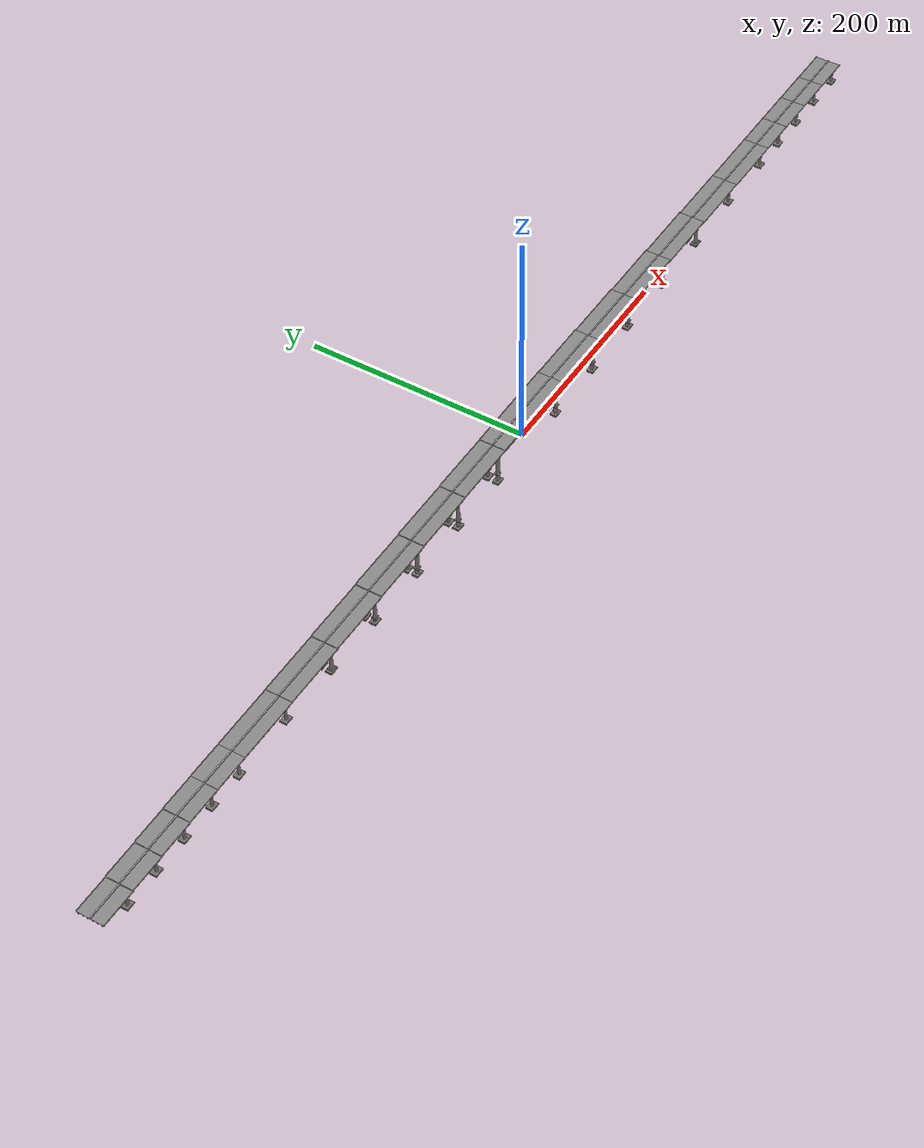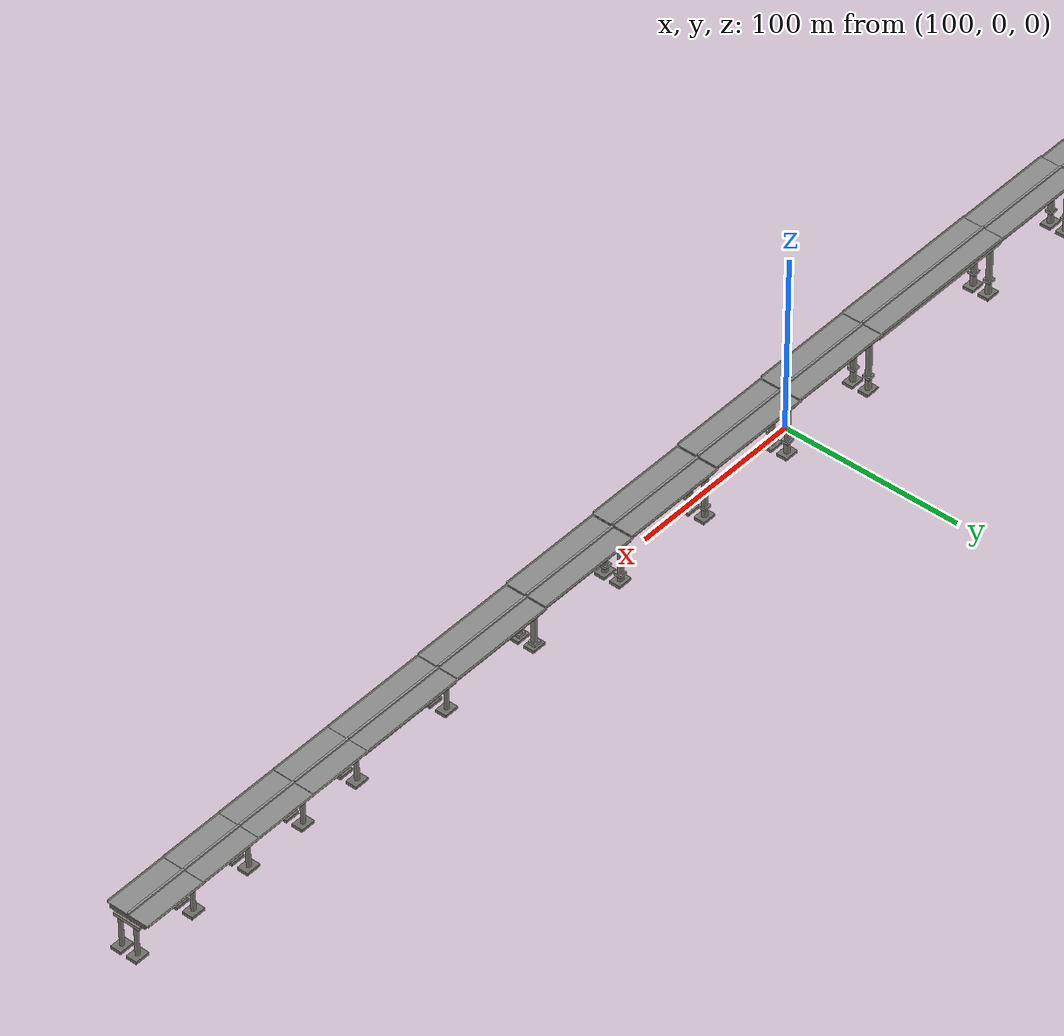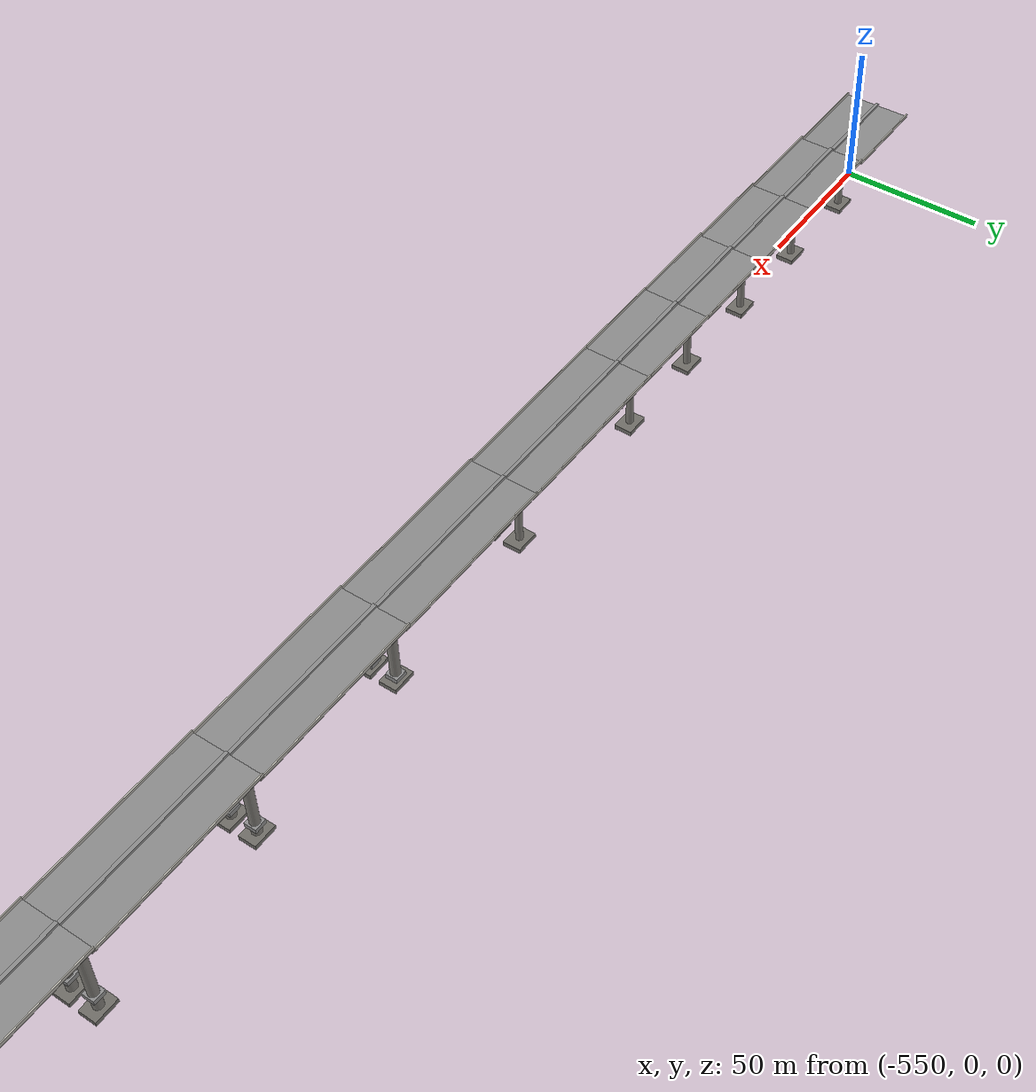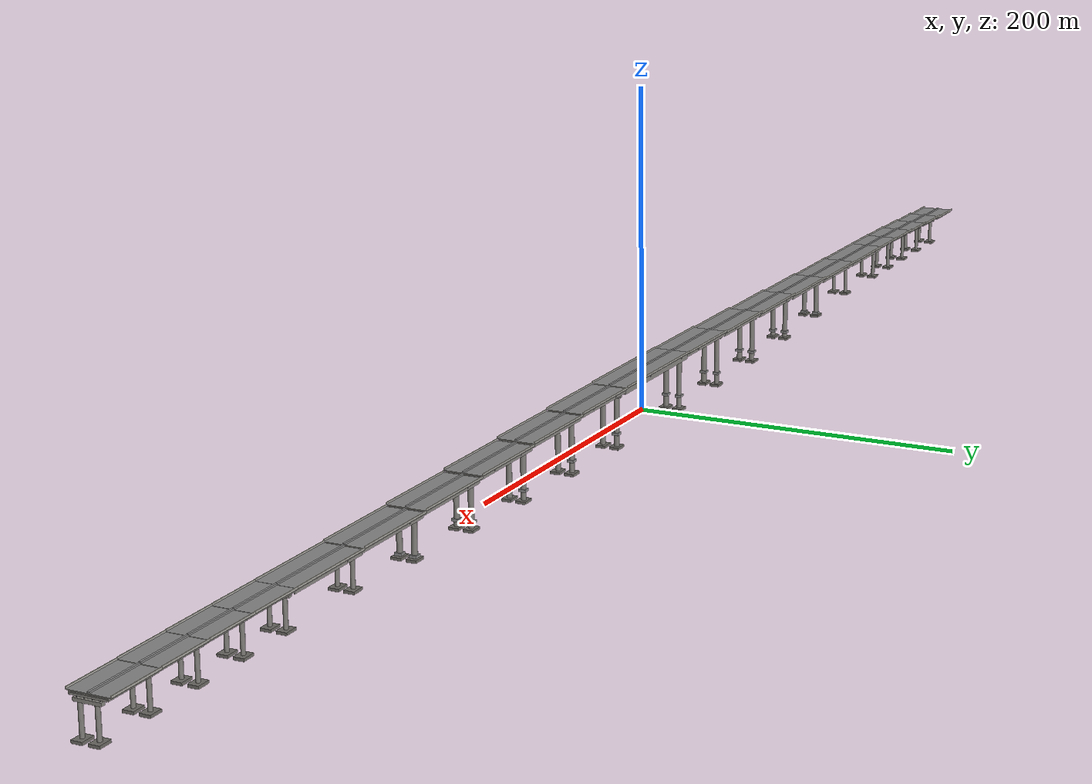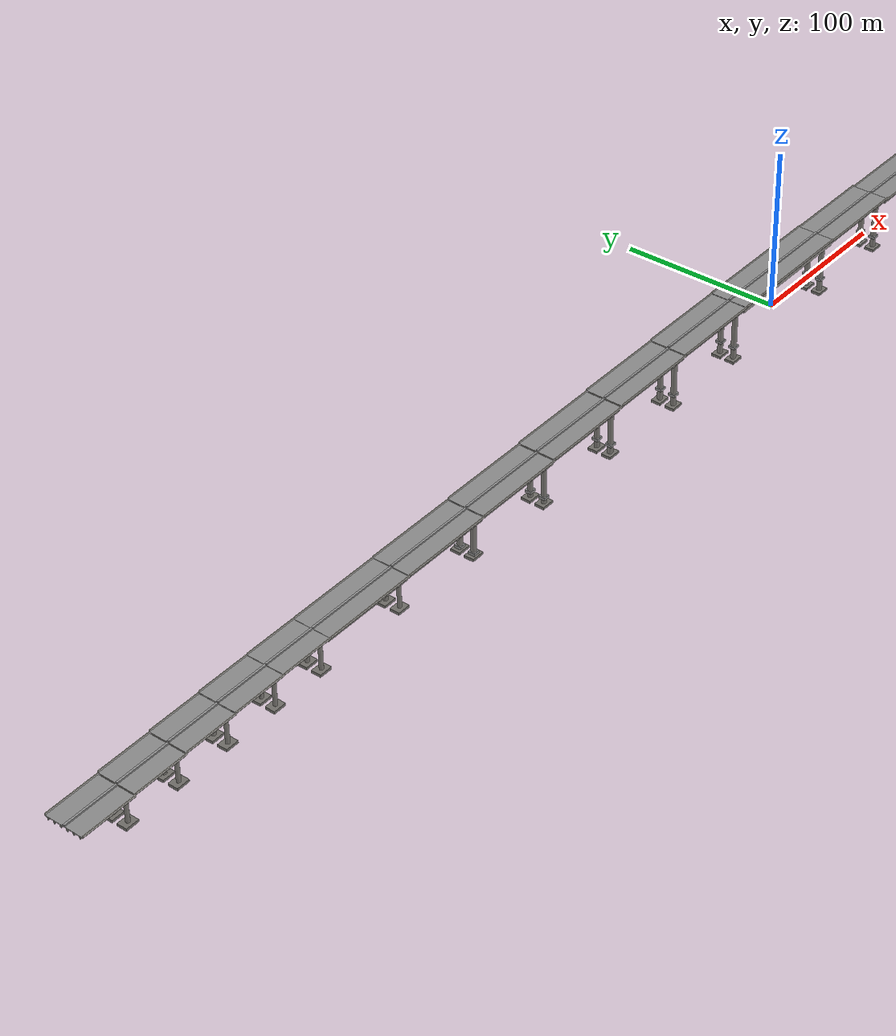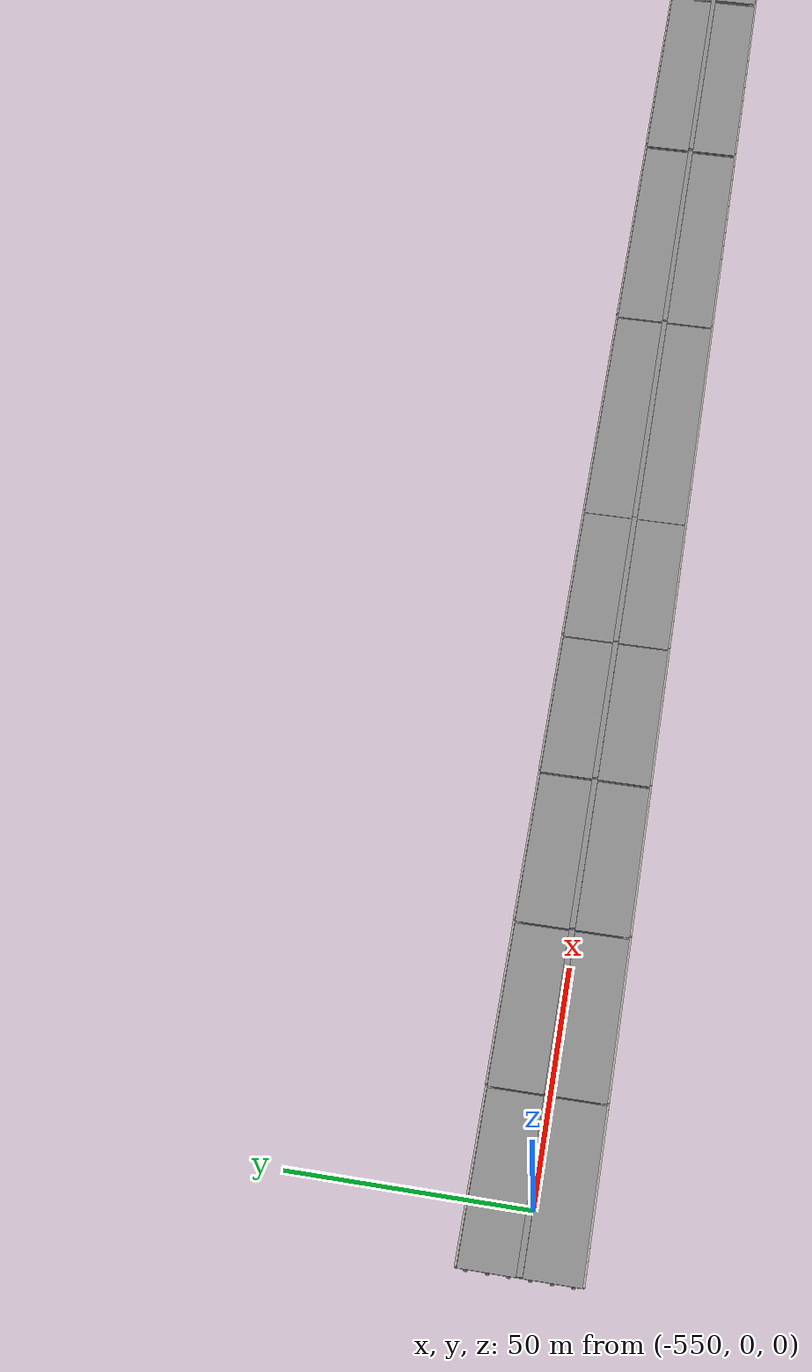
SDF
<?xml version="1.0" ?>
<sdf version="1.9">
  <model name="avian_bridge">
    <static>true</static>
    <pose>0 0 0 0 0 0</pose>
    <link name="link">
      <collision name="BR_BEARING_055_G2_collision">
        <pose>-533.333000 -6.000000 18.048000 0 0 0.000000</pose>
        <geometry>
          <box>
            <size>0.700000 0.600000 0.350000</size>
          </box>
        </geometry>
      </collision>
      <visual name="BR_BEARING_055_G2_visual">
        <pose>-533.333000 -6.000000 18.048000 0 0 0.000000</pose>
        <geometry>
          <box>
            <size>0.700000 0.600000 0.350000</size>
          </box>
        </geometry>
        <material>
          <ambient>0.064 0.064 0.068 1</ambient>
          <diffuse>0.160 0.160 0.170 1</diffuse>
          <specular>0.1 0.1 0.1 1</specular>
        </material>
      </visual>
      <collision name="BR_BEARING_055_G3_collision">
        <pose>-533.333000 -2.000000 18.048000 0 0 0.000000</pose>
        <geometry>
          <box>
            <size>0.700000 0.600000 0.350000</size>
          </box>
        </geometry>
      </collision>
      <visual name="BR_BEARING_055_G3_visual">
        <pose>-533.333000 -2.000000 18.048000 0 0 0.000000</pose>
        <geometry>
          <box>
            <size>0.700000 0.600000 0.350000</size>
          </box>
        </geometry>
        <material>
          <ambient>0.064 0.064 0.068 1</ambient>
          <diffuse>0.160 0.160 0.170 1</diffuse>
          <specular>0.1 0.1 0.1 1</specular>
        </material>
      </visual>
      <collision name="BR_BEARING_055_G4_collision">
        <pose>-533.333000 2.000000 18.048000 0 0 0.000000</pose>
        <geometry>
          <box>
            <size>0.700000 0.600000 0.350000</size>
          </box>
        </geometry>
      </collision>
      <visual name="BR_BEARING_055_G4_visual">
        <pose>-533.333000 2.000000 18.048000 0 0 0.000000</pose>
        <geometry>
          <box>
            <size>0.700000 0.600000 0.350000</size>
          </box>
        </geometry>
        <material>
          <ambient>0.064 0.064 0.068 1</ambient>
          <diffuse>0.160 0.160 0.170 1</diffuse>
          <specular>0.1 0.1 0.1 1</specular>
        </material>
      </visual>
      <collision name="BR_BEARING_055_G5_collision">
        <pose>-533.333000 6.000000 18.048000 0 0 0.000000</pose>
        <geometry>
          <box>
            <size>0.700000 0.600000 0.350000</size>
          </box>
        </geometry>
      </collision>
      <visual name="BR_BEARING_055_G5_visual">
        <pose>-533.333000 6.000000 18.048000 0 0 0.000000</pose>
        <geometry>
          <box>
            <size>0.700000 0.600000 0.350000</size>
          </box>
        </geometry>
        <material>
          <ambient>0.064 0.064 0.068 1</ambient>
          <diffuse>0.160 0.160 0.170 1</diffuse>
          <specular>0.1 0.1 0.1 1</specular>
        </material>
      </visual>
      <collision name="BR_BEARING_056_G2_collision">
        <pose>-500.000000 -6.000000 18.994400 0 0 0.000000</pose>
        <geometry>
          <box>
            <size>0.700000 0.600000 0.350000</size>
          </box>
        </geometry>
      </collision>
      <visual name="BR_BEARING_056_G2_visual">
        <pose>-500.000000 -6.000000 18.994400 0 0 0.000000</pose>
        <geometry>
          <box>
            <size>0.700000 0.600000 0.350000</size>
          </box>
        </geometry>
        <material>
          <ambient>0.064 0.064 0.068 1</ambient>
          <diffuse>0.160 0.160 0.170 1</diffuse>
          <specular>0.1 0.1 0.1 1</specular>
        </material>
      </visual>
      <collision name="BR_BEARING_056_G3_collision">
        <pose>-500.000000 -2.000000 18.994400 0 0 0.000000</pose>
        <geometry>
          <box>
            <size>0.700000 0.600000 0.350000</size>
          </box>
        </geometry>
      </collision>
      <visual name="BR_BEARING_056_G3_visual">
        <pose>-500.000000 -2.000000 18.994400 0 0 0.000000</pose>
        <geometry>
          <box>
            <size>0.700000 0.600000 0.350000</size>
          </box>
        </geometry>
        <material>
          <ambient>0.064 0.064 0.068 1</ambient>
          <diffuse>0.160 0.160 0.170 1</diffuse>
          <specular>0.1 0.1 0.1 1</specular>
        </material>
      </visual>
      <collision name="BR_BEARING_056_G4_collision">
        <pose>-500.000000 2.000000 18.994400 0 0 0.000000</pose>
        <geometry>
          <box>
            <size>0.700000 0.600000 0.350000</size>
          </box>
        </geometry>
      </collision>
      <visual name="BR_BEARING_056_G4_visual">
        <pose>-500.000000 2.000000 18.994400 0 0 0.000000</pose>
        <geometry>
          <box>
            <size>0.700000 0.600000 0.350000</size>
          </box>
        </geometry>
        <material>
          <ambient>0.064 0.064 0.068 1</ambient>
          <diffuse>0.160 0.160 0.170 1</diffuse>
          <specular>0.1 0.1 0.1 1</specular>
        </material>
      </visual>
      <collision name="BR_BEARING_056_G5_collision">
        <pose>-500.000000 6.000000 18.994400 0 0 0.000000</pose>
        <geometry>
          <box>
            <size>0.700000 0.600000 0.350000</size>
          </box>
        </geometry>
      </collision>
      <visual name="BR_BEARING_056_G5_visual">
        <pose>-500.000000 6.000000 18.994400 0 0 0.000000</pose>
        <geometry>
          <box>
            <size>0.700000 0.600000 0.350000</size>
          </box>
        </geometry>
        <material>
          <ambient>0.064 0.064 0.068 1</ambient>
          <diffuse>0.160 0.160 0.170 1</diffuse>
          <specular>0.1 0.1 0.1 1</specular>
        </material>
      </visual>
      <collision name="BR_BEARING_057_G2_collision">
        <pose>-466.667000 -6.000000 19.792800 0 0 0.000000</pose>
        <geometry>
          <box>
            <size>0.700000 0.600000 0.350000</size>
          </box>
        </geometry>
      </collision>
      <visual name="BR_BEARING_057_G2_visual">
        <pose>-466.667000 -6.000000 19.792800 0 0 0.000000</pose>
        <geometry>
          <box>
            <size>0.700000 0.600000 0.350000</size>
          </box>
        </geometry>
        <material>
          <ambient>0.064 0.064 0.068 1</ambient>
          <diffuse>0.160 0.160 0.170 1</diffuse>
          <specular>0.1 0.1 0.1 1</specular>
        </material>
      </visual>
      <collision name="BR_BEARING_057_G3_collision">
        <pose>-466.667000 -2.000000 19.792800 0 0 0.000000</pose>
        <geometry>
          <box>
            <size>0.700000 0.600000 0.350000</size>
          </box>
        </geometry>
      </collision>
      <visual name="BR_BEARING_057_G3_visual">
        <pose>-466.667000 -2.000000 19.792800 0 0 0.000000</pose>
        <geometry>
          <box>
            <size>0.700000 0.600000 0.350000</size>
          </box>
        </geometry>
        <material>
          <ambient>0.064 0.064 0.068 1</ambient>
          <diffuse>0.160 0.160 0.170 1</diffuse>
          <specular>0.1 0.1 0.1 1</specular>
        </material>
      </visual>
      <collision name="BR_BEARING_057_G4_collision">
        <pose>-466.667000 2.000000 19.792800 0 0 0.000000</pose>
        <geometry>
          <box>
            <size>0.700000 0.600000 0.350000</size>
          </box>
        </geometry>
      </collision>
      <visual name="BR_BEARING_057_G4_visual">
        <pose>-466.667000 2.000000 19.792800 0 0 0.000000</pose>
        <geometry>
          <box>
            <size>0.700000 0.600000 0.350000</size>
          </box>
        </geometry>
        <material>
          <ambient>0.064 0.064 0.068 1</ambient>
          <diffuse>0.160 0.160 0.170 1</diffuse>
          <specular>0.1 0.1 0.1 1</specular>
        </material>
      </visual>
      <collision name="BR_BEARING_057_G5_collision">
        <pose>-466.667000 6.000000 19.792800 0 0 0.000000</pose>
        <geometry>
          <box>
            <size>0.700000 0.600000 0.350000</size>
          </box>
        </geometry>
      </collision>
      <visual name="BR_BEARING_057_G5_visual">
        <pose>-466.667000 6.000000 19.792800 0 0 0.000000</pose>
        <geometry>
          <box>
            <size>0.700000 0.600000 0.350000</size>
          </box>
        </geometry>
        <material>
          <ambient>0.064 0.064 0.068 1</ambient>
          <diffuse>0.160 0.160 0.170 1</diffuse>
          <specular>0.1 0.1 0.1 1</specular>
        </material>
      </visual>
      <collision name="BR_BEARING_058_G2_collision">
        <pose>-433.333000 -6.000000 20.344200 0 0 0.000000</pose>
        <geometry>
          <box>
            <size>0.700000 0.600000 0.350000</size>
          </box>
        </geometry>
      </collision>
      <visual name="BR_BEARING_058_G2_visual">
        <pose>-433.333000 -6.000000 20.344200 0 0 0.000000</pose>
        <geometry>
          <box>
            <size>0.700000 0.600000 0.350000</size>
          </box>
        </geometry>
        <material>
          <ambient>0.064 0.064 0.068 1</ambient>
          <diffuse>0.160 0.160 0.170 1</diffuse>
          <specular>0.1 0.1 0.1 1</specular>
        </material>
      </visual>
      <collision name="BR_BEARING_058_G3_collision">
        <pose>-433.333000 -2.000000 20.344200 0 0 0.000000</pose>
        <geometry>
          <box>
            <size>0.700000 0.600000 0.350000</size>
          </box>
        </geometry>
      </collision>
      <visual name="BR_BEARING_058_G3_visual">
        <pose>-433.333000 -2.000000 20.344200 0 0 0.000000</pose>
        <geometry>
          <box>
            <size>0.700000 0.600000 0.350000</size>
          </box>
        </geometry>
        <material>
          <ambient>0.064 0.064 0.068 1</ambient>
          <diffuse>0.160 0.160 0.170 1</diffuse>
          <specular>0.1 0.1 0.1 1</specular>
        </material>
      </visual>
      <collision name="BR_BEARING_058_G4_collision">
        <pose>-433.333000 2.000000 20.344200 0 0 0.000000</pose>
        <geometry>
          <box>
            <size>0.700000 0.600000 0.350000</size>
          </box>
        </geometry>
      </collision>
      <visual name="BR_BEARING_058_G4_visual">
        <pose>-433.333000 2.000000 20.344200 0 0 0.000000</pose>
        <geometry>
          <box>
            <size>0.700000 0.600000 0.350000</size>
          </box>
        </geometry>
        <material>
          <ambient>0.064 0.064 0.068 1</ambient>
          <diffuse>0.160 0.160 0.170 1</diffuse>
          <specular>0.1 0.1 0.1 1</specular>
        </material>
      </visual>
      <collision name="BR_BEARING_058_G5_collision">
        <pose>-433.333000 6.000000 20.344200 0 0 0.000000</pose>
        <geometry>
          <box>
            <size>0.700000 0.600000 0.350000</size>
          </box>
        </geometry>
      </collision>
      <visual name="BR_BEARING_058_G5_visual">
        <pose>-433.333000 6.000000 20.344200 0 0 0.000000</pose>
        <geometry>
          <box>
            <size>0.700000 0.600000 0.350000</size>
          </box>
        </geometry>
        <material>
          <ambient>0.064 0.064 0.068 1</ambient>
          <diffuse>0.160 0.160 0.170 1</diffuse>
          <specular>0.1 0.1 0.1 1</specular>
        </material>
      </visual>
      <collision name="BR_BEARING_059_G2_collision">
        <pose>-400.000000 -6.000000 20.550000 0 0 0.000000</pose>
        <geometry>
          <box>
            <size>0.700000 0.600000 0.350000</size>
          </box>
        </geometry>
      </collision>
      <visual name="BR_BEARING_059_G2_visual">
        <pose>-400.000000 -6.000000 20.550000 0 0 0.000000</pose>
        <geometry>
          <box>
            <size>0.700000 0.600000 0.350000</size>
          </box>
        </geometry>
        <material>
          <ambient>0.064 0.064 0.068 1</ambient>
          <diffuse>0.160 0.160 0.170 1</diffuse>
          <specular>0.1 0.1 0.1 1</specular>
        </material>
      </visual>
      <collision name="BR_BEARING_059_G3_collision">
        <pose>-400.000000 -2.000000 20.550000 0 0 0.000000</pose>
        <geometry>
          <box>
            <size>0.700000 0.600000 0.350000</size>
          </box>
        </geometry>
      </collision>
      <visual name="BR_BEARING_059_G3_visual">
        <pose>-400.000000 -2.000000 20.550000 0 0 0.000000</pose>
        <geometry>
          <box>
            <size>0.700000 0.600000 0.350000</size>
          </box>
        </geometry>
        <material>
          <ambient>0.064 0.064 0.068 1</ambient>
          <diffuse>0.160 0.160 0.170 1</diffuse>
          <specular>0.1 0.1 0.1 1</specular>
        </material>
      </visual>
      <collision name="BR_BEARING_059_G4_collision">
        <pose>-400.000000 2.000000 20.550000 0 0 0.000000</pose>
        <geometry>
          <box>
            <size>0.700000 0.600000 0.350000</size>
          </box>
        </geometry>
      </collision>
      <visual name="BR_BEARING_059_G4_visual">
        <pose>-400.000000 2.000000 20.550000 0 0 0.000000</pose>
        <geometry>
          <box>
            <size>0.700000 0.600000 0.350000</size>
          </box>
        </geometry>
        <material>
          <ambient>0.064 0.064 0.068 1</ambient>
          <diffuse>0.160 0.160 0.170 1</diffuse>
          <specular>0.1 0.1 0.1 1</specular>
        </material>
      </visual>
      <collision name="BR_BEARING_059_G5_collision">
        <pose>-400.000000 6.000000 20.550000 0 0 0.000000</pose>
        <geometry>
          <box>
            <size>0.700000 0.600000 0.350000</size>
          </box>
        </geometry>
      </collision>
      <visual name="BR_BEARING_059_G5_visual">
        <pose>-400.000000 6.000000 20.550000 0 0 0.000000</pose>
        <geometry>
          <box>
            <size>0.700000 0.600000 0.350000</size>
          </box>
        </geometry>
        <material>
          <ambient>0.064 0.064 0.068 1</ambient>
          <diffuse>0.160 0.160 0.170 1</diffuse>
          <specular>0.1 0.1 0.1 1</specular>
        </material>
      </visual>
      <collision name="BR_BEARING_060_G2_collision">
        <pose>-340.833000 -6.000000 19.697300 0 0 0.000000</pose>
        <geometry>
          <box>
            <size>0.700000 0.600000 0.350000</size>
          </box>
        </geometry>
      </collision>
      <visual name="BR_BEARING_060_G2_visual">
        <pose>-340.833000 -6.000000 19.697300 0 0 0.000000</pose>
        <geometry>
          <box>
            <size>0.700000 0.600000 0.350000</size>
          </box>
        </geometry>
        <material>
          <ambient>0.064 0.064 0.068 1</ambient>
          <diffuse>0.160 0.160 0.170 1</diffuse>
          <specular>0.1 0.1 0.1 1</specular>
        </material>
      </visual>
      <collision name="BR_BEARING_060_G3_collision">
        <pose>-340.833000 -2.000000 19.697300 0 0 0.000000</pose>
        <geometry>
          <box>
            <size>0.700000 0.600000 0.350000</size>
          </box>
        </geometry>
      </collision>
      <visual name="BR_BEARING_060_G3_visual">
        <pose>-340.833000 -2.000000 19.697300 0 0 0.000000</pose>
        <geometry>
          <box>
            <size>0.700000 0.600000 0.350000</size>
          </box>
        </geometry>
        <material>
          <ambient>0.064 0.064 0.068 1</ambient>
          <diffuse>0.160 0.160 0.170 1</diffuse>
          <specular>0.1 0.1 0.1 1</specular>
        </material>
      </visual>
      <collision name="BR_BEARING_060_G4_collision">
        <pose>-340.833000 2.000000 19.697300 0 0 0.000000</pose>
        <geometry>
          <box>
            <size>0.700000 0.600000 0.350000</size>
          </box>
        </geometry>
      </collision>
      <visual name="BR_BEARING_060_G4_visual">
        <pose>-340.833000 2.000000 19.697300 0 0 0.000000</pose>
        <geometry>
          <box>
            <size>0.700000 0.600000 0.350000</size>
          </box>
        </geometry>
        <material>
          <ambient>0.064 0.064 0.068 1</ambient>
          <diffuse>0.160 0.160 0.170 1</diffuse>
          <specular>0.1 0.1 0.1 1</specular>
        </material>
      </visual>
      <collision name="BR_BEARING_060_G5_collision">
        <pose>-340.833000 6.000000 19.697300 0 0 0.000000</pose>
        <geometry>
          <box>
            <size>0.700000 0.600000 0.350000</size>
          </box>
        </geometry>
      </collision>
      <visual name="BR_BEARING_060_G5_visual">
        <pose>-340.833000 6.000000 19.697300 0 0 0.000000</pose>
        <geometry>
          <box>
            <size>0.700000 0.600000 0.350000</size>
          </box>
        </geometry>
        <material>
          <ambient>0.064 0.064 0.068 1</ambient>
          <diffuse>0.160 0.160 0.170 1</diffuse>
          <specular>0.1 0.1 0.1 1</specular>
        </material>
      </visual>
      <collision name="BR_BEARING_061_G2_collision">
        <pose>-281.667000 -6.000000 20.303700 0 0 0.000000</pose>
        <geometry>
          <box>
            <size>0.700000 0.600000 0.350000</size>
          </box>
        </geometry>
      </collision>
      <visual name="BR_BEARING_061_G2_visual">
        <pose>-281.667000 -6.000000 20.303700 0 0 0.000000</pose>
        <geometry>
          <box>
            <size>0.700000 0.600000 0.350000</size>
          </box>
        </geometry>
        <material>
          <ambient>0.064 0.064 0.068 1</ambient>
          <diffuse>0.160 0.160 0.170 1</diffuse>
          <specular>0.1 0.1 0.1 1</specular>
        </material>
      </visual>
      <collision name="BR_BEARING_061_G3_collision">
        <pose>-281.667000 -2.000000 20.303700 0 0 0.000000</pose>
        <geometry>
          <box>
            <size>0.700000 0.600000 0.350000</size>
          </box>
        </geometry>
      </collision>
      <visual name="BR_BEARING_061_G3_visual">
        <pose>-281.667000 -2.000000 20.303700 0 0 0.000000</pose>
        <geometry>
          <box>
            <size>0.700000 0.600000 0.350000</size>
          </box>
        </geometry>
        <material>
          <ambient>0.064 0.064 0.068 1</ambient>
          <diffuse>0.160 0.160 0.170 1</diffuse>
          <specular>0.1 0.1 0.1 1</specular>
        </material>
      </visual>
      <collision name="BR_BEARING_061_G4_collision">
        <pose>-281.667000 2.000000 20.303700 0 0 0.000000</pose>
        <geometry>
          <box>
            <size>0.700000 0.600000 0.350000</size>
          </box>
        </geometry>
      </collision>
      <visual name="BR_BEARING_061_G4_visual">
        <pose>-281.667000 2.000000 20.303700 0 0 0.000000</pose>
        <geometry>
          <box>
            <size>0.700000 0.600000 0.350000</size>
          </box>
        </geometry>
        <material>
          <ambient>0.064 0.064 0.068 1</ambient>
          <diffuse>0.160 0.160 0.170 1</diffuse>
          <specular>0.1 0.1 0.1 1</specular>
        </material>
      </visual>
      <collision name="BR_BEARING_061_G5_collision">
        <pose>-281.667000 6.000000 20.303700 0 0 0.000000</pose>
        <geometry>
          <box>
            <size>0.700000 0.600000 0.350000</size>
          </box>
        </geometry>
      </collision>
      <visual name="BR_BEARING_061_G5_visual">
        <pose>-281.667000 6.000000 20.303700 0 0 0.000000</pose>
        <geometry>
          <box>
            <size>0.700000 0.600000 0.350000</size>
          </box>
        </geometry>
        <material>
          <ambient>0.064 0.064 0.068 1</ambient>
          <diffuse>0.160 0.160 0.170 1</diffuse>
          <specular>0.1 0.1 0.1 1</specular>
        </material>
      </visual>
      <collision name="BR_BEARING_062_G2_collision">
        <pose>-222.500000 -6.000000 21.124500 0 0 0.000000</pose>
        <geometry>
          <box>
            <size>0.700000 0.600000 0.350000</size>
          </box>
        </geometry>
      </collision>
      <visual name="BR_BEARING_062_G2_visual">
        <pose>-222.500000 -6.000000 21.124500 0 0 0.000000</pose>
        <geometry>
          <box>
            <size>0.700000 0.600000 0.350000</size>
          </box>
        </geometry>
        <material>
          <ambient>0.064 0.064 0.068 1</ambient>
          <diffuse>0.160 0.160 0.170 1</diffuse>
          <specular>0.1 0.1 0.1 1</specular>
        </material>
      </visual>
      <collision name="BR_BEARING_062_G3_collision">
        <pose>-222.500000 -2.000000 21.124500 0 0 0.000000</pose>
        <geometry>
          <box>
            <size>0.700000 0.600000 0.350000</size>
          </box>
        </geometry>
      </collision>
      <visual name="BR_BEARING_062_G3_visual">
        <pose>-222.500000 -2.000000 21.124500 0 0 0.000000</pose>
        <geometry>
          <box>
            <size>0.700000 0.600000 0.350000</size>
          </box>
        </geometry>
        <material>
          <ambient>0.064 0.064 0.068 1</ambient>
          <diffuse>0.160 0.160 0.170 1</diffuse>
          <specular>0.1 0.1 0.1 1</specular>
        </material>
      </visual>
      <collision name="BR_BEARING_062_G4_collision">
        <pose>-222.500000 2.000000 21.124500 0 0 0.000000</pose>
        <geometry>
          <box>
            <size>0.700000 0.600000 0.350000</size>
          </box>
        </geometry>
      </collision>
      <visual name="BR_BEARING_062_G4_visual">
        <pose>-222.500000 2.000000 21.124500 0 0 0.000000</pose>
        <geometry>
          <box>
            <size>0.700000 0.600000 0.350000</size>
          </box>
        </geometry>
        <material>
          <ambient>0.064 0.064 0.068 1</ambient>
          <diffuse>0.160 0.160 0.170 1</diffuse>
          <specular>0.1 0.1 0.1 1</specular>
        </material>
      </visual>
      <collision name="BR_BEARING_062_G5_collision">
        <pose>-222.500000 6.000000 21.124500 0 0 0.000000</pose>
        <geometry>
          <box>
            <size>0.700000 0.600000 0.350000</size>
          </box>
        </geometry>
      </collision>
      <visual name="BR_BEARING_062_G5_visual">
        <pose>-222.500000 6.000000 21.124500 0 0 0.000000</pose>
        <geometry>
          <box>
            <size>0.700000 0.600000 0.350000</size>
          </box>
        </geometry>
        <material>
          <ambient>0.064 0.064 0.068 1</ambient>
          <diffuse>0.160 0.160 0.170 1</diffuse>
          <specular>0.1 0.1 0.1 1</specular>
        </material>
      </visual>
      <collision name="BR_BEARING_063_G2_collision">
        <pose>-163.333000 -6.000000 22.004400 0 0 0.000000</pose>
        <geometry>
          <box>
            <size>0.700000 0.600000 0.350000</size>
          </box>
        </geometry>
      </collision>
      <visual name="BR_BEARING_063_G2_visual">
        <pose>-163.333000 -6.000000 22.004400 0 0 0.000000</pose>
        <geometry>
          <box>
            <size>0.700000 0.600000 0.350000</size>
          </box>
        </geometry>
        <material>
          <ambient>0.064 0.064 0.068 1</ambient>
          <diffuse>0.160 0.160 0.170 1</diffuse>
          <specular>0.1 0.1 0.1 1</specular>
        </material>
      </visual>
      <collision name="BR_BEARING_063_G3_collision">
        <pose>-163.333000 -2.000000 22.004400 0 0 0.000000</pose>
        <geometry>
          <box>
            <size>0.700000 0.600000 0.350000</size>
          </box>
        </geometry>
      </collision>
      <visual name="BR_BEARING_063_G3_visual">
        <pose>-163.333000 -2.000000 22.004400 0 0 0.000000</pose>
        <geometry>
          <box>
            <size>0.700000 0.600000 0.350000</size>
          </box>
        </geometry>
        <material>
          <ambient>0.064 0.064 0.068 1</ambient>
          <diffuse>0.160 0.160 0.170 1</diffuse>
          <specular>0.1 0.1 0.1 1</specular>
        </material>
      </visual>
      <collision name="BR_BEARING_063_G4_collision">
        <pose>-163.333000 2.000000 22.004400 0 0 0.000000</pose>
        <geometry>
          <box>
            <size>0.700000 0.600000 0.350000</size>
          </box>
        </geometry>
      </collision>
      <visual name="BR_BEARING_063_G4_visual">
        <pose>-163.333000 2.000000 22.004400 0 0 0.000000</pose>
        <geometry>
          <box>
            <size>0.700000 0.600000 0.350000</size>
          </box>
        </geometry>
        <material>
          <ambient>0.064 0.064 0.068 1</ambient>
          <diffuse>0.160 0.160 0.170 1</diffuse>
          <specular>0.1 0.1 0.1 1</specular>
        </material>
      </visual>
      <collision name="BR_BEARING_063_G5_collision">
        <pose>-163.333000 6.000000 22.004400 0 0 0.000000</pose>
        <geometry>
          <box>
            <size>0.700000 0.600000 0.350000</size>
          </box>
        </geometry>
      </collision>
      <visual name="BR_BEARING_063_G5_visual">
        <pose>-163.333000 6.000000 22.004400 0 0 0.000000</pose>
        <geometry>
          <box>
            <size>0.700000 0.600000 0.350000</size>
          </box>
        </geometry>
        <material>
          <ambient>0.064 0.064 0.068 1</ambient>
          <diffuse>0.160 0.160 0.170 1</diffuse>
          <specular>0.1 0.1 0.1 1</specular>
        </material>
      </visual>
      <collision name="BR_BEARING_064_G2_collision">
        <pose>-104.167000 -6.000000 22.788100 0 0 0.000000</pose>
        <geometry>
          <box>
            <size>0.700000 0.600000 0.350000</size>
          </box>
        </geometry>
      </collision>
      <visual name="BR_BEARING_064_G2_visual">
        <pose>-104.167000 -6.000000 22.788100 0 0 0.000000</pose>
        <geometry>
          <box>
            <size>0.700000 0.600000 0.350000</size>
          </box>
        </geometry>
        <material>
          <ambient>0.064 0.064 0.068 1</ambient>
          <diffuse>0.160 0.160 0.170 1</diffuse>
          <specular>0.1 0.1 0.1 1</specular>
        </material>
      </visual>
      <collision name="BR_BEARING_064_G3_collision">
        <pose>-104.167000 -2.000000 22.788100 0 0 0.000000</pose>
        <geometry>
          <box>
            <size>0.700000 0.600000 0.350000</size>
          </box>
        </geometry>
      </collision>
      <visual name="BR_BEARING_064_G3_visual">
        <pose>-104.167000 -2.000000 22.788100 0 0 0.000000</pose>
        <geometry>
          <box>
            <size>0.700000 0.600000 0.350000</size>
          </box>
        </geometry>
        <material>
          <ambient>0.064 0.064 0.068 1</ambient>
          <diffuse>0.160 0.160 0.170 1</diffuse>
          <specular>0.1 0.1 0.1 1</specular>
        </material>
      </visual>
      <collision name="BR_BEARING_064_G4_collision">
        <pose>-104.167000 2.000000 22.788100 0 0 0.000000</pose>
        <geometry>
          <box>
            <size>0.700000 0.600000 0.350000</size>
          </box>
        </geometry>
      </collision>
      <visual name="BR_BEARING_064_G4_visual">
        <pose>-104.167000 2.000000 22.788100 0 0 0.000000</pose>
        <geometry>
          <box>
            <size>0.700000 0.600000 0.350000</size>
          </box>
        </geometry>
        <material>
          <ambient>0.064 0.064 0.068 1</ambient>
          <diffuse>0.160 0.160 0.170 1</diffuse>
          <specular>0.1 0.1 0.1 1</specular>
        </material>
      </visual>
      <collision name="BR_BEARING_064_G5_collision">
        <pose>-104.167000 6.000000 22.788100 0 0 0.000000</pose>
        <geometry>
          <box>
            <size>0.700000 0.600000 0.350000</size>
          </box>
        </geometry>
      </collision>
      <visual name="BR_BEARING_064_G5_visual">
        <pose>-104.167000 6.000000 22.788100 0 0 0.000000</pose>
        <geometry>
          <box>
            <size>0.700000 0.600000 0.350000</size>
          </box>
        </geometry>
        <material>
          <ambient>0.064 0.064 0.068 1</ambient>
          <diffuse>0.160 0.160 0.170 1</diffuse>
          <specular>0.1 0.1 0.1 1</specular>
        </material>
      </visual>
      <collision name="BR_BEARING_065_G2_collision">
        <pose>-45.000000 -6.000000 23.320100 0 0 0.000000</pose>
        <geometry>
          <box>
            <size>0.700200 0.600000 0.350000</size>
          </box>
        </geometry>
      </collision>
      <visual name="BR_BEARING_065_G2_visual">
        <pose>-45.000000 -6.000000 23.320100 0 0 0.000000</pose>
        <geometry>
          <box>
            <size>0.700200 0.600000 0.350000</size>
          </box>
        </geometry>
        <material>
          <ambient>0.064 0.064 0.068 1</ambient>
          <diffuse>0.160 0.160 0.170 1</diffuse>
          <specular>0.1 0.1 0.1 1</specular>
        </material>
      </visual>
      <collision name="BR_BEARING_065_G3_collision">
        <pose>-45.000000 -2.000000 23.320100 0 0 0.000000</pose>
        <geometry>
          <box>
            <size>0.700200 0.600000 0.350000</size>
          </box>
        </geometry>
      </collision>
      <visual name="BR_BEARING_065_G3_visual">
        <pose>-45.000000 -2.000000 23.320100 0 0 0.000000</pose>
        <geometry>
          <box>
            <size>0.700200 0.600000 0.350000</size>
          </box>
        </geometry>
        <material>
          <ambient>0.064 0.064 0.068 1</ambient>
          <diffuse>0.160 0.160 0.170 1</diffuse>
          <specular>0.1 0.1 0.1 1</specular>
        </material>
      </visual>
      <collision name="BR_BEARING_065_G4_collision">
        <pose>-45.000000 2.000000 23.320100 0 0 0.000000</pose>
        <geometry>
          <box>
            <size>0.700200 0.600000 0.350000</size>
          </box>
        </geometry>
      </collision>
      <visual name="BR_BEARING_065_G4_visual">
        <pose>-45.000000 2.000000 23.320100 0 0 0.000000</pose>
        <geometry>
          <box>
            <size>0.700200 0.600000 0.350000</size>
          </box>
        </geometry>
        <material>
          <ambient>0.064 0.064 0.068 1</ambient>
          <diffuse>0.160 0.160 0.170 1</diffuse>
          <specular>0.1 0.1 0.1 1</specular>
        </material>
      </visual>
      <collision name="BR_BEARING_065_G5_collision">
        <pose>-45.000000 6.000000 23.320100 0 0 0.000000</pose>
        <geometry>
          <box>
            <size>0.700200 0.600000 0.350000</size>
          </box>
        </geometry>
      </collision>
      <visual name="BR_BEARING_065_G5_visual">
        <pose>-45.000000 6.000000 23.320100 0 0 0.000000</pose>
        <geometry>
          <box>
            <size>0.700200 0.600000 0.350000</size>
          </box>
        </geometry>
        <material>
          <ambient>0.064 0.064 0.068 1</ambient>
          <diffuse>0.160 0.160 0.170 1</diffuse>
          <specular>0.1 0.1 0.1 1</specular>
        </material>
      </visual>
      <collision name="BR_BEARING_066_G2_collision">
        <pose>45.000000 -6.000000 21.865900 0 0 0.000000</pose>
        <geometry>
          <box>
            <size>0.700200 0.600000 0.350000</size>
          </box>
        </geometry>
      </collision>
      <visual name="BR_BEARING_066_G2_visual">
        <pose>45.000000 -6.000000 21.865900 0 0 0.000000</pose>
        <geometry>
          <box>
            <size>0.700200 0.600000 0.350000</size>
          </box>
        </geometry>
        <material>
          <ambient>0.064 0.064 0.068 1</ambient>
          <diffuse>0.160 0.160 0.170 1</diffuse>
          <specular>0.1 0.1 0.1 1</specular>
        </material>
      </visual>
      <collision name="BR_BEARING_066_G3_collision">
        <pose>45.000000 -2.000000 21.865900 0 0 0.000000</pose>
        <geometry>
          <box>
            <size>0.700200 0.600000 0.350000</size>
          </box>
        </geometry>
      </collision>
      <visual name="BR_BEARING_066_G3_visual">
        <pose>45.000000 -2.000000 21.865900 0 0 0.000000</pose>
        <geometry>
          <box>
            <size>0.700200 0.600000 0.350000</size>
          </box>
        </geometry>
        <material>
          <ambient>0.064 0.064 0.068 1</ambient>
          <diffuse>0.160 0.160 0.170 1</diffuse>
          <specular>0.1 0.1 0.1 1</specular>
        </material>
      </visual>
      <collision name="BR_BEARING_066_G4_collision">
        <pose>45.000000 2.000000 21.865900 0 0 0.000000</pose>
        <geometry>
          <box>
            <size>0.700200 0.600000 0.350000</size>
          </box>
        </geometry>
      </collision>
      <visual name="BR_BEARING_066_G4_visual">
        <pose>45.000000 2.000000 21.865900 0 0 0.000000</pose>
        <geometry>
          <box>
            <size>0.700200 0.600000 0.350000</size>
          </box>
        </geometry>
        <material>
          <ambient>0.064 0.064 0.068 1</ambient>
          <diffuse>0.160 0.160 0.170 1</diffuse>
          <specular>0.1 0.1 0.1 1</specular>
        </material>
      </visual>
      <collision name="BR_BEARING_066_G5_collision">
        <pose>45.000000 6.000000 21.865900 0 0 0.000000</pose>
        <geometry>
          <box>
            <size>0.700200 0.600000 0.350000</size>
          </box>
        </geometry>
      </collision>
      <visual name="BR_BEARING_066_G5_visual">
        <pose>45.000000 6.000000 21.865900 0 0 0.000000</pose>
        <geometry>
          <box>
            <size>0.700200 0.600000 0.350000</size>
          </box>
        </geometry>
        <material>
          <ambient>0.064 0.064 0.068 1</ambient>
          <diffuse>0.160 0.160 0.170 1</diffuse>
          <specular>0.1 0.1 0.1 1</specular>
        </material>
      </visual>
      <collision name="BR_BEARING_067_G2_collision">
        <pose>104.167000 -6.000000 22.535900 0 0 0.000000</pose>
        <geometry>
          <box>
            <size>0.700200 0.600000 0.350000</size>
          </box>
        </geometry>
      </collision>
      <visual name="BR_BEARING_067_G2_visual">
        <pose>104.167000 -6.000000 22.535900 0 0 0.000000</pose>
        <geometry>
          <box>
            <size>0.700200 0.600000 0.350000</size>
          </box>
        </geometry>
        <material>
          <ambient>0.064 0.064 0.068 1</ambient>
          <diffuse>0.160 0.160 0.170 1</diffuse>
          <specular>0.1 0.1 0.1 1</specular>
        </material>
      </visual>
      <collision name="BR_BEARING_067_G3_collision">
        <pose>104.167000 -2.000000 22.535900 0 0 0.000000</pose>
        <geometry>
          <box>
            <size>0.700200 0.600000 0.350000</size>
          </box>
        </geometry>
      </collision>
      <visual name="BR_BEARING_067_G3_visual">
        <pose>104.167000 -2.000000 22.535900 0 0 0.000000</pose>
        <geometry>
          <box>
            <size>0.700200 0.600000 0.350000</size>
          </box>
        </geometry>
        <material>
          <ambient>0.064 0.064 0.068 1</ambient>
          <diffuse>0.160 0.160 0.170 1</diffuse>
          <specular>0.1 0.1 0.1 1</specular>
        </material>
      </visual>
      <collision name="BR_BEARING_067_G4_collision">
        <pose>104.167000 2.000000 22.535900 0 0 0.000000</pose>
        <geometry>
          <box>
            <size>0.700200 0.600000 0.350000</size>
          </box>
        </geometry>
      </collision>
      <visual name="BR_BEARING_067_G4_visual">
        <pose>104.167000 2.000000 22.535900 0 0 0.000000</pose>
        <geometry>
          <box>
            <size>0.700200 0.600000 0.350000</size>
          </box>
        </geometry>
        <material>
          <ambient>0.064 0.064 0.068 1</ambient>
          <diffuse>0.160 0.160 0.170 1</diffuse>
          <specular>0.1 0.1 0.1 1</specular>
        </material>
      </visual>
      <collision name="BR_BEARING_067_G5_collision">
        <pose>104.167000 6.000000 22.535900 0 0 0.000000</pose>
        <geometry>
          <box>
            <size>0.700200 0.600000 0.350000</size>
          </box>
        </geometry>
      </collision>
      <visual name="BR_BEARING_067_G5_visual">
        <pose>104.167000 6.000000 22.535900 0 0 0.000000</pose>
        <geometry>
          <box>
            <size>0.700200 0.600000 0.350000</size>
          </box>
        </geometry>
        <material>
          <ambient>0.064 0.064 0.068 1</ambient>
          <diffuse>0.160 0.160 0.170 1</diffuse>
          <specular>0.1 0.1 0.1 1</specular>
        </material>
      </visual>
      <collision name="BR_BEARING_068_G2_collision">
        <pose>163.333000 -6.000000 21.458400 0 0 0.000000</pose>
        <geometry>
          <box>
            <size>0.700200 0.600000 0.350000</size>
          </box>
        </geometry>
      </collision>
      <visual name="BR_BEARING_068_G2_visual">
        <pose>163.333000 -6.000000 21.458400 0 0 0.000000</pose>
        <geometry>
          <box>
            <size>0.700200 0.600000 0.350000</size>
          </box>
        </geometry>
        <material>
          <ambient>0.064 0.064 0.068 1</ambient>
          <diffuse>0.160 0.160 0.170 1</diffuse>
          <specular>0.1 0.1 0.1 1</specular>
        </material>
      </visual>
      <collision name="BR_BEARING_068_G3_collision">
        <pose>163.333000 -2.000000 21.458400 0 0 0.000000</pose>
        <geometry>
          <box>
            <size>0.700200 0.600000 0.350000</size>
          </box>
        </geometry>
      </collision>
      <visual name="BR_BEARING_068_G3_visual">
        <pose>163.333000 -2.000000 21.458400 0 0 0.000000</pose>
        <geometry>
          <box>
            <size>0.700200 0.600000 0.350000</size>
          </box>
        </geometry>
        <material>
          <ambient>0.064 0.064 0.068 1</ambient>
          <diffuse>0.160 0.160 0.170 1</diffuse>
          <specular>0.1 0.1 0.1 1</specular>
        </material>
      </visual>
      <collision name="BR_BEARING_068_G4_collision">
        <pose>163.333000 2.000000 21.458400 0 0 0.000000</pose>
        <geometry>
          <box>
            <size>0.700200 0.600000 0.350000</size>
          </box>
        </geometry>
      </collision>
      <visual name="BR_BEARING_068_G4_visual">
        <pose>163.333000 2.000000 21.458400 0 0 0.000000</pose>
        <geometry>
          <box>
            <size>0.700200 0.600000 0.350000</size>
          </box>
        </geometry>
        <material>
          <ambient>0.064 0.064 0.068 1</ambient>
          <diffuse>0.160 0.160 0.170 1</diffuse>
          <specular>0.1 0.1 0.1 1</specular>
        </material>
      </visual>
      <collision name="BR_BEARING_068_G5_collision">
        <pose>163.333000 6.000000 21.458400 0 0 0.000000</pose>
        <geometry>
          <box>
            <size>0.700200 0.600000 0.350000</size>
          </box>
        </geometry>
      </collision>
      <visual name="BR_BEARING_068_G5_visual">
        <pose>163.333000 6.000000 21.458400 0 0 0.000000</pose>
        <geometry>
          <box>
            <size>0.700200 0.600000 0.350000</size>
          </box>
        </geometry>
        <material>
          <ambient>0.064 0.064 0.068 1</ambient>
          <diffuse>0.160 0.160 0.170 1</diffuse>
          <specular>0.1 0.1 0.1 1</specular>
        </material>
      </visual>
      <collision name="BR_BEARING_069_G2_collision">
        <pose>222.500000 -6.000000 20.248500 0 0 0.000000</pose>
        <geometry>
          <box>
            <size>0.700200 0.600000 0.350000</size>
          </box>
        </geometry>
      </collision>
      <visual name="BR_BEARING_069_G2_visual">
        <pose>222.500000 -6.000000 20.248500 0 0 0.000000</pose>
        <geometry>
          <box>
            <size>0.700200 0.600000 0.350000</size>
          </box>
        </geometry>
        <material>
          <ambient>0.064 0.064 0.068 1</ambient>
          <diffuse>0.160 0.160 0.170 1</diffuse>
          <specular>0.1 0.1 0.1 1</specular>
        </material>
      </visual>
      <collision name="BR_BEARING_069_G3_collision">
        <pose>222.500000 -2.000000 20.248500 0 0 0.000000</pose>
        <geometry>
          <box>
            <size>0.700200 0.600000 0.350000</size>
          </box>
        </geometry>
      </collision>
      <visual name="BR_BEARING_069_G3_visual">
        <pose>222.500000 -2.000000 20.248500 0 0 0.000000</pose>
        <geometry>
          <box>
            <size>0.700200 0.600000 0.350000</size>
          </box>
        </geometry>
        <material>
          <ambient>0.064 0.064 0.068 1</ambient>
          <diffuse>0.160 0.160 0.170 1</diffuse>
          <specular>0.1 0.1 0.1 1</specular>
        </material>
      </visual>
      <collision name="BR_BEARING_069_G4_collision">
        <pose>222.500000 2.000000 20.248500 0 0 0.000000</pose>
        <geometry>
          <box>
            <size>0.700200 0.600000 0.350000</size>
          </box>
        </geometry>
      </collision>
      <visual name="BR_BEARING_069_G4_visual">
        <pose>222.500000 2.000000 20.248500 0 0 0.000000</pose>
        <geometry>
          <box>
            <size>0.700200 0.600000 0.350000</size>
          </box>
        </geometry>
        <material>
          <ambient>0.064 0.064 0.068 1</ambient>
          <diffuse>0.160 0.160 0.170 1</diffuse>
          <specular>0.1 0.1 0.1 1</specular>
        </material>
      </visual>
      <collision name="BR_BEARING_069_G5_collision">
        <pose>222.500000 6.000000 20.248500 0 0 0.000000</pose>
        <geometry>
          <box>
            <size>0.700200 0.600000 0.350000</size>
          </box>
        </geometry>
      </collision>
      <visual name="BR_BEARING_069_G5_visual">
        <pose>222.500000 6.000000 20.248500 0 0 0.000000</pose>
        <geometry>
          <box>
            <size>0.700200 0.600000 0.350000</size>
          </box>
        </geometry>
        <material>
          <ambient>0.064 0.064 0.068 1</ambient>
          <diffuse>0.160 0.160 0.170 1</diffuse>
          <specular>0.1 0.1 0.1 1</specular>
        </material>
      </visual>
      <collision name="BR_BEARING_070_G2_collision">
        <pose>281.667000 -6.000000 19.119800 0 0 0.000000</pose>
        <geometry>
          <box>
            <size>0.700200 0.600000 0.350000</size>
          </box>
        </geometry>
      </collision>
      <visual name="BR_BEARING_070_G2_visual">
        <pose>281.667000 -6.000000 19.119800 0 0 0.000000</pose>
        <geometry>
          <box>
            <size>0.700200 0.600000 0.350000</size>
          </box>
        </geometry>
        <material>
          <ambient>0.064 0.064 0.068 1</ambient>
          <diffuse>0.160 0.160 0.170 1</diffuse>
          <specular>0.1 0.1 0.1 1</specular>
        </material>
      </visual>
      <collision name="BR_BEARING_070_G3_collision">
        <pose>281.667000 -2.000000 19.119800 0 0 0.000000</pose>
        <geometry>
          <box>
            <size>0.700200 0.600000 0.350000</size>
          </box>
        </geometry>
      </collision>
      <visual name="BR_BEARING_070_G3_visual">
        <pose>281.667000 -2.000000 19.119800 0 0 0.000000</pose>
        <geometry>
          <box>
            <size>0.700200 0.600000 0.350000</size>
          </box>
        </geometry>
        <material>
          <ambient>0.064 0.064 0.068 1</ambient>
          <diffuse>0.160 0.160 0.170 1</diffuse>
          <specular>0.1 0.1 0.1 1</specular>
        </material>
      </visual>
      <collision name="BR_BEARING_070_G4_collision">
        <pose>281.667000 2.000000 19.119800 0 0 0.000000</pose>
        <geometry>
          <box>
            <size>0.700200 0.600000 0.350000</size>
          </box>
        </geometry>
      </collision>
      <visual name="BR_BEARING_070_G4_visual">
        <pose>281.667000 2.000000 19.119800 0 0 0.000000</pose>
        <geometry>
          <box>
            <size>0.700200 0.600000 0.350000</size>
          </box>
        </geometry>
        <material>
          <ambient>0.064 0.064 0.068 1</ambient>
          <diffuse>0.160 0.160 0.170 1</diffuse>
          <specular>0.1 0.1 0.1 1</specular>
        </material>
      </visual>
      <collision name="BR_BEARING_070_G5_collision">
        <pose>281.667000 6.000000 19.119800 0 0 0.000000</pose>
        <geometry>
          <box>
            <size>0.700200 0.600000 0.350000</size>
          </box>
        </geometry>
      </collision>
      <visual name="BR_BEARING_070_G5_visual">
        <pose>281.667000 6.000000 19.119800 0 0 0.000000</pose>
        <geometry>
          <box>
            <size>0.700200 0.600000 0.350000</size>
          </box>
        </geometry>
        <material>
          <ambient>0.064 0.064 0.068 1</ambient>
          <diffuse>0.160 0.160 0.170 1</diffuse>
          <specular>0.1 0.1 0.1 1</specular>
        </material>
      </visual>
      <collision name="BR_BEARING_071_G2_collision">
        <pose>340.833000 -6.000000 18.286000 0 0 0.000000</pose>
        <geometry>
          <box>
            <size>0.700200 0.600000 0.350000</size>
          </box>
        </geometry>
      </collision>
      <visual name="BR_BEARING_071_G2_visual">
        <pose>340.833000 -6.000000 18.286000 0 0 0.000000</pose>
        <geometry>
          <box>
            <size>0.700200 0.600000 0.350000</size>
          </box>
        </geometry>
        <material>
          <ambient>0.064 0.064 0.068 1</ambient>
          <diffuse>0.160 0.160 0.170 1</diffuse>
          <specular>0.1 0.1 0.1 1</specular>
        </material>
      </visual>
      <collision name="BR_BEARING_071_G3_collision">
        <pose>340.833000 -2.000000 18.286000 0 0 0.000000</pose>
        <geometry>
          <box>
            <size>0.700200 0.600000 0.350000</size>
          </box>
        </geometry>
      </collision>
      <visual name="BR_BEARING_071_G3_visual">
        <pose>340.833000 -2.000000 18.286000 0 0 0.000000</pose>
        <geometry>
          <box>
            <size>0.700200 0.600000 0.350000</size>
          </box>
        </geometry>
        <material>
          <ambient>0.064 0.064 0.068 1</ambient>
          <diffuse>0.160 0.160 0.170 1</diffuse>
          <specular>0.1 0.1 0.1 1</specular>
        </material>
      </visual>
      <collision name="BR_BEARING_071_G4_collision">
        <pose>340.833000 2.000000 18.286000 0 0 0.000000</pose>
        <geometry>
          <box>
            <size>0.700200 0.600000 0.350000</size>
          </box>
        </geometry>
      </collision>
      <visual name="BR_BEARING_071_G4_visual">
        <pose>340.833000 2.000000 18.286000 0 0 0.000000</pose>
        <geometry>
          <box>
            <size>0.700200 0.600000 0.350000</size>
          </box>
        </geometry>
        <material>
          <ambient>0.064 0.064 0.068 1</ambient>
          <diffuse>0.160 0.160 0.170 1</diffuse>
          <specular>0.1 0.1 0.1 1</specular>
        </material>
      </visual>
      <collision name="BR_BEARING_071_G5_collision">
        <pose>340.833000 6.000000 18.286000 0 0 0.000000</pose>
        <geometry>
          <box>
            <size>0.700200 0.600000 0.350000</size>
          </box>
        </geometry>
      </collision>
      <visual name="BR_BEARING_071_G5_visual">
        <pose>340.833000 6.000000 18.286000 0 0 0.000000</pose>
        <geometry>
          <box>
            <size>0.700200 0.600000 0.350000</size>
          </box>
        </geometry>
        <material>
          <ambient>0.064 0.064 0.068 1</ambient>
          <diffuse>0.160 0.160 0.170 1</diffuse>
          <specular>0.1 0.1 0.1 1</specular>
        </material>
      </visual>
      <collision name="BR_BEARING_072_G2_collision">
        <pose>400.000000 -6.000000 17.960600 0 0 0.000000</pose>
        <geometry>
          <box>
            <size>0.700200 0.600000 0.350000</size>
          </box>
        </geometry>
      </collision>
      <visual name="BR_BEARING_072_G2_visual">
        <pose>400.000000 -6.000000 17.960600 0 0 0.000000</pose>
        <geometry>
          <box>
            <size>0.700200 0.600000 0.350000</size>
          </box>
        </geometry>
        <material>
          <ambient>0.064 0.064 0.068 1</ambient>
          <diffuse>0.160 0.160 0.170 1</diffuse>
          <specular>0.1 0.1 0.1 1</specular>
        </material>
      </visual>
      <collision name="BR_BEARING_072_G3_collision">
        <pose>400.000000 -2.000000 17.960600 0 0 0.000000</pose>
        <geometry>
          <box>
            <size>0.700200 0.600000 0.350000</size>
          </box>
        </geometry>
      </collision>
      <visual name="BR_BEARING_072_G3_visual">
        <pose>400.000000 -2.000000 17.960600 0 0 0.000000</pose>
        <geometry>
          <box>
            <size>0.700200 0.600000 0.350000</size>
          </box>
        </geometry>
        <material>
          <ambient>0.064 0.064 0.068 1</ambient>
          <diffuse>0.160 0.160 0.170 1</diffuse>
          <specular>0.1 0.1 0.1 1</specular>
        </material>
      </visual>
      <collision name="BR_BEARING_072_G4_collision">
        <pose>400.000000 2.000000 17.960600 0 0 0.000000</pose>
        <geometry>
          <box>
            <size>0.700200 0.600000 0.350000</size>
          </box>
        </geometry>
      </collision>
      <visual name="BR_BEARING_072_G4_visual">
        <pose>400.000000 2.000000 17.960600 0 0 0.000000</pose>
        <geometry>
          <box>
            <size>0.700200 0.600000 0.350000</size>
          </box>
        </geometry>
        <material>
          <ambient>0.064 0.064 0.068 1</ambient>
          <diffuse>0.160 0.160 0.170 1</diffuse>
          <specular>0.1 0.1 0.1 1</specular>
        </material>
      </visual>
      <collision name="BR_BEARING_072_G5_collision">
        <pose>400.000000 6.000000 17.960600 0 0 0.000000</pose>
        <geometry>
          <box>
            <size>0.700200 0.600000 0.350000</size>
          </box>
        </geometry>
      </collision>
      <visual name="BR_BEARING_072_G5_visual">
        <pose>400.000000 6.000000 17.960600 0 0 0.000000</pose>
        <geometry>
          <box>
            <size>0.700200 0.600000 0.350000</size>
          </box>
        </geometry>
        <material>
          <ambient>0.064 0.064 0.068 1</ambient>
          <diffuse>0.160 0.160 0.170 1</diffuse>
          <specular>0.1 0.1 0.1 1</specular>
        </material>
      </visual>
      <collision name="BR_BEARING_073_G2_collision">
        <pose>435.000000 -6.000000 19.002900 0 0 0.000000</pose>
        <geometry>
          <box>
            <size>0.700200 0.600000 0.350000</size>
          </box>
        </geometry>
      </collision>
      <visual name="BR_BEARING_073_G2_visual">
        <pose>435.000000 -6.000000 19.002900 0 0 0.000000</pose>
        <geometry>
          <box>
            <size>0.700200 0.600000 0.350000</size>
          </box>
        </geometry>
        <material>
          <ambient>0.064 0.064 0.068 1</ambient>
          <diffuse>0.160 0.160 0.170 1</diffuse>
          <specular>0.1 0.1 0.1 1</specular>
        </material>
      </visual>
      <collision name="BR_BEARING_073_G3_collision">
        <pose>435.000000 -2.000000 19.002900 0 0 0.000000</pose>
        <geometry>
          <box>
            <size>0.700200 0.600000 0.350000</size>
          </box>
        </geometry>
      </collision>
      <visual name="BR_BEARING_073_G3_visual">
        <pose>435.000000 -2.000000 19.002900 0 0 0.000000</pose>
        <geometry>
          <box>
            <size>0.700200 0.600000 0.350000</size>
          </box>
        </geometry>
        <material>
          <ambient>0.064 0.064 0.068 1</ambient>
          <diffuse>0.160 0.160 0.170 1</diffuse>
          <specular>0.1 0.1 0.1 1</specular>
        </material>
      </visual>
      <collision name="BR_BEARING_073_G4_collision">
        <pose>435.000000 2.000000 19.002900 0 0 0.000000</pose>
        <geometry>
          <box>
            <size>0.700200 0.600000 0.350000</size>
          </box>
        </geometry>
      </collision>
      <visual name="BR_BEARING_073_G4_visual">
        <pose>435.000000 2.000000 19.002900 0 0 0.000000</pose>
        <geometry>
          <box>
            <size>0.700200 0.600000 0.350000</size>
          </box>
        </geometry>
        <material>
          <ambient>0.064 0.064 0.068 1</ambient>
          <diffuse>0.160 0.160 0.170 1</diffuse>
          <specular>0.1 0.1 0.1 1</specular>
        </material>
      </visual>
      <collision name="BR_BEARING_073_G5_collision">
        <pose>435.000000 6.000000 19.002900 0 0 0.000000</pose>
        <geometry>
          <box>
            <size>0.700200 0.600000 0.350000</size>
          </box>
        </geometry>
      </collision>
      <visual name="BR_BEARING_073_G5_visual">
        <pose>435.000000 6.000000 19.002900 0 0 0.000000</pose>
        <geometry>
          <box>
            <size>0.700200 0.600000 0.350000</size>
          </box>
        </geometry>
        <material>
          <ambient>0.064 0.064 0.068 1</ambient>
          <diffuse>0.160 0.160 0.170 1</diffuse>
          <specular>0.1 0.1 0.1 1</specular>
        </material>
      </visual>
      <collision name="BR_BEARING_074_G2_collision">
        <pose>470.000000 -6.000000 18.868000 0 0 0.000000</pose>
        <geometry>
          <box>
            <size>0.700200 0.600000 0.350000</size>
          </box>
        </geometry>
      </collision>
      <visual name="BR_BEARING_074_G2_visual">
        <pose>470.000000 -6.000000 18.868000 0 0 0.000000</pose>
        <geometry>
          <box>
            <size>0.700200 0.600000 0.350000</size>
          </box>
        </geometry>
        <material>
          <ambient>0.064 0.064 0.068 1</ambient>
          <diffuse>0.160 0.160 0.170 1</diffuse>
          <specular>0.1 0.1 0.1 1</specular>
        </material>
      </visual>
      <collision name="BR_BEARING_074_G3_collision">
        <pose>470.000000 -2.000000 18.868000 0 0 0.000000</pose>
        <geometry>
          <box>
            <size>0.700200 0.600000 0.350000</size>
          </box>
        </geometry>
      </collision>
      <visual name="BR_BEARING_074_G3_visual">
        <pose>470.000000 -2.000000 18.868000 0 0 0.000000</pose>
        <geometry>
          <box>
            <size>0.700200 0.600000 0.350000</size>
          </box>
        </geometry>
        <material>
          <ambient>0.064 0.064 0.068 1</ambient>
          <diffuse>0.160 0.160 0.170 1</diffuse>
          <specular>0.1 0.1 0.1 1</specular>
        </material>
      </visual>
      <collision name="BR_BEARING_074_G4_collision">
        <pose>470.000000 2.000000 18.868000 0 0 0.000000</pose>
        <geometry>
          <box>
            <size>0.700200 0.600000 0.350000</size>
          </box>
        </geometry>
      </collision>
      <visual name="BR_BEARING_074_G4_visual">
        <pose>470.000000 2.000000 18.868000 0 0 0.000000</pose>
        <geometry>
          <box>
            <size>0.700200 0.600000 0.350000</size>
          </box>
        </geometry>
        <material>
          <ambient>0.064 0.064 0.068 1</ambient>
          <diffuse>0.160 0.160 0.170 1</diffuse>
          <specular>0.1 0.1 0.1 1</specular>
        </material>
      </visual>
      <collision name="BR_BEARING_074_G5_collision">
        <pose>470.000000 6.000000 18.868000 0 0 0.000000</pose>
        <geometry>
          <box>
            <size>0.700200 0.600000 0.350000</size>
          </box>
        </geometry>
      </collision>
      <visual name="BR_BEARING_074_G5_visual">
        <pose>470.000000 6.000000 18.868000 0 0 0.000000</pose>
        <geometry>
          <box>
            <size>0.700200 0.600000 0.350000</size>
          </box>
        </geometry>
        <material>
          <ambient>0.064 0.064 0.068 1</ambient>
          <diffuse>0.160 0.160 0.170 1</diffuse>
          <specular>0.1 0.1 0.1 1</specular>
        </material>
      </visual>
      <collision name="BR_BEARING_075_G2_collision">
        <pose>505.000000 -6.000000 18.655100 0 0 0.000000</pose>
        <geometry>
          <box>
            <size>0.700200 0.600000 0.350000</size>
          </box>
        </geometry>
      </collision>
      <visual name="BR_BEARING_075_G2_visual">
        <pose>505.000000 -6.000000 18.655100 0 0 0.000000</pose>
        <geometry>
          <box>
            <size>0.700200 0.600000 0.350000</size>
          </box>
        </geometry>
        <material>
          <ambient>0.064 0.064 0.068 1</ambient>
          <diffuse>0.160 0.160 0.170 1</diffuse>
          <specular>0.1 0.1 0.1 1</specular>
        </material>
      </visual>
      <collision name="BR_BEARING_075_G3_collision">
        <pose>505.000000 -2.000000 18.655100 0 0 0.000000</pose>
        <geometry>
          <box>
            <size>0.700200 0.600000 0.350000</size>
          </box>
        </geometry>
      </collision>
      <visual name="BR_BEARING_075_G3_visual">
        <pose>505.000000 -2.000000 18.655100 0 0 0.000000</pose>
        <geometry>
          <box>
            <size>0.700200 0.600000 0.350000</size>
          </box>
        </geometry>
        <material>
          <ambient>0.064 0.064 0.068 1</ambient>
          <diffuse>0.160 0.160 0.170 1</diffuse>
          <specular>0.1 0.1 0.1 1</specular>
        </material>
      </visual>
      <collision name="BR_BEARING_075_G4_collision">
        <pose>505.000000 2.000000 18.655100 0 0 0.000000</pose>
        <geometry>
          <box>
            <size>0.700200 0.600000 0.350000</size>
          </box>
        </geometry>
      </collision>
      <visual name="BR_BEARING_075_G4_visual">
        <pose>505.000000 2.000000 18.655100 0 0 0.000000</pose>
        <geometry>
          <box>
            <size>0.700200 0.600000 0.350000</size>
          </box>
        </geometry>
        <material>
          <ambient>0.064 0.064 0.068 1</ambient>
          <diffuse>0.160 0.160 0.170 1</diffuse>
          <specular>0.1 0.1 0.1 1</specular>
        </material>
      </visual>
      <collision name="BR_BEARING_075_G5_collision">
        <pose>505.000000 6.000000 18.655100 0 0 0.000000</pose>
        <geometry>
          <box>
            <size>0.700200 0.600000 0.350000</size>
          </box>
        </geometry>
      </collision>
      <visual name="BR_BEARING_075_G5_visual">
        <pose>505.000000 6.000000 18.655100 0 0 0.000000</pose>
        <geometry>
          <box>
            <size>0.700200 0.600000 0.350000</size>
          </box>
        </geometry>
        <material>
          <ambient>0.064 0.064 0.068 1</ambient>
          <diffuse>0.160 0.160 0.170 1</diffuse>
          <specular>0.1 0.1 0.1 1</specular>
        </material>
      </visual>
      <collision name="BR_BEARING_076_G2_collision">
        <pose>540.000000 -6.000000 18.374000 0 0 0.000000</pose>
        <geometry>
          <box>
            <size>0.700200 0.600000 0.350000</size>
          </box>
        </geometry>
      </collision>
      <visual name="BR_BEARING_076_G2_visual">
        <pose>540.000000 -6.000000 18.374000 0 0 0.000000</pose>
        <geometry>
          <box>
            <size>0.700200 0.600000 0.350000</size>
          </box>
        </geometry>
        <material>
          <ambient>0.064 0.064 0.068 1</ambient>
          <diffuse>0.160 0.160 0.170 1</diffuse>
          <specular>0.1 0.1 0.1 1</specular>
        </material>
      </visual>
      <collision name="BR_BEARING_076_G3_collision">
        <pose>540.000000 -2.000000 18.374000 0 0 0.000000</pose>
        <geometry>
          <box>
            <size>0.700200 0.600000 0.350000</size>
          </box>
        </geometry>
      </collision>
      <visual name="BR_BEARING_076_G3_visual">
        <pose>540.000000 -2.000000 18.374000 0 0 0.000000</pose>
        <geometry>
          <box>
            <size>0.700200 0.600000 0.350000</size>
          </box>
        </geometry>
        <material>
          <ambient>0.064 0.064 0.068 1</ambient>
          <diffuse>0.160 0.160 0.170 1</diffuse>
          <specular>0.1 0.1 0.1 1</specular>
        </material>
      </visual>
      <collision name="BR_BEARING_076_G4_collision">
        <pose>540.000000 2.000000 18.374000 0 0 0.000000</pose>
        <geometry>
          <box>
            <size>0.700200 0.600000 0.350000</size>
          </box>
        </geometry>
      </collision>
      <visual name="BR_BEARING_076_G4_visual">
        <pose>540.000000 2.000000 18.374000 0 0 0.000000</pose>
        <geometry>
          <box>
            <size>0.700200 0.600000 0.350000</size>
          </box>
        </geometry>
        <material>
          <ambient>0.064 0.064 0.068 1</ambient>
          <diffuse>0.160 0.160 0.170 1</diffuse>
          <specular>0.1 0.1 0.1 1</specular>
        </material>
      </visual>
      <collision name="BR_BEARING_076_G5_collision">
        <pose>540.000000 6.000000 18.374000 0 0 0.000000</pose>
        <geometry>
          <box>
            <size>0.700200 0.600000 0.350000</size>
          </box>
        </geometry>
      </collision>
      <visual name="BR_BEARING_076_G5_visual">
        <pose>540.000000 6.000000 18.374000 0 0 0.000000</pose>
        <geometry>
          <box>
            <size>0.700200 0.600000 0.350000</size>
          </box>
        </geometry>
        <material>
          <ambient>0.064 0.064 0.068 1</ambient>
          <diffuse>0.160 0.160 0.170 1</diffuse>
          <specular>0.1 0.1 0.1 1</specular>
        </material>
      </visual>
      <collision name="BR_DECK_SLAB_054_collision">
        <pose>-550.000000 0.000000 19.800000 0 0 0.000000</pose>
        <geometry>
          <box>
            <size>33.334000 24.000000 0.250000</size>
          </box>
        </geometry>
      </collision>
      <visual name="BR_DECK_SLAB_054_visual">
        <pose>-550.000000 0.000000 19.800000 0 0 0.000000</pose>
        <geometry>
          <box>
            <size>33.334000 24.000000 0.250000</size>
          </box>
        </geometry>
        <material>
          <ambient>0.248 0.244 0.232 1</ambient>
          <diffuse>0.620 0.610 0.580 1</diffuse>
          <specular>0.1 0.1 0.1 1</specular>
        </material>
      </visual>
      <collision name="BR_DECK_SLAB_055_collision">
        <pose>-516.666500 0.000000 20.783500 0 0 0.000000</pose>
        <geometry>
          <box>
            <size>33.333000 24.000000 0.250000</size>
          </box>
        </geometry>
      </collision>
      <visual name="BR_DECK_SLAB_055_visual">
        <pose>-516.666500 0.000000 20.783500 0 0 0.000000</pose>
        <geometry>
          <box>
            <size>33.333000 24.000000 0.250000</size>
          </box>
        </geometry>
        <material>
          <ambient>0.248 0.244 0.232 1</ambient>
          <diffuse>0.620 0.610 0.580 1</diffuse>
          <specular>0.1 0.1 0.1 1</specular>
        </material>
      </visual>
      <collision name="BR_DECK_SLAB_056_collision">
        <pose>-483.333500 0.000000 21.668300 0 0 0.000000</pose>
        <geometry>
          <box>
            <size>33.333000 24.000000 0.250000</size>
          </box>
        </geometry>
      </collision>
      <visual name="BR_DECK_SLAB_056_visual">
        <pose>-483.333500 0.000000 21.668300 0 0 0.000000</pose>
        <geometry>
          <box>
            <size>33.333000 24.000000 0.250000</size>
          </box>
        </geometry>
        <material>
          <ambient>0.248 0.244 0.232 1</ambient>
          <diffuse>0.620 0.610 0.580 1</diffuse>
          <specular>0.1 0.1 0.1 1</specular>
        </material>
      </visual>
      <collision name="BR_DECK_SLAB_057_collision">
        <pose>-450.000000 0.000000 22.355600 0 0 0.000000</pose>
        <geometry>
          <box>
            <size>33.334000 24.000000 0.250000</size>
          </box>
        </geometry>
      </collision>
      <visual name="BR_DECK_SLAB_057_visual">
        <pose>-450.000000 0.000000 22.355600 0 0 0.000000</pose>
        <geometry>
          <box>
            <size>33.334000 24.000000 0.250000</size>
          </box>
        </geometry>
        <material>
          <ambient>0.248 0.244 0.232 1</ambient>
          <diffuse>0.620 0.610 0.580 1</diffuse>
          <specular>0.1 0.1 0.1 1</specular>
        </material>
      </visual>
      <collision name="BR_DECK_SLAB_058_collision">
        <pose>-416.666500 0.000000 22.746500 0 0 0.000000</pose>
        <geometry>
          <box>
            <size>33.333000 24.000000 0.250000</size>
          </box>
        </geometry>
      </collision>
      <visual name="BR_DECK_SLAB_058_visual">
        <pose>-416.666500 0.000000 22.746500 0 0 0.000000</pose>
        <geometry>
          <box>
            <size>33.333000 24.000000 0.250000</size>
          </box>
        </geometry>
        <material>
          <ambient>0.248 0.244 0.232 1</ambient>
          <diffuse>0.620 0.610 0.580 1</diffuse>
          <specular>0.1 0.1 0.1 1</specular>
        </material>
      </visual>
      <collision name="BR_DECK_SLAB_059_collision">
        <pose>-370.416500 0.000000 22.862400 0 0 0.000000</pose>
        <geometry>
          <box>
            <size>59.167000 24.000000 0.250000</size>
          </box>
        </geometry>
      </collision>
      <visual name="BR_DECK_SLAB_059_visual">
        <pose>-370.416500 0.000000 22.862400 0 0 0.000000</pose>
        <geometry>
          <box>
            <size>59.167000 24.000000 0.250000</size>
          </box>
        </geometry>
        <material>
          <ambient>0.248 0.244 0.232 1</ambient>
          <diffuse>0.620 0.610 0.580 1</diffuse>
          <specular>0.1 0.1 0.1 1</specular>
        </material>
      </visual>
      <collision name="BR_DECK_SLAB_060_collision">
        <pose>-311.250000 0.000000 23.303400 0 0 0.000000</pose>
        <geometry>
          <box>
            <size>59.166000 24.000000 0.250000</size>
          </box>
        </geometry>
      </collision>
      <visual name="BR_DECK_SLAB_060_visual">
        <pose>-311.250000 0.000000 23.303400 0 0 0.000000</pose>
        <geometry>
          <box>
            <size>59.166000 24.000000 0.250000</size>
          </box>
        </geometry>
        <material>
          <ambient>0.248 0.244 0.232 1</ambient>
          <diffuse>0.620 0.610 0.580 1</diffuse>
          <specular>0.1 0.1 0.1 1</specular>
        </material>
      </visual>
      <collision name="BR_DECK_SLAB_061_collision">
        <pose>-252.083500 0.000000 24.036400 0 0 0.000000</pose>
        <geometry>
          <box>
            <size>59.167000 24.000000 0.250000</size>
          </box>
        </geometry>
      </collision>
      <visual name="BR_DECK_SLAB_061_visual">
        <pose>-252.083500 0.000000 24.036400 0 0 0.000000</pose>
        <geometry>
          <box>
            <size>59.167000 24.000000 0.250000</size>
          </box>
        </geometry>
        <material>
          <ambient>0.248 0.244 0.232 1</ambient>
          <diffuse>0.620 0.610 0.580 1</diffuse>
          <specular>0.1 0.1 0.1 1</specular>
        </material>
      </visual>
      <collision name="BR_DECK_SLAB_062_collision">
        <pose>-192.916500 0.000000 24.906200 0 0 0.000000</pose>
        <geometry>
          <box>
            <size>59.167000 24.000000 0.250000</size>
          </box>
        </geometry>
      </collision>
      <visual name="BR_DECK_SLAB_062_visual">
        <pose>-192.916500 0.000000 24.906200 0 0 0.000000</pose>
        <geometry>
          <box>
            <size>59.167000 24.000000 0.250000</size>
          </box>
        </geometry>
        <material>
          <ambient>0.248 0.244 0.232 1</ambient>
          <diffuse>0.620 0.610 0.580 1</diffuse>
          <specular>0.1 0.1 0.1 1</specular>
        </material>
      </visual>
      <collision name="BR_DECK_SLAB_063_collision">
        <pose>-133.750000 0.000000 25.757400 0 0 0.000000</pose>
        <geometry>
          <box>
            <size>59.166000 24.000000 0.250000</size>
          </box>
        </geometry>
      </collision>
      <visual name="BR_DECK_SLAB_063_visual">
        <pose>-133.750000 0.000000 25.757400 0 0 0.000000</pose>
        <geometry>
          <box>
            <size>59.166000 24.000000 0.250000</size>
          </box>
        </geometry>
        <material>
          <ambient>0.248 0.244 0.232 1</ambient>
          <diffuse>0.620 0.610 0.580 1</diffuse>
          <specular>0.1 0.1 0.1 1</specular>
        </material>
      </visual>
      <collision name="BR_DECK_SLAB_064_collision">
        <pose>-74.583500 0.000000 26.434700 0 0 0.000000</pose>
        <geometry>
          <box>
            <size>59.167000 24.000000 0.250000</size>
          </box>
        </geometry>
      </collision>
      <visual name="BR_DECK_SLAB_064_visual">
        <pose>-74.583500 0.000000 26.434700 0 0 0.000000</pose>
        <geometry>
          <box>
            <size>59.167000 24.000000 0.250000</size>
          </box>
        </geometry>
        <material>
          <ambient>0.248 0.244 0.232 1</ambient>
          <diffuse>0.620 0.610 0.580 1</diffuse>
          <specular>0.1 0.1 0.1 1</specular>
        </material>
      </visual>
      <collision name="BR_DECK_SLAB_065_collision">
        <pose>0.000000 0.000000 26.800000 0 0 0.000000</pose>
        <geometry>
          <box>
            <size>90.000000 24.000000 0.250000</size>
          </box>
        </geometry>
      </collision>
      <visual name="BR_DECK_SLAB_065_visual">
        <pose>0.000000 0.000000 26.800000 0 0 0.000000</pose>
        <geometry>
          <box>
            <size>90.000000 24.000000 0.250000</size>
          </box>
        </geometry>
        <material>
          <ambient>0.248 0.244 0.232 1</ambient>
          <diffuse>0.620 0.610 0.580 1</diffuse>
          <specular>0.1 0.1 0.1 1</specular>
        </material>
      </visual>
      <collision name="BR_DECK_SLAB_066_collision">
        <pose>74.583500 0.000000 26.297700 0 0 0.000000</pose>
        <geometry>
          <box>
            <size>59.167000 24.000000 0.250000</size>
          </box>
        </geometry>
      </collision>
      <visual name="BR_DECK_SLAB_066_visual">
        <pose>74.583500 0.000000 26.297700 0 0 0.000000</pose>
        <geometry>
          <box>
            <size>59.167000 24.000000 0.250000</size>
          </box>
        </geometry>
        <material>
          <ambient>0.248 0.244 0.232 1</ambient>
          <diffuse>0.620 0.610 0.580 1</diffuse>
          <specular>0.1 0.1 0.1 1</specular>
        </material>
      </visual>
      <collision name="BR_DECK_SLAB_067_collision">
        <pose>133.750000 0.000000 25.366400 0 0 0.000000</pose>
        <geometry>
          <box>
            <size>59.166000 24.000000 0.250000</size>
          </box>
        </geometry>
      </collision>
      <visual name="BR_DECK_SLAB_067_visual">
        <pose>133.750000 0.000000 25.366400 0 0 0.000000</pose>
        <geometry>
          <box>
            <size>59.166000 24.000000 0.250000</size>
          </box>
        </geometry>
        <material>
          <ambient>0.248 0.244 0.232 1</ambient>
          <diffuse>0.620 0.610 0.580 1</diffuse>
          <specular>0.1 0.1 0.1 1</specular>
        </material>
      </visual>
      <collision name="BR_DECK_SLAB_068_collision">
        <pose>192.916500 0.000000 24.196000 0 0 0.000000</pose>
        <geometry>
          <box>
            <size>59.167000 24.000000 0.250000</size>
          </box>
        </geometry>
      </collision>
      <visual name="BR_DECK_SLAB_068_visual">
        <pose>192.916500 0.000000 24.196000 0 0 0.000000</pose>
        <geometry>
          <box>
            <size>59.167000 24.000000 0.250000</size>
          </box>
        </geometry>
        <material>
          <ambient>0.248 0.244 0.232 1</ambient>
          <diffuse>0.620 0.610 0.580 1</diffuse>
          <specular>0.1 0.1 0.1 1</specular>
        </material>
      </visual>
      <collision name="BR_DECK_SLAB_069_collision">
        <pose>252.083500 0.000000 23.000100 0 0 0.000000</pose>
        <geometry>
          <box>
            <size>59.167000 24.000000 0.250000</size>
          </box>
        </geometry>
      </collision>
      <visual name="BR_DECK_SLAB_069_visual">
        <pose>252.083500 0.000000 23.000100 0 0 0.000000</pose>
        <geometry>
          <box>
            <size>59.167000 24.000000 0.250000</size>
          </box>
        </geometry>
        <material>
          <ambient>0.248 0.244 0.232 1</ambient>
          <diffuse>0.620 0.610 0.580 1</diffuse>
          <specular>0.1 0.1 0.1 1</specular>
        </material>
      </visual>
      <collision name="BR_DECK_SLAB_070_collision">
        <pose>311.250000 0.000000 21.992100 0 0 0.000000</pose>
        <geometry>
          <box>
            <size>59.166000 24.000000 0.250000</size>
          </box>
        </geometry>
      </collision>
      <visual name="BR_DECK_SLAB_070_visual">
        <pose>311.250000 0.000000 21.992100 0 0 0.000000</pose>
        <geometry>
          <box>
            <size>59.166000 24.000000 0.250000</size>
          </box>
        </geometry>
        <material>
          <ambient>0.248 0.244 0.232 1</ambient>
          <diffuse>0.620 0.610 0.580 1</diffuse>
          <specular>0.1 0.1 0.1 1</specular>
        </material>
      </visual>
      <collision name="BR_DECK_SLAB_071_collision">
        <pose>370.416500 0.000000 21.385800 0 0 0.000000</pose>
        <geometry>
          <box>
            <size>59.167000 24.000000 0.250000</size>
          </box>
        </geometry>
      </collision>
      <visual name="BR_DECK_SLAB_071_visual">
        <pose>370.416500 0.000000 21.385800 0 0 0.000000</pose>
        <geometry>
          <box>
            <size>59.167000 24.000000 0.250000</size>
          </box>
        </geometry>
        <material>
          <ambient>0.248 0.244 0.232 1</ambient>
          <diffuse>0.620 0.610 0.580 1</diffuse>
          <specular>0.1 0.1 0.1 1</specular>
        </material>
      </visual>
      <collision name="BR_DECK_SLAB_072_collision">
        <pose>417.500000 0.000000 21.288000 0 0 0.000000</pose>
        <geometry>
          <box>
            <size>35.000000 24.000000 0.250000</size>
          </box>
        </geometry>
      </collision>
      <visual name="BR_DECK_SLAB_072_visual">
        <pose>417.500000 0.000000 21.288000 0 0 0.000000</pose>
        <geometry>
          <box>
            <size>35.000000 24.000000 0.250000</size>
          </box>
        </geometry>
        <material>
          <ambient>0.248 0.244 0.232 1</ambient>
          <diffuse>0.620 0.610 0.580 1</diffuse>
          <specular>0.1 0.1 0.1 1</specular>
        </material>
      </visual>
      <collision name="BR_DECK_SLAB_073_collision">
        <pose>452.500000 0.000000 21.195800 0 0 0.000000</pose>
        <geometry>
          <box>
            <size>35.000000 24.000000 0.250000</size>
          </box>
        </geometry>
      </collision>
      <visual name="BR_DECK_SLAB_073_visual">
        <pose>452.500000 0.000000 21.195800 0 0 0.000000</pose>
        <geometry>
          <box>
            <size>35.000000 24.000000 0.250000</size>
          </box>
        </geometry>
        <material>
          <ambient>0.248 0.244 0.232 1</ambient>
          <diffuse>0.620 0.610 0.580 1</diffuse>
          <specular>0.1 0.1 0.1 1</specular>
        </material>
      </visual>
      <collision name="BR_DECK_SLAB_074_collision">
        <pose>487.500000 0.000000 21.020700 0 0 0.000000</pose>
        <geometry>
          <box>
            <size>35.000000 24.000000 0.250000</size>
          </box>
        </geometry>
      </collision>
      <visual name="BR_DECK_SLAB_074_visual">
        <pose>487.500000 0.000000 21.020700 0 0 0.000000</pose>
        <geometry>
          <box>
            <size>35.000000 24.000000 0.250000</size>
          </box>
        </geometry>
        <material>
          <ambient>0.248 0.244 0.232 1</ambient>
          <diffuse>0.620 0.610 0.580 1</diffuse>
          <specular>0.1 0.1 0.1 1</specular>
        </material>
      </visual>
      <collision name="BR_DECK_SLAB_075_collision">
        <pose>522.500000 0.000000 20.772500 0 0 0.000000</pose>
        <geometry>
          <box>
            <size>35.000000 24.000000 0.250000</size>
          </box>
        </geometry>
      </collision>
      <visual name="BR_DECK_SLAB_075_visual">
        <pose>522.500000 0.000000 20.772500 0 0 0.000000</pose>
        <geometry>
          <box>
            <size>35.000000 24.000000 0.250000</size>
          </box>
        </geometry>
        <material>
          <ambient>0.248 0.244 0.232 1</ambient>
          <diffuse>0.620 0.610 0.580 1</diffuse>
          <specular>0.1 0.1 0.1 1</specular>
        </material>
      </visual>
      <collision name="BR_DIAPHRAGM_054_2_collision">
        <pose>-550.000000 0.000000 18.905000 0 0 0.000000</pose>
        <geometry>
          <box>
            <size>0.300000 20.000000 1.100000</size>
          </box>
        </geometry>
      </collision>
      <visual name="BR_DIAPHRAGM_054_2_visual">
        <pose>-550.000000 0.000000 18.905000 0 0 0.000000</pose>
        <geometry>
          <box>
            <size>0.300000 20.000000 1.100000</size>
          </box>
        </geometry>
        <material>
          <ambient>0.208 0.204 0.196 1</ambient>
          <diffuse>0.520 0.510 0.490 1</diffuse>
          <specular>0.1 0.1 0.1 1</specular>
        </material>
      </visual>
      <collision name="BR_DIAPHRAGM_054_3_collision">
        <pose>-533.633000 0.000000 18.905000 0 0 0.000000</pose>
        <geometry>
          <box>
            <size>0.300000 20.000000 1.100000</size>
          </box>
        </geometry>
      </collision>
      <visual name="BR_DIAPHRAGM_054_3_visual">
        <pose>-533.633000 0.000000 18.905000 0 0 0.000000</pose>
        <geometry>
          <box>
            <size>0.300000 20.000000 1.100000</size>
          </box>
        </geometry>
        <material>
          <ambient>0.208 0.204 0.196 1</ambient>
          <diffuse>0.520 0.510 0.490 1</diffuse>
          <specular>0.1 0.1 0.1 1</specular>
        </material>
      </visual>
      <collision name="BR_DIAPHRAGM_055_1_collision">
        <pose>-533.033000 0.000000 19.888500 0 0 0.000000</pose>
        <geometry>
          <box>
            <size>0.300000 20.000000 1.100000</size>
          </box>
        </geometry>
      </collision>
      <visual name="BR_DIAPHRAGM_055_1_visual">
        <pose>-533.033000 0.000000 19.888500 0 0 0.000000</pose>
        <geometry>
          <box>
            <size>0.300000 20.000000 1.100000</size>
          </box>
        </geometry>
        <material>
          <ambient>0.208 0.204 0.196 1</ambient>
          <diffuse>0.520 0.510 0.490 1</diffuse>
          <specular>0.1 0.1 0.1 1</specular>
        </material>
      </visual>
      <collision name="BR_DIAPHRAGM_055_2_collision">
        <pose>-516.666500 0.000000 19.888500 0 0 0.000000</pose>
        <geometry>
          <box>
            <size>0.300000 20.000000 1.100000</size>
          </box>
        </geometry>
      </collision>
      <visual name="BR_DIAPHRAGM_055_2_visual">
        <pose>-516.666500 0.000000 19.888500 0 0 0.000000</pose>
        <geometry>
          <box>
            <size>0.300000 20.000000 1.100000</size>
          </box>
        </geometry>
        <material>
          <ambient>0.208 0.204 0.196 1</ambient>
          <diffuse>0.520 0.510 0.490 1</diffuse>
          <specular>0.1 0.1 0.1 1</specular>
        </material>
      </visual>
      <collision name="BR_DIAPHRAGM_055_3_collision">
        <pose>-500.300000 0.000000 19.888500 0 0 0.000000</pose>
        <geometry>
          <box>
            <size>0.300000 20.000000 1.100000</size>
          </box>
        </geometry>
      </collision>
      <visual name="BR_DIAPHRAGM_055_3_visual">
        <pose>-500.300000 0.000000 19.888500 0 0 0.000000</pose>
        <geometry>
          <box>
            <size>0.300000 20.000000 1.100000</size>
          </box>
        </geometry>
        <material>
          <ambient>0.208 0.204 0.196 1</ambient>
          <diffuse>0.520 0.510 0.490 1</diffuse>
          <specular>0.1 0.1 0.1 1</specular>
        </material>
      </visual>
      <collision name="BR_DIAPHRAGM_056_1_collision">
        <pose>-499.700000 0.000000 20.773300 0 0 0.000000</pose>
        <geometry>
          <box>
            <size>0.300000 20.000000 1.100000</size>
          </box>
        </geometry>
      </collision>
      <visual name="BR_DIAPHRAGM_056_1_visual">
        <pose>-499.700000 0.000000 20.773300 0 0 0.000000</pose>
        <geometry>
          <box>
            <size>0.300000 20.000000 1.100000</size>
          </box>
        </geometry>
        <material>
          <ambient>0.208 0.204 0.196 1</ambient>
          <diffuse>0.520 0.510 0.490 1</diffuse>
          <specular>0.1 0.1 0.1 1</specular>
        </material>
      </visual>
      <collision name="BR_DIAPHRAGM_056_2_collision">
        <pose>-483.333500 0.000000 20.773300 0 0 0.000000</pose>
        <geometry>
          <box>
            <size>0.300000 20.000000 1.100000</size>
          </box>
        </geometry>
      </collision>
      <visual name="BR_DIAPHRAGM_056_2_visual">
        <pose>-483.333500 0.000000 20.773300 0 0 0.000000</pose>
        <geometry>
          <box>
            <size>0.300000 20.000000 1.100000</size>
          </box>
        </geometry>
        <material>
          <ambient>0.208 0.204 0.196 1</ambient>
          <diffuse>0.520 0.510 0.490 1</diffuse>
          <specular>0.1 0.1 0.1 1</specular>
        </material>
      </visual>
      <collision name="BR_DIAPHRAGM_056_3_collision">
        <pose>-466.967000 0.000000 20.773300 0 0 0.000000</pose>
        <geometry>
          <box>
            <size>0.300000 20.000000 1.100000</size>
          </box>
        </geometry>
      </collision>
      <visual name="BR_DIAPHRAGM_056_3_visual">
        <pose>-466.967000 0.000000 20.773300 0 0 0.000000</pose>
        <geometry>
          <box>
            <size>0.300000 20.000000 1.100000</size>
          </box>
        </geometry>
        <material>
          <ambient>0.208 0.204 0.196 1</ambient>
          <diffuse>0.520 0.510 0.490 1</diffuse>
          <specular>0.1 0.1 0.1 1</specular>
        </material>
      </visual>
      <collision name="BR_DIAPHRAGM_057_1_collision">
        <pose>-466.367000 0.000000 21.460600 0 0 0.000000</pose>
        <geometry>
          <box>
            <size>0.300000 20.000000 1.100000</size>
          </box>
        </geometry>
      </collision>
      <visual name="BR_DIAPHRAGM_057_1_visual">
        <pose>-466.367000 0.000000 21.460600 0 0 0.000000</pose>
        <geometry>
          <box>
            <size>0.300000 20.000000 1.100000</size>
          </box>
        </geometry>
        <material>
          <ambient>0.208 0.204 0.196 1</ambient>
          <diffuse>0.520 0.510 0.490 1</diffuse>
          <specular>0.1 0.1 0.1 1</specular>
        </material>
      </visual>
      <collision name="BR_DIAPHRAGM_057_2_collision">
        <pose>-450.000000 0.000000 21.460600 0 0 0.000000</pose>
        <geometry>
          <box>
            <size>0.300000 20.000000 1.100000</size>
          </box>
        </geometry>
      </collision>
      <visual name="BR_DIAPHRAGM_057_2_visual">
        <pose>-450.000000 0.000000 21.460600 0 0 0.000000</pose>
        <geometry>
          <box>
            <size>0.300000 20.000000 1.100000</size>
          </box>
        </geometry>
        <material>
          <ambient>0.208 0.204 0.196 1</ambient>
          <diffuse>0.520 0.510 0.490 1</diffuse>
          <specular>0.1 0.1 0.1 1</specular>
        </material>
      </visual>
      <collision name="BR_DIAPHRAGM_057_3_collision">
        <pose>-433.633000 0.000000 21.460600 0 0 0.000000</pose>
        <geometry>
          <box>
            <size>0.300000 20.000000 1.100000</size>
          </box>
        </geometry>
      </collision>
      <visual name="BR_DIAPHRAGM_057_3_visual">
        <pose>-433.633000 0.000000 21.460600 0 0 0.000000</pose>
        <geometry>
          <box>
            <size>0.300000 20.000000 1.100000</size>
          </box>
        </geometry>
        <material>
          <ambient>0.208 0.204 0.196 1</ambient>
          <diffuse>0.520 0.510 0.490 1</diffuse>
          <specular>0.1 0.1 0.1 1</specular>
        </material>
      </visual>
      <collision name="BR_DIAPHRAGM_058_1_collision">
        <pose>-433.033000 0.000000 21.851500 0 0 0.000000</pose>
        <geometry>
          <box>
            <size>0.300000 20.000000 1.100000</size>
          </box>
        </geometry>
      </collision>
      <visual name="BR_DIAPHRAGM_058_1_visual">
        <pose>-433.033000 0.000000 21.851500 0 0 0.000000</pose>
        <geometry>
          <box>
            <size>0.300000 20.000000 1.100000</size>
          </box>
        </geometry>
        <material>
          <ambient>0.208 0.204 0.196 1</ambient>
          <diffuse>0.520 0.510 0.490 1</diffuse>
          <specular>0.1 0.1 0.1 1</specular>
        </material>
      </visual>
      <collision name="BR_DIAPHRAGM_058_2_collision">
        <pose>-416.666500 0.000000 21.851500 0 0 0.000000</pose>
        <geometry>
          <box>
            <size>0.300000 20.000000 1.100000</size>
          </box>
        </geometry>
      </collision>
      <visual name="BR_DIAPHRAGM_058_2_visual">
        <pose>-416.666500 0.000000 21.851500 0 0 0.000000</pose>
        <geometry>
          <box>
            <size>0.300000 20.000000 1.100000</size>
          </box>
        </geometry>
        <material>
          <ambient>0.208 0.204 0.196 1</ambient>
          <diffuse>0.520 0.510 0.490 1</diffuse>
          <specular>0.1 0.1 0.1 1</specular>
        </material>
      </visual>
      <collision name="BR_DIAPHRAGM_058_3_collision">
        <pose>-400.300000 0.000000 21.851500 0 0 0.000000</pose>
        <geometry>
          <box>
            <size>0.300000 20.000000 1.100000</size>
          </box>
        </geometry>
      </collision>
      <visual name="BR_DIAPHRAGM_058_3_visual">
        <pose>-400.300000 0.000000 21.851500 0 0 0.000000</pose>
        <geometry>
          <box>
            <size>0.300000 20.000000 1.100000</size>
          </box>
        </geometry>
        <material>
          <ambient>0.208 0.204 0.196 1</ambient>
          <diffuse>0.520 0.510 0.490 1</diffuse>
          <specular>0.1 0.1 0.1 1</specular>
        </material>
      </visual>
      <collision name="BR_DIAPHRAGM_059_1_collision">
        <pose>-399.700000 0.000000 21.767400 0 0 0.000000</pose>
        <geometry>
          <box>
            <size>0.300000 20.000000 1.500000</size>
          </box>
        </geometry>
      </collision>
      <visual name="BR_DIAPHRAGM_059_1_visual">
        <pose>-399.700000 0.000000 21.767400 0 0 0.000000</pose>
        <geometry>
          <box>
            <size>0.300000 20.000000 1.500000</size>
          </box>
        </geometry>
        <material>
          <ambient>0.208 0.204 0.196 1</ambient>
          <diffuse>0.520 0.510 0.490 1</diffuse>
          <specular>0.1 0.1 0.1 1</specular>
        </material>
      </visual>
      <collision name="BR_DIAPHRAGM_059_2_collision">
        <pose>-385.208300 0.000000 21.767400 0 0 0.000000</pose>
        <geometry>
          <box>
            <size>0.300000 20.000000 1.500000</size>
          </box>
        </geometry>
      </collision>
      <visual name="BR_DIAPHRAGM_059_2_visual">
        <pose>-385.208300 0.000000 21.767400 0 0 0.000000</pose>
        <geometry>
          <box>
            <size>0.300000 20.000000 1.500000</size>
          </box>
        </geometry>
        <material>
          <ambient>0.208 0.204 0.196 1</ambient>
          <diffuse>0.520 0.510 0.490 1</diffuse>
          <specular>0.1 0.1 0.1 1</specular>
        </material>
      </visual>
      <collision name="BR_DIAPHRAGM_059_3_collision">
        <pose>-370.416500 0.000000 21.767400 0 0 0.000000</pose>
        <geometry>
          <box>
            <size>0.300000 20.000000 1.500000</size>
          </box>
        </geometry>
      </collision>
      <visual name="BR_DIAPHRAGM_059_3_visual">
        <pose>-370.416500 0.000000 21.767400 0 0 0.000000</pose>
        <geometry>
          <box>
            <size>0.300000 20.000000 1.500000</size>
          </box>
        </geometry>
        <material>
          <ambient>0.208 0.204 0.196 1</ambient>
          <diffuse>0.520 0.510 0.490 1</diffuse>
          <specular>0.1 0.1 0.1 1</specular>
        </material>
      </visual>
      <collision name="BR_DIAPHRAGM_059_4_collision">
        <pose>-355.624800 0.000000 21.767400 0 0 0.000000</pose>
        <geometry>
          <box>
            <size>0.300000 20.000000 1.500000</size>
          </box>
        </geometry>
      </collision>
      <visual name="BR_DIAPHRAGM_059_4_visual">
        <pose>-355.624800 0.000000 21.767400 0 0 0.000000</pose>
        <geometry>
          <box>
            <size>0.300000 20.000000 1.500000</size>
          </box>
        </geometry>
        <material>
          <ambient>0.208 0.204 0.196 1</ambient>
          <diffuse>0.520 0.510 0.490 1</diffuse>
          <specular>0.1 0.1 0.1 1</specular>
        </material>
      </visual>
      <collision name="BR_DIAPHRAGM_059_5_collision">
        <pose>-341.133000 0.000000 21.767400 0 0 0.000000</pose>
        <geometry>
          <box>
            <size>0.300000 20.000000 1.500000</size>
          </box>
        </geometry>
      </collision>
      <visual name="BR_DIAPHRAGM_059_5_visual">
        <pose>-341.133000 0.000000 21.767400 0 0 0.000000</pose>
        <geometry>
          <box>
            <size>0.300000 20.000000 1.500000</size>
          </box>
        </geometry>
        <material>
          <ambient>0.208 0.204 0.196 1</ambient>
          <diffuse>0.520 0.510 0.490 1</diffuse>
          <specular>0.1 0.1 0.1 1</specular>
        </material>
      </visual>
      <collision name="BR_DIAPHRAGM_060_1_collision">
        <pose>-340.533000 0.000000 22.208400 0 0 0.000000</pose>
        <geometry>
          <box>
            <size>0.300000 20.000000 1.500000</size>
          </box>
        </geometry>
      </collision>
      <visual name="BR_DIAPHRAGM_060_1_visual">
        <pose>-340.533000 0.000000 22.208400 0 0 0.000000</pose>
        <geometry>
          <box>
            <size>0.300000 20.000000 1.500000</size>
          </box>
        </geometry>
        <material>
          <ambient>0.208 0.204 0.196 1</ambient>
          <diffuse>0.520 0.510 0.490 1</diffuse>
          <specular>0.1 0.1 0.1 1</specular>
        </material>
      </visual>
      <collision name="BR_DIAPHRAGM_060_2_collision">
        <pose>-326.041500 0.000000 22.208400 0 0 0.000000</pose>
        <geometry>
          <box>
            <size>0.300000 20.000000 1.500000</size>
          </box>
        </geometry>
      </collision>
      <visual name="BR_DIAPHRAGM_060_2_visual">
        <pose>-326.041500 0.000000 22.208400 0 0 0.000000</pose>
        <geometry>
          <box>
            <size>0.300000 20.000000 1.500000</size>
          </box>
        </geometry>
        <material>
          <ambient>0.208 0.204 0.196 1</ambient>
          <diffuse>0.520 0.510 0.490 1</diffuse>
          <specular>0.1 0.1 0.1 1</specular>
        </material>
      </visual>
      <collision name="BR_DIAPHRAGM_060_3_collision">
        <pose>-311.250000 0.000000 22.208400 0 0 0.000000</pose>
        <geometry>
          <box>
            <size>0.300000 20.000000 1.500000</size>
          </box>
        </geometry>
      </collision>
      <visual name="BR_DIAPHRAGM_060_3_visual">
        <pose>-311.250000 0.000000 22.208400 0 0 0.000000</pose>
        <geometry>
          <box>
            <size>0.300000 20.000000 1.500000</size>
          </box>
        </geometry>
        <material>
          <ambient>0.208 0.204 0.196 1</ambient>
          <diffuse>0.520 0.510 0.490 1</diffuse>
          <specular>0.1 0.1 0.1 1</specular>
        </material>
      </visual>
      <collision name="BR_DIAPHRAGM_060_4_collision">
        <pose>-296.458500 0.000000 22.208400 0 0 0.000000</pose>
        <geometry>
          <box>
            <size>0.300000 20.000000 1.500000</size>
          </box>
        </geometry>
      </collision>
      <visual name="BR_DIAPHRAGM_060_4_visual">
        <pose>-296.458500 0.000000 22.208400 0 0 0.000000</pose>
        <geometry>
          <box>
            <size>0.300000 20.000000 1.500000</size>
          </box>
        </geometry>
        <material>
          <ambient>0.208 0.204 0.196 1</ambient>
          <diffuse>0.520 0.510 0.490 1</diffuse>
          <specular>0.1 0.1 0.1 1</specular>
        </material>
      </visual>
      <collision name="BR_DIAPHRAGM_060_5_collision">
        <pose>-281.967000 0.000000 22.208400 0 0 0.000000</pose>
        <geometry>
          <box>
            <size>0.300000 20.000000 1.500000</size>
          </box>
        </geometry>
      </collision>
      <visual name="BR_DIAPHRAGM_060_5_visual">
        <pose>-281.967000 0.000000 22.208400 0 0 0.000000</pose>
        <geometry>
          <box>
            <size>0.300000 20.000000 1.500000</size>
          </box>
        </geometry>
        <material>
          <ambient>0.208 0.204 0.196 1</ambient>
          <diffuse>0.520 0.510 0.490 1</diffuse>
          <specular>0.1 0.1 0.1 1</specular>
        </material>
      </visual>
      <collision name="BR_DIAPHRAGM_061_1_collision">
        <pose>-281.367000 0.000000 22.941400 0 0 0.000000</pose>
        <geometry>
          <box>
            <size>0.300000 20.000000 1.500000</size>
          </box>
        </geometry>
      </collision>
      <visual name="BR_DIAPHRAGM_061_1_visual">
        <pose>-281.367000 0.000000 22.941400 0 0 0.000000</pose>
        <geometry>
          <box>
            <size>0.300000 20.000000 1.500000</size>
          </box>
        </geometry>
        <material>
          <ambient>0.208 0.204 0.196 1</ambient>
          <diffuse>0.520 0.510 0.490 1</diffuse>
          <specular>0.1 0.1 0.1 1</specular>
        </material>
      </visual>
      <collision name="BR_DIAPHRAGM_061_2_collision">
        <pose>-266.875200 0.000000 22.941400 0 0 0.000000</pose>
        <geometry>
          <box>
            <size>0.300000 20.000000 1.500000</size>
          </box>
        </geometry>
      </collision>
      <visual name="BR_DIAPHRAGM_061_2_visual">
        <pose>-266.875200 0.000000 22.941400 0 0 0.000000</pose>
        <geometry>
          <box>
            <size>0.300000 20.000000 1.500000</size>
          </box>
        </geometry>
        <material>
          <ambient>0.208 0.204 0.196 1</ambient>
          <diffuse>0.520 0.510 0.490 1</diffuse>
          <specular>0.1 0.1 0.1 1</specular>
        </material>
      </visual>
      <collision name="BR_DIAPHRAGM_061_3_collision">
        <pose>-252.083500 0.000000 22.941400 0 0 0.000000</pose>
        <geometry>
          <box>
            <size>0.300000 20.000000 1.500000</size>
          </box>
        </geometry>
      </collision>
      <visual name="BR_DIAPHRAGM_061_3_visual">
        <pose>-252.083500 0.000000 22.941400 0 0 0.000000</pose>
        <geometry>
          <box>
            <size>0.300000 20.000000 1.500000</size>
          </box>
        </geometry>
        <material>
          <ambient>0.208 0.204 0.196 1</ambient>
          <diffuse>0.520 0.510 0.490 1</diffuse>
          <specular>0.1 0.1 0.1 1</specular>
        </material>
      </visual>
      <collision name="BR_DIAPHRAGM_061_4_collision">
        <pose>-237.291700 0.000000 22.941400 0 0 0.000000</pose>
        <geometry>
          <box>
            <size>0.300000 20.000000 1.500000</size>
          </box>
        </geometry>
      </collision>
      <visual name="BR_DIAPHRAGM_061_4_visual">
        <pose>-237.291700 0.000000 22.941400 0 0 0.000000</pose>
        <geometry>
          <box>
            <size>0.300000 20.000000 1.500000</size>
          </box>
        </geometry>
        <material>
          <ambient>0.208 0.204 0.196 1</ambient>
          <diffuse>0.520 0.510 0.490 1</diffuse>
          <specular>0.1 0.1 0.1 1</specular>
        </material>
      </visual>
      <collision name="BR_DIAPHRAGM_061_5_collision">
        <pose>-222.800000 0.000000 22.941400 0 0 0.000000</pose>
        <geometry>
          <box>
            <size>0.300000 20.000000 1.500000</size>
          </box>
        </geometry>
      </collision>
      <visual name="BR_DIAPHRAGM_061_5_visual">
        <pose>-222.800000 0.000000 22.941400 0 0 0.000000</pose>
        <geometry>
          <box>
            <size>0.300000 20.000000 1.500000</size>
          </box>
        </geometry>
        <material>
          <ambient>0.208 0.204 0.196 1</ambient>
          <diffuse>0.520 0.510 0.490 1</diffuse>
          <specular>0.1 0.1 0.1 1</specular>
        </material>
      </visual>
      <collision name="BR_DIAPHRAGM_062_1_collision">
        <pose>-222.200000 0.000000 23.811200 0 0 0.000000</pose>
        <geometry>
          <box>
            <size>0.300000 20.000000 1.500000</size>
          </box>
        </geometry>
      </collision>
      <visual name="BR_DIAPHRAGM_062_1_visual">
        <pose>-222.200000 0.000000 23.811200 0 0 0.000000</pose>
        <geometry>
          <box>
            <size>0.300000 20.000000 1.500000</size>
          </box>
        </geometry>
        <material>
          <ambient>0.208 0.204 0.196 1</ambient>
          <diffuse>0.520 0.510 0.490 1</diffuse>
          <specular>0.1 0.1 0.1 1</specular>
        </material>
      </visual>
      <collision name="BR_DIAPHRAGM_062_2_collision">
        <pose>-207.708300 0.000000 23.811200 0 0 0.000000</pose>
        <geometry>
          <box>
            <size>0.300000 20.000000 1.500000</size>
          </box>
        </geometry>
      </collision>
      <visual name="BR_DIAPHRAGM_062_2_visual">
        <pose>-207.708300 0.000000 23.811200 0 0 0.000000</pose>
        <geometry>
          <box>
            <size>0.300000 20.000000 1.500000</size>
          </box>
        </geometry>
        <material>
          <ambient>0.208 0.204 0.196 1</ambient>
          <diffuse>0.520 0.510 0.490 1</diffuse>
          <specular>0.1 0.1 0.1 1</specular>
        </material>
      </visual>
      <collision name="BR_DIAPHRAGM_062_3_collision">
        <pose>-192.916500 0.000000 23.811200 0 0 0.000000</pose>
        <geometry>
          <box>
            <size>0.300000 20.000000 1.500000</size>
          </box>
        </geometry>
      </collision>
      <visual name="BR_DIAPHRAGM_062_3_visual">
        <pose>-192.916500 0.000000 23.811200 0 0 0.000000</pose>
        <geometry>
          <box>
            <size>0.300000 20.000000 1.500000</size>
          </box>
        </geometry>
        <material>
          <ambient>0.208 0.204 0.196 1</ambient>
          <diffuse>0.520 0.510 0.490 1</diffuse>
          <specular>0.1 0.1 0.1 1</specular>
        </material>
      </visual>
      <collision name="BR_DIAPHRAGM_062_4_collision">
        <pose>-178.124800 0.000000 23.811200 0 0 0.000000</pose>
        <geometry>
          <box>
            <size>0.300000 20.000000 1.500000</size>
          </box>
        </geometry>
      </collision>
      <visual name="BR_DIAPHRAGM_062_4_visual">
        <pose>-178.124800 0.000000 23.811200 0 0 0.000000</pose>
        <geometry>
          <box>
            <size>0.300000 20.000000 1.500000</size>
          </box>
        </geometry>
        <material>
          <ambient>0.208 0.204 0.196 1</ambient>
          <diffuse>0.520 0.510 0.490 1</diffuse>
          <specular>0.1 0.1 0.1 1</specular>
        </material>
      </visual>
      <collision name="BR_DIAPHRAGM_062_5_collision">
        <pose>-163.633000 0.000000 23.811200 0 0 0.000000</pose>
        <geometry>
          <box>
            <size>0.300000 20.000000 1.500000</size>
          </box>
        </geometry>
      </collision>
      <visual name="BR_DIAPHRAGM_062_5_visual">
        <pose>-163.633000 0.000000 23.811200 0 0 0.000000</pose>
        <geometry>
          <box>
            <size>0.300000 20.000000 1.500000</size>
          </box>
        </geometry>
        <material>
          <ambient>0.208 0.204 0.196 1</ambient>
          <diffuse>0.520 0.510 0.490 1</diffuse>
          <specular>0.1 0.1 0.1 1</specular>
        </material>
      </visual>
      <collision name="BR_DIAPHRAGM_063_1_collision">
        <pose>-163.033000 0.000000 24.662400 0 0 0.000000</pose>
        <geometry>
          <box>
            <size>0.300000 20.000000 1.500000</size>
          </box>
        </geometry>
      </collision>
      <visual name="BR_DIAPHRAGM_063_1_visual">
        <pose>-163.033000 0.000000 24.662400 0 0 0.000000</pose>
        <geometry>
          <box>
            <size>0.300000 20.000000 1.500000</size>
          </box>
        </geometry>
        <material>
          <ambient>0.208 0.204 0.196 1</ambient>
          <diffuse>0.520 0.510 0.490 1</diffuse>
          <specular>0.1 0.1 0.1 1</specular>
        </material>
      </visual>
      <collision name="BR_DIAPHRAGM_063_2_collision">
        <pose>-148.541500 0.000000 24.662400 0 0 0.000000</pose>
        <geometry>
          <box>
            <size>0.300000 20.000000 1.500000</size>
          </box>
        </geometry>
      </collision>
      <visual name="BR_DIAPHRAGM_063_2_visual">
        <pose>-148.541500 0.000000 24.662400 0 0 0.000000</pose>
        <geometry>
          <box>
            <size>0.300000 20.000000 1.500000</size>
          </box>
        </geometry>
        <material>
          <ambient>0.208 0.204 0.196 1</ambient>
          <diffuse>0.520 0.510 0.490 1</diffuse>
          <specular>0.1 0.1 0.1 1</specular>
        </material>
      </visual>
      <collision name="BR_DIAPHRAGM_063_3_collision">
        <pose>-133.750000 0.000000 24.662400 0 0 0.000000</pose>
        <geometry>
          <box>
            <size>0.300000 20.000000 1.500000</size>
          </box>
        </geometry>
      </collision>
      <visual name="BR_DIAPHRAGM_063_3_visual">
        <pose>-133.750000 0.000000 24.662400 0 0 0.000000</pose>
        <geometry>
          <box>
            <size>0.300000 20.000000 1.500000</size>
          </box>
        </geometry>
        <material>
          <ambient>0.208 0.204 0.196 1</ambient>
          <diffuse>0.520 0.510 0.490 1</diffuse>
          <specular>0.1 0.1 0.1 1</specular>
        </material>
      </visual>
      <collision name="BR_DIAPHRAGM_063_4_collision">
        <pose>-118.958500 0.000000 24.662400 0 0 0.000000</pose>
        <geometry>
          <box>
            <size>0.300000 20.000000 1.500000</size>
          </box>
        </geometry>
      </collision>
      <visual name="BR_DIAPHRAGM_063_4_visual">
        <pose>-118.958500 0.000000 24.662400 0 0 0.000000</pose>
        <geometry>
          <box>
            <size>0.300000 20.000000 1.500000</size>
          </box>
        </geometry>
        <material>
          <ambient>0.208 0.204 0.196 1</ambient>
          <diffuse>0.520 0.510 0.490 1</diffuse>
          <specular>0.1 0.1 0.1 1</specular>
        </material>
      </visual>
      <collision name="BR_DIAPHRAGM_063_5_collision">
        <pose>-104.467000 0.000000 24.662400 0 0 0.000000</pose>
        <geometry>
          <box>
            <size>0.300000 20.000000 1.500000</size>
          </box>
        </geometry>
      </collision>
      <visual name="BR_DIAPHRAGM_063_5_visual">
        <pose>-104.467000 0.000000 24.662400 0 0 0.000000</pose>
        <geometry>
          <box>
            <size>0.300000 20.000000 1.500000</size>
          </box>
        </geometry>
        <material>
          <ambient>0.208 0.204 0.196 1</ambient>
          <diffuse>0.520 0.510 0.490 1</diffuse>
          <specular>0.1 0.1 0.1 1</specular>
        </material>
      </visual>
      <collision name="BR_DIAPHRAGM_064_1_collision">
        <pose>-103.867000 0.000000 25.339700 0 0 0.000000</pose>
        <geometry>
          <box>
            <size>0.300000 20.000000 1.500000</size>
          </box>
        </geometry>
      </collision>
      <visual name="BR_DIAPHRAGM_064_1_visual">
        <pose>-103.867000 0.000000 25.339700 0 0 0.000000</pose>
        <geometry>
          <box>
            <size>0.300000 20.000000 1.500000</size>
          </box>
        </geometry>
        <material>
          <ambient>0.208 0.204 0.196 1</ambient>
          <diffuse>0.520 0.510 0.490 1</diffuse>
          <specular>0.1 0.1 0.1 1</specular>
        </material>
      </visual>
      <collision name="BR_DIAPHRAGM_064_2_collision">
        <pose>-89.375200 0.000000 25.339700 0 0 0.000000</pose>
        <geometry>
          <box>
            <size>0.300000 20.000000 1.500000</size>
          </box>
        </geometry>
      </collision>
      <visual name="BR_DIAPHRAGM_064_2_visual">
        <pose>-89.375200 0.000000 25.339700 0 0 0.000000</pose>
        <geometry>
          <box>
            <size>0.300000 20.000000 1.500000</size>
          </box>
        </geometry>
        <material>
          <ambient>0.208 0.204 0.196 1</ambient>
          <diffuse>0.520 0.510 0.490 1</diffuse>
          <specular>0.1 0.1 0.1 1</specular>
        </material>
      </visual>
      <collision name="BR_DIAPHRAGM_064_3_collision">
        <pose>-74.583500 0.000000 25.339700 0 0 0.000000</pose>
        <geometry>
          <box>
            <size>0.300000 20.000000 1.500000</size>
          </box>
        </geometry>
      </collision>
      <visual name="BR_DIAPHRAGM_064_3_visual">
        <pose>-74.583500 0.000000 25.339700 0 0 0.000000</pose>
        <geometry>
          <box>
            <size>0.300000 20.000000 1.500000</size>
          </box>
        </geometry>
        <material>
          <ambient>0.208 0.204 0.196 1</ambient>
          <diffuse>0.520 0.510 0.490 1</diffuse>
          <specular>0.1 0.1 0.1 1</specular>
        </material>
      </visual>
      <collision name="BR_DIAPHRAGM_064_4_collision">
        <pose>-59.791700 0.000000 25.339700 0 0 0.000000</pose>
        <geometry>
          <box>
            <size>0.300000 20.000000 1.500000</size>
          </box>
        </geometry>
      </collision>
      <visual name="BR_DIAPHRAGM_064_4_visual">
        <pose>-59.791700 0.000000 25.339700 0 0 0.000000</pose>
        <geometry>
          <box>
            <size>0.300000 20.000000 1.500000</size>
          </box>
        </geometry>
        <material>
          <ambient>0.208 0.204 0.196 1</ambient>
          <diffuse>0.520 0.510 0.490 1</diffuse>
          <specular>0.1 0.1 0.1 1</specular>
        </material>
      </visual>
      <collision name="BR_DIAPHRAGM_064_5_collision">
        <pose>-45.299900 0.000000 25.339700 0 0 0.000000</pose>
        <geometry>
          <box>
            <size>0.300000 20.000000 1.500000</size>
          </box>
        </geometry>
      </collision>
      <visual name="BR_DIAPHRAGM_064_5_visual">
        <pose>-45.299900 0.000000 25.339700 0 0 0.000000</pose>
        <geometry>
          <box>
            <size>0.300000 20.000000 1.500000</size>
          </box>
        </geometry>
        <material>
          <ambient>0.208 0.204 0.196 1</ambient>
          <diffuse>0.520 0.510 0.490 1</diffuse>
          <specular>0.1 0.1 0.1 1</specular>
        </material>
      </visual>
      <collision name="BR_DIAPHRAGM_065_1_collision">
        <pose>-44.700100 0.000000 25.705000 0 0 0.000000</pose>
        <geometry>
          <box>
            <size>0.300000 20.000000 1.500000</size>
          </box>
        </geometry>
      </collision>
      <visual name="BR_DIAPHRAGM_065_1_visual">
        <pose>-44.700100 0.000000 25.705000 0 0 0.000000</pose>
        <geometry>
          <box>
            <size>0.300000 20.000000 1.500000</size>
          </box>
        </geometry>
        <material>
          <ambient>0.208 0.204 0.196 1</ambient>
          <diffuse>0.520 0.510 0.490 1</diffuse>
          <specular>0.1 0.1 0.1 1</specular>
        </material>
      </visual>
      <collision name="BR_DIAPHRAGM_065_2_collision">
        <pose>-32.142900 0.000000 25.705000 0 0 0.000000</pose>
        <geometry>
          <box>
            <size>0.300000 20.000000 1.500000</size>
          </box>
        </geometry>
      </collision>
      <visual name="BR_DIAPHRAGM_065_2_visual">
        <pose>-32.142900 0.000000 25.705000 0 0 0.000000</pose>
        <geometry>
          <box>
            <size>0.300000 20.000000 1.500000</size>
          </box>
        </geometry>
        <material>
          <ambient>0.208 0.204 0.196 1</ambient>
          <diffuse>0.520 0.510 0.490 1</diffuse>
          <specular>0.1 0.1 0.1 1</specular>
        </material>
      </visual>
      <collision name="BR_DIAPHRAGM_065_3_collision">
        <pose>-19.285800 0.000000 25.705000 0 0 0.000000</pose>
        <geometry>
          <box>
            <size>0.300000 20.000000 1.500000</size>
          </box>
        </geometry>
      </collision>
      <visual name="BR_DIAPHRAGM_065_3_visual">
        <pose>-19.285800 0.000000 25.705000 0 0 0.000000</pose>
        <geometry>
          <box>
            <size>0.300000 20.000000 1.500000</size>
          </box>
        </geometry>
        <material>
          <ambient>0.208 0.204 0.196 1</ambient>
          <diffuse>0.520 0.510 0.490 1</diffuse>
          <specular>0.1 0.1 0.1 1</specular>
        </material>
      </visual>
      <collision name="BR_DIAPHRAGM_065_4_collision">
        <pose>-6.428600 0.000000 25.705000 0 0 0.000000</pose>
        <geometry>
          <box>
            <size>0.300000 20.000000 1.500000</size>
          </box>
        </geometry>
      </collision>
      <visual name="BR_DIAPHRAGM_065_4_visual">
        <pose>-6.428600 0.000000 25.705000 0 0 0.000000</pose>
        <geometry>
          <box>
            <size>0.300000 20.000000 1.500000</size>
          </box>
        </geometry>
        <material>
          <ambient>0.208 0.204 0.196 1</ambient>
          <diffuse>0.520 0.510 0.490 1</diffuse>
          <specular>0.1 0.1 0.1 1</specular>
        </material>
      </visual>
      <collision name="BR_DIAPHRAGM_065_5_collision">
        <pose>6.428600 0.000000 25.705000 0 0 0.000000</pose>
        <geometry>
          <box>
            <size>0.300000 20.000000 1.500000</size>
          </box>
        </geometry>
      </collision>
      <visual name="BR_DIAPHRAGM_065_5_visual">
        <pose>6.428600 0.000000 25.705000 0 0 0.000000</pose>
        <geometry>
          <box>
            <size>0.300000 20.000000 1.500000</size>
          </box>
        </geometry>
        <material>
          <ambient>0.208 0.204 0.196 1</ambient>
          <diffuse>0.520 0.510 0.490 1</diffuse>
          <specular>0.1 0.1 0.1 1</specular>
        </material>
      </visual>
      <collision name="BR_DIAPHRAGM_065_6_collision">
        <pose>19.285800 0.000000 25.705000 0 0 0.000000</pose>
        <geometry>
          <box>
            <size>0.300000 20.000000 1.500000</size>
          </box>
        </geometry>
      </collision>
      <visual name="BR_DIAPHRAGM_065_6_visual">
        <pose>19.285800 0.000000 25.705000 0 0 0.000000</pose>
        <geometry>
          <box>
            <size>0.300000 20.000000 1.500000</size>
          </box>
        </geometry>
        <material>
          <ambient>0.208 0.204 0.196 1</ambient>
          <diffuse>0.520 0.510 0.490 1</diffuse>
          <specular>0.1 0.1 0.1 1</specular>
        </material>
      </visual>
      <collision name="BR_DIAPHRAGM_065_7_collision">
        <pose>32.142900 0.000000 25.705000 0 0 0.000000</pose>
        <geometry>
          <box>
            <size>0.300000 20.000000 1.500000</size>
          </box>
        </geometry>
      </collision>
      <visual name="BR_DIAPHRAGM_065_7_visual">
        <pose>32.142900 0.000000 25.705000 0 0 0.000000</pose>
        <geometry>
          <box>
            <size>0.300000 20.000000 1.500000</size>
          </box>
        </geometry>
        <material>
          <ambient>0.208 0.204 0.196 1</ambient>
          <diffuse>0.520 0.510 0.490 1</diffuse>
          <specular>0.1 0.1 0.1 1</specular>
        </material>
      </visual>
      <collision name="BR_DIAPHRAGM_065_8_collision">
        <pose>44.700100 0.000000 25.705000 0 0 0.000000</pose>
        <geometry>
          <box>
            <size>0.300000 20.000000 1.500000</size>
          </box>
        </geometry>
      </collision>
      <visual name="BR_DIAPHRAGM_065_8_visual">
        <pose>44.700100 0.000000 25.705000 0 0 0.000000</pose>
        <geometry>
          <box>
            <size>0.300000 20.000000 1.500000</size>
          </box>
        </geometry>
        <material>
          <ambient>0.208 0.204 0.196 1</ambient>
          <diffuse>0.520 0.510 0.490 1</diffuse>
          <specular>0.1 0.1 0.1 1</specular>
        </material>
      </visual>
      <collision name="BR_DIAPHRAGM_066_1_collision">
        <pose>45.299900 0.000000 25.202700 0 0 0.000000</pose>
        <geometry>
          <box>
            <size>0.300000 20.000000 1.500000</size>
          </box>
        </geometry>
      </collision>
      <visual name="BR_DIAPHRAGM_066_1_visual">
        <pose>45.299900 0.000000 25.202700 0 0 0.000000</pose>
        <geometry>
          <box>
            <size>0.300000 20.000000 1.500000</size>
          </box>
        </geometry>
        <material>
          <ambient>0.208 0.204 0.196 1</ambient>
          <diffuse>0.520 0.510 0.490 1</diffuse>
          <specular>0.1 0.1 0.1 1</specular>
        </material>
      </visual>
      <collision name="BR_DIAPHRAGM_066_2_collision">
        <pose>59.791700 0.000000 25.202700 0 0 0.000000</pose>
        <geometry>
          <box>
            <size>0.299800 20.000000 1.500000</size>
          </box>
        </geometry>
      </collision>
      <visual name="BR_DIAPHRAGM_066_2_visual">
        <pose>59.791700 0.000000 25.202700 0 0 0.000000</pose>
        <geometry>
          <box>
            <size>0.299800 20.000000 1.500000</size>
          </box>
        </geometry>
        <material>
          <ambient>0.208 0.204 0.196 1</ambient>
          <diffuse>0.520 0.510 0.490 1</diffuse>
          <specular>0.1 0.1 0.1 1</specular>
        </material>
      </visual>
      <collision name="BR_DIAPHRAGM_066_3_collision">
        <pose>74.583500 0.000000 25.202700 0 0 0.000000</pose>
        <geometry>
          <box>
            <size>0.299800 20.000000 1.500000</size>
          </box>
        </geometry>
      </collision>
      <visual name="BR_DIAPHRAGM_066_3_visual">
        <pose>74.583500 0.000000 25.202700 0 0 0.000000</pose>
        <geometry>
          <box>
            <size>0.299800 20.000000 1.500000</size>
          </box>
        </geometry>
        <material>
          <ambient>0.208 0.204 0.196 1</ambient>
          <diffuse>0.520 0.510 0.490 1</diffuse>
          <specular>0.1 0.1 0.1 1</specular>
        </material>
      </visual>
      <collision name="BR_DIAPHRAGM_066_4_collision">
        <pose>89.375200 0.000000 25.202700 0 0 0.000000</pose>
        <geometry>
          <box>
            <size>0.299800 20.000000 1.500000</size>
          </box>
        </geometry>
      </collision>
      <visual name="BR_DIAPHRAGM_066_4_visual">
        <pose>89.375200 0.000000 25.202700 0 0 0.000000</pose>
        <geometry>
          <box>
            <size>0.299800 20.000000 1.500000</size>
          </box>
        </geometry>
        <material>
          <ambient>0.208 0.204 0.196 1</ambient>
          <diffuse>0.520 0.510 0.490 1</diffuse>
          <specular>0.1 0.1 0.1 1</specular>
        </material>
      </visual>
      <collision name="BR_DIAPHRAGM_066_5_collision">
        <pose>103.867100 0.000000 25.202700 0 0 0.000000</pose>
        <geometry>
          <box>
            <size>0.300000 20.000000 1.500000</size>
          </box>
        </geometry>
      </collision>
      <visual name="BR_DIAPHRAGM_066_5_visual">
        <pose>103.867100 0.000000 25.202700 0 0 0.000000</pose>
        <geometry>
          <box>
            <size>0.300000 20.000000 1.500000</size>
          </box>
        </geometry>
        <material>
          <ambient>0.208 0.204 0.196 1</ambient>
          <diffuse>0.520 0.510 0.490 1</diffuse>
          <specular>0.1 0.1 0.1 1</specular>
        </material>
      </visual>
      <collision name="BR_DIAPHRAGM_067_1_collision">
        <pose>104.466900 0.000000 24.271400 0 0 0.000000</pose>
        <geometry>
          <box>
            <size>0.300000 20.000000 1.500000</size>
          </box>
        </geometry>
      </collision>
      <visual name="BR_DIAPHRAGM_067_1_visual">
        <pose>104.466900 0.000000 24.271400 0 0 0.000000</pose>
        <geometry>
          <box>
            <size>0.300000 20.000000 1.500000</size>
          </box>
        </geometry>
        <material>
          <ambient>0.208 0.204 0.196 1</ambient>
          <diffuse>0.520 0.510 0.490 1</diffuse>
          <specular>0.1 0.1 0.1 1</specular>
        </material>
      </visual>
      <collision name="BR_DIAPHRAGM_067_2_collision">
        <pose>118.958500 0.000000 24.271400 0 0 0.000000</pose>
        <geometry>
          <box>
            <size>0.299800 20.000000 1.500000</size>
          </box>
        </geometry>
      </collision>
      <visual name="BR_DIAPHRAGM_067_2_visual">
        <pose>118.958500 0.000000 24.271400 0 0 0.000000</pose>
        <geometry>
          <box>
            <size>0.299800 20.000000 1.500000</size>
          </box>
        </geometry>
        <material>
          <ambient>0.208 0.204 0.196 1</ambient>
          <diffuse>0.520 0.510 0.490 1</diffuse>
          <specular>0.1 0.1 0.1 1</specular>
        </material>
      </visual>
      <collision name="BR_DIAPHRAGM_067_3_collision">
        <pose>133.750000 0.000000 24.271400 0 0 0.000000</pose>
        <geometry>
          <box>
            <size>0.299800 20.000000 1.500000</size>
          </box>
        </geometry>
      </collision>
      <visual name="BR_DIAPHRAGM_067_3_visual">
        <pose>133.750000 0.000000 24.271400 0 0 0.000000</pose>
        <geometry>
          <box>
            <size>0.299800 20.000000 1.500000</size>
          </box>
        </geometry>
        <material>
          <ambient>0.208 0.204 0.196 1</ambient>
          <diffuse>0.520 0.510 0.490 1</diffuse>
          <specular>0.1 0.1 0.1 1</specular>
        </material>
      </visual>
      <collision name="BR_DIAPHRAGM_067_4_collision">
        <pose>148.541500 0.000000 24.271400 0 0 0.000000</pose>
        <geometry>
          <box>
            <size>0.299800 20.000000 1.500000</size>
          </box>
        </geometry>
      </collision>
      <visual name="BR_DIAPHRAGM_067_4_visual">
        <pose>148.541500 0.000000 24.271400 0 0 0.000000</pose>
        <geometry>
          <box>
            <size>0.299800 20.000000 1.500000</size>
          </box>
        </geometry>
        <material>
          <ambient>0.208 0.204 0.196 1</ambient>
          <diffuse>0.520 0.510 0.490 1</diffuse>
          <specular>0.1 0.1 0.1 1</specular>
        </material>
      </visual>
      <collision name="BR_DIAPHRAGM_067_5_collision">
        <pose>163.033100 0.000000 24.271400 0 0 0.000000</pose>
        <geometry>
          <box>
            <size>0.300000 20.000000 1.500000</size>
          </box>
        </geometry>
      </collision>
      <visual name="BR_DIAPHRAGM_067_5_visual">
        <pose>163.033100 0.000000 24.271400 0 0 0.000000</pose>
        <geometry>
          <box>
            <size>0.300000 20.000000 1.500000</size>
          </box>
        </geometry>
        <material>
          <ambient>0.208 0.204 0.196 1</ambient>
          <diffuse>0.520 0.510 0.490 1</diffuse>
          <specular>0.1 0.1 0.1 1</specular>
        </material>
      </visual>
      <collision name="BR_DIAPHRAGM_068_1_collision">
        <pose>163.632900 0.000000 23.101000 0 0 0.000000</pose>
        <geometry>
          <box>
            <size>0.300000 20.000000 1.500000</size>
          </box>
        </geometry>
      </collision>
      <visual name="BR_DIAPHRAGM_068_1_visual">
        <pose>163.632900 0.000000 23.101000 0 0 0.000000</pose>
        <geometry>
          <box>
            <size>0.300000 20.000000 1.500000</size>
          </box>
        </geometry>
        <material>
          <ambient>0.208 0.204 0.196 1</ambient>
          <diffuse>0.520 0.510 0.490 1</diffuse>
          <specular>0.1 0.1 0.1 1</specular>
        </material>
      </visual>
      <collision name="BR_DIAPHRAGM_068_2_collision">
        <pose>178.124800 0.000000 23.101000 0 0 0.000000</pose>
        <geometry>
          <box>
            <size>0.299800 20.000000 1.500000</size>
          </box>
        </geometry>
      </collision>
      <visual name="BR_DIAPHRAGM_068_2_visual">
        <pose>178.124800 0.000000 23.101000 0 0 0.000000</pose>
        <geometry>
          <box>
            <size>0.299800 20.000000 1.500000</size>
          </box>
        </geometry>
        <material>
          <ambient>0.208 0.204 0.196 1</ambient>
          <diffuse>0.520 0.510 0.490 1</diffuse>
          <specular>0.1 0.1 0.1 1</specular>
        </material>
      </visual>
      <collision name="BR_DIAPHRAGM_068_3_collision">
        <pose>192.916500 0.000000 23.101000 0 0 0.000000</pose>
        <geometry>
          <box>
            <size>0.299800 20.000000 1.500000</size>
          </box>
        </geometry>
      </collision>
      <visual name="BR_DIAPHRAGM_068_3_visual">
        <pose>192.916500 0.000000 23.101000 0 0 0.000000</pose>
        <geometry>
          <box>
            <size>0.299800 20.000000 1.500000</size>
          </box>
        </geometry>
        <material>
          <ambient>0.208 0.204 0.196 1</ambient>
          <diffuse>0.520 0.510 0.490 1</diffuse>
          <specular>0.1 0.1 0.1 1</specular>
        </material>
      </visual>
      <collision name="BR_DIAPHRAGM_068_4_collision">
        <pose>207.708300 0.000000 23.101000 0 0 0.000000</pose>
        <geometry>
          <box>
            <size>0.299800 20.000000 1.500000</size>
          </box>
        </geometry>
      </collision>
      <visual name="BR_DIAPHRAGM_068_4_visual">
        <pose>207.708300 0.000000 23.101000 0 0 0.000000</pose>
        <geometry>
          <box>
            <size>0.299800 20.000000 1.500000</size>
          </box>
        </geometry>
        <material>
          <ambient>0.208 0.204 0.196 1</ambient>
          <diffuse>0.520 0.510 0.490 1</diffuse>
          <specular>0.1 0.1 0.1 1</specular>
        </material>
      </visual>
      <collision name="BR_DIAPHRAGM_068_5_collision">
        <pose>222.200100 0.000000 23.101000 0 0 0.000000</pose>
        <geometry>
          <box>
            <size>0.300000 20.000000 1.500000</size>
          </box>
        </geometry>
      </collision>
      <visual name="BR_DIAPHRAGM_068_5_visual">
        <pose>222.200100 0.000000 23.101000 0 0 0.000000</pose>
        <geometry>
          <box>
            <size>0.300000 20.000000 1.500000</size>
          </box>
        </geometry>
        <material>
          <ambient>0.208 0.204 0.196 1</ambient>
          <diffuse>0.520 0.510 0.490 1</diffuse>
          <specular>0.1 0.1 0.1 1</specular>
        </material>
      </visual>
      <collision name="BR_DIAPHRAGM_069_1_collision">
        <pose>222.799900 0.000000 21.905100 0 0 0.000000</pose>
        <geometry>
          <box>
            <size>0.300000 20.000000 1.500000</size>
          </box>
        </geometry>
      </collision>
      <visual name="BR_DIAPHRAGM_069_1_visual">
        <pose>222.799900 0.000000 21.905100 0 0 0.000000</pose>
        <geometry>
          <box>
            <size>0.300000 20.000000 1.500000</size>
          </box>
        </geometry>
        <material>
          <ambient>0.208 0.204 0.196 1</ambient>
          <diffuse>0.520 0.510 0.490 1</diffuse>
          <specular>0.1 0.1 0.1 1</specular>
        </material>
      </visual>
      <collision name="BR_DIAPHRAGM_069_2_collision">
        <pose>237.291700 0.000000 21.905100 0 0 0.000000</pose>
        <geometry>
          <box>
            <size>0.299800 20.000000 1.500000</size>
          </box>
        </geometry>
      </collision>
      <visual name="BR_DIAPHRAGM_069_2_visual">
        <pose>237.291700 0.000000 21.905100 0 0 0.000000</pose>
        <geometry>
          <box>
            <size>0.299800 20.000000 1.500000</size>
          </box>
        </geometry>
        <material>
          <ambient>0.208 0.204 0.196 1</ambient>
          <diffuse>0.520 0.510 0.490 1</diffuse>
          <specular>0.1 0.1 0.1 1</specular>
        </material>
      </visual>
      <collision name="BR_DIAPHRAGM_069_3_collision">
        <pose>252.083500 0.000000 21.905100 0 0 0.000000</pose>
        <geometry>
          <box>
            <size>0.299800 20.000000 1.500000</size>
          </box>
        </geometry>
      </collision>
      <visual name="BR_DIAPHRAGM_069_3_visual">
        <pose>252.083500 0.000000 21.905100 0 0 0.000000</pose>
        <geometry>
          <box>
            <size>0.299800 20.000000 1.500000</size>
          </box>
        </geometry>
        <material>
          <ambient>0.208 0.204 0.196 1</ambient>
          <diffuse>0.520 0.510 0.490 1</diffuse>
          <specular>0.1 0.1 0.1 1</specular>
        </material>
      </visual>
      <collision name="BR_DIAPHRAGM_069_4_collision">
        <pose>266.875200 0.000000 21.905100 0 0 0.000000</pose>
        <geometry>
          <box>
            <size>0.299800 20.000000 1.500000</size>
          </box>
        </geometry>
      </collision>
      <visual name="BR_DIAPHRAGM_069_4_visual">
        <pose>266.875200 0.000000 21.905100 0 0 0.000000</pose>
        <geometry>
          <box>
            <size>0.299800 20.000000 1.500000</size>
          </box>
        </geometry>
        <material>
          <ambient>0.208 0.204 0.196 1</ambient>
          <diffuse>0.520 0.510 0.490 1</diffuse>
          <specular>0.1 0.1 0.1 1</specular>
        </material>
      </visual>
      <collision name="BR_DIAPHRAGM_069_5_collision">
        <pose>281.367100 0.000000 21.905100 0 0 0.000000</pose>
        <geometry>
          <box>
            <size>0.300000 20.000000 1.500000</size>
          </box>
        </geometry>
      </collision>
      <visual name="BR_DIAPHRAGM_069_5_visual">
        <pose>281.367100 0.000000 21.905100 0 0 0.000000</pose>
        <geometry>
          <box>
            <size>0.300000 20.000000 1.500000</size>
          </box>
        </geometry>
        <material>
          <ambient>0.208 0.204 0.196 1</ambient>
          <diffuse>0.520 0.510 0.490 1</diffuse>
          <specular>0.1 0.1 0.1 1</specular>
        </material>
      </visual>
      <collision name="BR_DIAPHRAGM_070_1_collision">
        <pose>281.966900 0.000000 20.897100 0 0 0.000000</pose>
        <geometry>
          <box>
            <size>0.300000 20.000000 1.500000</size>
          </box>
        </geometry>
      </collision>
      <visual name="BR_DIAPHRAGM_070_1_visual">
        <pose>281.966900 0.000000 20.897100 0 0 0.000000</pose>
        <geometry>
          <box>
            <size>0.300000 20.000000 1.500000</size>
          </box>
        </geometry>
        <material>
          <ambient>0.208 0.204 0.196 1</ambient>
          <diffuse>0.520 0.510 0.490 1</diffuse>
          <specular>0.1 0.1 0.1 1</specular>
        </material>
      </visual>
      <collision name="BR_DIAPHRAGM_070_2_collision">
        <pose>296.458500 0.000000 20.897100 0 0 0.000000</pose>
        <geometry>
          <box>
            <size>0.299800 20.000000 1.500000</size>
          </box>
        </geometry>
      </collision>
      <visual name="BR_DIAPHRAGM_070_2_visual">
        <pose>296.458500 0.000000 20.897100 0 0 0.000000</pose>
        <geometry>
          <box>
            <size>0.299800 20.000000 1.500000</size>
          </box>
        </geometry>
        <material>
          <ambient>0.208 0.204 0.196 1</ambient>
          <diffuse>0.520 0.510 0.490 1</diffuse>
          <specular>0.1 0.1 0.1 1</specular>
        </material>
      </visual>
      <collision name="BR_DIAPHRAGM_070_3_collision">
        <pose>311.250000 0.000000 20.897100 0 0 0.000000</pose>
        <geometry>
          <box>
            <size>0.299800 20.000000 1.500000</size>
          </box>
        </geometry>
      </collision>
      <visual name="BR_DIAPHRAGM_070_3_visual">
        <pose>311.250000 0.000000 20.897100 0 0 0.000000</pose>
        <geometry>
          <box>
            <size>0.299800 20.000000 1.500000</size>
          </box>
        </geometry>
        <material>
          <ambient>0.208 0.204 0.196 1</ambient>
          <diffuse>0.520 0.510 0.490 1</diffuse>
          <specular>0.1 0.1 0.1 1</specular>
        </material>
      </visual>
      <collision name="BR_DIAPHRAGM_070_4_collision">
        <pose>326.041500 0.000000 20.897100 0 0 0.000000</pose>
        <geometry>
          <box>
            <size>0.299800 20.000000 1.500000</size>
          </box>
        </geometry>
      </collision>
      <visual name="BR_DIAPHRAGM_070_4_visual">
        <pose>326.041500 0.000000 20.897100 0 0 0.000000</pose>
        <geometry>
          <box>
            <size>0.299800 20.000000 1.500000</size>
          </box>
        </geometry>
        <material>
          <ambient>0.208 0.204 0.196 1</ambient>
          <diffuse>0.520 0.510 0.490 1</diffuse>
          <specular>0.1 0.1 0.1 1</specular>
        </material>
      </visual>
      <collision name="BR_DIAPHRAGM_070_5_collision">
        <pose>340.533100 0.000000 20.897100 0 0 0.000000</pose>
        <geometry>
          <box>
            <size>0.300000 20.000000 1.500000</size>
          </box>
        </geometry>
      </collision>
      <visual name="BR_DIAPHRAGM_070_5_visual">
        <pose>340.533100 0.000000 20.897100 0 0 0.000000</pose>
        <geometry>
          <box>
            <size>0.300000 20.000000 1.500000</size>
          </box>
        </geometry>
        <material>
          <ambient>0.208 0.204 0.196 1</ambient>
          <diffuse>0.520 0.510 0.490 1</diffuse>
          <specular>0.1 0.1 0.1 1</specular>
        </material>
      </visual>
      <collision name="BR_DIAPHRAGM_071_1_collision">
        <pose>341.132900 0.000000 20.290800 0 0 0.000000</pose>
        <geometry>
          <box>
            <size>0.300000 20.000000 1.500000</size>
          </box>
        </geometry>
      </collision>
      <visual name="BR_DIAPHRAGM_071_1_visual">
        <pose>341.132900 0.000000 20.290800 0 0 0.000000</pose>
        <geometry>
          <box>
            <size>0.300000 20.000000 1.500000</size>
          </box>
        </geometry>
        <material>
          <ambient>0.208 0.204 0.196 1</ambient>
          <diffuse>0.520 0.510 0.490 1</diffuse>
          <specular>0.1 0.1 0.1 1</specular>
        </material>
      </visual>
      <collision name="BR_DIAPHRAGM_071_2_collision">
        <pose>355.624800 0.000000 20.290800 0 0 0.000000</pose>
        <geometry>
          <box>
            <size>0.299800 20.000000 1.500000</size>
          </box>
        </geometry>
      </collision>
      <visual name="BR_DIAPHRAGM_071_2_visual">
        <pose>355.624800 0.000000 20.290800 0 0 0.000000</pose>
        <geometry>
          <box>
            <size>0.299800 20.000000 1.500000</size>
          </box>
        </geometry>
        <material>
          <ambient>0.208 0.204 0.196 1</ambient>
          <diffuse>0.520 0.510 0.490 1</diffuse>
          <specular>0.1 0.1 0.1 1</specular>
        </material>
      </visual>
      <collision name="BR_DIAPHRAGM_071_3_collision">
        <pose>370.416500 0.000000 20.290800 0 0 0.000000</pose>
        <geometry>
          <box>
            <size>0.299800 20.000000 1.500000</size>
          </box>
        </geometry>
      </collision>
      <visual name="BR_DIAPHRAGM_071_3_visual">
        <pose>370.416500 0.000000 20.290800 0 0 0.000000</pose>
        <geometry>
          <box>
            <size>0.299800 20.000000 1.500000</size>
          </box>
        </geometry>
        <material>
          <ambient>0.208 0.204 0.196 1</ambient>
          <diffuse>0.520 0.510 0.490 1</diffuse>
          <specular>0.1 0.1 0.1 1</specular>
        </material>
      </visual>
      <collision name="BR_DIAPHRAGM_071_4_collision">
        <pose>385.208300 0.000000 20.290800 0 0 0.000000</pose>
        <geometry>
          <box>
            <size>0.299800 20.000000 1.500000</size>
          </box>
        </geometry>
      </collision>
      <visual name="BR_DIAPHRAGM_071_4_visual">
        <pose>385.208300 0.000000 20.290800 0 0 0.000000</pose>
        <geometry>
          <box>
            <size>0.299800 20.000000 1.500000</size>
          </box>
        </geometry>
        <material>
          <ambient>0.208 0.204 0.196 1</ambient>
          <diffuse>0.520 0.510 0.490 1</diffuse>
          <specular>0.1 0.1 0.1 1</specular>
        </material>
      </visual>
      <collision name="BR_DIAPHRAGM_071_5_collision">
        <pose>399.700100 0.000000 20.290800 0 0 0.000000</pose>
        <geometry>
          <box>
            <size>0.300000 20.000000 1.500000</size>
          </box>
        </geometry>
      </collision>
      <visual name="BR_DIAPHRAGM_071_5_visual">
        <pose>399.700100 0.000000 20.290800 0 0 0.000000</pose>
        <geometry>
          <box>
            <size>0.300000 20.000000 1.500000</size>
          </box>
        </geometry>
        <material>
          <ambient>0.208 0.204 0.196 1</ambient>
          <diffuse>0.520 0.510 0.490 1</diffuse>
          <specular>0.1 0.1 0.1 1</specular>
        </material>
      </visual>
      <collision name="BR_DIAPHRAGM_072_1_collision">
        <pose>400.299900 0.000000 20.393000 0 0 0.000000</pose>
        <geometry>
          <box>
            <size>0.300000 20.000000 1.100000</size>
          </box>
        </geometry>
      </collision>
      <visual name="BR_DIAPHRAGM_072_1_visual">
        <pose>400.299900 0.000000 20.393000 0 0 0.000000</pose>
        <geometry>
          <box>
            <size>0.300000 20.000000 1.100000</size>
          </box>
        </geometry>
        <material>
          <ambient>0.208 0.204 0.196 1</ambient>
          <diffuse>0.520 0.510 0.490 1</diffuse>
          <specular>0.1 0.1 0.1 1</specular>
        </material>
      </visual>
      <collision name="BR_DIAPHRAGM_072_2_collision">
        <pose>417.500000 0.000000 20.393000 0 0 0.000000</pose>
        <geometry>
          <box>
            <size>0.299800 20.000000 1.100000</size>
          </box>
        </geometry>
      </collision>
      <visual name="BR_DIAPHRAGM_072_2_visual">
        <pose>417.500000 0.000000 20.393000 0 0 0.000000</pose>
        <geometry>
          <box>
            <size>0.299800 20.000000 1.100000</size>
          </box>
        </geometry>
        <material>
          <ambient>0.208 0.204 0.196 1</ambient>
          <diffuse>0.520 0.510 0.490 1</diffuse>
          <specular>0.1 0.1 0.1 1</specular>
        </material>
      </visual>
      <collision name="BR_DIAPHRAGM_072_3_collision">
        <pose>434.700100 0.000000 20.393000 0 0 0.000000</pose>
        <geometry>
          <box>
            <size>0.300000 20.000000 1.100000</size>
          </box>
        </geometry>
      </collision>
      <visual name="BR_DIAPHRAGM_072_3_visual">
        <pose>434.700100 0.000000 20.393000 0 0 0.000000</pose>
        <geometry>
          <box>
            <size>0.300000 20.000000 1.100000</size>
          </box>
        </geometry>
        <material>
          <ambient>0.208 0.204 0.196 1</ambient>
          <diffuse>0.520 0.510 0.490 1</diffuse>
          <specular>0.1 0.1 0.1 1</specular>
        </material>
      </visual>
      <collision name="BR_DIAPHRAGM_073_1_collision">
        <pose>435.299900 0.000000 20.300800 0 0 0.000000</pose>
        <geometry>
          <box>
            <size>0.300000 20.000000 1.100000</size>
          </box>
        </geometry>
      </collision>
      <visual name="BR_DIAPHRAGM_073_1_visual">
        <pose>435.299900 0.000000 20.300800 0 0 0.000000</pose>
        <geometry>
          <box>
            <size>0.300000 20.000000 1.100000</size>
          </box>
        </geometry>
        <material>
          <ambient>0.208 0.204 0.196 1</ambient>
          <diffuse>0.520 0.510 0.490 1</diffuse>
          <specular>0.1 0.1 0.1 1</specular>
        </material>
      </visual>
      <collision name="BR_DIAPHRAGM_073_2_collision">
        <pose>452.500000 0.000000 20.300800 0 0 0.000000</pose>
        <geometry>
          <box>
            <size>0.299800 20.000000 1.100000</size>
          </box>
        </geometry>
      </collision>
      <visual name="BR_DIAPHRAGM_073_2_visual">
        <pose>452.500000 0.000000 20.300800 0 0 0.000000</pose>
        <geometry>
          <box>
            <size>0.299800 20.000000 1.100000</size>
          </box>
        </geometry>
        <material>
          <ambient>0.208 0.204 0.196 1</ambient>
          <diffuse>0.520 0.510 0.490 1</diffuse>
          <specular>0.1 0.1 0.1 1</specular>
        </material>
      </visual>
      <collision name="BR_DIAPHRAGM_073_3_collision">
        <pose>469.700100 0.000000 20.300800 0 0 0.000000</pose>
        <geometry>
          <box>
            <size>0.300000 20.000000 1.100000</size>
          </box>
        </geometry>
      </collision>
      <visual name="BR_DIAPHRAGM_073_3_visual">
        <pose>469.700100 0.000000 20.300800 0 0 0.000000</pose>
        <geometry>
          <box>
            <size>0.300000 20.000000 1.100000</size>
          </box>
        </geometry>
        <material>
          <ambient>0.208 0.204 0.196 1</ambient>
          <diffuse>0.520 0.510 0.490 1</diffuse>
          <specular>0.1 0.1 0.1 1</specular>
        </material>
      </visual>
      <collision name="BR_DIAPHRAGM_074_1_collision">
        <pose>470.299900 0.000000 20.125700 0 0 0.000000</pose>
        <geometry>
          <box>
            <size>0.300000 20.000000 1.100000</size>
          </box>
        </geometry>
      </collision>
      <visual name="BR_DIAPHRAGM_074_1_visual">
        <pose>470.299900 0.000000 20.125700 0 0 0.000000</pose>
        <geometry>
          <box>
            <size>0.300000 20.000000 1.100000</size>
          </box>
        </geometry>
        <material>
          <ambient>0.208 0.204 0.196 1</ambient>
          <diffuse>0.520 0.510 0.490 1</diffuse>
          <specular>0.1 0.1 0.1 1</specular>
        </material>
      </visual>
      <collision name="BR_DIAPHRAGM_074_2_collision">
        <pose>487.500000 0.000000 20.125700 0 0 0.000000</pose>
        <geometry>
          <box>
            <size>0.299800 20.000000 1.100000</size>
          </box>
        </geometry>
      </collision>
      <visual name="BR_DIAPHRAGM_074_2_visual">
        <pose>487.500000 0.000000 20.125700 0 0 0.000000</pose>
        <geometry>
          <box>
            <size>0.299800 20.000000 1.100000</size>
          </box>
        </geometry>
        <material>
          <ambient>0.208 0.204 0.196 1</ambient>
          <diffuse>0.520 0.510 0.490 1</diffuse>
          <specular>0.1 0.1 0.1 1</specular>
        </material>
      </visual>
      <collision name="BR_DIAPHRAGM_074_3_collision">
        <pose>504.700100 0.000000 20.125700 0 0 0.000000</pose>
        <geometry>
          <box>
            <size>0.300000 20.000000 1.100000</size>
          </box>
        </geometry>
      </collision>
      <visual name="BR_DIAPHRAGM_074_3_visual">
        <pose>504.700100 0.000000 20.125700 0 0 0.000000</pose>
        <geometry>
          <box>
            <size>0.300000 20.000000 1.100000</size>
          </box>
        </geometry>
        <material>
          <ambient>0.208 0.204 0.196 1</ambient>
          <diffuse>0.520 0.510 0.490 1</diffuse>
          <specular>0.1 0.1 0.1 1</specular>
        </material>
      </visual>
      <collision name="BR_DIAPHRAGM_075_1_collision">
        <pose>505.299900 0.000000 19.877500 0 0 0.000000</pose>
        <geometry>
          <box>
            <size>0.300000 20.000000 1.100000</size>
          </box>
        </geometry>
      </collision>
      <visual name="BR_DIAPHRAGM_075_1_visual">
        <pose>505.299900 0.000000 19.877500 0 0 0.000000</pose>
        <geometry>
          <box>
            <size>0.300000 20.000000 1.100000</size>
          </box>
        </geometry>
        <material>
          <ambient>0.208 0.204 0.196 1</ambient>
          <diffuse>0.520 0.510 0.490 1</diffuse>
          <specular>0.1 0.1 0.1 1</specular>
        </material>
      </visual>
      <collision name="BR_DIAPHRAGM_075_2_collision">
        <pose>522.500000 0.000000 19.877500 0 0 0.000000</pose>
        <geometry>
          <box>
            <size>0.299800 20.000000 1.100000</size>
          </box>
        </geometry>
      </collision>
      <visual name="BR_DIAPHRAGM_075_2_visual">
        <pose>522.500000 0.000000 19.877500 0 0 0.000000</pose>
        <geometry>
          <box>
            <size>0.299800 20.000000 1.100000</size>
          </box>
        </geometry>
        <material>
          <ambient>0.208 0.204 0.196 1</ambient>
          <diffuse>0.520 0.510 0.490 1</diffuse>
          <specular>0.1 0.1 0.1 1</specular>
        </material>
      </visual>
      <collision name="BR_DIAPHRAGM_075_3_collision">
        <pose>539.700100 0.000000 19.877500 0 0 0.000000</pose>
        <geometry>
          <box>
            <size>0.300000 20.000000 1.100000</size>
          </box>
        </geometry>
      </collision>
      <visual name="BR_DIAPHRAGM_075_3_visual">
        <pose>539.700100 0.000000 19.877500 0 0 0.000000</pose>
        <geometry>
          <box>
            <size>0.300000 20.000000 1.100000</size>
          </box>
        </geometry>
        <material>
          <ambient>0.208 0.204 0.196 1</ambient>
          <diffuse>0.520 0.510 0.490 1</diffuse>
          <specular>0.1 0.1 0.1 1</specular>
        </material>
      </visual>
      <collision name="BR_DIAPHRAGM_076_1_collision">
        <pose>540.299900 0.000000 19.565900 0 0 0.000000</pose>
        <geometry>
          <box>
            <size>0.300000 20.000000 1.100000</size>
          </box>
        </geometry>
      </collision>
      <visual name="BR_DIAPHRAGM_076_1_visual">
        <pose>540.299900 0.000000 19.565900 0 0 0.000000</pose>
        <geometry>
          <box>
            <size>0.300000 20.000000 1.100000</size>
          </box>
        </geometry>
        <material>
          <ambient>0.208 0.204 0.196 1</ambient>
          <diffuse>0.520 0.510 0.490 1</diffuse>
          <specular>0.1 0.1 0.1 1</specular>
        </material>
      </visual>
      <collision name="BR_DRAIN_057_1L_collision">
        <pose>-450.000000 11.300000 21.680600 0 0 0.000000</pose>
        <geometry>
          <box>
            <size>0.200000 0.190200 1.300000</size>
          </box>
        </geometry>
      </collision>
      <visual name="BR_DRAIN_057_1L_visual">
        <pose>-450.000000 11.300000 21.680600 0 0 0.000000</pose>
        <geometry>
          <box>
            <size>0.200000 0.190200 1.300000</size>
          </box>
        </geometry>
        <material>
          <ambient>0.220 0.220 0.220 1</ambient>
          <diffuse>0.550 0.550 0.550 1</diffuse>
          <specular>0.1 0.1 0.1 1</specular>
        </material>
      </visual>
      <collision name="BR_DRAIN_057_1R_collision">
        <pose>-450.000000 -11.300000 21.680600 0 0 0.000000</pose>
        <geometry>
          <box>
            <size>0.200000 0.190200 1.300000</size>
          </box>
        </geometry>
      </collision>
      <visual name="BR_DRAIN_057_1R_visual">
        <pose>-450.000000 -11.300000 21.680600 0 0 0.000000</pose>
        <geometry>
          <box>
            <size>0.200000 0.190200 1.300000</size>
          </box>
        </geometry>
        <material>
          <ambient>0.220 0.220 0.220 1</ambient>
          <diffuse>0.550 0.550 0.550 1</diffuse>
          <specular>0.1 0.1 0.1 1</specular>
        </material>
      </visual>
      <collision name="BR_DRAIN_058_1L_collision">
        <pose>-416.666500 11.300000 22.071500 0 0 0.000000</pose>
        <geometry>
          <box>
            <size>0.200000 0.190200 1.300000</size>
          </box>
        </geometry>
      </collision>
      <visual name="BR_DRAIN_058_1L_visual">
        <pose>-416.666500 11.300000 22.071500 0 0 0.000000</pose>
        <geometry>
          <box>
            <size>0.200000 0.190200 1.300000</size>
          </box>
        </geometry>
        <material>
          <ambient>0.220 0.220 0.220 1</ambient>
          <diffuse>0.550 0.550 0.550 1</diffuse>
          <specular>0.1 0.1 0.1 1</specular>
        </material>
      </visual>
      <collision name="BR_DRAIN_058_1R_collision">
        <pose>-416.666500 -11.300000 22.071500 0 0 0.000000</pose>
        <geometry>
          <box>
            <size>0.200000 0.190200 1.300000</size>
          </box>
        </geometry>
      </collision>
      <visual name="BR_DRAIN_058_1R_visual">
        <pose>-416.666500 -11.300000 22.071500 0 0 0.000000</pose>
        <geometry>
          <box>
            <size>0.200000 0.190200 1.300000</size>
          </box>
        </geometry>
        <material>
          <ambient>0.220 0.220 0.220 1</ambient>
          <diffuse>0.550 0.550 0.550 1</diffuse>
          <specular>0.1 0.1 0.1 1</specular>
        </material>
      </visual>
      <collision name="BR_DRAIN_059_1L_collision">
        <pose>-385.208300 11.300000 22.187400 0 0 0.000000</pose>
        <geometry>
          <box>
            <size>0.200000 0.190200 1.300000</size>
          </box>
        </geometry>
      </collision>
      <visual name="BR_DRAIN_059_1L_visual">
        <pose>-385.208300 11.300000 22.187400 0 0 0.000000</pose>
        <geometry>
          <box>
            <size>0.200000 0.190200 1.300000</size>
          </box>
        </geometry>
        <material>
          <ambient>0.220 0.220 0.220 1</ambient>
          <diffuse>0.550 0.550 0.550 1</diffuse>
          <specular>0.1 0.1 0.1 1</specular>
        </material>
      </visual>
      <collision name="BR_DRAIN_059_1R_collision">
        <pose>-385.208300 -11.300000 22.187400 0 0 0.000000</pose>
        <geometry>
          <box>
            <size>0.200000 0.190200 1.300000</size>
          </box>
        </geometry>
      </collision>
      <visual name="BR_DRAIN_059_1R_visual">
        <pose>-385.208300 -11.300000 22.187400 0 0 0.000000</pose>
        <geometry>
          <box>
            <size>0.200000 0.190200 1.300000</size>
          </box>
        </geometry>
        <material>
          <ambient>0.220 0.220 0.220 1</ambient>
          <diffuse>0.550 0.550 0.550 1</diffuse>
          <specular>0.1 0.1 0.1 1</specular>
        </material>
      </visual>
      <collision name="BR_DRAIN_059_2L_collision">
        <pose>-355.624800 11.300000 22.187400 0 0 0.000000</pose>
        <geometry>
          <box>
            <size>0.200000 0.190200 1.300000</size>
          </box>
        </geometry>
      </collision>
      <visual name="BR_DRAIN_059_2L_visual">
        <pose>-355.624800 11.300000 22.187400 0 0 0.000000</pose>
        <geometry>
          <box>
            <size>0.200000 0.190200 1.300000</size>
          </box>
        </geometry>
        <material>
          <ambient>0.220 0.220 0.220 1</ambient>
          <diffuse>0.550 0.550 0.550 1</diffuse>
          <specular>0.1 0.1 0.1 1</specular>
        </material>
      </visual>
      <collision name="BR_DRAIN_059_2R_collision">
        <pose>-355.624800 -11.300000 22.187400 0 0 0.000000</pose>
        <geometry>
          <box>
            <size>0.200000 0.190200 1.300000</size>
          </box>
        </geometry>
      </collision>
      <visual name="BR_DRAIN_059_2R_visual">
        <pose>-355.624800 -11.300000 22.187400 0 0 0.000000</pose>
        <geometry>
          <box>
            <size>0.200000 0.190200 1.300000</size>
          </box>
        </geometry>
        <material>
          <ambient>0.220 0.220 0.220 1</ambient>
          <diffuse>0.550 0.550 0.550 1</diffuse>
          <specular>0.1 0.1 0.1 1</specular>
        </material>
      </visual>
      <collision name="BR_DRAIN_060_1L_collision">
        <pose>-326.041500 11.300000 22.628400 0 0 0.000000</pose>
        <geometry>
          <box>
            <size>0.200000 0.190200 1.300000</size>
          </box>
        </geometry>
      </collision>
      <visual name="BR_DRAIN_060_1L_visual">
        <pose>-326.041500 11.300000 22.628400 0 0 0.000000</pose>
        <geometry>
          <box>
            <size>0.200000 0.190200 1.300000</size>
          </box>
        </geometry>
        <material>
          <ambient>0.220 0.220 0.220 1</ambient>
          <diffuse>0.550 0.550 0.550 1</diffuse>
          <specular>0.1 0.1 0.1 1</specular>
        </material>
      </visual>
      <collision name="BR_DRAIN_060_1R_collision">
        <pose>-326.041500 -11.300000 22.628400 0 0 0.000000</pose>
        <geometry>
          <box>
            <size>0.200000 0.190200 1.300000</size>
          </box>
        </geometry>
      </collision>
      <visual name="BR_DRAIN_060_1R_visual">
        <pose>-326.041500 -11.300000 22.628400 0 0 0.000000</pose>
        <geometry>
          <box>
            <size>0.200000 0.190200 1.300000</size>
          </box>
        </geometry>
        <material>
          <ambient>0.220 0.220 0.220 1</ambient>
          <diffuse>0.550 0.550 0.550 1</diffuse>
          <specular>0.1 0.1 0.1 1</specular>
        </material>
      </visual>
      <collision name="BR_DRAIN_060_2L_collision">
        <pose>-296.458500 11.300000 22.628400 0 0 0.000000</pose>
        <geometry>
          <box>
            <size>0.200000 0.190200 1.300000</size>
          </box>
        </geometry>
      </collision>
      <visual name="BR_DRAIN_060_2L_visual">
        <pose>-296.458500 11.300000 22.628400 0 0 0.000000</pose>
        <geometry>
          <box>
            <size>0.200000 0.190200 1.300000</size>
          </box>
        </geometry>
        <material>
          <ambient>0.220 0.220 0.220 1</ambient>
          <diffuse>0.550 0.550 0.550 1</diffuse>
          <specular>0.1 0.1 0.1 1</specular>
        </material>
      </visual>
      <collision name="BR_DRAIN_060_2R_collision">
        <pose>-296.458500 -11.300000 22.628400 0 0 0.000000</pose>
        <geometry>
          <box>
            <size>0.200000 0.190200 1.300000</size>
          </box>
        </geometry>
      </collision>
      <visual name="BR_DRAIN_060_2R_visual">
        <pose>-296.458500 -11.300000 22.628400 0 0 0.000000</pose>
        <geometry>
          <box>
            <size>0.200000 0.190200 1.300000</size>
          </box>
        </geometry>
        <material>
          <ambient>0.220 0.220 0.220 1</ambient>
          <diffuse>0.550 0.550 0.550 1</diffuse>
          <specular>0.1 0.1 0.1 1</specular>
        </material>
      </visual>
      <collision name="BR_DRAIN_061_1L_collision">
        <pose>-266.875200 11.300000 23.361400 0 0 0.000000</pose>
        <geometry>
          <box>
            <size>0.200000 0.190200 1.300000</size>
          </box>
        </geometry>
      </collision>
      <visual name="BR_DRAIN_061_1L_visual">
        <pose>-266.875200 11.300000 23.361400 0 0 0.000000</pose>
        <geometry>
          <box>
            <size>0.200000 0.190200 1.300000</size>
          </box>
        </geometry>
        <material>
          <ambient>0.220 0.220 0.220 1</ambient>
          <diffuse>0.550 0.550 0.550 1</diffuse>
          <specular>0.1 0.1 0.1 1</specular>
        </material>
      </visual>
      <collision name="BR_DRAIN_061_1R_collision">
        <pose>-266.875200 -11.300000 23.361400 0 0 0.000000</pose>
        <geometry>
          <box>
            <size>0.200000 0.190200 1.300000</size>
          </box>
        </geometry>
      </collision>
      <visual name="BR_DRAIN_061_1R_visual">
        <pose>-266.875200 -11.300000 23.361400 0 0 0.000000</pose>
        <geometry>
          <box>
            <size>0.200000 0.190200 1.300000</size>
          </box>
        </geometry>
        <material>
          <ambient>0.220 0.220 0.220 1</ambient>
          <diffuse>0.550 0.550 0.550 1</diffuse>
          <specular>0.1 0.1 0.1 1</specular>
        </material>
      </visual>
      <collision name="BR_DRAIN_061_2L_collision">
        <pose>-237.291700 11.300000 23.361400 0 0 0.000000</pose>
        <geometry>
          <box>
            <size>0.200000 0.190200 1.300000</size>
          </box>
        </geometry>
      </collision>
      <visual name="BR_DRAIN_061_2L_visual">
        <pose>-237.291700 11.300000 23.361400 0 0 0.000000</pose>
        <geometry>
          <box>
            <size>0.200000 0.190200 1.300000</size>
          </box>
        </geometry>
        <material>
          <ambient>0.220 0.220 0.220 1</ambient>
          <diffuse>0.550 0.550 0.550 1</diffuse>
          <specular>0.1 0.1 0.1 1</specular>
        </material>
      </visual>
      <collision name="BR_DRAIN_061_2R_collision">
        <pose>-237.291700 -11.300000 23.361400 0 0 0.000000</pose>
        <geometry>
          <box>
            <size>0.200000 0.190200 1.300000</size>
          </box>
        </geometry>
      </collision>
      <visual name="BR_DRAIN_061_2R_visual">
        <pose>-237.291700 -11.300000 23.361400 0 0 0.000000</pose>
        <geometry>
          <box>
            <size>0.200000 0.190200 1.300000</size>
          </box>
        </geometry>
        <material>
          <ambient>0.220 0.220 0.220 1</ambient>
          <diffuse>0.550 0.550 0.550 1</diffuse>
          <specular>0.1 0.1 0.1 1</specular>
        </material>
      </visual>
      <collision name="BR_DRAIN_062_1L_collision">
        <pose>-207.708300 11.300000 24.231200 0 0 0.000000</pose>
        <geometry>
          <box>
            <size>0.200000 0.190200 1.300000</size>
          </box>
        </geometry>
      </collision>
      <visual name="BR_DRAIN_062_1L_visual">
        <pose>-207.708300 11.300000 24.231200 0 0 0.000000</pose>
        <geometry>
          <box>
            <size>0.200000 0.190200 1.300000</size>
          </box>
        </geometry>
        <material>
          <ambient>0.220 0.220 0.220 1</ambient>
          <diffuse>0.550 0.550 0.550 1</diffuse>
          <specular>0.1 0.1 0.1 1</specular>
        </material>
      </visual>
      <collision name="BR_DRAIN_062_1R_collision">
        <pose>-207.708300 -11.300000 24.231200 0 0 0.000000</pose>
        <geometry>
          <box>
            <size>0.200000 0.190200 1.300000</size>
          </box>
        </geometry>
      </collision>
      <visual name="BR_DRAIN_062_1R_visual">
        <pose>-207.708300 -11.300000 24.231200 0 0 0.000000</pose>
        <geometry>
          <box>
            <size>0.200000 0.190200 1.300000</size>
          </box>
        </geometry>
        <material>
          <ambient>0.220 0.220 0.220 1</ambient>
          <diffuse>0.550 0.550 0.550 1</diffuse>
          <specular>0.1 0.1 0.1 1</specular>
        </material>
      </visual>
      <collision name="BR_DRAIN_062_2L_collision">
        <pose>-178.124800 11.300000 24.231200 0 0 0.000000</pose>
        <geometry>
          <box>
            <size>0.200000 0.190200 1.300000</size>
          </box>
        </geometry>
      </collision>
      <visual name="BR_DRAIN_062_2L_visual">
        <pose>-178.124800 11.300000 24.231200 0 0 0.000000</pose>
        <geometry>
          <box>
            <size>0.200000 0.190200 1.300000</size>
          </box>
        </geometry>
        <material>
          <ambient>0.220 0.220 0.220 1</ambient>
          <diffuse>0.550 0.550 0.550 1</diffuse>
          <specular>0.1 0.1 0.1 1</specular>
        </material>
      </visual>
      <collision name="BR_DRAIN_062_2R_collision">
        <pose>-178.124800 -11.300000 24.231200 0 0 0.000000</pose>
        <geometry>
          <box>
            <size>0.200000 0.190200 1.300000</size>
          </box>
        </geometry>
      </collision>
      <visual name="BR_DRAIN_062_2R_visual">
        <pose>-178.124800 -11.300000 24.231200 0 0 0.000000</pose>
        <geometry>
          <box>
            <size>0.200000 0.190200 1.300000</size>
          </box>
        </geometry>
        <material>
          <ambient>0.220 0.220 0.220 1</ambient>
          <diffuse>0.550 0.550 0.550 1</diffuse>
          <specular>0.1 0.1 0.1 1</specular>
        </material>
      </visual>
      <collision name="BR_DRAIN_063_1L_collision">
        <pose>-148.541500 11.300000 25.082400 0 0 0.000000</pose>
        <geometry>
          <box>
            <size>0.200000 0.190200 1.300000</size>
          </box>
        </geometry>
      </collision>
      <visual name="BR_DRAIN_063_1L_visual">
        <pose>-148.541500 11.300000 25.082400 0 0 0.000000</pose>
        <geometry>
          <box>
            <size>0.200000 0.190200 1.300000</size>
          </box>
        </geometry>
        <material>
          <ambient>0.220 0.220 0.220 1</ambient>
          <diffuse>0.550 0.550 0.550 1</diffuse>
          <specular>0.1 0.1 0.1 1</specular>
        </material>
      </visual>
      <collision name="BR_DRAIN_063_1R_collision">
        <pose>-148.541500 -11.300000 25.082400 0 0 0.000000</pose>
        <geometry>
          <box>
            <size>0.200000 0.190200 1.300000</size>
          </box>
        </geometry>
      </collision>
      <visual name="BR_DRAIN_063_1R_visual">
        <pose>-148.541500 -11.300000 25.082400 0 0 0.000000</pose>
        <geometry>
          <box>
            <size>0.200000 0.190200 1.300000</size>
          </box>
        </geometry>
        <material>
          <ambient>0.220 0.220 0.220 1</ambient>
          <diffuse>0.550 0.550 0.550 1</diffuse>
          <specular>0.1 0.1 0.1 1</specular>
        </material>
      </visual>
      <collision name="BR_DRAIN_063_2L_collision">
        <pose>-118.958500 11.300000 25.082400 0 0 0.000000</pose>
        <geometry>
          <box>
            <size>0.200000 0.190200 1.300000</size>
          </box>
        </geometry>
      </collision>
      <visual name="BR_DRAIN_063_2L_visual">
        <pose>-118.958500 11.300000 25.082400 0 0 0.000000</pose>
        <geometry>
          <box>
            <size>0.200000 0.190200 1.300000</size>
          </box>
        </geometry>
        <material>
          <ambient>0.220 0.220 0.220 1</ambient>
          <diffuse>0.550 0.550 0.550 1</diffuse>
          <specular>0.1 0.1 0.1 1</specular>
        </material>
      </visual>
      <collision name="BR_DRAIN_063_2R_collision">
        <pose>-118.958500 -11.300000 25.082400 0 0 0.000000</pose>
        <geometry>
          <box>
            <size>0.200000 0.190200 1.300000</size>
          </box>
        </geometry>
      </collision>
      <visual name="BR_DRAIN_063_2R_visual">
        <pose>-118.958500 -11.300000 25.082400 0 0 0.000000</pose>
        <geometry>
          <box>
            <size>0.200000 0.190200 1.300000</size>
          </box>
        </geometry>
        <material>
          <ambient>0.220 0.220 0.220 1</ambient>
          <diffuse>0.550 0.550 0.550 1</diffuse>
          <specular>0.1 0.1 0.1 1</specular>
        </material>
      </visual>
      <collision name="BR_DRAIN_064_1L_collision">
        <pose>-89.375200 11.300000 25.759700 0 0 0.000000</pose>
        <geometry>
          <box>
            <size>0.200000 0.190200 1.300000</size>
          </box>
        </geometry>
      </collision>
      <visual name="BR_DRAIN_064_1L_visual">
        <pose>-89.375200 11.300000 25.759700 0 0 0.000000</pose>
        <geometry>
          <box>
            <size>0.200000 0.190200 1.300000</size>
          </box>
        </geometry>
        <material>
          <ambient>0.220 0.220 0.220 1</ambient>
          <diffuse>0.550 0.550 0.550 1</diffuse>
          <specular>0.1 0.1 0.1 1</specular>
        </material>
      </visual>
      <collision name="BR_DRAIN_064_1R_collision">
        <pose>-89.375200 -11.300000 25.759700 0 0 0.000000</pose>
        <geometry>
          <box>
            <size>0.200000 0.190200 1.300000</size>
          </box>
        </geometry>
      </collision>
      <visual name="BR_DRAIN_064_1R_visual">
        <pose>-89.375200 -11.300000 25.759700 0 0 0.000000</pose>
        <geometry>
          <box>
            <size>0.200000 0.190200 1.300000</size>
          </box>
        </geometry>
        <material>
          <ambient>0.220 0.220 0.220 1</ambient>
          <diffuse>0.550 0.550 0.550 1</diffuse>
          <specular>0.1 0.1 0.1 1</specular>
        </material>
      </visual>
      <collision name="BR_DRAIN_064_2L_collision">
        <pose>-59.791700 11.300000 25.759700 0 0 0.000000</pose>
        <geometry>
          <box>
            <size>0.200000 0.190200 1.300000</size>
          </box>
        </geometry>
      </collision>
      <visual name="BR_DRAIN_064_2L_visual">
        <pose>-59.791700 11.300000 25.759700 0 0 0.000000</pose>
        <geometry>
          <box>
            <size>0.200000 0.190200 1.300000</size>
          </box>
        </geometry>
        <material>
          <ambient>0.220 0.220 0.220 1</ambient>
          <diffuse>0.550 0.550 0.550 1</diffuse>
          <specular>0.1 0.1 0.1 1</specular>
        </material>
      </visual>
      <collision name="BR_DRAIN_064_2R_collision">
        <pose>-59.791700 -11.300000 25.759700 0 0 0.000000</pose>
        <geometry>
          <box>
            <size>0.200000 0.190200 1.300000</size>
          </box>
        </geometry>
      </collision>
      <visual name="BR_DRAIN_064_2R_visual">
        <pose>-59.791700 -11.300000 25.759700 0 0 0.000000</pose>
        <geometry>
          <box>
            <size>0.200000 0.190200 1.300000</size>
          </box>
        </geometry>
        <material>
          <ambient>0.220 0.220 0.220 1</ambient>
          <diffuse>0.550 0.550 0.550 1</diffuse>
          <specular>0.1 0.1 0.1 1</specular>
        </material>
      </visual>
      <collision name="BR_DRAIN_065_1L_collision">
        <pose>-33.750000 11.300000 26.125000 0 0 0.000000</pose>
        <geometry>
          <box>
            <size>0.200200 0.190200 1.300000</size>
          </box>
        </geometry>
      </collision>
      <visual name="BR_DRAIN_065_1L_visual">
        <pose>-33.750000 11.300000 26.125000 0 0 0.000000</pose>
        <geometry>
          <box>
            <size>0.200200 0.190200 1.300000</size>
          </box>
        </geometry>
        <material>
          <ambient>0.220 0.220 0.220 1</ambient>
          <diffuse>0.550 0.550 0.550 1</diffuse>
          <specular>0.1 0.1 0.1 1</specular>
        </material>
      </visual>
      <collision name="BR_DRAIN_065_1R_collision">
        <pose>-33.750000 -11.300000 26.125000 0 0 0.000000</pose>
        <geometry>
          <box>
            <size>0.200200 0.190200 1.300000</size>
          </box>
        </geometry>
      </collision>
      <visual name="BR_DRAIN_065_1R_visual">
        <pose>-33.750000 -11.300000 26.125000 0 0 0.000000</pose>
        <geometry>
          <box>
            <size>0.200200 0.190200 1.300000</size>
          </box>
        </geometry>
        <material>
          <ambient>0.220 0.220 0.220 1</ambient>
          <diffuse>0.550 0.550 0.550 1</diffuse>
          <specular>0.1 0.1 0.1 1</specular>
        </material>
      </visual>
      <collision name="BR_DRAIN_065_2L_collision">
        <pose>-11.250000 11.300000 26.125000 0 0 0.000000</pose>
        <geometry>
          <box>
            <size>0.200200 0.190200 1.300000</size>
          </box>
        </geometry>
      </collision>
      <visual name="BR_DRAIN_065_2L_visual">
        <pose>-11.250000 11.300000 26.125000 0 0 0.000000</pose>
        <geometry>
          <box>
            <size>0.200200 0.190200 1.300000</size>
          </box>
        </geometry>
        <material>
          <ambient>0.220 0.220 0.220 1</ambient>
          <diffuse>0.550 0.550 0.550 1</diffuse>
          <specular>0.1 0.1 0.1 1</specular>
        </material>
      </visual>
      <collision name="BR_DRAIN_065_2R_collision">
        <pose>-11.250000 -11.300000 26.125000 0 0 0.000000</pose>
        <geometry>
          <box>
            <size>0.200200 0.190200 1.300000</size>
          </box>
        </geometry>
      </collision>
      <visual name="BR_DRAIN_065_2R_visual">
        <pose>-11.250000 -11.300000 26.125000 0 0 0.000000</pose>
        <geometry>
          <box>
            <size>0.200200 0.190200 1.300000</size>
          </box>
        </geometry>
        <material>
          <ambient>0.220 0.220 0.220 1</ambient>
          <diffuse>0.550 0.550 0.550 1</diffuse>
          <specular>0.1 0.1 0.1 1</specular>
        </material>
      </visual>
      <collision name="BR_DRAIN_065_3L_collision">
        <pose>11.250000 11.300000 26.125000 0 0 0.000000</pose>
        <geometry>
          <box>
            <size>0.200200 0.190200 1.300000</size>
          </box>
        </geometry>
      </collision>
      <visual name="BR_DRAIN_065_3L_visual">
        <pose>11.250000 11.300000 26.125000 0 0 0.000000</pose>
        <geometry>
          <box>
            <size>0.200200 0.190200 1.300000</size>
          </box>
        </geometry>
        <material>
          <ambient>0.220 0.220 0.220 1</ambient>
          <diffuse>0.550 0.550 0.550 1</diffuse>
          <specular>0.1 0.1 0.1 1</specular>
        </material>
      </visual>
      <collision name="BR_DRAIN_065_3R_collision">
        <pose>11.250000 -11.300000 26.125000 0 0 0.000000</pose>
        <geometry>
          <box>
            <size>0.200200 0.190200 1.300000</size>
          </box>
        </geometry>
      </collision>
      <visual name="BR_DRAIN_065_3R_visual">
        <pose>11.250000 -11.300000 26.125000 0 0 0.000000</pose>
        <geometry>
          <box>
            <size>0.200200 0.190200 1.300000</size>
          </box>
        </geometry>
        <material>
          <ambient>0.220 0.220 0.220 1</ambient>
          <diffuse>0.550 0.550 0.550 1</diffuse>
          <specular>0.1 0.1 0.1 1</specular>
        </material>
      </visual>
      <collision name="BR_DRAIN_065_4L_collision">
        <pose>33.750000 11.300000 26.125000 0 0 0.000000</pose>
        <geometry>
          <box>
            <size>0.200200 0.190200 1.300000</size>
          </box>
        </geometry>
      </collision>
      <visual name="BR_DRAIN_065_4L_visual">
        <pose>33.750000 11.300000 26.125000 0 0 0.000000</pose>
        <geometry>
          <box>
            <size>0.200200 0.190200 1.300000</size>
          </box>
        </geometry>
        <material>
          <ambient>0.220 0.220 0.220 1</ambient>
          <diffuse>0.550 0.550 0.550 1</diffuse>
          <specular>0.1 0.1 0.1 1</specular>
        </material>
      </visual>
      <collision name="BR_DRAIN_065_4R_collision">
        <pose>33.750000 -11.300000 26.125000 0 0 0.000000</pose>
        <geometry>
          <box>
            <size>0.200200 0.190200 1.300000</size>
          </box>
        </geometry>
      </collision>
      <visual name="BR_DRAIN_065_4R_visual">
        <pose>33.750000 -11.300000 26.125000 0 0 0.000000</pose>
        <geometry>
          <box>
            <size>0.200200 0.190200 1.300000</size>
          </box>
        </geometry>
        <material>
          <ambient>0.220 0.220 0.220 1</ambient>
          <diffuse>0.550 0.550 0.550 1</diffuse>
          <specular>0.1 0.1 0.1 1</specular>
        </material>
      </visual>
      <collision name="BR_DRAIN_066_1L_collision">
        <pose>59.791700 11.300000 25.622700 0 0 0.000000</pose>
        <geometry>
          <box>
            <size>0.200200 0.190200 1.300000</size>
          </box>
        </geometry>
      </collision>
      <visual name="BR_DRAIN_066_1L_visual">
        <pose>59.791700 11.300000 25.622700 0 0 0.000000</pose>
        <geometry>
          <box>
            <size>0.200200 0.190200 1.300000</size>
          </box>
        </geometry>
        <material>
          <ambient>0.220 0.220 0.220 1</ambient>
          <diffuse>0.550 0.550 0.550 1</diffuse>
          <specular>0.1 0.1 0.1 1</specular>
        </material>
      </visual>
      <collision name="BR_DRAIN_066_1R_collision">
        <pose>59.791700 -11.300000 25.622700 0 0 0.000000</pose>
        <geometry>
          <box>
            <size>0.200200 0.190200 1.300000</size>
          </box>
        </geometry>
      </collision>
      <visual name="BR_DRAIN_066_1R_visual">
        <pose>59.791700 -11.300000 25.622700 0 0 0.000000</pose>
        <geometry>
          <box>
            <size>0.200200 0.190200 1.300000</size>
          </box>
        </geometry>
        <material>
          <ambient>0.220 0.220 0.220 1</ambient>
          <diffuse>0.550 0.550 0.550 1</diffuse>
          <specular>0.1 0.1 0.1 1</specular>
        </material>
      </visual>
      <collision name="BR_DRAIN_066_2L_collision">
        <pose>89.375200 11.300000 25.622700 0 0 0.000000</pose>
        <geometry>
          <box>
            <size>0.200200 0.190200 1.300000</size>
          </box>
        </geometry>
      </collision>
      <visual name="BR_DRAIN_066_2L_visual">
        <pose>89.375200 11.300000 25.622700 0 0 0.000000</pose>
        <geometry>
          <box>
            <size>0.200200 0.190200 1.300000</size>
          </box>
        </geometry>
        <material>
          <ambient>0.220 0.220 0.220 1</ambient>
          <diffuse>0.550 0.550 0.550 1</diffuse>
          <specular>0.1 0.1 0.1 1</specular>
        </material>
      </visual>
      <collision name="BR_DRAIN_066_2R_collision">
        <pose>89.375200 -11.300000 25.622700 0 0 0.000000</pose>
        <geometry>
          <box>
            <size>0.200200 0.190200 1.300000</size>
          </box>
        </geometry>
      </collision>
      <visual name="BR_DRAIN_066_2R_visual">
        <pose>89.375200 -11.300000 25.622700 0 0 0.000000</pose>
        <geometry>
          <box>
            <size>0.200200 0.190200 1.300000</size>
          </box>
        </geometry>
        <material>
          <ambient>0.220 0.220 0.220 1</ambient>
          <diffuse>0.550 0.550 0.550 1</diffuse>
          <specular>0.1 0.1 0.1 1</specular>
        </material>
      </visual>
      <collision name="BR_DRAIN_067_1L_collision">
        <pose>118.958500 11.300000 24.691400 0 0 0.000000</pose>
        <geometry>
          <box>
            <size>0.200200 0.190200 1.300000</size>
          </box>
        </geometry>
      </collision>
      <visual name="BR_DRAIN_067_1L_visual">
        <pose>118.958500 11.300000 24.691400 0 0 0.000000</pose>
        <geometry>
          <box>
            <size>0.200200 0.190200 1.300000</size>
          </box>
        </geometry>
        <material>
          <ambient>0.220 0.220 0.220 1</ambient>
          <diffuse>0.550 0.550 0.550 1</diffuse>
          <specular>0.1 0.1 0.1 1</specular>
        </material>
      </visual>
      <collision name="BR_DRAIN_067_1R_collision">
        <pose>118.958500 -11.300000 24.691400 0 0 0.000000</pose>
        <geometry>
          <box>
            <size>0.200200 0.190200 1.300000</size>
          </box>
        </geometry>
      </collision>
      <visual name="BR_DRAIN_067_1R_visual">
        <pose>118.958500 -11.300000 24.691400 0 0 0.000000</pose>
        <geometry>
          <box>
            <size>0.200200 0.190200 1.300000</size>
          </box>
        </geometry>
        <material>
          <ambient>0.220 0.220 0.220 1</ambient>
          <diffuse>0.550 0.550 0.550 1</diffuse>
          <specular>0.1 0.1 0.1 1</specular>
        </material>
      </visual>
      <collision name="BR_DRAIN_067_2L_collision">
        <pose>148.541500 11.300000 24.691400 0 0 0.000000</pose>
        <geometry>
          <box>
            <size>0.200200 0.190200 1.300000</size>
          </box>
        </geometry>
      </collision>
      <visual name="BR_DRAIN_067_2L_visual">
        <pose>148.541500 11.300000 24.691400 0 0 0.000000</pose>
        <geometry>
          <box>
            <size>0.200200 0.190200 1.300000</size>
          </box>
        </geometry>
        <material>
          <ambient>0.220 0.220 0.220 1</ambient>
          <diffuse>0.550 0.550 0.550 1</diffuse>
          <specular>0.1 0.1 0.1 1</specular>
        </material>
      </visual>
      <collision name="BR_DRAIN_067_2R_collision">
        <pose>148.541500 -11.300000 24.691400 0 0 0.000000</pose>
        <geometry>
          <box>
            <size>0.200200 0.190200 1.300000</size>
          </box>
        </geometry>
      </collision>
      <visual name="BR_DRAIN_067_2R_visual">
        <pose>148.541500 -11.300000 24.691400 0 0 0.000000</pose>
        <geometry>
          <box>
            <size>0.200200 0.190200 1.300000</size>
          </box>
        </geometry>
        <material>
          <ambient>0.220 0.220 0.220 1</ambient>
          <diffuse>0.550 0.550 0.550 1</diffuse>
          <specular>0.1 0.1 0.1 1</specular>
        </material>
      </visual>
      <collision name="BR_DRAIN_068_1L_collision">
        <pose>178.124800 11.300000 23.521000 0 0 0.000000</pose>
        <geometry>
          <box>
            <size>0.200200 0.190200 1.300000</size>
          </box>
        </geometry>
      </collision>
      <visual name="BR_DRAIN_068_1L_visual">
        <pose>178.124800 11.300000 23.521000 0 0 0.000000</pose>
        <geometry>
          <box>
            <size>0.200200 0.190200 1.300000</size>
          </box>
        </geometry>
        <material>
          <ambient>0.220 0.220 0.220 1</ambient>
          <diffuse>0.550 0.550 0.550 1</diffuse>
          <specular>0.1 0.1 0.1 1</specular>
        </material>
      </visual>
      <collision name="BR_DRAIN_068_1R_collision">
        <pose>178.124800 -11.300000 23.521000 0 0 0.000000</pose>
        <geometry>
          <box>
            <size>0.200200 0.190200 1.300000</size>
          </box>
        </geometry>
      </collision>
      <visual name="BR_DRAIN_068_1R_visual">
        <pose>178.124800 -11.300000 23.521000 0 0 0.000000</pose>
        <geometry>
          <box>
            <size>0.200200 0.190200 1.300000</size>
          </box>
        </geometry>
        <material>
          <ambient>0.220 0.220 0.220 1</ambient>
          <diffuse>0.550 0.550 0.550 1</diffuse>
          <specular>0.1 0.1 0.1 1</specular>
        </material>
      </visual>
      <collision name="BR_DRAIN_068_2L_collision">
        <pose>207.708300 11.300000 23.521000 0 0 0.000000</pose>
        <geometry>
          <box>
            <size>0.200200 0.190200 1.300000</size>
          </box>
        </geometry>
      </collision>
      <visual name="BR_DRAIN_068_2L_visual">
        <pose>207.708300 11.300000 23.521000 0 0 0.000000</pose>
        <geometry>
          <box>
            <size>0.200200 0.190200 1.300000</size>
          </box>
        </geometry>
        <material>
          <ambient>0.220 0.220 0.220 1</ambient>
          <diffuse>0.550 0.550 0.550 1</diffuse>
          <specular>0.1 0.1 0.1 1</specular>
        </material>
      </visual>
      <collision name="BR_DRAIN_068_2R_collision">
        <pose>207.708300 -11.300000 23.521000 0 0 0.000000</pose>
        <geometry>
          <box>
            <size>0.200200 0.190200 1.300000</size>
          </box>
        </geometry>
      </collision>
      <visual name="BR_DRAIN_068_2R_visual">
        <pose>207.708300 -11.300000 23.521000 0 0 0.000000</pose>
        <geometry>
          <box>
            <size>0.200200 0.190200 1.300000</size>
          </box>
        </geometry>
        <material>
          <ambient>0.220 0.220 0.220 1</ambient>
          <diffuse>0.550 0.550 0.550 1</diffuse>
          <specular>0.1 0.1 0.1 1</specular>
        </material>
      </visual>
      <collision name="BR_DRAIN_069_1L_collision">
        <pose>237.291700 11.300000 22.325100 0 0 0.000000</pose>
        <geometry>
          <box>
            <size>0.200200 0.190200 1.300000</size>
          </box>
        </geometry>
      </collision>
      <visual name="BR_DRAIN_069_1L_visual">
        <pose>237.291700 11.300000 22.325100 0 0 0.000000</pose>
        <geometry>
          <box>
            <size>0.200200 0.190200 1.300000</size>
          </box>
        </geometry>
        <material>
          <ambient>0.220 0.220 0.220 1</ambient>
          <diffuse>0.550 0.550 0.550 1</diffuse>
          <specular>0.1 0.1 0.1 1</specular>
        </material>
      </visual>
      <collision name="BR_DRAIN_069_1R_collision">
        <pose>237.291700 -11.300000 22.325100 0 0 0.000000</pose>
        <geometry>
          <box>
            <size>0.200200 0.190200 1.300000</size>
          </box>
        </geometry>
      </collision>
      <visual name="BR_DRAIN_069_1R_visual">
        <pose>237.291700 -11.300000 22.325100 0 0 0.000000</pose>
        <geometry>
          <box>
            <size>0.200200 0.190200 1.300000</size>
          </box>
        </geometry>
        <material>
          <ambient>0.220 0.220 0.220 1</ambient>
          <diffuse>0.550 0.550 0.550 1</diffuse>
          <specular>0.1 0.1 0.1 1</specular>
        </material>
      </visual>
      <collision name="BR_DRAIN_069_2L_collision">
        <pose>266.875200 11.300000 22.325100 0 0 0.000000</pose>
        <geometry>
          <box>
            <size>0.200200 0.190200 1.300000</size>
          </box>
        </geometry>
      </collision>
      <visual name="BR_DRAIN_069_2L_visual">
        <pose>266.875200 11.300000 22.325100 0 0 0.000000</pose>
        <geometry>
          <box>
            <size>0.200200 0.190200 1.300000</size>
          </box>
        </geometry>
        <material>
          <ambient>0.220 0.220 0.220 1</ambient>
          <diffuse>0.550 0.550 0.550 1</diffuse>
          <specular>0.1 0.1 0.1 1</specular>
        </material>
      </visual>
      <collision name="BR_DRAIN_069_2R_collision">
        <pose>266.875200 -11.300000 22.325100 0 0 0.000000</pose>
        <geometry>
          <box>
            <size>0.200200 0.190200 1.300000</size>
          </box>
        </geometry>
      </collision>
      <visual name="BR_DRAIN_069_2R_visual">
        <pose>266.875200 -11.300000 22.325100 0 0 0.000000</pose>
        <geometry>
          <box>
            <size>0.200200 0.190200 1.300000</size>
          </box>
        </geometry>
        <material>
          <ambient>0.220 0.220 0.220 1</ambient>
          <diffuse>0.550 0.550 0.550 1</diffuse>
          <specular>0.1 0.1 0.1 1</specular>
        </material>
      </visual>
      <collision name="BR_DRAIN_070_1L_collision">
        <pose>296.458500 11.300000 21.317100 0 0 0.000000</pose>
        <geometry>
          <box>
            <size>0.200200 0.190200 1.300000</size>
          </box>
        </geometry>
      </collision>
      <visual name="BR_DRAIN_070_1L_visual">
        <pose>296.458500 11.300000 21.317100 0 0 0.000000</pose>
        <geometry>
          <box>
            <size>0.200200 0.190200 1.300000</size>
          </box>
        </geometry>
        <material>
          <ambient>0.220 0.220 0.220 1</ambient>
          <diffuse>0.550 0.550 0.550 1</diffuse>
          <specular>0.1 0.1 0.1 1</specular>
        </material>
      </visual>
      <collision name="BR_DRAIN_070_1R_collision">
        <pose>296.458500 -11.300000 21.317100 0 0 0.000000</pose>
        <geometry>
          <box>
            <size>0.200200 0.190200 1.300000</size>
          </box>
        </geometry>
      </collision>
      <visual name="BR_DRAIN_070_1R_visual">
        <pose>296.458500 -11.300000 21.317100 0 0 0.000000</pose>
        <geometry>
          <box>
            <size>0.200200 0.190200 1.300000</size>
          </box>
        </geometry>
        <material>
          <ambient>0.220 0.220 0.220 1</ambient>
          <diffuse>0.550 0.550 0.550 1</diffuse>
          <specular>0.1 0.1 0.1 1</specular>
        </material>
      </visual>
      <collision name="BR_DRAIN_070_2L_collision">
        <pose>326.041500 11.300000 21.317100 0 0 0.000000</pose>
        <geometry>
          <box>
            <size>0.200200 0.190200 1.300000</size>
          </box>
        </geometry>
      </collision>
      <visual name="BR_DRAIN_070_2L_visual">
        <pose>326.041500 11.300000 21.317100 0 0 0.000000</pose>
        <geometry>
          <box>
            <size>0.200200 0.190200 1.300000</size>
          </box>
        </geometry>
        <material>
          <ambient>0.220 0.220 0.220 1</ambient>
          <diffuse>0.550 0.550 0.550 1</diffuse>
          <specular>0.1 0.1 0.1 1</specular>
        </material>
      </visual>
      <collision name="BR_DRAIN_070_2R_collision">
        <pose>326.041500 -11.300000 21.317100 0 0 0.000000</pose>
        <geometry>
          <box>
            <size>0.200200 0.190200 1.300000</size>
          </box>
        </geometry>
      </collision>
      <visual name="BR_DRAIN_070_2R_visual">
        <pose>326.041500 -11.300000 21.317100 0 0 0.000000</pose>
        <geometry>
          <box>
            <size>0.200200 0.190200 1.300000</size>
          </box>
        </geometry>
        <material>
          <ambient>0.220 0.220 0.220 1</ambient>
          <diffuse>0.550 0.550 0.550 1</diffuse>
          <specular>0.1 0.1 0.1 1</specular>
        </material>
      </visual>
      <collision name="BR_DRAIN_071_1L_collision">
        <pose>355.624800 11.300000 20.710800 0 0 0.000000</pose>
        <geometry>
          <box>
            <size>0.200200 0.190200 1.300000</size>
          </box>
        </geometry>
      </collision>
      <visual name="BR_DRAIN_071_1L_visual">
        <pose>355.624800 11.300000 20.710800 0 0 0.000000</pose>
        <geometry>
          <box>
            <size>0.200200 0.190200 1.300000</size>
          </box>
        </geometry>
        <material>
          <ambient>0.220 0.220 0.220 1</ambient>
          <diffuse>0.550 0.550 0.550 1</diffuse>
          <specular>0.1 0.1 0.1 1</specular>
        </material>
      </visual>
      <collision name="BR_DRAIN_071_1R_collision">
        <pose>355.624800 -11.300000 20.710800 0 0 0.000000</pose>
        <geometry>
          <box>
            <size>0.200200 0.190200 1.300000</size>
          </box>
        </geometry>
      </collision>
      <visual name="BR_DRAIN_071_1R_visual">
        <pose>355.624800 -11.300000 20.710800 0 0 0.000000</pose>
        <geometry>
          <box>
            <size>0.200200 0.190200 1.300000</size>
          </box>
        </geometry>
        <material>
          <ambient>0.220 0.220 0.220 1</ambient>
          <diffuse>0.550 0.550 0.550 1</diffuse>
          <specular>0.1 0.1 0.1 1</specular>
        </material>
      </visual>
      <collision name="BR_DRAIN_071_2L_collision">
        <pose>385.208300 11.300000 20.710800 0 0 0.000000</pose>
        <geometry>
          <box>
            <size>0.200200 0.190200 1.300000</size>
          </box>
        </geometry>
      </collision>
      <visual name="BR_DRAIN_071_2L_visual">
        <pose>385.208300 11.300000 20.710800 0 0 0.000000</pose>
        <geometry>
          <box>
            <size>0.200200 0.190200 1.300000</size>
          </box>
        </geometry>
        <material>
          <ambient>0.220 0.220 0.220 1</ambient>
          <diffuse>0.550 0.550 0.550 1</diffuse>
          <specular>0.1 0.1 0.1 1</specular>
        </material>
      </visual>
      <collision name="BR_DRAIN_071_2R_collision">
        <pose>385.208300 -11.300000 20.710800 0 0 0.000000</pose>
        <geometry>
          <box>
            <size>0.200200 0.190200 1.300000</size>
          </box>
        </geometry>
      </collision>
      <visual name="BR_DRAIN_071_2R_visual">
        <pose>385.208300 -11.300000 20.710800 0 0 0.000000</pose>
        <geometry>
          <box>
            <size>0.200200 0.190200 1.300000</size>
          </box>
        </geometry>
        <material>
          <ambient>0.220 0.220 0.220 1</ambient>
          <diffuse>0.550 0.550 0.550 1</diffuse>
          <specular>0.1 0.1 0.1 1</specular>
        </material>
      </visual>
      <collision name="BR_DRAIN_072_1L_collision">
        <pose>417.500000 11.300000 20.613000 0 0 0.000000</pose>
        <geometry>
          <box>
            <size>0.200200 0.190200 1.300000</size>
          </box>
        </geometry>
      </collision>
      <visual name="BR_DRAIN_072_1L_visual">
        <pose>417.500000 11.300000 20.613000 0 0 0.000000</pose>
        <geometry>
          <box>
            <size>0.200200 0.190200 1.300000</size>
          </box>
        </geometry>
        <material>
          <ambient>0.220 0.220 0.220 1</ambient>
          <diffuse>0.550 0.550 0.550 1</diffuse>
          <specular>0.1 0.1 0.1 1</specular>
        </material>
      </visual>
      <collision name="BR_DRAIN_072_1R_collision">
        <pose>417.500000 -11.300000 20.613000 0 0 0.000000</pose>
        <geometry>
          <box>
            <size>0.200200 0.190200 1.300000</size>
          </box>
        </geometry>
      </collision>
      <visual name="BR_DRAIN_072_1R_visual">
        <pose>417.500000 -11.300000 20.613000 0 0 0.000000</pose>
        <geometry>
          <box>
            <size>0.200200 0.190200 1.300000</size>
          </box>
        </geometry>
        <material>
          <ambient>0.220 0.220 0.220 1</ambient>
          <diffuse>0.550 0.550 0.550 1</diffuse>
          <specular>0.1 0.1 0.1 1</specular>
        </material>
      </visual>
      <collision name="BR_GIRDER_054_G1_collision">
        <pose>-550.000000 -10.000000 18.875000 0 0 0.000000</pose>
        <geometry>
          <box>
            <size>33.334000 0.800000 1.600000</size>
          </box>
        </geometry>
      </collision>
      <visual name="BR_GIRDER_054_G1_visual">
        <pose>-550.000000 -10.000000 18.875000 0 0 0.000000</pose>
        <geometry>
          <box>
            <size>33.334000 0.800000 1.600000</size>
          </box>
        </geometry>
        <material>
          <ambient>0.220 0.216 0.208 1</ambient>
          <diffuse>0.550 0.540 0.520 1</diffuse>
          <specular>0.1 0.1 0.1 1</specular>
        </material>
      </visual>
      <collision name="BR_GIRDER_054_G2_collision">
        <pose>-550.000000 -6.000000 18.875000 0 0 0.000000</pose>
        <geometry>
          <box>
            <size>33.334000 0.800000 1.600000</size>
          </box>
        </geometry>
      </collision>
      <visual name="BR_GIRDER_054_G2_visual">
        <pose>-550.000000 -6.000000 18.875000 0 0 0.000000</pose>
        <geometry>
          <box>
            <size>33.334000 0.800000 1.600000</size>
          </box>
        </geometry>
        <material>
          <ambient>0.220 0.216 0.208 1</ambient>
          <diffuse>0.550 0.540 0.520 1</diffuse>
          <specular>0.1 0.1 0.1 1</specular>
        </material>
      </visual>
      <collision name="BR_GIRDER_054_G3_collision">
        <pose>-550.000000 -2.000000 18.875000 0 0 0.000000</pose>
        <geometry>
          <box>
            <size>33.334000 0.800000 1.600000</size>
          </box>
        </geometry>
      </collision>
      <visual name="BR_GIRDER_054_G3_visual">
        <pose>-550.000000 -2.000000 18.875000 0 0 0.000000</pose>
        <geometry>
          <box>
            <size>33.334000 0.800000 1.600000</size>
          </box>
        </geometry>
        <material>
          <ambient>0.220 0.216 0.208 1</ambient>
          <diffuse>0.550 0.540 0.520 1</diffuse>
          <specular>0.1 0.1 0.1 1</specular>
        </material>
      </visual>
      <collision name="BR_GIRDER_054_G4_collision">
        <pose>-550.000000 2.000000 18.875000 0 0 0.000000</pose>
        <geometry>
          <box>
            <size>33.334000 0.800000 1.600000</size>
          </box>
        </geometry>
      </collision>
      <visual name="BR_GIRDER_054_G4_visual">
        <pose>-550.000000 2.000000 18.875000 0 0 0.000000</pose>
        <geometry>
          <box>
            <size>33.334000 0.800000 1.600000</size>
          </box>
        </geometry>
        <material>
          <ambient>0.220 0.216 0.208 1</ambient>
          <diffuse>0.550 0.540 0.520 1</diffuse>
          <specular>0.1 0.1 0.1 1</specular>
        </material>
      </visual>
      <collision name="BR_GIRDER_054_G5_collision">
        <pose>-550.000000 6.000000 18.875000 0 0 0.000000</pose>
        <geometry>
          <box>
            <size>33.334000 0.800000 1.600000</size>
          </box>
        </geometry>
      </collision>
      <visual name="BR_GIRDER_054_G5_visual">
        <pose>-550.000000 6.000000 18.875000 0 0 0.000000</pose>
        <geometry>
          <box>
            <size>33.334000 0.800000 1.600000</size>
          </box>
        </geometry>
        <material>
          <ambient>0.220 0.216 0.208 1</ambient>
          <diffuse>0.550 0.540 0.520 1</diffuse>
          <specular>0.1 0.1 0.1 1</specular>
        </material>
      </visual>
      <collision name="BR_GIRDER_054_G6_collision">
        <pose>-550.000000 10.000000 18.875000 0 0 0.000000</pose>
        <geometry>
          <box>
            <size>33.334000 0.800000 1.600000</size>
          </box>
        </geometry>
      </collision>
      <visual name="BR_GIRDER_054_G6_visual">
        <pose>-550.000000 10.000000 18.875000 0 0 0.000000</pose>
        <geometry>
          <box>
            <size>33.334000 0.800000 1.600000</size>
          </box>
        </geometry>
        <material>
          <ambient>0.220 0.216 0.208 1</ambient>
          <diffuse>0.550 0.540 0.520 1</diffuse>
          <specular>0.1 0.1 0.1 1</specular>
        </material>
      </visual>
      <collision name="BR_GIRDER_055_G1_collision">
        <pose>-516.666500 -10.000000 19.858500 0 0 0.000000</pose>
        <geometry>
          <box>
            <size>33.333000 0.800000 1.600000</size>
          </box>
        </geometry>
      </collision>
      <visual name="BR_GIRDER_055_G1_visual">
        <pose>-516.666500 -10.000000 19.858500 0 0 0.000000</pose>
        <geometry>
          <box>
            <size>33.333000 0.800000 1.600000</size>
          </box>
        </geometry>
        <material>
          <ambient>0.220 0.216 0.208 1</ambient>
          <diffuse>0.550 0.540 0.520 1</diffuse>
          <specular>0.1 0.1 0.1 1</specular>
        </material>
      </visual>
      <collision name="BR_GIRDER_055_G2_collision">
        <pose>-516.666500 -6.000000 19.858500 0 0 0.000000</pose>
        <geometry>
          <box>
            <size>33.333000 0.800000 1.600000</size>
          </box>
        </geometry>
      </collision>
      <visual name="BR_GIRDER_055_G2_visual">
        <pose>-516.666500 -6.000000 19.858500 0 0 0.000000</pose>
        <geometry>
          <box>
            <size>33.333000 0.800000 1.600000</size>
          </box>
        </geometry>
        <material>
          <ambient>0.220 0.216 0.208 1</ambient>
          <diffuse>0.550 0.540 0.520 1</diffuse>
          <specular>0.1 0.1 0.1 1</specular>
        </material>
      </visual>
      <collision name="BR_GIRDER_055_G3_collision">
        <pose>-516.666500 -2.000000 19.858500 0 0 0.000000</pose>
        <geometry>
          <box>
            <size>33.333000 0.800000 1.600000</size>
          </box>
        </geometry>
      </collision>
      <visual name="BR_GIRDER_055_G3_visual">
        <pose>-516.666500 -2.000000 19.858500 0 0 0.000000</pose>
        <geometry>
          <box>
            <size>33.333000 0.800000 1.600000</size>
          </box>
        </geometry>
        <material>
          <ambient>0.220 0.216 0.208 1</ambient>
          <diffuse>0.550 0.540 0.520 1</diffuse>
          <specular>0.1 0.1 0.1 1</specular>
        </material>
      </visual>
      <collision name="BR_GIRDER_055_G4_collision">
        <pose>-516.666500 2.000000 19.858500 0 0 0.000000</pose>
        <geometry>
          <box>
            <size>33.333000 0.800000 1.600000</size>
          </box>
        </geometry>
      </collision>
      <visual name="BR_GIRDER_055_G4_visual">
        <pose>-516.666500 2.000000 19.858500 0 0 0.000000</pose>
        <geometry>
          <box>
            <size>33.333000 0.800000 1.600000</size>
          </box>
        </geometry>
        <material>
          <ambient>0.220 0.216 0.208 1</ambient>
          <diffuse>0.550 0.540 0.520 1</diffuse>
          <specular>0.1 0.1 0.1 1</specular>
        </material>
      </visual>
      <collision name="BR_GIRDER_055_G5_collision">
        <pose>-516.666500 6.000000 19.858500 0 0 0.000000</pose>
        <geometry>
          <box>
            <size>33.333000 0.800000 1.600000</size>
          </box>
        </geometry>
      </collision>
      <visual name="BR_GIRDER_055_G5_visual">
        <pose>-516.666500 6.000000 19.858500 0 0 0.000000</pose>
        <geometry>
          <box>
            <size>33.333000 0.800000 1.600000</size>
          </box>
        </geometry>
        <material>
          <ambient>0.220 0.216 0.208 1</ambient>
          <diffuse>0.550 0.540 0.520 1</diffuse>
          <specular>0.1 0.1 0.1 1</specular>
        </material>
      </visual>
      <collision name="BR_GIRDER_055_G6_collision">
        <pose>-516.666500 10.000000 19.858500 0 0 0.000000</pose>
        <geometry>
          <box>
            <size>33.333000 0.800000 1.600000</size>
          </box>
        </geometry>
      </collision>
      <visual name="BR_GIRDER_055_G6_visual">
        <pose>-516.666500 10.000000 19.858500 0 0 0.000000</pose>
        <geometry>
          <box>
            <size>33.333000 0.800000 1.600000</size>
          </box>
        </geometry>
        <material>
          <ambient>0.220 0.216 0.208 1</ambient>
          <diffuse>0.550 0.540 0.520 1</diffuse>
          <specular>0.1 0.1 0.1 1</specular>
        </material>
      </visual>
      <collision name="BR_GIRDER_056_G1_collision">
        <pose>-483.333500 -10.000000 20.743300 0 0 0.000000</pose>
        <geometry>
          <box>
            <size>33.333000 0.800000 1.600000</size>
          </box>
        </geometry>
      </collision>
      <visual name="BR_GIRDER_056_G1_visual">
        <pose>-483.333500 -10.000000 20.743300 0 0 0.000000</pose>
        <geometry>
          <box>
            <size>33.333000 0.800000 1.600000</size>
          </box>
        </geometry>
        <material>
          <ambient>0.220 0.216 0.208 1</ambient>
          <diffuse>0.550 0.540 0.520 1</diffuse>
          <specular>0.1 0.1 0.1 1</specular>
        </material>
      </visual>
      <collision name="BR_GIRDER_056_G2_collision">
        <pose>-483.333500 -6.000000 20.743300 0 0 0.000000</pose>
        <geometry>
          <box>
            <size>33.333000 0.800000 1.600000</size>
          </box>
        </geometry>
      </collision>
      <visual name="BR_GIRDER_056_G2_visual">
        <pose>-483.333500 -6.000000 20.743300 0 0 0.000000</pose>
        <geometry>
          <box>
            <size>33.333000 0.800000 1.600000</size>
          </box>
        </geometry>
        <material>
          <ambient>0.220 0.216 0.208 1</ambient>
          <diffuse>0.550 0.540 0.520 1</diffuse>
          <specular>0.1 0.1 0.1 1</specular>
        </material>
      </visual>
      <collision name="BR_GIRDER_056_G3_collision">
        <pose>-483.333500 -2.000000 20.743300 0 0 0.000000</pose>
        <geometry>
          <box>
            <size>33.333000 0.800000 1.600000</size>
          </box>
        </geometry>
      </collision>
      <visual name="BR_GIRDER_056_G3_visual">
        <pose>-483.333500 -2.000000 20.743300 0 0 0.000000</pose>
        <geometry>
          <box>
            <size>33.333000 0.800000 1.600000</size>
          </box>
        </geometry>
        <material>
          <ambient>0.220 0.216 0.208 1</ambient>
          <diffuse>0.550 0.540 0.520 1</diffuse>
          <specular>0.1 0.1 0.1 1</specular>
        </material>
      </visual>
      <collision name="BR_GIRDER_056_G4_collision">
        <pose>-483.333500 2.000000 20.743300 0 0 0.000000</pose>
        <geometry>
          <box>
            <size>33.333000 0.800000 1.600000</size>
          </box>
        </geometry>
      </collision>
      <visual name="BR_GIRDER_056_G4_visual">
        <pose>-483.333500 2.000000 20.743300 0 0 0.000000</pose>
        <geometry>
          <box>
            <size>33.333000 0.800000 1.600000</size>
          </box>
        </geometry>
        <material>
          <ambient>0.220 0.216 0.208 1</ambient>
          <diffuse>0.550 0.540 0.520 1</diffuse>
          <specular>0.1 0.1 0.1 1</specular>
        </material>
      </visual>
      <collision name="BR_GIRDER_056_G5_collision">
        <pose>-483.333500 6.000000 20.743300 0 0 0.000000</pose>
        <geometry>
          <box>
            <size>33.333000 0.800000 1.600000</size>
          </box>
        </geometry>
      </collision>
      <visual name="BR_GIRDER_056_G5_visual">
        <pose>-483.333500 6.000000 20.743300 0 0 0.000000</pose>
        <geometry>
          <box>
            <size>33.333000 0.800000 1.600000</size>
          </box>
        </geometry>
        <material>
          <ambient>0.220 0.216 0.208 1</ambient>
          <diffuse>0.550 0.540 0.520 1</diffuse>
          <specular>0.1 0.1 0.1 1</specular>
        </material>
      </visual>
      <collision name="BR_GIRDER_056_G6_collision">
        <pose>-483.333500 10.000000 20.743300 0 0 0.000000</pose>
        <geometry>
          <box>
            <size>33.333000 0.800000 1.600000</size>
          </box>
        </geometry>
      </collision>
      <visual name="BR_GIRDER_056_G6_visual">
        <pose>-483.333500 10.000000 20.743300 0 0 0.000000</pose>
        <geometry>
          <box>
            <size>33.333000 0.800000 1.600000</size>
          </box>
        </geometry>
        <material>
          <ambient>0.220 0.216 0.208 1</ambient>
          <diffuse>0.550 0.540 0.520 1</diffuse>
          <specular>0.1 0.1 0.1 1</specular>
        </material>
      </visual>
      <collision name="BR_GIRDER_057_G1_collision">
        <pose>-450.000000 -10.000000 21.430600 0 0 0.000000</pose>
        <geometry>
          <box>
            <size>33.334000 0.800000 1.600000</size>
          </box>
        </geometry>
      </collision>
      <visual name="BR_GIRDER_057_G1_visual">
        <pose>-450.000000 -10.000000 21.430600 0 0 0.000000</pose>
        <geometry>
          <box>
            <size>33.334000 0.800000 1.600000</size>
          </box>
        </geometry>
        <material>
          <ambient>0.220 0.216 0.208 1</ambient>
          <diffuse>0.550 0.540 0.520 1</diffuse>
          <specular>0.1 0.1 0.1 1</specular>
        </material>
      </visual>
      <collision name="BR_GIRDER_057_G2_collision">
        <pose>-450.000000 -6.000000 21.430600 0 0 0.000000</pose>
        <geometry>
          <box>
            <size>33.334000 0.800000 1.600000</size>
          </box>
        </geometry>
      </collision>
      <visual name="BR_GIRDER_057_G2_visual">
        <pose>-450.000000 -6.000000 21.430600 0 0 0.000000</pose>
        <geometry>
          <box>
            <size>33.334000 0.800000 1.600000</size>
          </box>
        </geometry>
        <material>
          <ambient>0.220 0.216 0.208 1</ambient>
          <diffuse>0.550 0.540 0.520 1</diffuse>
          <specular>0.1 0.1 0.1 1</specular>
        </material>
      </visual>
      <collision name="BR_GIRDER_057_G3_collision">
        <pose>-450.000000 -2.000000 21.430600 0 0 0.000000</pose>
        <geometry>
          <box>
            <size>33.334000 0.800000 1.600000</size>
          </box>
        </geometry>
      </collision>
      <visual name="BR_GIRDER_057_G3_visual">
        <pose>-450.000000 -2.000000 21.430600 0 0 0.000000</pose>
        <geometry>
          <box>
            <size>33.334000 0.800000 1.600000</size>
          </box>
        </geometry>
        <material>
          <ambient>0.220 0.216 0.208 1</ambient>
          <diffuse>0.550 0.540 0.520 1</diffuse>
          <specular>0.1 0.1 0.1 1</specular>
        </material>
      </visual>
      <collision name="BR_GIRDER_057_G4_collision">
        <pose>-450.000000 2.000000 21.430600 0 0 0.000000</pose>
        <geometry>
          <box>
            <size>33.334000 0.800000 1.600000</size>
          </box>
        </geometry>
      </collision>
      <visual name="BR_GIRDER_057_G4_visual">
        <pose>-450.000000 2.000000 21.430600 0 0 0.000000</pose>
        <geometry>
          <box>
            <size>33.334000 0.800000 1.600000</size>
          </box>
        </geometry>
        <material>
          <ambient>0.220 0.216 0.208 1</ambient>
          <diffuse>0.550 0.540 0.520 1</diffuse>
          <specular>0.1 0.1 0.1 1</specular>
        </material>
      </visual>
      <collision name="BR_GIRDER_057_G5_collision">
        <pose>-450.000000 6.000000 21.430600 0 0 0.000000</pose>
        <geometry>
          <box>
            <size>33.334000 0.800000 1.600000</size>
          </box>
        </geometry>
      </collision>
      <visual name="BR_GIRDER_057_G5_visual">
        <pose>-450.000000 6.000000 21.430600 0 0 0.000000</pose>
        <geometry>
          <box>
            <size>33.334000 0.800000 1.600000</size>
          </box>
        </geometry>
        <material>
          <ambient>0.220 0.216 0.208 1</ambient>
          <diffuse>0.550 0.540 0.520 1</diffuse>
          <specular>0.1 0.1 0.1 1</specular>
        </material>
      </visual>
      <collision name="BR_GIRDER_057_G6_collision">
        <pose>-450.000000 10.000000 21.430600 0 0 0.000000</pose>
        <geometry>
          <box>
            <size>33.334000 0.800000 1.600000</size>
          </box>
        </geometry>
      </collision>
      <visual name="BR_GIRDER_057_G6_visual">
        <pose>-450.000000 10.000000 21.430600 0 0 0.000000</pose>
        <geometry>
          <box>
            <size>33.334000 0.800000 1.600000</size>
          </box>
        </geometry>
        <material>
          <ambient>0.220 0.216 0.208 1</ambient>
          <diffuse>0.550 0.540 0.520 1</diffuse>
          <specular>0.1 0.1 0.1 1</specular>
        </material>
      </visual>
      <collision name="BR_GIRDER_058_G1_collision">
        <pose>-416.666500 -10.000000 21.821500 0 0 0.000000</pose>
        <geometry>
          <box>
            <size>33.333000 0.800000 1.600000</size>
          </box>
        </geometry>
      </collision>
      <visual name="BR_GIRDER_058_G1_visual">
        <pose>-416.666500 -10.000000 21.821500 0 0 0.000000</pose>
        <geometry>
          <box>
            <size>33.333000 0.800000 1.600000</size>
          </box>
        </geometry>
        <material>
          <ambient>0.220 0.216 0.208 1</ambient>
          <diffuse>0.550 0.540 0.520 1</diffuse>
          <specular>0.1 0.1 0.1 1</specular>
        </material>
      </visual>
      <collision name="BR_GIRDER_058_G2_collision">
        <pose>-416.666500 -6.000000 21.821500 0 0 0.000000</pose>
        <geometry>
          <box>
            <size>33.333000 0.800000 1.600000</size>
          </box>
        </geometry>
      </collision>
      <visual name="BR_GIRDER_058_G2_visual">
        <pose>-416.666500 -6.000000 21.821500 0 0 0.000000</pose>
        <geometry>
          <box>
            <size>33.333000 0.800000 1.600000</size>
          </box>
        </geometry>
        <material>
          <ambient>0.220 0.216 0.208 1</ambient>
          <diffuse>0.550 0.540 0.520 1</diffuse>
          <specular>0.1 0.1 0.1 1</specular>
        </material>
      </visual>
      <collision name="BR_GIRDER_058_G3_collision">
        <pose>-416.666500 -2.000000 21.821500 0 0 0.000000</pose>
        <geometry>
          <box>
            <size>33.333000 0.800000 1.600000</size>
          </box>
        </geometry>
      </collision>
      <visual name="BR_GIRDER_058_G3_visual">
        <pose>-416.666500 -2.000000 21.821500 0 0 0.000000</pose>
        <geometry>
          <box>
            <size>33.333000 0.800000 1.600000</size>
          </box>
        </geometry>
        <material>
          <ambient>0.220 0.216 0.208 1</ambient>
          <diffuse>0.550 0.540 0.520 1</diffuse>
          <specular>0.1 0.1 0.1 1</specular>
        </material>
      </visual>
      <collision name="BR_GIRDER_058_G4_collision">
        <pose>-416.666500 2.000000 21.821500 0 0 0.000000</pose>
        <geometry>
          <box>
            <size>33.333000 0.800000 1.600000</size>
          </box>
        </geometry>
      </collision>
      <visual name="BR_GIRDER_058_G4_visual">
        <pose>-416.666500 2.000000 21.821500 0 0 0.000000</pose>
        <geometry>
          <box>
            <size>33.333000 0.800000 1.600000</size>
          </box>
        </geometry>
        <material>
          <ambient>0.220 0.216 0.208 1</ambient>
          <diffuse>0.550 0.540 0.520 1</diffuse>
          <specular>0.1 0.1 0.1 1</specular>
        </material>
      </visual>
      <collision name="BR_GIRDER_058_G5_collision">
        <pose>-416.666500 6.000000 21.821500 0 0 0.000000</pose>
        <geometry>
          <box>
            <size>33.333000 0.800000 1.600000</size>
          </box>
        </geometry>
      </collision>
      <visual name="BR_GIRDER_058_G5_visual">
        <pose>-416.666500 6.000000 21.821500 0 0 0.000000</pose>
        <geometry>
          <box>
            <size>33.333000 0.800000 1.600000</size>
          </box>
        </geometry>
        <material>
          <ambient>0.220 0.216 0.208 1</ambient>
          <diffuse>0.550 0.540 0.520 1</diffuse>
          <specular>0.1 0.1 0.1 1</specular>
        </material>
      </visual>
      <collision name="BR_GIRDER_058_G6_collision">
        <pose>-416.666500 10.000000 21.821500 0 0 0.000000</pose>
        <geometry>
          <box>
            <size>33.333000 0.800000 1.600000</size>
          </box>
        </geometry>
      </collision>
      <visual name="BR_GIRDER_058_G6_visual">
        <pose>-416.666500 10.000000 21.821500 0 0 0.000000</pose>
        <geometry>
          <box>
            <size>33.333000 0.800000 1.600000</size>
          </box>
        </geometry>
        <material>
          <ambient>0.220 0.216 0.208 1</ambient>
          <diffuse>0.550 0.540 0.520 1</diffuse>
          <specular>0.1 0.1 0.1 1</specular>
        </material>
      </visual>
      <collision name="BR_GIRDER_059_G1_collision">
        <pose>-370.416500 -10.000000 21.392700 0 0 0.000000</pose>
        <geometry>
          <box>
            <size>59.167000 0.800000 2.689400</size>
          </box>
        </geometry>
      </collision>
      <visual name="BR_GIRDER_059_G1_visual">
        <pose>-370.416500 -10.000000 21.392700 0 0 0.000000</pose>
        <geometry>
          <box>
            <size>59.167000 0.800000 2.689400</size>
          </box>
        </geometry>
        <material>
          <ambient>0.220 0.216 0.208 1</ambient>
          <diffuse>0.550 0.540 0.520 1</diffuse>
          <specular>0.1 0.1 0.1 1</specular>
        </material>
      </visual>
      <collision name="BR_GIRDER_059_G2_collision">
        <pose>-370.416500 -6.000000 21.392700 0 0 0.000000</pose>
        <geometry>
          <box>
            <size>59.167000 0.800000 2.689400</size>
          </box>
        </geometry>
      </collision>
      <visual name="BR_GIRDER_059_G2_visual">
        <pose>-370.416500 -6.000000 21.392700 0 0 0.000000</pose>
        <geometry>
          <box>
            <size>59.167000 0.800000 2.689400</size>
          </box>
        </geometry>
        <material>
          <ambient>0.220 0.216 0.208 1</ambient>
          <diffuse>0.550 0.540 0.520 1</diffuse>
          <specular>0.1 0.1 0.1 1</specular>
        </material>
      </visual>
      <collision name="BR_GIRDER_059_G3_collision">
        <pose>-370.416500 -2.000000 21.392700 0 0 0.000000</pose>
        <geometry>
          <box>
            <size>59.167000 0.800000 2.689400</size>
          </box>
        </geometry>
      </collision>
      <visual name="BR_GIRDER_059_G3_visual">
        <pose>-370.416500 -2.000000 21.392700 0 0 0.000000</pose>
        <geometry>
          <box>
            <size>59.167000 0.800000 2.689400</size>
          </box>
        </geometry>
        <material>
          <ambient>0.220 0.216 0.208 1</ambient>
          <diffuse>0.550 0.540 0.520 1</diffuse>
          <specular>0.1 0.1 0.1 1</specular>
        </material>
      </visual>
      <collision name="BR_GIRDER_059_G4_collision">
        <pose>-370.416500 2.000000 21.392700 0 0 0.000000</pose>
        <geometry>
          <box>
            <size>59.167000 0.800000 2.689400</size>
          </box>
        </geometry>
      </collision>
      <visual name="BR_GIRDER_059_G4_visual">
        <pose>-370.416500 2.000000 21.392700 0 0 0.000000</pose>
        <geometry>
          <box>
            <size>59.167000 0.800000 2.689400</size>
          </box>
        </geometry>
        <material>
          <ambient>0.220 0.216 0.208 1</ambient>
          <diffuse>0.550 0.540 0.520 1</diffuse>
          <specular>0.1 0.1 0.1 1</specular>
        </material>
      </visual>
      <collision name="BR_GIRDER_059_G5_collision">
        <pose>-370.416500 6.000000 21.392700 0 0 0.000000</pose>
        <geometry>
          <box>
            <size>59.167000 0.800000 2.689400</size>
          </box>
        </geometry>
      </collision>
      <visual name="BR_GIRDER_059_G5_visual">
        <pose>-370.416500 6.000000 21.392700 0 0 0.000000</pose>
        <geometry>
          <box>
            <size>59.167000 0.800000 2.689400</size>
          </box>
        </geometry>
        <material>
          <ambient>0.220 0.216 0.208 1</ambient>
          <diffuse>0.550 0.540 0.520 1</diffuse>
          <specular>0.1 0.1 0.1 1</specular>
        </material>
      </visual>
      <collision name="BR_GIRDER_059_G6_collision">
        <pose>-370.416500 10.000000 21.392700 0 0 0.000000</pose>
        <geometry>
          <box>
            <size>59.167000 0.800000 2.689400</size>
          </box>
        </geometry>
      </collision>
      <visual name="BR_GIRDER_059_G6_visual">
        <pose>-370.416500 10.000000 21.392700 0 0 0.000000</pose>
        <geometry>
          <box>
            <size>59.167000 0.800000 2.689400</size>
          </box>
        </geometry>
        <material>
          <ambient>0.220 0.216 0.208 1</ambient>
          <diffuse>0.550 0.540 0.520 1</diffuse>
          <specular>0.1 0.1 0.1 1</specular>
        </material>
      </visual>
      <collision name="BR_GIRDER_060_G1_collision">
        <pose>-311.250000 -10.000000 21.833700 0 0 0.000000</pose>
        <geometry>
          <box>
            <size>59.166000 0.800000 2.689400</size>
          </box>
        </geometry>
      </collision>
      <visual name="BR_GIRDER_060_G1_visual">
        <pose>-311.250000 -10.000000 21.833700 0 0 0.000000</pose>
        <geometry>
          <box>
            <size>59.166000 0.800000 2.689400</size>
          </box>
        </geometry>
        <material>
          <ambient>0.220 0.216 0.208 1</ambient>
          <diffuse>0.550 0.540 0.520 1</diffuse>
          <specular>0.1 0.1 0.1 1</specular>
        </material>
      </visual>
      <collision name="BR_GIRDER_060_G2_collision">
        <pose>-311.250000 -6.000000 21.833700 0 0 0.000000</pose>
        <geometry>
          <box>
            <size>59.166000 0.800000 2.689400</size>
          </box>
        </geometry>
      </collision>
      <visual name="BR_GIRDER_060_G2_visual">
        <pose>-311.250000 -6.000000 21.833700 0 0 0.000000</pose>
        <geometry>
          <box>
            <size>59.166000 0.800000 2.689400</size>
          </box>
        </geometry>
        <material>
          <ambient>0.220 0.216 0.208 1</ambient>
          <diffuse>0.550 0.540 0.520 1</diffuse>
          <specular>0.1 0.1 0.1 1</specular>
        </material>
      </visual>
      <collision name="BR_GIRDER_060_G3_collision">
        <pose>-311.250000 -2.000000 21.833700 0 0 0.000000</pose>
        <geometry>
          <box>
            <size>59.166000 0.800000 2.689400</size>
          </box>
        </geometry>
      </collision>
      <visual name="BR_GIRDER_060_G3_visual">
        <pose>-311.250000 -2.000000 21.833700 0 0 0.000000</pose>
        <geometry>
          <box>
            <size>59.166000 0.800000 2.689400</size>
          </box>
        </geometry>
        <material>
          <ambient>0.220 0.216 0.208 1</ambient>
          <diffuse>0.550 0.540 0.520 1</diffuse>
          <specular>0.1 0.1 0.1 1</specular>
        </material>
      </visual>
      <collision name="BR_GIRDER_060_G4_collision">
        <pose>-311.250000 2.000000 21.833700 0 0 0.000000</pose>
        <geometry>
          <box>
            <size>59.166000 0.800000 2.689400</size>
          </box>
        </geometry>
      </collision>
      <visual name="BR_GIRDER_060_G4_visual">
        <pose>-311.250000 2.000000 21.833700 0 0 0.000000</pose>
        <geometry>
          <box>
            <size>59.166000 0.800000 2.689400</size>
          </box>
        </geometry>
        <material>
          <ambient>0.220 0.216 0.208 1</ambient>
          <diffuse>0.550 0.540 0.520 1</diffuse>
          <specular>0.1 0.1 0.1 1</specular>
        </material>
      </visual>
      <collision name="BR_GIRDER_060_G5_collision">
        <pose>-311.250000 6.000000 21.833700 0 0 0.000000</pose>
        <geometry>
          <box>
            <size>59.166000 0.800000 2.689400</size>
          </box>
        </geometry>
      </collision>
      <visual name="BR_GIRDER_060_G5_visual">
        <pose>-311.250000 6.000000 21.833700 0 0 0.000000</pose>
        <geometry>
          <box>
            <size>59.166000 0.800000 2.689400</size>
          </box>
        </geometry>
        <material>
          <ambient>0.220 0.216 0.208 1</ambient>
          <diffuse>0.550 0.540 0.520 1</diffuse>
          <specular>0.1 0.1 0.1 1</specular>
        </material>
      </visual>
      <collision name="BR_GIRDER_060_G6_collision">
        <pose>-311.250000 10.000000 21.833700 0 0 0.000000</pose>
        <geometry>
          <box>
            <size>59.166000 0.800000 2.689400</size>
          </box>
        </geometry>
      </collision>
      <visual name="BR_GIRDER_060_G6_visual">
        <pose>-311.250000 10.000000 21.833700 0 0 0.000000</pose>
        <geometry>
          <box>
            <size>59.166000 0.800000 2.689400</size>
          </box>
        </geometry>
        <material>
          <ambient>0.220 0.216 0.208 1</ambient>
          <diffuse>0.550 0.540 0.520 1</diffuse>
          <specular>0.1 0.1 0.1 1</specular>
        </material>
      </visual>
      <collision name="BR_GIRDER_061_G1_collision">
        <pose>-252.083500 -10.000000 22.566700 0 0 0.000000</pose>
        <geometry>
          <box>
            <size>59.167000 0.800000 2.689400</size>
          </box>
        </geometry>
      </collision>
      <visual name="BR_GIRDER_061_G1_visual">
        <pose>-252.083500 -10.000000 22.566700 0 0 0.000000</pose>
        <geometry>
          <box>
            <size>59.167000 0.800000 2.689400</size>
          </box>
        </geometry>
        <material>
          <ambient>0.220 0.216 0.208 1</ambient>
          <diffuse>0.550 0.540 0.520 1</diffuse>
          <specular>0.1 0.1 0.1 1</specular>
        </material>
      </visual>
      <collision name="BR_GIRDER_061_G2_collision">
        <pose>-252.083500 -6.000000 22.566700 0 0 0.000000</pose>
        <geometry>
          <box>
            <size>59.167000 0.800000 2.689400</size>
          </box>
        </geometry>
      </collision>
      <visual name="BR_GIRDER_061_G2_visual">
        <pose>-252.083500 -6.000000 22.566700 0 0 0.000000</pose>
        <geometry>
          <box>
            <size>59.167000 0.800000 2.689400</size>
          </box>
        </geometry>
        <material>
          <ambient>0.220 0.216 0.208 1</ambient>
          <diffuse>0.550 0.540 0.520 1</diffuse>
          <specular>0.1 0.1 0.1 1</specular>
        </material>
      </visual>
      <collision name="BR_GIRDER_061_G3_collision">
        <pose>-252.083500 -2.000000 22.566700 0 0 0.000000</pose>
        <geometry>
          <box>
            <size>59.167000 0.800000 2.689400</size>
          </box>
        </geometry>
      </collision>
      <visual name="BR_GIRDER_061_G3_visual">
        <pose>-252.083500 -2.000000 22.566700 0 0 0.000000</pose>
        <geometry>
          <box>
            <size>59.167000 0.800000 2.689400</size>
          </box>
        </geometry>
        <material>
          <ambient>0.220 0.216 0.208 1</ambient>
          <diffuse>0.550 0.540 0.520 1</diffuse>
          <specular>0.1 0.1 0.1 1</specular>
        </material>
      </visual>
      <collision name="BR_GIRDER_061_G4_collision">
        <pose>-252.083500 2.000000 22.566700 0 0 0.000000</pose>
        <geometry>
          <box>
            <size>59.167000 0.800000 2.689400</size>
          </box>
        </geometry>
      </collision>
      <visual name="BR_GIRDER_061_G4_visual">
        <pose>-252.083500 2.000000 22.566700 0 0 0.000000</pose>
        <geometry>
          <box>
            <size>59.167000 0.800000 2.689400</size>
          </box>
        </geometry>
        <material>
          <ambient>0.220 0.216 0.208 1</ambient>
          <diffuse>0.550 0.540 0.520 1</diffuse>
          <specular>0.1 0.1 0.1 1</specular>
        </material>
      </visual>
      <collision name="BR_GIRDER_061_G5_collision">
        <pose>-252.083500 6.000000 22.566700 0 0 0.000000</pose>
        <geometry>
          <box>
            <size>59.167000 0.800000 2.689400</size>
          </box>
        </geometry>
      </collision>
      <visual name="BR_GIRDER_061_G5_visual">
        <pose>-252.083500 6.000000 22.566700 0 0 0.000000</pose>
        <geometry>
          <box>
            <size>59.167000 0.800000 2.689400</size>
          </box>
        </geometry>
        <material>
          <ambient>0.220 0.216 0.208 1</ambient>
          <diffuse>0.550 0.540 0.520 1</diffuse>
          <specular>0.1 0.1 0.1 1</specular>
        </material>
      </visual>
      <collision name="BR_GIRDER_061_G6_collision">
        <pose>-252.083500 10.000000 22.566700 0 0 0.000000</pose>
        <geometry>
          <box>
            <size>59.167000 0.800000 2.689400</size>
          </box>
        </geometry>
      </collision>
      <visual name="BR_GIRDER_061_G6_visual">
        <pose>-252.083500 10.000000 22.566700 0 0 0.000000</pose>
        <geometry>
          <box>
            <size>59.167000 0.800000 2.689400</size>
          </box>
        </geometry>
        <material>
          <ambient>0.220 0.216 0.208 1</ambient>
          <diffuse>0.550 0.540 0.520 1</diffuse>
          <specular>0.1 0.1 0.1 1</specular>
        </material>
      </visual>
      <collision name="BR_GIRDER_062_G1_collision">
        <pose>-192.916500 -10.000000 23.436500 0 0 0.000000</pose>
        <geometry>
          <box>
            <size>59.167000 0.800000 2.689400</size>
          </box>
        </geometry>
      </collision>
      <visual name="BR_GIRDER_062_G1_visual">
        <pose>-192.916500 -10.000000 23.436500 0 0 0.000000</pose>
        <geometry>
          <box>
            <size>59.167000 0.800000 2.689400</size>
          </box>
        </geometry>
        <material>
          <ambient>0.220 0.216 0.208 1</ambient>
          <diffuse>0.550 0.540 0.520 1</diffuse>
          <specular>0.1 0.1 0.1 1</specular>
        </material>
      </visual>
      <collision name="BR_GIRDER_062_G2_collision">
        <pose>-192.916500 -6.000000 23.436500 0 0 0.000000</pose>
        <geometry>
          <box>
            <size>59.167000 0.800000 2.689400</size>
          </box>
        </geometry>
      </collision>
      <visual name="BR_GIRDER_062_G2_visual">
        <pose>-192.916500 -6.000000 23.436500 0 0 0.000000</pose>
        <geometry>
          <box>
            <size>59.167000 0.800000 2.689400</size>
          </box>
        </geometry>
        <material>
          <ambient>0.220 0.216 0.208 1</ambient>
          <diffuse>0.550 0.540 0.520 1</diffuse>
          <specular>0.1 0.1 0.1 1</specular>
        </material>
      </visual>
      <collision name="BR_GIRDER_062_G3_collision">
        <pose>-192.916500 -2.000000 23.436500 0 0 0.000000</pose>
        <geometry>
          <box>
            <size>59.167000 0.800000 2.689400</size>
          </box>
        </geometry>
      </collision>
      <visual name="BR_GIRDER_062_G3_visual">
        <pose>-192.916500 -2.000000 23.436500 0 0 0.000000</pose>
        <geometry>
          <box>
            <size>59.167000 0.800000 2.689400</size>
          </box>
        </geometry>
        <material>
          <ambient>0.220 0.216 0.208 1</ambient>
          <diffuse>0.550 0.540 0.520 1</diffuse>
          <specular>0.1 0.1 0.1 1</specular>
        </material>
      </visual>
      <collision name="BR_GIRDER_062_G4_collision">
        <pose>-192.916500 2.000000 23.436500 0 0 0.000000</pose>
        <geometry>
          <box>
            <size>59.167000 0.800000 2.689400</size>
          </box>
        </geometry>
      </collision>
      <visual name="BR_GIRDER_062_G4_visual">
        <pose>-192.916500 2.000000 23.436500 0 0 0.000000</pose>
        <geometry>
          <box>
            <size>59.167000 0.800000 2.689400</size>
          </box>
        </geometry>
        <material>
          <ambient>0.220 0.216 0.208 1</ambient>
          <diffuse>0.550 0.540 0.520 1</diffuse>
          <specular>0.1 0.1 0.1 1</specular>
        </material>
      </visual>
      <collision name="BR_GIRDER_062_G5_collision">
        <pose>-192.916500 6.000000 23.436500 0 0 0.000000</pose>
        <geometry>
          <box>
            <size>59.167000 0.800000 2.689400</size>
          </box>
        </geometry>
      </collision>
      <visual name="BR_GIRDER_062_G5_visual">
        <pose>-192.916500 6.000000 23.436500 0 0 0.000000</pose>
        <geometry>
          <box>
            <size>59.167000 0.800000 2.689400</size>
          </box>
        </geometry>
        <material>
          <ambient>0.220 0.216 0.208 1</ambient>
          <diffuse>0.550 0.540 0.520 1</diffuse>
          <specular>0.1 0.1 0.1 1</specular>
        </material>
      </visual>
      <collision name="BR_GIRDER_062_G6_collision">
        <pose>-192.916500 10.000000 23.436500 0 0 0.000000</pose>
        <geometry>
          <box>
            <size>59.167000 0.800000 2.689400</size>
          </box>
        </geometry>
      </collision>
      <visual name="BR_GIRDER_062_G6_visual">
        <pose>-192.916500 10.000000 23.436500 0 0 0.000000</pose>
        <geometry>
          <box>
            <size>59.167000 0.800000 2.689400</size>
          </box>
        </geometry>
        <material>
          <ambient>0.220 0.216 0.208 1</ambient>
          <diffuse>0.550 0.540 0.520 1</diffuse>
          <specular>0.1 0.1 0.1 1</specular>
        </material>
      </visual>
      <collision name="BR_GIRDER_063_G1_collision">
        <pose>-133.750000 -10.000000 24.287700 0 0 0.000000</pose>
        <geometry>
          <box>
            <size>59.166000 0.800000 2.689400</size>
          </box>
        </geometry>
      </collision>
      <visual name="BR_GIRDER_063_G1_visual">
        <pose>-133.750000 -10.000000 24.287700 0 0 0.000000</pose>
        <geometry>
          <box>
            <size>59.166000 0.800000 2.689400</size>
          </box>
        </geometry>
        <material>
          <ambient>0.220 0.216 0.208 1</ambient>
          <diffuse>0.550 0.540 0.520 1</diffuse>
          <specular>0.1 0.1 0.1 1</specular>
        </material>
      </visual>
      <collision name="BR_GIRDER_063_G2_collision">
        <pose>-133.750000 -6.000000 24.287700 0 0 0.000000</pose>
        <geometry>
          <box>
            <size>59.166000 0.800000 2.689400</size>
          </box>
        </geometry>
      </collision>
      <visual name="BR_GIRDER_063_G2_visual">
        <pose>-133.750000 -6.000000 24.287700 0 0 0.000000</pose>
        <geometry>
          <box>
            <size>59.166000 0.800000 2.689400</size>
          </box>
        </geometry>
        <material>
          <ambient>0.220 0.216 0.208 1</ambient>
          <diffuse>0.550 0.540 0.520 1</diffuse>
          <specular>0.1 0.1 0.1 1</specular>
        </material>
      </visual>
      <collision name="BR_GIRDER_063_G3_collision">
        <pose>-133.750000 -2.000000 24.287700 0 0 0.000000</pose>
        <geometry>
          <box>
            <size>59.166000 0.800000 2.689400</size>
          </box>
        </geometry>
      </collision>
      <visual name="BR_GIRDER_063_G3_visual">
        <pose>-133.750000 -2.000000 24.287700 0 0 0.000000</pose>
        <geometry>
          <box>
            <size>59.166000 0.800000 2.689400</size>
          </box>
        </geometry>
        <material>
          <ambient>0.220 0.216 0.208 1</ambient>
          <diffuse>0.550 0.540 0.520 1</diffuse>
          <specular>0.1 0.1 0.1 1</specular>
        </material>
      </visual>
      <collision name="BR_GIRDER_063_G4_collision">
        <pose>-133.750000 2.000000 24.287700 0 0 0.000000</pose>
        <geometry>
          <box>
            <size>59.166000 0.800000 2.689400</size>
          </box>
        </geometry>
      </collision>
      <visual name="BR_GIRDER_063_G4_visual">
        <pose>-133.750000 2.000000 24.287700 0 0 0.000000</pose>
        <geometry>
          <box>
            <size>59.166000 0.800000 2.689400</size>
          </box>
        </geometry>
        <material>
          <ambient>0.220 0.216 0.208 1</ambient>
          <diffuse>0.550 0.540 0.520 1</diffuse>
          <specular>0.1 0.1 0.1 1</specular>
        </material>
      </visual>
      <collision name="BR_GIRDER_063_G5_collision">
        <pose>-133.750000 6.000000 24.287700 0 0 0.000000</pose>
        <geometry>
          <box>
            <size>59.166000 0.800000 2.689400</size>
          </box>
        </geometry>
      </collision>
      <visual name="BR_GIRDER_063_G5_visual">
        <pose>-133.750000 6.000000 24.287700 0 0 0.000000</pose>
        <geometry>
          <box>
            <size>59.166000 0.800000 2.689400</size>
          </box>
        </geometry>
        <material>
          <ambient>0.220 0.216 0.208 1</ambient>
          <diffuse>0.550 0.540 0.520 1</diffuse>
          <specular>0.1 0.1 0.1 1</specular>
        </material>
      </visual>
      <collision name="BR_GIRDER_063_G6_collision">
        <pose>-133.750000 10.000000 24.287700 0 0 0.000000</pose>
        <geometry>
          <box>
            <size>59.166000 0.800000 2.689400</size>
          </box>
        </geometry>
      </collision>
      <visual name="BR_GIRDER_063_G6_visual">
        <pose>-133.750000 10.000000 24.287700 0 0 0.000000</pose>
        <geometry>
          <box>
            <size>59.166000 0.800000 2.689400</size>
          </box>
        </geometry>
        <material>
          <ambient>0.220 0.216 0.208 1</ambient>
          <diffuse>0.550 0.540 0.520 1</diffuse>
          <specular>0.1 0.1 0.1 1</specular>
        </material>
      </visual>
      <collision name="BR_GIRDER_064_G1_collision">
        <pose>-74.583500 -10.000000 24.965000 0 0 0.000000</pose>
        <geometry>
          <box>
            <size>59.167000 0.800000 2.689400</size>
          </box>
        </geometry>
      </collision>
      <visual name="BR_GIRDER_064_G1_visual">
        <pose>-74.583500 -10.000000 24.965000 0 0 0.000000</pose>
        <geometry>
          <box>
            <size>59.167000 0.800000 2.689400</size>
          </box>
        </geometry>
        <material>
          <ambient>0.220 0.216 0.208 1</ambient>
          <diffuse>0.550 0.540 0.520 1</diffuse>
          <specular>0.1 0.1 0.1 1</specular>
        </material>
      </visual>
      <collision name="BR_GIRDER_064_G2_collision">
        <pose>-74.583500 -6.000000 24.965000 0 0 0.000000</pose>
        <geometry>
          <box>
            <size>59.167000 0.800000 2.689400</size>
          </box>
        </geometry>
      </collision>
      <visual name="BR_GIRDER_064_G2_visual">
        <pose>-74.583500 -6.000000 24.965000 0 0 0.000000</pose>
        <geometry>
          <box>
            <size>59.167000 0.800000 2.689400</size>
          </box>
        </geometry>
        <material>
          <ambient>0.220 0.216 0.208 1</ambient>
          <diffuse>0.550 0.540 0.520 1</diffuse>
          <specular>0.1 0.1 0.1 1</specular>
        </material>
      </visual>
      <collision name="BR_GIRDER_064_G3_collision">
        <pose>-74.583500 -2.000000 24.965000 0 0 0.000000</pose>
        <geometry>
          <box>
            <size>59.167000 0.800000 2.689400</size>
          </box>
        </geometry>
      </collision>
      <visual name="BR_GIRDER_064_G3_visual">
        <pose>-74.583500 -2.000000 24.965000 0 0 0.000000</pose>
        <geometry>
          <box>
            <size>59.167000 0.800000 2.689400</size>
          </box>
        </geometry>
        <material>
          <ambient>0.220 0.216 0.208 1</ambient>
          <diffuse>0.550 0.540 0.520 1</diffuse>
          <specular>0.1 0.1 0.1 1</specular>
        </material>
      </visual>
      <collision name="BR_GIRDER_064_G4_collision">
        <pose>-74.583500 2.000000 24.965000 0 0 0.000000</pose>
        <geometry>
          <box>
            <size>59.167000 0.800000 2.689400</size>
          </box>
        </geometry>
      </collision>
      <visual name="BR_GIRDER_064_G4_visual">
        <pose>-74.583500 2.000000 24.965000 0 0 0.000000</pose>
        <geometry>
          <box>
            <size>59.167000 0.800000 2.689400</size>
          </box>
        </geometry>
        <material>
          <ambient>0.220 0.216 0.208 1</ambient>
          <diffuse>0.550 0.540 0.520 1</diffuse>
          <specular>0.1 0.1 0.1 1</specular>
        </material>
      </visual>
      <collision name="BR_GIRDER_064_G5_collision">
        <pose>-74.583500 6.000000 24.965000 0 0 0.000000</pose>
        <geometry>
          <box>
            <size>59.167000 0.800000 2.689400</size>
          </box>
        </geometry>
      </collision>
      <visual name="BR_GIRDER_064_G5_visual">
        <pose>-74.583500 6.000000 24.965000 0 0 0.000000</pose>
        <geometry>
          <box>
            <size>59.167000 0.800000 2.689400</size>
          </box>
        </geometry>
        <material>
          <ambient>0.220 0.216 0.208 1</ambient>
          <diffuse>0.550 0.540 0.520 1</diffuse>
          <specular>0.1 0.1 0.1 1</specular>
        </material>
      </visual>
      <collision name="BR_GIRDER_064_G6_collision">
        <pose>-74.583500 10.000000 24.965000 0 0 0.000000</pose>
        <geometry>
          <box>
            <size>59.167000 0.800000 2.689400</size>
          </box>
        </geometry>
      </collision>
      <visual name="BR_GIRDER_064_G6_visual">
        <pose>-74.583500 10.000000 24.965000 0 0 0.000000</pose>
        <geometry>
          <box>
            <size>59.167000 0.800000 2.689400</size>
          </box>
        </geometry>
        <material>
          <ambient>0.220 0.216 0.208 1</ambient>
          <diffuse>0.550 0.540 0.520 1</diffuse>
          <specular>0.1 0.1 0.1 1</specular>
        </material>
      </visual>
      <collision name="BR_GIRDER_065_G1_collision">
        <pose>0.000000 -10.000000 24.629500 0 0 0.000000</pose>
        <geometry>
          <box>
            <size>90.000000 0.800000 4.091000</size>
          </box>
        </geometry>
      </collision>
      <visual name="BR_GIRDER_065_G1_visual">
        <pose>0.000000 -10.000000 24.629500 0 0 0.000000</pose>
        <geometry>
          <box>
            <size>90.000000 0.800000 4.091000</size>
          </box>
        </geometry>
        <material>
          <ambient>0.220 0.216 0.208 1</ambient>
          <diffuse>0.550 0.540 0.520 1</diffuse>
          <specular>0.1 0.1 0.1 1</specular>
        </material>
      </visual>
      <collision name="BR_GIRDER_065_G2_collision">
        <pose>0.000000 -6.000000 24.629500 0 0 0.000000</pose>
        <geometry>
          <box>
            <size>90.000000 0.800000 4.091000</size>
          </box>
        </geometry>
      </collision>
      <visual name="BR_GIRDER_065_G2_visual">
        <pose>0.000000 -6.000000 24.629500 0 0 0.000000</pose>
        <geometry>
          <box>
            <size>90.000000 0.800000 4.091000</size>
          </box>
        </geometry>
        <material>
          <ambient>0.220 0.216 0.208 1</ambient>
          <diffuse>0.550 0.540 0.520 1</diffuse>
          <specular>0.1 0.1 0.1 1</specular>
        </material>
      </visual>
      <collision name="BR_GIRDER_065_G3_collision">
        <pose>0.000000 -2.000000 24.629500 0 0 0.000000</pose>
        <geometry>
          <box>
            <size>90.000000 0.800000 4.091000</size>
          </box>
        </geometry>
      </collision>
      <visual name="BR_GIRDER_065_G3_visual">
        <pose>0.000000 -2.000000 24.629500 0 0 0.000000</pose>
        <geometry>
          <box>
            <size>90.000000 0.800000 4.091000</size>
          </box>
        </geometry>
        <material>
          <ambient>0.220 0.216 0.208 1</ambient>
          <diffuse>0.550 0.540 0.520 1</diffuse>
          <specular>0.1 0.1 0.1 1</specular>
        </material>
      </visual>
      <collision name="BR_GIRDER_065_G4_collision">
        <pose>0.000000 2.000000 24.629500 0 0 0.000000</pose>
        <geometry>
          <box>
            <size>90.000000 0.800000 4.091000</size>
          </box>
        </geometry>
      </collision>
      <visual name="BR_GIRDER_065_G4_visual">
        <pose>0.000000 2.000000 24.629500 0 0 0.000000</pose>
        <geometry>
          <box>
            <size>90.000000 0.800000 4.091000</size>
          </box>
        </geometry>
        <material>
          <ambient>0.220 0.216 0.208 1</ambient>
          <diffuse>0.550 0.540 0.520 1</diffuse>
          <specular>0.1 0.1 0.1 1</specular>
        </material>
      </visual>
      <collision name="BR_GIRDER_065_G5_collision">
        <pose>0.000000 6.000000 24.629500 0 0 0.000000</pose>
        <geometry>
          <box>
            <size>90.000000 0.800000 4.091000</size>
          </box>
        </geometry>
      </collision>
      <visual name="BR_GIRDER_065_G5_visual">
        <pose>0.000000 6.000000 24.629500 0 0 0.000000</pose>
        <geometry>
          <box>
            <size>90.000000 0.800000 4.091000</size>
          </box>
        </geometry>
        <material>
          <ambient>0.220 0.216 0.208 1</ambient>
          <diffuse>0.550 0.540 0.520 1</diffuse>
          <specular>0.1 0.1 0.1 1</specular>
        </material>
      </visual>
      <collision name="BR_GIRDER_065_G6_collision">
        <pose>0.000000 10.000000 24.629500 0 0 0.000000</pose>
        <geometry>
          <box>
            <size>90.000000 0.800000 4.091000</size>
          </box>
        </geometry>
      </collision>
      <visual name="BR_GIRDER_065_G6_visual">
        <pose>0.000000 10.000000 24.629500 0 0 0.000000</pose>
        <geometry>
          <box>
            <size>90.000000 0.800000 4.091000</size>
          </box>
        </geometry>
        <material>
          <ambient>0.220 0.216 0.208 1</ambient>
          <diffuse>0.550 0.540 0.520 1</diffuse>
          <specular>0.1 0.1 0.1 1</specular>
        </material>
      </visual>
      <collision name="BR_GIRDER_066_G1_collision">
        <pose>74.583500 -10.000000 24.828000 0 0 0.000000</pose>
        <geometry>
          <box>
            <size>59.167000 0.800000 2.689400</size>
          </box>
        </geometry>
      </collision>
      <visual name="BR_GIRDER_066_G1_visual">
        <pose>74.583500 -10.000000 24.828000 0 0 0.000000</pose>
        <geometry>
          <box>
            <size>59.167000 0.800000 2.689400</size>
          </box>
        </geometry>
        <material>
          <ambient>0.220 0.216 0.208 1</ambient>
          <diffuse>0.550 0.540 0.520 1</diffuse>
          <specular>0.1 0.1 0.1 1</specular>
        </material>
      </visual>
      <collision name="BR_GIRDER_066_G2_collision">
        <pose>74.583500 -6.000000 24.828000 0 0 0.000000</pose>
        <geometry>
          <box>
            <size>59.167000 0.800000 2.689400</size>
          </box>
        </geometry>
      </collision>
      <visual name="BR_GIRDER_066_G2_visual">
        <pose>74.583500 -6.000000 24.828000 0 0 0.000000</pose>
        <geometry>
          <box>
            <size>59.167000 0.800000 2.689400</size>
          </box>
        </geometry>
        <material>
          <ambient>0.220 0.216 0.208 1</ambient>
          <diffuse>0.550 0.540 0.520 1</diffuse>
          <specular>0.1 0.1 0.1 1</specular>
        </material>
      </visual>
      <collision name="BR_GIRDER_066_G3_collision">
        <pose>74.583500 -2.000000 24.828000 0 0 0.000000</pose>
        <geometry>
          <box>
            <size>59.167000 0.800000 2.689400</size>
          </box>
        </geometry>
      </collision>
      <visual name="BR_GIRDER_066_G3_visual">
        <pose>74.583500 -2.000000 24.828000 0 0 0.000000</pose>
        <geometry>
          <box>
            <size>59.167000 0.800000 2.689400</size>
          </box>
        </geometry>
        <material>
          <ambient>0.220 0.216 0.208 1</ambient>
          <diffuse>0.550 0.540 0.520 1</diffuse>
          <specular>0.1 0.1 0.1 1</specular>
        </material>
      </visual>
      <collision name="BR_GIRDER_066_G4_collision">
        <pose>74.583500 2.000000 24.828000 0 0 0.000000</pose>
        <geometry>
          <box>
            <size>59.167000 0.800000 2.689400</size>
          </box>
        </geometry>
      </collision>
      <visual name="BR_GIRDER_066_G4_visual">
        <pose>74.583500 2.000000 24.828000 0 0 0.000000</pose>
        <geometry>
          <box>
            <size>59.167000 0.800000 2.689400</size>
          </box>
        </geometry>
        <material>
          <ambient>0.220 0.216 0.208 1</ambient>
          <diffuse>0.550 0.540 0.520 1</diffuse>
          <specular>0.1 0.1 0.1 1</specular>
        </material>
      </visual>
      <collision name="BR_GIRDER_066_G5_collision">
        <pose>74.583500 6.000000 24.828000 0 0 0.000000</pose>
        <geometry>
          <box>
            <size>59.167000 0.800000 2.689400</size>
          </box>
        </geometry>
      </collision>
      <visual name="BR_GIRDER_066_G5_visual">
        <pose>74.583500 6.000000 24.828000 0 0 0.000000</pose>
        <geometry>
          <box>
            <size>59.167000 0.800000 2.689400</size>
          </box>
        </geometry>
        <material>
          <ambient>0.220 0.216 0.208 1</ambient>
          <diffuse>0.550 0.540 0.520 1</diffuse>
          <specular>0.1 0.1 0.1 1</specular>
        </material>
      </visual>
      <collision name="BR_GIRDER_066_G6_collision">
        <pose>74.583500 10.000000 24.828000 0 0 0.000000</pose>
        <geometry>
          <box>
            <size>59.167000 0.800000 2.689400</size>
          </box>
        </geometry>
      </collision>
      <visual name="BR_GIRDER_066_G6_visual">
        <pose>74.583500 10.000000 24.828000 0 0 0.000000</pose>
        <geometry>
          <box>
            <size>59.167000 0.800000 2.689400</size>
          </box>
        </geometry>
        <material>
          <ambient>0.220 0.216 0.208 1</ambient>
          <diffuse>0.550 0.540 0.520 1</diffuse>
          <specular>0.1 0.1 0.1 1</specular>
        </material>
      </visual>
      <collision name="BR_GIRDER_067_G1_collision">
        <pose>133.750000 -10.000000 23.896700 0 0 0.000000</pose>
        <geometry>
          <box>
            <size>59.166000 0.800000 2.689400</size>
          </box>
        </geometry>
      </collision>
      <visual name="BR_GIRDER_067_G1_visual">
        <pose>133.750000 -10.000000 23.896700 0 0 0.000000</pose>
        <geometry>
          <box>
            <size>59.166000 0.800000 2.689400</size>
          </box>
        </geometry>
        <material>
          <ambient>0.220 0.216 0.208 1</ambient>
          <diffuse>0.550 0.540 0.520 1</diffuse>
          <specular>0.1 0.1 0.1 1</specular>
        </material>
      </visual>
      <collision name="BR_GIRDER_067_G2_collision">
        <pose>133.750000 -6.000000 23.896700 0 0 0.000000</pose>
        <geometry>
          <box>
            <size>59.166000 0.800000 2.689400</size>
          </box>
        </geometry>
      </collision>
      <visual name="BR_GIRDER_067_G2_visual">
        <pose>133.750000 -6.000000 23.896700 0 0 0.000000</pose>
        <geometry>
          <box>
            <size>59.166000 0.800000 2.689400</size>
          </box>
        </geometry>
        <material>
          <ambient>0.220 0.216 0.208 1</ambient>
          <diffuse>0.550 0.540 0.520 1</diffuse>
          <specular>0.1 0.1 0.1 1</specular>
        </material>
      </visual>
      <collision name="BR_GIRDER_067_G3_collision">
        <pose>133.750000 -2.000000 23.896700 0 0 0.000000</pose>
        <geometry>
          <box>
            <size>59.166000 0.800000 2.689400</size>
          </box>
        </geometry>
      </collision>
      <visual name="BR_GIRDER_067_G3_visual">
        <pose>133.750000 -2.000000 23.896700 0 0 0.000000</pose>
        <geometry>
          <box>
            <size>59.166000 0.800000 2.689400</size>
          </box>
        </geometry>
        <material>
          <ambient>0.220 0.216 0.208 1</ambient>
          <diffuse>0.550 0.540 0.520 1</diffuse>
          <specular>0.1 0.1 0.1 1</specular>
        </material>
      </visual>
      <collision name="BR_GIRDER_067_G4_collision">
        <pose>133.750000 2.000000 23.896700 0 0 0.000000</pose>
        <geometry>
          <box>
            <size>59.166000 0.800000 2.689400</size>
          </box>
        </geometry>
      </collision>
      <visual name="BR_GIRDER_067_G4_visual">
        <pose>133.750000 2.000000 23.896700 0 0 0.000000</pose>
        <geometry>
          <box>
            <size>59.166000 0.800000 2.689400</size>
          </box>
        </geometry>
        <material>
          <ambient>0.220 0.216 0.208 1</ambient>
          <diffuse>0.550 0.540 0.520 1</diffuse>
          <specular>0.1 0.1 0.1 1</specular>
        </material>
      </visual>
      <collision name="BR_GIRDER_067_G5_collision">
        <pose>133.750000 6.000000 23.896700 0 0 0.000000</pose>
        <geometry>
          <box>
            <size>59.166000 0.800000 2.689400</size>
          </box>
        </geometry>
      </collision>
      <visual name="BR_GIRDER_067_G5_visual">
        <pose>133.750000 6.000000 23.896700 0 0 0.000000</pose>
        <geometry>
          <box>
            <size>59.166000 0.800000 2.689400</size>
          </box>
        </geometry>
        <material>
          <ambient>0.220 0.216 0.208 1</ambient>
          <diffuse>0.550 0.540 0.520 1</diffuse>
          <specular>0.1 0.1 0.1 1</specular>
        </material>
      </visual>
      <collision name="BR_GIRDER_067_G6_collision">
        <pose>133.750000 10.000000 23.896700 0 0 0.000000</pose>
        <geometry>
          <box>
            <size>59.166000 0.800000 2.689400</size>
          </box>
        </geometry>
      </collision>
      <visual name="BR_GIRDER_067_G6_visual">
        <pose>133.750000 10.000000 23.896700 0 0 0.000000</pose>
        <geometry>
          <box>
            <size>59.166000 0.800000 2.689400</size>
          </box>
        </geometry>
        <material>
          <ambient>0.220 0.216 0.208 1</ambient>
          <diffuse>0.550 0.540 0.520 1</diffuse>
          <specular>0.1 0.1 0.1 1</specular>
        </material>
      </visual>
      <collision name="BR_GIRDER_068_G1_collision">
        <pose>192.916500 -10.000000 22.726300 0 0 0.000000</pose>
        <geometry>
          <box>
            <size>59.167000 0.800000 2.689400</size>
          </box>
        </geometry>
      </collision>
      <visual name="BR_GIRDER_068_G1_visual">
        <pose>192.916500 -10.000000 22.726300 0 0 0.000000</pose>
        <geometry>
          <box>
            <size>59.167000 0.800000 2.689400</size>
          </box>
        </geometry>
        <material>
          <ambient>0.220 0.216 0.208 1</ambient>
          <diffuse>0.550 0.540 0.520 1</diffuse>
          <specular>0.1 0.1 0.1 1</specular>
        </material>
      </visual>
      <collision name="BR_GIRDER_068_G2_collision">
        <pose>192.916500 -6.000000 22.726300 0 0 0.000000</pose>
        <geometry>
          <box>
            <size>59.167000 0.800000 2.689400</size>
          </box>
        </geometry>
      </collision>
      <visual name="BR_GIRDER_068_G2_visual">
        <pose>192.916500 -6.000000 22.726300 0 0 0.000000</pose>
        <geometry>
          <box>
            <size>59.167000 0.800000 2.689400</size>
          </box>
        </geometry>
        <material>
          <ambient>0.220 0.216 0.208 1</ambient>
          <diffuse>0.550 0.540 0.520 1</diffuse>
          <specular>0.1 0.1 0.1 1</specular>
        </material>
      </visual>
      <collision name="BR_GIRDER_068_G3_collision">
        <pose>192.916500 -2.000000 22.726300 0 0 0.000000</pose>
        <geometry>
          <box>
            <size>59.167000 0.800000 2.689400</size>
          </box>
        </geometry>
      </collision>
      <visual name="BR_GIRDER_068_G3_visual">
        <pose>192.916500 -2.000000 22.726300 0 0 0.000000</pose>
        <geometry>
          <box>
            <size>59.167000 0.800000 2.689400</size>
          </box>
        </geometry>
        <material>
          <ambient>0.220 0.216 0.208 1</ambient>
          <diffuse>0.550 0.540 0.520 1</diffuse>
          <specular>0.1 0.1 0.1 1</specular>
        </material>
      </visual>
      <collision name="BR_GIRDER_068_G4_collision">
        <pose>192.916500 2.000000 22.726300 0 0 0.000000</pose>
        <geometry>
          <box>
            <size>59.167000 0.800000 2.689400</size>
          </box>
        </geometry>
      </collision>
      <visual name="BR_GIRDER_068_G4_visual">
        <pose>192.916500 2.000000 22.726300 0 0 0.000000</pose>
        <geometry>
          <box>
            <size>59.167000 0.800000 2.689400</size>
          </box>
        </geometry>
        <material>
          <ambient>0.220 0.216 0.208 1</ambient>
          <diffuse>0.550 0.540 0.520 1</diffuse>
          <specular>0.1 0.1 0.1 1</specular>
        </material>
      </visual>
      <collision name="BR_GIRDER_068_G5_collision">
        <pose>192.916500 6.000000 22.726300 0 0 0.000000</pose>
        <geometry>
          <box>
            <size>59.167000 0.800000 2.689400</size>
          </box>
        </geometry>
      </collision>
      <visual name="BR_GIRDER_068_G5_visual">
        <pose>192.916500 6.000000 22.726300 0 0 0.000000</pose>
        <geometry>
          <box>
            <size>59.167000 0.800000 2.689400</size>
          </box>
        </geometry>
        <material>
          <ambient>0.220 0.216 0.208 1</ambient>
          <diffuse>0.550 0.540 0.520 1</diffuse>
          <specular>0.1 0.1 0.1 1</specular>
        </material>
      </visual>
      <collision name="BR_GIRDER_068_G6_collision">
        <pose>192.916500 10.000000 22.726300 0 0 0.000000</pose>
        <geometry>
          <box>
            <size>59.167000 0.800000 2.689400</size>
          </box>
        </geometry>
      </collision>
      <visual name="BR_GIRDER_068_G6_visual">
        <pose>192.916500 10.000000 22.726300 0 0 0.000000</pose>
        <geometry>
          <box>
            <size>59.167000 0.800000 2.689400</size>
          </box>
        </geometry>
        <material>
          <ambient>0.220 0.216 0.208 1</ambient>
          <diffuse>0.550 0.540 0.520 1</diffuse>
          <specular>0.1 0.1 0.1 1</specular>
        </material>
      </visual>
      <collision name="BR_GIRDER_069_G1_collision">
        <pose>252.083500 -10.000000 21.530400 0 0 0.000000</pose>
        <geometry>
          <box>
            <size>59.167000 0.800000 2.689400</size>
          </box>
        </geometry>
      </collision>
      <visual name="BR_GIRDER_069_G1_visual">
        <pose>252.083500 -10.000000 21.530400 0 0 0.000000</pose>
        <geometry>
          <box>
            <size>59.167000 0.800000 2.689400</size>
          </box>
        </geometry>
        <material>
          <ambient>0.220 0.216 0.208 1</ambient>
          <diffuse>0.550 0.540 0.520 1</diffuse>
          <specular>0.1 0.1 0.1 1</specular>
        </material>
      </visual>
      <collision name="BR_GIRDER_069_G2_collision">
        <pose>252.083500 -6.000000 21.530400 0 0 0.000000</pose>
        <geometry>
          <box>
            <size>59.167000 0.800000 2.689400</size>
          </box>
        </geometry>
      </collision>
      <visual name="BR_GIRDER_069_G2_visual">
        <pose>252.083500 -6.000000 21.530400 0 0 0.000000</pose>
        <geometry>
          <box>
            <size>59.167000 0.800000 2.689400</size>
          </box>
        </geometry>
        <material>
          <ambient>0.220 0.216 0.208 1</ambient>
          <diffuse>0.550 0.540 0.520 1</diffuse>
          <specular>0.1 0.1 0.1 1</specular>
        </material>
      </visual>
      <collision name="BR_GIRDER_069_G3_collision">
        <pose>252.083500 -2.000000 21.530400 0 0 0.000000</pose>
        <geometry>
          <box>
            <size>59.167000 0.800000 2.689400</size>
          </box>
        </geometry>
      </collision>
      <visual name="BR_GIRDER_069_G3_visual">
        <pose>252.083500 -2.000000 21.530400 0 0 0.000000</pose>
        <geometry>
          <box>
            <size>59.167000 0.800000 2.689400</size>
          </box>
        </geometry>
        <material>
          <ambient>0.220 0.216 0.208 1</ambient>
          <diffuse>0.550 0.540 0.520 1</diffuse>
          <specular>0.1 0.1 0.1 1</specular>
        </material>
      </visual>
      <collision name="BR_GIRDER_069_G4_collision">
        <pose>252.083500 2.000000 21.530400 0 0 0.000000</pose>
        <geometry>
          <box>
            <size>59.167000 0.800000 2.689400</size>
          </box>
        </geometry>
      </collision>
      <visual name="BR_GIRDER_069_G4_visual">
        <pose>252.083500 2.000000 21.530400 0 0 0.000000</pose>
        <geometry>
          <box>
            <size>59.167000 0.800000 2.689400</size>
          </box>
        </geometry>
        <material>
          <ambient>0.220 0.216 0.208 1</ambient>
          <diffuse>0.550 0.540 0.520 1</diffuse>
          <specular>0.1 0.1 0.1 1</specular>
        </material>
      </visual>
      <collision name="BR_GIRDER_069_G5_collision">
        <pose>252.083500 6.000000 21.530400 0 0 0.000000</pose>
        <geometry>
          <box>
            <size>59.167000 0.800000 2.689400</size>
          </box>
        </geometry>
      </collision>
      <visual name="BR_GIRDER_069_G5_visual">
        <pose>252.083500 6.000000 21.530400 0 0 0.000000</pose>
        <geometry>
          <box>
            <size>59.167000 0.800000 2.689400</size>
          </box>
        </geometry>
        <material>
          <ambient>0.220 0.216 0.208 1</ambient>
          <diffuse>0.550 0.540 0.520 1</diffuse>
          <specular>0.1 0.1 0.1 1</specular>
        </material>
      </visual>
      <collision name="BR_GIRDER_069_G6_collision">
        <pose>252.083500 10.000000 21.530400 0 0 0.000000</pose>
        <geometry>
          <box>
            <size>59.167000 0.800000 2.689400</size>
          </box>
        </geometry>
      </collision>
      <visual name="BR_GIRDER_069_G6_visual">
        <pose>252.083500 10.000000 21.530400 0 0 0.000000</pose>
        <geometry>
          <box>
            <size>59.167000 0.800000 2.689400</size>
          </box>
        </geometry>
        <material>
          <ambient>0.220 0.216 0.208 1</ambient>
          <diffuse>0.550 0.540 0.520 1</diffuse>
          <specular>0.1 0.1 0.1 1</specular>
        </material>
      </visual>
      <collision name="BR_GIRDER_070_G1_collision">
        <pose>311.250000 -10.000000 20.522400 0 0 0.000000</pose>
        <geometry>
          <box>
            <size>59.166000 0.800000 2.689400</size>
          </box>
        </geometry>
      </collision>
      <visual name="BR_GIRDER_070_G1_visual">
        <pose>311.250000 -10.000000 20.522400 0 0 0.000000</pose>
        <geometry>
          <box>
            <size>59.166000 0.800000 2.689400</size>
          </box>
        </geometry>
        <material>
          <ambient>0.220 0.216 0.208 1</ambient>
          <diffuse>0.550 0.540 0.520 1</diffuse>
          <specular>0.1 0.1 0.1 1</specular>
        </material>
      </visual>
      <collision name="BR_GIRDER_070_G2_collision">
        <pose>311.250000 -6.000000 20.522400 0 0 0.000000</pose>
        <geometry>
          <box>
            <size>59.166000 0.800000 2.689400</size>
          </box>
        </geometry>
      </collision>
      <visual name="BR_GIRDER_070_G2_visual">
        <pose>311.250000 -6.000000 20.522400 0 0 0.000000</pose>
        <geometry>
          <box>
            <size>59.166000 0.800000 2.689400</size>
          </box>
        </geometry>
        <material>
          <ambient>0.220 0.216 0.208 1</ambient>
          <diffuse>0.550 0.540 0.520 1</diffuse>
          <specular>0.1 0.1 0.1 1</specular>
        </material>
      </visual>
      <collision name="BR_GIRDER_070_G3_collision">
        <pose>311.250000 -2.000000 20.522400 0 0 0.000000</pose>
        <geometry>
          <box>
            <size>59.166000 0.800000 2.689400</size>
          </box>
        </geometry>
      </collision>
      <visual name="BR_GIRDER_070_G3_visual">
        <pose>311.250000 -2.000000 20.522400 0 0 0.000000</pose>
        <geometry>
          <box>
            <size>59.166000 0.800000 2.689400</size>
          </box>
        </geometry>
        <material>
          <ambient>0.220 0.216 0.208 1</ambient>
          <diffuse>0.550 0.540 0.520 1</diffuse>
          <specular>0.1 0.1 0.1 1</specular>
        </material>
      </visual>
      <collision name="BR_GIRDER_070_G4_collision">
        <pose>311.250000 2.000000 20.522400 0 0 0.000000</pose>
        <geometry>
          <box>
            <size>59.166000 0.800000 2.689400</size>
          </box>
        </geometry>
      </collision>
      <visual name="BR_GIRDER_070_G4_visual">
        <pose>311.250000 2.000000 20.522400 0 0 0.000000</pose>
        <geometry>
          <box>
            <size>59.166000 0.800000 2.689400</size>
          </box>
        </geometry>
        <material>
          <ambient>0.220 0.216 0.208 1</ambient>
          <diffuse>0.550 0.540 0.520 1</diffuse>
          <specular>0.1 0.1 0.1 1</specular>
        </material>
      </visual>
      <collision name="BR_GIRDER_070_G5_collision">
        <pose>311.250000 6.000000 20.522400 0 0 0.000000</pose>
        <geometry>
          <box>
            <size>59.166000 0.800000 2.689400</size>
          </box>
        </geometry>
      </collision>
      <visual name="BR_GIRDER_070_G5_visual">
        <pose>311.250000 6.000000 20.522400 0 0 0.000000</pose>
        <geometry>
          <box>
            <size>59.166000 0.800000 2.689400</size>
          </box>
        </geometry>
        <material>
          <ambient>0.220 0.216 0.208 1</ambient>
          <diffuse>0.550 0.540 0.520 1</diffuse>
          <specular>0.1 0.1 0.1 1</specular>
        </material>
      </visual>
      <collision name="BR_GIRDER_070_G6_collision">
        <pose>311.250000 10.000000 20.522400 0 0 0.000000</pose>
        <geometry>
          <box>
            <size>59.166000 0.800000 2.689400</size>
          </box>
        </geometry>
      </collision>
      <visual name="BR_GIRDER_070_G6_visual">
        <pose>311.250000 10.000000 20.522400 0 0 0.000000</pose>
        <geometry>
          <box>
            <size>59.166000 0.800000 2.689400</size>
          </box>
        </geometry>
        <material>
          <ambient>0.220 0.216 0.208 1</ambient>
          <diffuse>0.550 0.540 0.520 1</diffuse>
          <specular>0.1 0.1 0.1 1</specular>
        </material>
      </visual>
      <collision name="BR_GIRDER_071_G1_collision">
        <pose>370.416500 -10.000000 19.916100 0 0 0.000000</pose>
        <geometry>
          <box>
            <size>59.167000 0.800000 2.689400</size>
          </box>
        </geometry>
      </collision>
      <visual name="BR_GIRDER_071_G1_visual">
        <pose>370.416500 -10.000000 19.916100 0 0 0.000000</pose>
        <geometry>
          <box>
            <size>59.167000 0.800000 2.689400</size>
          </box>
        </geometry>
        <material>
          <ambient>0.220 0.216 0.208 1</ambient>
          <diffuse>0.550 0.540 0.520 1</diffuse>
          <specular>0.1 0.1 0.1 1</specular>
        </material>
      </visual>
      <collision name="BR_GIRDER_071_G2_collision">
        <pose>370.416500 -6.000000 19.916100 0 0 0.000000</pose>
        <geometry>
          <box>
            <size>59.167000 0.800000 2.689400</size>
          </box>
        </geometry>
      </collision>
      <visual name="BR_GIRDER_071_G2_visual">
        <pose>370.416500 -6.000000 19.916100 0 0 0.000000</pose>
        <geometry>
          <box>
            <size>59.167000 0.800000 2.689400</size>
          </box>
        </geometry>
        <material>
          <ambient>0.220 0.216 0.208 1</ambient>
          <diffuse>0.550 0.540 0.520 1</diffuse>
          <specular>0.1 0.1 0.1 1</specular>
        </material>
      </visual>
      <collision name="BR_GIRDER_071_G3_collision">
        <pose>370.416500 -2.000000 19.916100 0 0 0.000000</pose>
        <geometry>
          <box>
            <size>59.167000 0.800000 2.689400</size>
          </box>
        </geometry>
      </collision>
      <visual name="BR_GIRDER_071_G3_visual">
        <pose>370.416500 -2.000000 19.916100 0 0 0.000000</pose>
        <geometry>
          <box>
            <size>59.167000 0.800000 2.689400</size>
          </box>
        </geometry>
        <material>
          <ambient>0.220 0.216 0.208 1</ambient>
          <diffuse>0.550 0.540 0.520 1</diffuse>
          <specular>0.1 0.1 0.1 1</specular>
        </material>
      </visual>
      <collision name="BR_GIRDER_071_G4_collision">
        <pose>370.416500 2.000000 19.916100 0 0 0.000000</pose>
        <geometry>
          <box>
            <size>59.167000 0.800000 2.689400</size>
          </box>
        </geometry>
      </collision>
      <visual name="BR_GIRDER_071_G4_visual">
        <pose>370.416500 2.000000 19.916100 0 0 0.000000</pose>
        <geometry>
          <box>
            <size>59.167000 0.800000 2.689400</size>
          </box>
        </geometry>
        <material>
          <ambient>0.220 0.216 0.208 1</ambient>
          <diffuse>0.550 0.540 0.520 1</diffuse>
          <specular>0.1 0.1 0.1 1</specular>
        </material>
      </visual>
      <collision name="BR_GIRDER_071_G5_collision">
        <pose>370.416500 6.000000 19.916100 0 0 0.000000</pose>
        <geometry>
          <box>
            <size>59.167000 0.800000 2.689400</size>
          </box>
        </geometry>
      </collision>
      <visual name="BR_GIRDER_071_G5_visual">
        <pose>370.416500 6.000000 19.916100 0 0 0.000000</pose>
        <geometry>
          <box>
            <size>59.167000 0.800000 2.689400</size>
          </box>
        </geometry>
        <material>
          <ambient>0.220 0.216 0.208 1</ambient>
          <diffuse>0.550 0.540 0.520 1</diffuse>
          <specular>0.1 0.1 0.1 1</specular>
        </material>
      </visual>
      <collision name="BR_GIRDER_071_G6_collision">
        <pose>370.416500 10.000000 19.916100 0 0 0.000000</pose>
        <geometry>
          <box>
            <size>59.167000 0.800000 2.689400</size>
          </box>
        </geometry>
      </collision>
      <visual name="BR_GIRDER_071_G6_visual">
        <pose>370.416500 10.000000 19.916100 0 0 0.000000</pose>
        <geometry>
          <box>
            <size>59.167000 0.800000 2.689400</size>
          </box>
        </geometry>
        <material>
          <ambient>0.220 0.216 0.208 1</ambient>
          <diffuse>0.550 0.540 0.520 1</diffuse>
          <specular>0.1 0.1 0.1 1</specular>
        </material>
      </visual>
      <collision name="BR_GIRDER_072_G1_collision">
        <pose>417.500000 -10.000000 20.363000 0 0 0.000000</pose>
        <geometry>
          <box>
            <size>35.000000 0.800000 1.600000</size>
          </box>
        </geometry>
      </collision>
      <visual name="BR_GIRDER_072_G1_visual">
        <pose>417.500000 -10.000000 20.363000 0 0 0.000000</pose>
        <geometry>
          <box>
            <size>35.000000 0.800000 1.600000</size>
          </box>
        </geometry>
        <material>
          <ambient>0.220 0.216 0.208 1</ambient>
          <diffuse>0.550 0.540 0.520 1</diffuse>
          <specular>0.1 0.1 0.1 1</specular>
        </material>
      </visual>
      <collision name="BR_GIRDER_072_G2_collision">
        <pose>417.500000 -6.000000 20.363000 0 0 0.000000</pose>
        <geometry>
          <box>
            <size>35.000000 0.800000 1.600000</size>
          </box>
        </geometry>
      </collision>
      <visual name="BR_GIRDER_072_G2_visual">
        <pose>417.500000 -6.000000 20.363000 0 0 0.000000</pose>
        <geometry>
          <box>
            <size>35.000000 0.800000 1.600000</size>
          </box>
        </geometry>
        <material>
          <ambient>0.220 0.216 0.208 1</ambient>
          <diffuse>0.550 0.540 0.520 1</diffuse>
          <specular>0.1 0.1 0.1 1</specular>
        </material>
      </visual>
      <collision name="BR_GIRDER_072_G3_collision">
        <pose>417.500000 -2.000000 20.363000 0 0 0.000000</pose>
        <geometry>
          <box>
            <size>35.000000 0.800000 1.600000</size>
          </box>
        </geometry>
      </collision>
      <visual name="BR_GIRDER_072_G3_visual">
        <pose>417.500000 -2.000000 20.363000 0 0 0.000000</pose>
        <geometry>
          <box>
            <size>35.000000 0.800000 1.600000</size>
          </box>
        </geometry>
        <material>
          <ambient>0.220 0.216 0.208 1</ambient>
          <diffuse>0.550 0.540 0.520 1</diffuse>
          <specular>0.1 0.1 0.1 1</specular>
        </material>
      </visual>
      <collision name="BR_GIRDER_072_G4_collision">
        <pose>417.500000 2.000000 20.363000 0 0 0.000000</pose>
        <geometry>
          <box>
            <size>35.000000 0.800000 1.600000</size>
          </box>
        </geometry>
      </collision>
      <visual name="BR_GIRDER_072_G4_visual">
        <pose>417.500000 2.000000 20.363000 0 0 0.000000</pose>
        <geometry>
          <box>
            <size>35.000000 0.800000 1.600000</size>
          </box>
        </geometry>
        <material>
          <ambient>0.220 0.216 0.208 1</ambient>
          <diffuse>0.550 0.540 0.520 1</diffuse>
          <specular>0.1 0.1 0.1 1</specular>
        </material>
      </visual>
      <collision name="BR_GIRDER_072_G5_collision">
        <pose>417.500000 6.000000 20.363000 0 0 0.000000</pose>
        <geometry>
          <box>
            <size>35.000000 0.800000 1.600000</size>
          </box>
        </geometry>
      </collision>
      <visual name="BR_GIRDER_072_G5_visual">
        <pose>417.500000 6.000000 20.363000 0 0 0.000000</pose>
        <geometry>
          <box>
            <size>35.000000 0.800000 1.600000</size>
          </box>
        </geometry>
        <material>
          <ambient>0.220 0.216 0.208 1</ambient>
          <diffuse>0.550 0.540 0.520 1</diffuse>
          <specular>0.1 0.1 0.1 1</specular>
        </material>
      </visual>
      <collision name="BR_GIRDER_072_G6_collision">
        <pose>417.500000 10.000000 20.363000 0 0 0.000000</pose>
        <geometry>
          <box>
            <size>35.000000 0.800000 1.600000</size>
          </box>
        </geometry>
      </collision>
      <visual name="BR_GIRDER_072_G6_visual">
        <pose>417.500000 10.000000 20.363000 0 0 0.000000</pose>
        <geometry>
          <box>
            <size>35.000000 0.800000 1.600000</size>
          </box>
        </geometry>
        <material>
          <ambient>0.220 0.216 0.208 1</ambient>
          <diffuse>0.550 0.540 0.520 1</diffuse>
          <specular>0.1 0.1 0.1 1</specular>
        </material>
      </visual>
      <collision name="BR_GIRDER_073_G1_collision">
        <pose>452.500000 -10.000000 20.270800 0 0 0.000000</pose>
        <geometry>
          <box>
            <size>35.000000 0.800000 1.600000</size>
          </box>
        </geometry>
      </collision>
      <visual name="BR_GIRDER_073_G1_visual">
        <pose>452.500000 -10.000000 20.270800 0 0 0.000000</pose>
        <geometry>
          <box>
            <size>35.000000 0.800000 1.600000</size>
          </box>
        </geometry>
        <material>
          <ambient>0.220 0.216 0.208 1</ambient>
          <diffuse>0.550 0.540 0.520 1</diffuse>
          <specular>0.1 0.1 0.1 1</specular>
        </material>
      </visual>
      <collision name="BR_GIRDER_073_G2_collision">
        <pose>452.500000 -6.000000 20.270800 0 0 0.000000</pose>
        <geometry>
          <box>
            <size>35.000000 0.800000 1.600000</size>
          </box>
        </geometry>
      </collision>
      <visual name="BR_GIRDER_073_G2_visual">
        <pose>452.500000 -6.000000 20.270800 0 0 0.000000</pose>
        <geometry>
          <box>
            <size>35.000000 0.800000 1.600000</size>
          </box>
        </geometry>
        <material>
          <ambient>0.220 0.216 0.208 1</ambient>
          <diffuse>0.550 0.540 0.520 1</diffuse>
          <specular>0.1 0.1 0.1 1</specular>
        </material>
      </visual>
      <collision name="BR_GIRDER_073_G3_collision">
        <pose>452.500000 -2.000000 20.270800 0 0 0.000000</pose>
        <geometry>
          <box>
            <size>35.000000 0.800000 1.600000</size>
          </box>
        </geometry>
      </collision>
      <visual name="BR_GIRDER_073_G3_visual">
        <pose>452.500000 -2.000000 20.270800 0 0 0.000000</pose>
        <geometry>
          <box>
            <size>35.000000 0.800000 1.600000</size>
          </box>
        </geometry>
        <material>
          <ambient>0.220 0.216 0.208 1</ambient>
          <diffuse>0.550 0.540 0.520 1</diffuse>
          <specular>0.1 0.1 0.1 1</specular>
        </material>
      </visual>
      <collision name="BR_GIRDER_073_G4_collision">
        <pose>452.500000 2.000000 20.270800 0 0 0.000000</pose>
        <geometry>
          <box>
            <size>35.000000 0.800000 1.600000</size>
          </box>
        </geometry>
      </collision>
      <visual name="BR_GIRDER_073_G4_visual">
        <pose>452.500000 2.000000 20.270800 0 0 0.000000</pose>
        <geometry>
          <box>
            <size>35.000000 0.800000 1.600000</size>
          </box>
        </geometry>
        <material>
          <ambient>0.220 0.216 0.208 1</ambient>
          <diffuse>0.550 0.540 0.520 1</diffuse>
          <specular>0.1 0.1 0.1 1</specular>
        </material>
      </visual>
      <collision name="BR_GIRDER_073_G5_collision">
        <pose>452.500000 6.000000 20.270800 0 0 0.000000</pose>
        <geometry>
          <box>
            <size>35.000000 0.800000 1.600000</size>
          </box>
        </geometry>
      </collision>
      <visual name="BR_GIRDER_073_G5_visual">
        <pose>452.500000 6.000000 20.270800 0 0 0.000000</pose>
        <geometry>
          <box>
            <size>35.000000 0.800000 1.600000</size>
          </box>
        </geometry>
        <material>
          <ambient>0.220 0.216 0.208 1</ambient>
          <diffuse>0.550 0.540 0.520 1</diffuse>
          <specular>0.1 0.1 0.1 1</specular>
        </material>
      </visual>
      <collision name="BR_GIRDER_073_G6_collision">
        <pose>452.500000 10.000000 20.270800 0 0 0.000000</pose>
        <geometry>
          <box>
            <size>35.000000 0.800000 1.600000</size>
          </box>
        </geometry>
      </collision>
      <visual name="BR_GIRDER_073_G6_visual">
        <pose>452.500000 10.000000 20.270800 0 0 0.000000</pose>
        <geometry>
          <box>
            <size>35.000000 0.800000 1.600000</size>
          </box>
        </geometry>
        <material>
          <ambient>0.220 0.216 0.208 1</ambient>
          <diffuse>0.550 0.540 0.520 1</diffuse>
          <specular>0.1 0.1 0.1 1</specular>
        </material>
      </visual>
      <collision name="BR_GIRDER_074_G1_collision">
        <pose>487.500000 -10.000000 20.095700 0 0 0.000000</pose>
        <geometry>
          <box>
            <size>35.000000 0.800000 1.600000</size>
          </box>
        </geometry>
      </collision>
      <visual name="BR_GIRDER_074_G1_visual">
        <pose>487.500000 -10.000000 20.095700 0 0 0.000000</pose>
        <geometry>
          <box>
            <size>35.000000 0.800000 1.600000</size>
          </box>
        </geometry>
        <material>
          <ambient>0.220 0.216 0.208 1</ambient>
          <diffuse>0.550 0.540 0.520 1</diffuse>
          <specular>0.1 0.1 0.1 1</specular>
        </material>
      </visual>
      <collision name="BR_GIRDER_074_G2_collision">
        <pose>487.500000 -6.000000 20.095700 0 0 0.000000</pose>
        <geometry>
          <box>
            <size>35.000000 0.800000 1.600000</size>
          </box>
        </geometry>
      </collision>
      <visual name="BR_GIRDER_074_G2_visual">
        <pose>487.500000 -6.000000 20.095700 0 0 0.000000</pose>
        <geometry>
          <box>
            <size>35.000000 0.800000 1.600000</size>
          </box>
        </geometry>
        <material>
          <ambient>0.220 0.216 0.208 1</ambient>
          <diffuse>0.550 0.540 0.520 1</diffuse>
          <specular>0.1 0.1 0.1 1</specular>
        </material>
      </visual>
      <collision name="BR_GIRDER_074_G3_collision">
        <pose>487.500000 -2.000000 20.095700 0 0 0.000000</pose>
        <geometry>
          <box>
            <size>35.000000 0.800000 1.600000</size>
          </box>
        </geometry>
      </collision>
      <visual name="BR_GIRDER_074_G3_visual">
        <pose>487.500000 -2.000000 20.095700 0 0 0.000000</pose>
        <geometry>
          <box>
            <size>35.000000 0.800000 1.600000</size>
          </box>
        </geometry>
        <material>
          <ambient>0.220 0.216 0.208 1</ambient>
          <diffuse>0.550 0.540 0.520 1</diffuse>
          <specular>0.1 0.1 0.1 1</specular>
        </material>
      </visual>
      <collision name="BR_GIRDER_074_G4_collision">
        <pose>487.500000 2.000000 20.095700 0 0 0.000000</pose>
        <geometry>
          <box>
            <size>35.000000 0.800000 1.600000</size>
          </box>
        </geometry>
      </collision>
      <visual name="BR_GIRDER_074_G4_visual">
        <pose>487.500000 2.000000 20.095700 0 0 0.000000</pose>
        <geometry>
          <box>
            <size>35.000000 0.800000 1.600000</size>
          </box>
        </geometry>
        <material>
          <ambient>0.220 0.216 0.208 1</ambient>
          <diffuse>0.550 0.540 0.520 1</diffuse>
          <specular>0.1 0.1 0.1 1</specular>
        </material>
      </visual>
      <collision name="BR_GIRDER_074_G5_collision">
        <pose>487.500000 6.000000 20.095700 0 0 0.000000</pose>
        <geometry>
          <box>
            <size>35.000000 0.800000 1.600000</size>
          </box>
        </geometry>
      </collision>
      <visual name="BR_GIRDER_074_G5_visual">
        <pose>487.500000 6.000000 20.095700 0 0 0.000000</pose>
        <geometry>
          <box>
            <size>35.000000 0.800000 1.600000</size>
          </box>
        </geometry>
        <material>
          <ambient>0.220 0.216 0.208 1</ambient>
          <diffuse>0.550 0.540 0.520 1</diffuse>
          <specular>0.1 0.1 0.1 1</specular>
        </material>
      </visual>
      <collision name="BR_GIRDER_074_G6_collision">
        <pose>487.500000 10.000000 20.095700 0 0 0.000000</pose>
        <geometry>
          <box>
            <size>35.000000 0.800000 1.600000</size>
          </box>
        </geometry>
      </collision>
      <visual name="BR_GIRDER_074_G6_visual">
        <pose>487.500000 10.000000 20.095700 0 0 0.000000</pose>
        <geometry>
          <box>
            <size>35.000000 0.800000 1.600000</size>
          </box>
        </geometry>
        <material>
          <ambient>0.220 0.216 0.208 1</ambient>
          <diffuse>0.550 0.540 0.520 1</diffuse>
          <specular>0.1 0.1 0.1 1</specular>
        </material>
      </visual>
      <collision name="BR_GIRDER_075_G1_collision">
        <pose>522.500000 -10.000000 19.847500 0 0 0.000000</pose>
        <geometry>
          <box>
            <size>35.000000 0.800000 1.600000</size>
          </box>
        </geometry>
      </collision>
      <visual name="BR_GIRDER_075_G1_visual">
        <pose>522.500000 -10.000000 19.847500 0 0 0.000000</pose>
        <geometry>
          <box>
            <size>35.000000 0.800000 1.600000</size>
          </box>
        </geometry>
        <material>
          <ambient>0.220 0.216 0.208 1</ambient>
          <diffuse>0.550 0.540 0.520 1</diffuse>
          <specular>0.1 0.1 0.1 1</specular>
        </material>
      </visual>
      <collision name="BR_GIRDER_075_G2_collision">
        <pose>522.500000 -6.000000 19.847500 0 0 0.000000</pose>
        <geometry>
          <box>
            <size>35.000000 0.800000 1.600000</size>
          </box>
        </geometry>
      </collision>
      <visual name="BR_GIRDER_075_G2_visual">
        <pose>522.500000 -6.000000 19.847500 0 0 0.000000</pose>
        <geometry>
          <box>
            <size>35.000000 0.800000 1.600000</size>
          </box>
        </geometry>
        <material>
          <ambient>0.220 0.216 0.208 1</ambient>
          <diffuse>0.550 0.540 0.520 1</diffuse>
          <specular>0.1 0.1 0.1 1</specular>
        </material>
      </visual>
      <collision name="BR_GIRDER_075_G3_collision">
        <pose>522.500000 -2.000000 19.847500 0 0 0.000000</pose>
        <geometry>
          <box>
            <size>35.000000 0.800000 1.600000</size>
          </box>
        </geometry>
      </collision>
      <visual name="BR_GIRDER_075_G3_visual">
        <pose>522.500000 -2.000000 19.847500 0 0 0.000000</pose>
        <geometry>
          <box>
            <size>35.000000 0.800000 1.600000</size>
          </box>
        </geometry>
        <material>
          <ambient>0.220 0.216 0.208 1</ambient>
          <diffuse>0.550 0.540 0.520 1</diffuse>
          <specular>0.1 0.1 0.1 1</specular>
        </material>
      </visual>
      <collision name="BR_GIRDER_075_G4_collision">
        <pose>522.500000 2.000000 19.847500 0 0 0.000000</pose>
        <geometry>
          <box>
            <size>35.000000 0.800000 1.600000</size>
          </box>
        </geometry>
      </collision>
      <visual name="BR_GIRDER_075_G4_visual">
        <pose>522.500000 2.000000 19.847500 0 0 0.000000</pose>
        <geometry>
          <box>
            <size>35.000000 0.800000 1.600000</size>
          </box>
        </geometry>
        <material>
          <ambient>0.220 0.216 0.208 1</ambient>
          <diffuse>0.550 0.540 0.520 1</diffuse>
          <specular>0.1 0.1 0.1 1</specular>
        </material>
      </visual>
      <collision name="BR_GIRDER_075_G5_collision">
        <pose>522.500000 6.000000 19.847500 0 0 0.000000</pose>
        <geometry>
          <box>
            <size>35.000000 0.800000 1.600000</size>
          </box>
        </geometry>
      </collision>
      <visual name="BR_GIRDER_075_G5_visual">
        <pose>522.500000 6.000000 19.847500 0 0 0.000000</pose>
        <geometry>
          <box>
            <size>35.000000 0.800000 1.600000</size>
          </box>
        </geometry>
        <material>
          <ambient>0.220 0.216 0.208 1</ambient>
          <diffuse>0.550 0.540 0.520 1</diffuse>
          <specular>0.1 0.1 0.1 1</specular>
        </material>
      </visual>
      <collision name="BR_GIRDER_075_G6_collision">
        <pose>522.500000 10.000000 19.847500 0 0 0.000000</pose>
        <geometry>
          <box>
            <size>35.000000 0.800000 1.600000</size>
          </box>
        </geometry>
      </collision>
      <visual name="BR_GIRDER_075_G6_visual">
        <pose>522.500000 10.000000 19.847500 0 0 0.000000</pose>
        <geometry>
          <box>
            <size>35.000000 0.800000 1.600000</size>
          </box>
        </geometry>
        <material>
          <ambient>0.220 0.216 0.208 1</ambient>
          <diffuse>0.550 0.540 0.520 1</diffuse>
          <specular>0.1 0.1 0.1 1</specular>
        </material>
      </visual>
      <collision name="BR_JOINT_014_GAP_collision">
        <pose>-466.667000 0.000000 22.192800 0 0 0.000000</pose>
        <geometry>
          <box>
            <size>0.080000 23.200000 0.120000</size>
          </box>
        </geometry>
      </collision>
      <visual name="BR_JOINT_014_GAP_visual">
        <pose>-466.667000 0.000000 22.192800 0 0 0.000000</pose>
        <geometry>
          <box>
            <size>0.080000 23.200000 0.120000</size>
          </box>
        </geometry>
        <material>
          <ambient>0.104 0.104 0.108 1</ambient>
          <diffuse>0.260 0.260 0.270 1</diffuse>
          <specular>0.1 0.1 0.1 1</specular>
        </material>
      </visual>
      <collision name="BR_JOINT_014_NOSE_A_collision">
        <pose>-466.807000 0.000000 22.197800 0 0 0.000000</pose>
        <geometry>
          <box>
            <size>0.160000 23.200000 0.100000</size>
          </box>
        </geometry>
      </collision>
      <visual name="BR_JOINT_014_NOSE_A_visual">
        <pose>-466.807000 0.000000 22.197800 0 0 0.000000</pose>
        <geometry>
          <box>
            <size>0.160000 23.200000 0.100000</size>
          </box>
        </geometry>
        <material>
          <ambient>0.220 0.220 0.220 1</ambient>
          <diffuse>0.550 0.550 0.550 1</diffuse>
          <specular>0.1 0.1 0.1 1</specular>
        </material>
      </visual>
      <collision name="BR_JOINT_014_NOSE_B_collision">
        <pose>-466.527000 0.000000 22.197800 0 0 0.000000</pose>
        <geometry>
          <box>
            <size>0.160000 23.200000 0.100000</size>
          </box>
        </geometry>
      </collision>
      <visual name="BR_JOINT_014_NOSE_B_visual">
        <pose>-466.527000 0.000000 22.197800 0 0 0.000000</pose>
        <geometry>
          <box>
            <size>0.160000 23.200000 0.100000</size>
          </box>
        </geometry>
        <material>
          <ambient>0.220 0.220 0.220 1</ambient>
          <diffuse>0.550 0.550 0.550 1</diffuse>
          <specular>0.1 0.1 0.1 1</specular>
        </material>
      </visual>
      <collision name="BR_JOINT_015_GAP_collision">
        <pose>-281.667000 0.000000 23.793100 0 0 0.000000</pose>
        <geometry>
          <box>
            <size>0.080000 23.200000 0.120000</size>
          </box>
        </geometry>
      </collision>
      <visual name="BR_JOINT_015_GAP_visual">
        <pose>-281.667000 0.000000 23.793100 0 0 0.000000</pose>
        <geometry>
          <box>
            <size>0.080000 23.200000 0.120000</size>
          </box>
        </geometry>
        <material>
          <ambient>0.104 0.104 0.108 1</ambient>
          <diffuse>0.260 0.260 0.270 1</diffuse>
          <specular>0.1 0.1 0.1 1</specular>
        </material>
      </visual>
      <collision name="BR_JOINT_015_NOSE_A_collision">
        <pose>-281.807000 0.000000 23.798100 0 0 0.000000</pose>
        <geometry>
          <box>
            <size>0.160000 23.200000 0.100000</size>
          </box>
        </geometry>
      </collision>
      <visual name="BR_JOINT_015_NOSE_A_visual">
        <pose>-281.807000 0.000000 23.798100 0 0 0.000000</pose>
        <geometry>
          <box>
            <size>0.160000 23.200000 0.100000</size>
          </box>
        </geometry>
        <material>
          <ambient>0.220 0.220 0.220 1</ambient>
          <diffuse>0.550 0.550 0.550 1</diffuse>
          <specular>0.1 0.1 0.1 1</specular>
        </material>
      </visual>
      <collision name="BR_JOINT_015_NOSE_B_collision">
        <pose>-281.527000 0.000000 23.798100 0 0 0.000000</pose>
        <geometry>
          <box>
            <size>0.160000 23.200000 0.100000</size>
          </box>
        </geometry>
      </collision>
      <visual name="BR_JOINT_015_NOSE_B_visual">
        <pose>-281.527000 0.000000 23.798100 0 0 0.000000</pose>
        <geometry>
          <box>
            <size>0.160000 23.200000 0.100000</size>
          </box>
        </geometry>
        <material>
          <ambient>0.220 0.220 0.220 1</ambient>
          <diffuse>0.550 0.550 0.550 1</diffuse>
          <specular>0.1 0.1 0.1 1</specular>
        </material>
      </visual>
      <collision name="BR_JOINT_016_GAP_collision">
        <pose>-45.000000 0.000000 26.809500 0 0 0.000000</pose>
        <geometry>
          <box>
            <size>0.080000 23.200000 0.120000</size>
          </box>
        </geometry>
      </collision>
      <visual name="BR_JOINT_016_GAP_visual">
        <pose>-45.000000 0.000000 26.809500 0 0 0.000000</pose>
        <geometry>
          <box>
            <size>0.080000 23.200000 0.120000</size>
          </box>
        </geometry>
        <material>
          <ambient>0.104 0.104 0.108 1</ambient>
          <diffuse>0.260 0.260 0.270 1</diffuse>
          <specular>0.1 0.1 0.1 1</specular>
        </material>
      </visual>
      <collision name="BR_JOINT_016_NOSE_A_collision">
        <pose>-45.140000 0.000000 26.814500 0 0 0.000000</pose>
        <geometry>
          <box>
            <size>0.160000 23.200000 0.100000</size>
          </box>
        </geometry>
      </collision>
      <visual name="BR_JOINT_016_NOSE_A_visual">
        <pose>-45.140000 0.000000 26.814500 0 0 0.000000</pose>
        <geometry>
          <box>
            <size>0.160000 23.200000 0.100000</size>
          </box>
        </geometry>
        <material>
          <ambient>0.220 0.220 0.220 1</ambient>
          <diffuse>0.550 0.550 0.550 1</diffuse>
          <specular>0.1 0.1 0.1 1</specular>
        </material>
      </visual>
      <collision name="BR_JOINT_016_NOSE_B_collision">
        <pose>-44.860000 0.000000 26.814500 0 0 0.000000</pose>
        <geometry>
          <box>
            <size>0.160000 23.200000 0.100000</size>
          </box>
        </geometry>
      </collision>
      <visual name="BR_JOINT_016_NOSE_B_visual">
        <pose>-44.860000 0.000000 26.814500 0 0 0.000000</pose>
        <geometry>
          <box>
            <size>0.160000 23.200000 0.100000</size>
          </box>
        </geometry>
        <material>
          <ambient>0.220 0.220 0.220 1</ambient>
          <diffuse>0.550 0.550 0.550 1</diffuse>
          <specular>0.1 0.1 0.1 1</specular>
        </material>
      </visual>
      <collision name="BR_JOINT_017_GAP_collision">
        <pose>222.500000 0.000000 23.737900 0 0 0.000000</pose>
        <geometry>
          <box>
            <size>0.080000 23.200000 0.120000</size>
          </box>
        </geometry>
      </collision>
      <visual name="BR_JOINT_017_GAP_visual">
        <pose>222.500000 0.000000 23.737900 0 0 0.000000</pose>
        <geometry>
          <box>
            <size>0.080000 23.200000 0.120000</size>
          </box>
        </geometry>
        <material>
          <ambient>0.104 0.104 0.108 1</ambient>
          <diffuse>0.260 0.260 0.270 1</diffuse>
          <specular>0.1 0.1 0.1 1</specular>
        </material>
      </visual>
      <collision name="BR_JOINT_017_NOSE_A_collision">
        <pose>222.360000 0.000000 23.742900 0 0 0.000000</pose>
        <geometry>
          <box>
            <size>0.160000 23.200000 0.100000</size>
          </box>
        </geometry>
      </collision>
      <visual name="BR_JOINT_017_NOSE_A_visual">
        <pose>222.360000 0.000000 23.742900 0 0 0.000000</pose>
        <geometry>
          <box>
            <size>0.160000 23.200000 0.100000</size>
          </box>
        </geometry>
        <material>
          <ambient>0.220 0.220 0.220 1</ambient>
          <diffuse>0.550 0.550 0.550 1</diffuse>
          <specular>0.1 0.1 0.1 1</specular>
        </material>
      </visual>
      <collision name="BR_JOINT_017_NOSE_B_collision">
        <pose>222.640000 0.000000 23.742900 0 0 0.000000</pose>
        <geometry>
          <box>
            <size>0.160000 23.200000 0.100000</size>
          </box>
        </geometry>
      </collision>
      <visual name="BR_JOINT_017_NOSE_B_visual">
        <pose>222.640000 0.000000 23.742900 0 0 0.000000</pose>
        <geometry>
          <box>
            <size>0.160000 23.200000 0.100000</size>
          </box>
        </geometry>
        <material>
          <ambient>0.220 0.220 0.220 1</ambient>
          <diffuse>0.550 0.550 0.550 1</diffuse>
          <specular>0.1 0.1 0.1 1</specular>
        </material>
      </visual>
      <collision name="BR_JOINT_018_GAP_collision">
        <pose>435.000000 0.000000 21.402900 0 0 0.000000</pose>
        <geometry>
          <box>
            <size>0.080000 23.200000 0.120000</size>
          </box>
        </geometry>
      </collision>
      <visual name="BR_JOINT_018_GAP_visual">
        <pose>435.000000 0.000000 21.402900 0 0 0.000000</pose>
        <geometry>
          <box>
            <size>0.080000 23.200000 0.120000</size>
          </box>
        </geometry>
        <material>
          <ambient>0.104 0.104 0.108 1</ambient>
          <diffuse>0.260 0.260 0.270 1</diffuse>
          <specular>0.1 0.1 0.1 1</specular>
        </material>
      </visual>
      <collision name="BR_JOINT_018_NOSE_A_collision">
        <pose>434.860000 0.000000 21.407900 0 0 0.000000</pose>
        <geometry>
          <box>
            <size>0.160000 23.200000 0.100000</size>
          </box>
        </geometry>
      </collision>
      <visual name="BR_JOINT_018_NOSE_A_visual">
        <pose>434.860000 0.000000 21.407900 0 0 0.000000</pose>
        <geometry>
          <box>
            <size>0.160000 23.200000 0.100000</size>
          </box>
        </geometry>
        <material>
          <ambient>0.220 0.220 0.220 1</ambient>
          <diffuse>0.550 0.550 0.550 1</diffuse>
          <specular>0.1 0.1 0.1 1</specular>
        </material>
      </visual>
      <collision name="BR_JOINT_018_NOSE_B_collision">
        <pose>435.140000 0.000000 21.407900 0 0 0.000000</pose>
        <geometry>
          <box>
            <size>0.160000 23.200000 0.100000</size>
          </box>
        </geometry>
      </collision>
      <visual name="BR_JOINT_018_NOSE_B_visual">
        <pose>435.140000 0.000000 21.407900 0 0 0.000000</pose>
        <geometry>
          <box>
            <size>0.160000 23.200000 0.100000</size>
          </box>
        </geometry>
        <material>
          <ambient>0.220 0.220 0.220 1</ambient>
          <diffuse>0.550 0.550 0.550 1</diffuse>
          <specular>0.1 0.1 0.1 1</specular>
        </material>
      </visual>
      <collision name="BR_MEDIAN_054_collision">
        <pose>-550.000000 0.000000 20.400000 0 0 0.000000</pose>
        <geometry>
          <box>
            <size>33.334000 1.200000 0.950000</size>
          </box>
        </geometry>
      </collision>
      <visual name="BR_MEDIAN_054_visual">
        <pose>-550.000000 0.000000 20.400000 0 0 0.000000</pose>
        <geometry>
          <box>
            <size>33.334000 1.200000 0.950000</size>
          </box>
        </geometry>
        <material>
          <ambient>0.220 0.220 0.220 1</ambient>
          <diffuse>0.550 0.550 0.550 1</diffuse>
          <specular>0.1 0.1 0.1 1</specular>
        </material>
      </visual>
      <collision name="BR_MEDIAN_055_collision">
        <pose>-516.666500 0.000000 21.383500 0 0 0.000000</pose>
        <geometry>
          <box>
            <size>33.333000 1.200000 0.950000</size>
          </box>
        </geometry>
      </collision>
      <visual name="BR_MEDIAN_055_visual">
        <pose>-516.666500 0.000000 21.383500 0 0 0.000000</pose>
        <geometry>
          <box>
            <size>33.333000 1.200000 0.950000</size>
          </box>
        </geometry>
        <material>
          <ambient>0.220 0.220 0.220 1</ambient>
          <diffuse>0.550 0.550 0.550 1</diffuse>
          <specular>0.1 0.1 0.1 1</specular>
        </material>
      </visual>
      <collision name="BR_MEDIAN_056_collision">
        <pose>-483.333500 0.000000 22.268300 0 0 0.000000</pose>
        <geometry>
          <box>
            <size>33.333000 1.200000 0.950000</size>
          </box>
        </geometry>
      </collision>
      <visual name="BR_MEDIAN_056_visual">
        <pose>-483.333500 0.000000 22.268300 0 0 0.000000</pose>
        <geometry>
          <box>
            <size>33.333000 1.200000 0.950000</size>
          </box>
        </geometry>
        <material>
          <ambient>0.220 0.220 0.220 1</ambient>
          <diffuse>0.550 0.550 0.550 1</diffuse>
          <specular>0.1 0.1 0.1 1</specular>
        </material>
      </visual>
      <collision name="BR_MEDIAN_057_collision">
        <pose>-450.000000 0.000000 22.955600 0 0 0.000000</pose>
        <geometry>
          <box>
            <size>33.334000 1.200000 0.950000</size>
          </box>
        </geometry>
      </collision>
      <visual name="BR_MEDIAN_057_visual">
        <pose>-450.000000 0.000000 22.955600 0 0 0.000000</pose>
        <geometry>
          <box>
            <size>33.334000 1.200000 0.950000</size>
          </box>
        </geometry>
        <material>
          <ambient>0.220 0.220 0.220 1</ambient>
          <diffuse>0.550 0.550 0.550 1</diffuse>
          <specular>0.1 0.1 0.1 1</specular>
        </material>
      </visual>
      <collision name="BR_MEDIAN_058_collision">
        <pose>-416.666500 0.000000 23.346500 0 0 0.000000</pose>
        <geometry>
          <box>
            <size>33.333000 1.200000 0.950000</size>
          </box>
        </geometry>
      </collision>
      <visual name="BR_MEDIAN_058_visual">
        <pose>-416.666500 0.000000 23.346500 0 0 0.000000</pose>
        <geometry>
          <box>
            <size>33.333000 1.200000 0.950000</size>
          </box>
        </geometry>
        <material>
          <ambient>0.220 0.220 0.220 1</ambient>
          <diffuse>0.550 0.550 0.550 1</diffuse>
          <specular>0.1 0.1 0.1 1</specular>
        </material>
      </visual>
      <collision name="BR_MEDIAN_059_collision">
        <pose>-370.416500 0.000000 23.462400 0 0 0.000000</pose>
        <geometry>
          <box>
            <size>59.167000 1.200000 0.950000</size>
          </box>
        </geometry>
      </collision>
      <visual name="BR_MEDIAN_059_visual">
        <pose>-370.416500 0.000000 23.462400 0 0 0.000000</pose>
        <geometry>
          <box>
            <size>59.167000 1.200000 0.950000</size>
          </box>
        </geometry>
        <material>
          <ambient>0.220 0.220 0.220 1</ambient>
          <diffuse>0.550 0.550 0.550 1</diffuse>
          <specular>0.1 0.1 0.1 1</specular>
        </material>
      </visual>
      <collision name="BR_MEDIAN_060_collision">
        <pose>-311.250000 0.000000 23.903400 0 0 0.000000</pose>
        <geometry>
          <box>
            <size>59.166000 1.200000 0.950000</size>
          </box>
        </geometry>
      </collision>
      <visual name="BR_MEDIAN_060_visual">
        <pose>-311.250000 0.000000 23.903400 0 0 0.000000</pose>
        <geometry>
          <box>
            <size>59.166000 1.200000 0.950000</size>
          </box>
        </geometry>
        <material>
          <ambient>0.220 0.220 0.220 1</ambient>
          <diffuse>0.550 0.550 0.550 1</diffuse>
          <specular>0.1 0.1 0.1 1</specular>
        </material>
      </visual>
      <collision name="BR_MEDIAN_061_collision">
        <pose>-252.083500 0.000000 24.636400 0 0 0.000000</pose>
        <geometry>
          <box>
            <size>59.167000 1.200000 0.950000</size>
          </box>
        </geometry>
      </collision>
      <visual name="BR_MEDIAN_061_visual">
        <pose>-252.083500 0.000000 24.636400 0 0 0.000000</pose>
        <geometry>
          <box>
            <size>59.167000 1.200000 0.950000</size>
          </box>
        </geometry>
        <material>
          <ambient>0.220 0.220 0.220 1</ambient>
          <diffuse>0.550 0.550 0.550 1</diffuse>
          <specular>0.1 0.1 0.1 1</specular>
        </material>
      </visual>
      <collision name="BR_MEDIAN_062_collision">
        <pose>-192.916500 0.000000 25.506200 0 0 0.000000</pose>
        <geometry>
          <box>
            <size>59.167000 1.200000 0.950000</size>
          </box>
        </geometry>
      </collision>
      <visual name="BR_MEDIAN_062_visual">
        <pose>-192.916500 0.000000 25.506200 0 0 0.000000</pose>
        <geometry>
          <box>
            <size>59.167000 1.200000 0.950000</size>
          </box>
        </geometry>
        <material>
          <ambient>0.220 0.220 0.220 1</ambient>
          <diffuse>0.550 0.550 0.550 1</diffuse>
          <specular>0.1 0.1 0.1 1</specular>
        </material>
      </visual>
      <collision name="BR_MEDIAN_063_collision">
        <pose>-133.750000 0.000000 26.357400 0 0 0.000000</pose>
        <geometry>
          <box>
            <size>59.166000 1.200000 0.950000</size>
          </box>
        </geometry>
      </collision>
      <visual name="BR_MEDIAN_063_visual">
        <pose>-133.750000 0.000000 26.357400 0 0 0.000000</pose>
        <geometry>
          <box>
            <size>59.166000 1.200000 0.950000</size>
          </box>
        </geometry>
        <material>
          <ambient>0.220 0.220 0.220 1</ambient>
          <diffuse>0.550 0.550 0.550 1</diffuse>
          <specular>0.1 0.1 0.1 1</specular>
        </material>
      </visual>
      <collision name="BR_MEDIAN_064_collision">
        <pose>-74.583500 0.000000 27.034700 0 0 0.000000</pose>
        <geometry>
          <box>
            <size>59.167000 1.200000 0.950000</size>
          </box>
        </geometry>
      </collision>
      <visual name="BR_MEDIAN_064_visual">
        <pose>-74.583500 0.000000 27.034700 0 0 0.000000</pose>
        <geometry>
          <box>
            <size>59.167000 1.200000 0.950000</size>
          </box>
        </geometry>
        <material>
          <ambient>0.220 0.220 0.220 1</ambient>
          <diffuse>0.550 0.550 0.550 1</diffuse>
          <specular>0.1 0.1 0.1 1</specular>
        </material>
      </visual>
      <collision name="BR_MEDIAN_065_collision">
        <pose>0.000000 0.000000 27.400000 0 0 0.000000</pose>
        <geometry>
          <box>
            <size>90.000000 1.200000 0.950000</size>
          </box>
        </geometry>
      </collision>
      <visual name="BR_MEDIAN_065_visual">
        <pose>0.000000 0.000000 27.400000 0 0 0.000000</pose>
        <geometry>
          <box>
            <size>90.000000 1.200000 0.950000</size>
          </box>
        </geometry>
        <material>
          <ambient>0.220 0.220 0.220 1</ambient>
          <diffuse>0.550 0.550 0.550 1</diffuse>
          <specular>0.1 0.1 0.1 1</specular>
        </material>
      </visual>
      <collision name="BR_MEDIAN_066_collision">
        <pose>74.583500 0.000000 26.897700 0 0 0.000000</pose>
        <geometry>
          <box>
            <size>59.167000 1.200000 0.950000</size>
          </box>
        </geometry>
      </collision>
      <visual name="BR_MEDIAN_066_visual">
        <pose>74.583500 0.000000 26.897700 0 0 0.000000</pose>
        <geometry>
          <box>
            <size>59.167000 1.200000 0.950000</size>
          </box>
        </geometry>
        <material>
          <ambient>0.220 0.220 0.220 1</ambient>
          <diffuse>0.550 0.550 0.550 1</diffuse>
          <specular>0.1 0.1 0.1 1</specular>
        </material>
      </visual>
      <collision name="BR_MEDIAN_067_collision">
        <pose>133.750000 0.000000 25.966400 0 0 0.000000</pose>
        <geometry>
          <box>
            <size>59.166000 1.200000 0.950000</size>
          </box>
        </geometry>
      </collision>
      <visual name="BR_MEDIAN_067_visual">
        <pose>133.750000 0.000000 25.966400 0 0 0.000000</pose>
        <geometry>
          <box>
            <size>59.166000 1.200000 0.950000</size>
          </box>
        </geometry>
        <material>
          <ambient>0.220 0.220 0.220 1</ambient>
          <diffuse>0.550 0.550 0.550 1</diffuse>
          <specular>0.1 0.1 0.1 1</specular>
        </material>
      </visual>
      <collision name="BR_MEDIAN_068_collision">
        <pose>192.916500 0.000000 24.796000 0 0 0.000000</pose>
        <geometry>
          <box>
            <size>59.167000 1.200000 0.950000</size>
          </box>
        </geometry>
      </collision>
      <visual name="BR_MEDIAN_068_visual">
        <pose>192.916500 0.000000 24.796000 0 0 0.000000</pose>
        <geometry>
          <box>
            <size>59.167000 1.200000 0.950000</size>
          </box>
        </geometry>
        <material>
          <ambient>0.220 0.220 0.220 1</ambient>
          <diffuse>0.550 0.550 0.550 1</diffuse>
          <specular>0.1 0.1 0.1 1</specular>
        </material>
      </visual>
      <collision name="BR_MEDIAN_069_collision">
        <pose>252.083500 0.000000 23.600100 0 0 0.000000</pose>
        <geometry>
          <box>
            <size>59.167000 1.200000 0.950000</size>
          </box>
        </geometry>
      </collision>
      <visual name="BR_MEDIAN_069_visual">
        <pose>252.083500 0.000000 23.600100 0 0 0.000000</pose>
        <geometry>
          <box>
            <size>59.167000 1.200000 0.950000</size>
          </box>
        </geometry>
        <material>
          <ambient>0.220 0.220 0.220 1</ambient>
          <diffuse>0.550 0.550 0.550 1</diffuse>
          <specular>0.1 0.1 0.1 1</specular>
        </material>
      </visual>
      <collision name="BR_MEDIAN_070_collision">
        <pose>311.250000 0.000000 22.592100 0 0 0.000000</pose>
        <geometry>
          <box>
            <size>59.166000 1.200000 0.950000</size>
          </box>
        </geometry>
      </collision>
      <visual name="BR_MEDIAN_070_visual">
        <pose>311.250000 0.000000 22.592100 0 0 0.000000</pose>
        <geometry>
          <box>
            <size>59.166000 1.200000 0.950000</size>
          </box>
        </geometry>
        <material>
          <ambient>0.220 0.220 0.220 1</ambient>
          <diffuse>0.550 0.550 0.550 1</diffuse>
          <specular>0.1 0.1 0.1 1</specular>
        </material>
      </visual>
      <collision name="BR_MEDIAN_071_collision">
        <pose>370.416500 0.000000 21.985800 0 0 0.000000</pose>
        <geometry>
          <box>
            <size>59.167000 1.200000 0.950000</size>
          </box>
        </geometry>
      </collision>
      <visual name="BR_MEDIAN_071_visual">
        <pose>370.416500 0.000000 21.985800 0 0 0.000000</pose>
        <geometry>
          <box>
            <size>59.167000 1.200000 0.950000</size>
          </box>
        </geometry>
        <material>
          <ambient>0.220 0.220 0.220 1</ambient>
          <diffuse>0.550 0.550 0.550 1</diffuse>
          <specular>0.1 0.1 0.1 1</specular>
        </material>
      </visual>
      <collision name="BR_MEDIAN_072_collision">
        <pose>417.500000 0.000000 21.888000 0 0 0.000000</pose>
        <geometry>
          <box>
            <size>35.000000 1.200000 0.950000</size>
          </box>
        </geometry>
      </collision>
      <visual name="BR_MEDIAN_072_visual">
        <pose>417.500000 0.000000 21.888000 0 0 0.000000</pose>
        <geometry>
          <box>
            <size>35.000000 1.200000 0.950000</size>
          </box>
        </geometry>
        <material>
          <ambient>0.220 0.220 0.220 1</ambient>
          <diffuse>0.550 0.550 0.550 1</diffuse>
          <specular>0.1 0.1 0.1 1</specular>
        </material>
      </visual>
      <collision name="BR_MEDIAN_073_collision">
        <pose>452.500000 0.000000 21.795800 0 0 0.000000</pose>
        <geometry>
          <box>
            <size>35.000000 1.200000 0.950000</size>
          </box>
        </geometry>
      </collision>
      <visual name="BR_MEDIAN_073_visual">
        <pose>452.500000 0.000000 21.795800 0 0 0.000000</pose>
        <geometry>
          <box>
            <size>35.000000 1.200000 0.950000</size>
          </box>
        </geometry>
        <material>
          <ambient>0.220 0.220 0.220 1</ambient>
          <diffuse>0.550 0.550 0.550 1</diffuse>
          <specular>0.1 0.1 0.1 1</specular>
        </material>
      </visual>
      <collision name="BR_MEDIAN_074_collision">
        <pose>487.500000 0.000000 21.620700 0 0 0.000000</pose>
        <geometry>
          <box>
            <size>35.000000 1.200000 0.950000</size>
          </box>
        </geometry>
      </collision>
      <visual name="BR_MEDIAN_074_visual">
        <pose>487.500000 0.000000 21.620700 0 0 0.000000</pose>
        <geometry>
          <box>
            <size>35.000000 1.200000 0.950000</size>
          </box>
        </geometry>
        <material>
          <ambient>0.220 0.220 0.220 1</ambient>
          <diffuse>0.550 0.550 0.550 1</diffuse>
          <specular>0.1 0.1 0.1 1</specular>
        </material>
      </visual>
      <collision name="BR_MEDIAN_075_collision">
        <pose>522.500000 0.000000 21.372500 0 0 0.000000</pose>
        <geometry>
          <box>
            <size>35.000000 1.200000 0.950000</size>
          </box>
        </geometry>
      </collision>
      <visual name="BR_MEDIAN_075_visual">
        <pose>522.500000 0.000000 21.372500 0 0 0.000000</pose>
        <geometry>
          <box>
            <size>35.000000 1.200000 0.950000</size>
          </box>
        </geometry>
        <material>
          <ambient>0.220 0.220 0.220 1</ambient>
          <diffuse>0.550 0.550 0.550 1</diffuse>
          <specular>0.1 0.1 0.1 1</specular>
        </material>
      </visual>
      <collision name="BR_PARAPET_054_L_collision">
        <pose>-550.000000 11.800000 20.475000 0 0 0.000000</pose>
        <geometry>
          <box>
            <size>33.334000 0.400000 1.100000</size>
          </box>
        </geometry>
      </collision>
      <visual name="BR_PARAPET_054_L_visual">
        <pose>-550.000000 11.800000 20.475000 0 0 0.000000</pose>
        <geometry>
          <box>
            <size>33.334000 0.400000 1.100000</size>
          </box>
        </geometry>
        <material>
          <ambient>0.272 0.268 0.256 1</ambient>
          <diffuse>0.680 0.670 0.640 1</diffuse>
          <specular>0.1 0.1 0.1 1</specular>
        </material>
      </visual>
      <collision name="BR_PARAPET_054_R_collision">
        <pose>-550.000000 -11.800000 20.475000 0 0 0.000000</pose>
        <geometry>
          <box>
            <size>33.334000 0.400000 1.100000</size>
          </box>
        </geometry>
      </collision>
      <visual name="BR_PARAPET_054_R_visual">
        <pose>-550.000000 -11.800000 20.475000 0 0 0.000000</pose>
        <geometry>
          <box>
            <size>33.334000 0.400000 1.100000</size>
          </box>
        </geometry>
        <material>
          <ambient>0.272 0.268 0.256 1</ambient>
          <diffuse>0.680 0.670 0.640 1</diffuse>
          <specular>0.1 0.1 0.1 1</specular>
        </material>
      </visual>
      <collision name="BR_PARAPET_055_L_collision">
        <pose>-516.666500 11.800000 21.458500 0 0 0.000000</pose>
        <geometry>
          <box>
            <size>33.333000 0.400000 1.100000</size>
          </box>
        </geometry>
      </collision>
      <visual name="BR_PARAPET_055_L_visual">
        <pose>-516.666500 11.800000 21.458500 0 0 0.000000</pose>
        <geometry>
          <box>
            <size>33.333000 0.400000 1.100000</size>
          </box>
        </geometry>
        <material>
          <ambient>0.272 0.268 0.256 1</ambient>
          <diffuse>0.680 0.670 0.640 1</diffuse>
          <specular>0.1 0.1 0.1 1</specular>
        </material>
      </visual>
      <collision name="BR_PARAPET_055_R_collision">
        <pose>-516.666500 -11.800000 21.458500 0 0 0.000000</pose>
        <geometry>
          <box>
            <size>33.333000 0.400000 1.100000</size>
          </box>
        </geometry>
      </collision>
      <visual name="BR_PARAPET_055_R_visual">
        <pose>-516.666500 -11.800000 21.458500 0 0 0.000000</pose>
        <geometry>
          <box>
            <size>33.333000 0.400000 1.100000</size>
          </box>
        </geometry>
        <material>
          <ambient>0.272 0.268 0.256 1</ambient>
          <diffuse>0.680 0.670 0.640 1</diffuse>
          <specular>0.1 0.1 0.1 1</specular>
        </material>
      </visual>
      <collision name="BR_PARAPET_056_L_collision">
        <pose>-483.333500 11.800000 22.343300 0 0 0.000000</pose>
        <geometry>
          <box>
            <size>33.333000 0.400000 1.100000</size>
          </box>
        </geometry>
      </collision>
      <visual name="BR_PARAPET_056_L_visual">
        <pose>-483.333500 11.800000 22.343300 0 0 0.000000</pose>
        <geometry>
          <box>
            <size>33.333000 0.400000 1.100000</size>
          </box>
        </geometry>
        <material>
          <ambient>0.272 0.268 0.256 1</ambient>
          <diffuse>0.680 0.670 0.640 1</diffuse>
          <specular>0.1 0.1 0.1 1</specular>
        </material>
      </visual>
      <collision name="BR_PARAPET_056_R_collision">
        <pose>-483.333500 -11.800000 22.343300 0 0 0.000000</pose>
        <geometry>
          <box>
            <size>33.333000 0.400000 1.100000</size>
          </box>
        </geometry>
      </collision>
      <visual name="BR_PARAPET_056_R_visual">
        <pose>-483.333500 -11.800000 22.343300 0 0 0.000000</pose>
        <geometry>
          <box>
            <size>33.333000 0.400000 1.100000</size>
          </box>
        </geometry>
        <material>
          <ambient>0.272 0.268 0.256 1</ambient>
          <diffuse>0.680 0.670 0.640 1</diffuse>
          <specular>0.1 0.1 0.1 1</specular>
        </material>
      </visual>
      <collision name="BR_PARAPET_057_L_collision">
        <pose>-450.000000 11.800000 23.030600 0 0 0.000000</pose>
        <geometry>
          <box>
            <size>33.334000 0.400000 1.100000</size>
          </box>
        </geometry>
      </collision>
      <visual name="BR_PARAPET_057_L_visual">
        <pose>-450.000000 11.800000 23.030600 0 0 0.000000</pose>
        <geometry>
          <box>
            <size>33.334000 0.400000 1.100000</size>
          </box>
        </geometry>
        <material>
          <ambient>0.272 0.268 0.256 1</ambient>
          <diffuse>0.680 0.670 0.640 1</diffuse>
          <specular>0.1 0.1 0.1 1</specular>
        </material>
      </visual>
      <collision name="BR_PARAPET_057_R_collision">
        <pose>-450.000000 -11.800000 23.030600 0 0 0.000000</pose>
        <geometry>
          <box>
            <size>33.334000 0.400000 1.100000</size>
          </box>
        </geometry>
      </collision>
      <visual name="BR_PARAPET_057_R_visual">
        <pose>-450.000000 -11.800000 23.030600 0 0 0.000000</pose>
        <geometry>
          <box>
            <size>33.334000 0.400000 1.100000</size>
          </box>
        </geometry>
        <material>
          <ambient>0.272 0.268 0.256 1</ambient>
          <diffuse>0.680 0.670 0.640 1</diffuse>
          <specular>0.1 0.1 0.1 1</specular>
        </material>
      </visual>
      <collision name="BR_PARAPET_058_L_collision">
        <pose>-416.666500 11.800000 23.421500 0 0 0.000000</pose>
        <geometry>
          <box>
            <size>33.333000 0.400000 1.100000</size>
          </box>
        </geometry>
      </collision>
      <visual name="BR_PARAPET_058_L_visual">
        <pose>-416.666500 11.800000 23.421500 0 0 0.000000</pose>
        <geometry>
          <box>
            <size>33.333000 0.400000 1.100000</size>
          </box>
        </geometry>
        <material>
          <ambient>0.272 0.268 0.256 1</ambient>
          <diffuse>0.680 0.670 0.640 1</diffuse>
          <specular>0.1 0.1 0.1 1</specular>
        </material>
      </visual>
      <collision name="BR_PARAPET_058_R_collision">
        <pose>-416.666500 -11.800000 23.421500 0 0 0.000000</pose>
        <geometry>
          <box>
            <size>33.333000 0.400000 1.100000</size>
          </box>
        </geometry>
      </collision>
      <visual name="BR_PARAPET_058_R_visual">
        <pose>-416.666500 -11.800000 23.421500 0 0 0.000000</pose>
        <geometry>
          <box>
            <size>33.333000 0.400000 1.100000</size>
          </box>
        </geometry>
        <material>
          <ambient>0.272 0.268 0.256 1</ambient>
          <diffuse>0.680 0.670 0.640 1</diffuse>
          <specular>0.1 0.1 0.1 1</specular>
        </material>
      </visual>
      <collision name="BR_PARAPET_059_L_collision">
        <pose>-370.416500 11.800000 23.537400 0 0 0.000000</pose>
        <geometry>
          <box>
            <size>59.167000 0.400000 1.100000</size>
          </box>
        </geometry>
      </collision>
      <visual name="BR_PARAPET_059_L_visual">
        <pose>-370.416500 11.800000 23.537400 0 0 0.000000</pose>
        <geometry>
          <box>
            <size>59.167000 0.400000 1.100000</size>
          </box>
        </geometry>
        <material>
          <ambient>0.272 0.268 0.256 1</ambient>
          <diffuse>0.680 0.670 0.640 1</diffuse>
          <specular>0.1 0.1 0.1 1</specular>
        </material>
      </visual>
      <collision name="BR_PARAPET_059_R_collision">
        <pose>-370.416500 -11.800000 23.537400 0 0 0.000000</pose>
        <geometry>
          <box>
            <size>59.167000 0.400000 1.100000</size>
          </box>
        </geometry>
      </collision>
      <visual name="BR_PARAPET_059_R_visual">
        <pose>-370.416500 -11.800000 23.537400 0 0 0.000000</pose>
        <geometry>
          <box>
            <size>59.167000 0.400000 1.100000</size>
          </box>
        </geometry>
        <material>
          <ambient>0.272 0.268 0.256 1</ambient>
          <diffuse>0.680 0.670 0.640 1</diffuse>
          <specular>0.1 0.1 0.1 1</specular>
        </material>
      </visual>
      <collision name="BR_PARAPET_060_L_collision">
        <pose>-311.250000 11.800000 23.978400 0 0 0.000000</pose>
        <geometry>
          <box>
            <size>59.166000 0.400000 1.100000</size>
          </box>
        </geometry>
      </collision>
      <visual name="BR_PARAPET_060_L_visual">
        <pose>-311.250000 11.800000 23.978400 0 0 0.000000</pose>
        <geometry>
          <box>
            <size>59.166000 0.400000 1.100000</size>
          </box>
        </geometry>
        <material>
          <ambient>0.272 0.268 0.256 1</ambient>
          <diffuse>0.680 0.670 0.640 1</diffuse>
          <specular>0.1 0.1 0.1 1</specular>
        </material>
      </visual>
      <collision name="BR_PARAPET_060_R_collision">
        <pose>-311.250000 -11.800000 23.978400 0 0 0.000000</pose>
        <geometry>
          <box>
            <size>59.166000 0.400000 1.100000</size>
          </box>
        </geometry>
      </collision>
      <visual name="BR_PARAPET_060_R_visual">
        <pose>-311.250000 -11.800000 23.978400 0 0 0.000000</pose>
        <geometry>
          <box>
            <size>59.166000 0.400000 1.100000</size>
          </box>
        </geometry>
        <material>
          <ambient>0.272 0.268 0.256 1</ambient>
          <diffuse>0.680 0.670 0.640 1</diffuse>
          <specular>0.1 0.1 0.1 1</specular>
        </material>
      </visual>
      <collision name="BR_PARAPET_061_L_collision">
        <pose>-252.083500 11.800000 24.711400 0 0 0.000000</pose>
        <geometry>
          <box>
            <size>59.167000 0.400000 1.100000</size>
          </box>
        </geometry>
      </collision>
      <visual name="BR_PARAPET_061_L_visual">
        <pose>-252.083500 11.800000 24.711400 0 0 0.000000</pose>
        <geometry>
          <box>
            <size>59.167000 0.400000 1.100000</size>
          </box>
        </geometry>
        <material>
          <ambient>0.272 0.268 0.256 1</ambient>
          <diffuse>0.680 0.670 0.640 1</diffuse>
          <specular>0.1 0.1 0.1 1</specular>
        </material>
      </visual>
      <collision name="BR_PARAPET_061_R_collision">
        <pose>-252.083500 -11.800000 24.711400 0 0 0.000000</pose>
        <geometry>
          <box>
            <size>59.167000 0.400000 1.100000</size>
          </box>
        </geometry>
      </collision>
      <visual name="BR_PARAPET_061_R_visual">
        <pose>-252.083500 -11.800000 24.711400 0 0 0.000000</pose>
        <geometry>
          <box>
            <size>59.167000 0.400000 1.100000</size>
          </box>
        </geometry>
        <material>
          <ambient>0.272 0.268 0.256 1</ambient>
          <diffuse>0.680 0.670 0.640 1</diffuse>
          <specular>0.1 0.1 0.1 1</specular>
        </material>
      </visual>
      <collision name="BR_PARAPET_062_L_collision">
        <pose>-192.916500 11.800000 25.581200 0 0 0.000000</pose>
        <geometry>
          <box>
            <size>59.167000 0.400000 1.100000</size>
          </box>
        </geometry>
      </collision>
      <visual name="BR_PARAPET_062_L_visual">
        <pose>-192.916500 11.800000 25.581200 0 0 0.000000</pose>
        <geometry>
          <box>
            <size>59.167000 0.400000 1.100000</size>
          </box>
        </geometry>
        <material>
          <ambient>0.272 0.268 0.256 1</ambient>
          <diffuse>0.680 0.670 0.640 1</diffuse>
          <specular>0.1 0.1 0.1 1</specular>
        </material>
      </visual>
      <collision name="BR_PARAPET_062_R_collision">
        <pose>-192.916500 -11.800000 25.581200 0 0 0.000000</pose>
        <geometry>
          <box>
            <size>59.167000 0.400000 1.100000</size>
          </box>
        </geometry>
      </collision>
      <visual name="BR_PARAPET_062_R_visual">
        <pose>-192.916500 -11.800000 25.581200 0 0 0.000000</pose>
        <geometry>
          <box>
            <size>59.167000 0.400000 1.100000</size>
          </box>
        </geometry>
        <material>
          <ambient>0.272 0.268 0.256 1</ambient>
          <diffuse>0.680 0.670 0.640 1</diffuse>
          <specular>0.1 0.1 0.1 1</specular>
        </material>
      </visual>
      <collision name="BR_PARAPET_063_L_collision">
        <pose>-133.750000 11.800000 26.432400 0 0 0.000000</pose>
        <geometry>
          <box>
            <size>59.166000 0.400000 1.100000</size>
          </box>
        </geometry>
      </collision>
      <visual name="BR_PARAPET_063_L_visual">
        <pose>-133.750000 11.800000 26.432400 0 0 0.000000</pose>
        <geometry>
          <box>
            <size>59.166000 0.400000 1.100000</size>
          </box>
        </geometry>
        <material>
          <ambient>0.272 0.268 0.256 1</ambient>
          <diffuse>0.680 0.670 0.640 1</diffuse>
          <specular>0.1 0.1 0.1 1</specular>
        </material>
      </visual>
      <collision name="BR_PARAPET_063_R_collision">
        <pose>-133.750000 -11.800000 26.432400 0 0 0.000000</pose>
        <geometry>
          <box>
            <size>59.166000 0.400000 1.100000</size>
          </box>
        </geometry>
      </collision>
      <visual name="BR_PARAPET_063_R_visual">
        <pose>-133.750000 -11.800000 26.432400 0 0 0.000000</pose>
        <geometry>
          <box>
            <size>59.166000 0.400000 1.100000</size>
          </box>
        </geometry>
        <material>
          <ambient>0.272 0.268 0.256 1</ambient>
          <diffuse>0.680 0.670 0.640 1</diffuse>
          <specular>0.1 0.1 0.1 1</specular>
        </material>
      </visual>
      <collision name="BR_PARAPET_064_L_collision">
        <pose>-74.583500 11.800000 27.109700 0 0 0.000000</pose>
        <geometry>
          <box>
            <size>59.167000 0.400000 1.100000</size>
          </box>
        </geometry>
      </collision>
      <visual name="BR_PARAPET_064_L_visual">
        <pose>-74.583500 11.800000 27.109700 0 0 0.000000</pose>
        <geometry>
          <box>
            <size>59.167000 0.400000 1.100000</size>
          </box>
        </geometry>
        <material>
          <ambient>0.272 0.268 0.256 1</ambient>
          <diffuse>0.680 0.670 0.640 1</diffuse>
          <specular>0.1 0.1 0.1 1</specular>
        </material>
      </visual>
      <collision name="BR_PARAPET_064_R_collision">
        <pose>-74.583500 -11.800000 27.109700 0 0 0.000000</pose>
        <geometry>
          <box>
            <size>59.167000 0.400000 1.100000</size>
          </box>
        </geometry>
      </collision>
      <visual name="BR_PARAPET_064_R_visual">
        <pose>-74.583500 -11.800000 27.109700 0 0 0.000000</pose>
        <geometry>
          <box>
            <size>59.167000 0.400000 1.100000</size>
          </box>
        </geometry>
        <material>
          <ambient>0.272 0.268 0.256 1</ambient>
          <diffuse>0.680 0.670 0.640 1</diffuse>
          <specular>0.1 0.1 0.1 1</specular>
        </material>
      </visual>
      <collision name="BR_PARAPET_065_L_collision">
        <pose>0.000000 11.800000 27.475000 0 0 0.000000</pose>
        <geometry>
          <box>
            <size>90.000000 0.400000 1.100000</size>
          </box>
        </geometry>
      </collision>
      <visual name="BR_PARAPET_065_L_visual">
        <pose>0.000000 11.800000 27.475000 0 0 0.000000</pose>
        <geometry>
          <box>
            <size>90.000000 0.400000 1.100000</size>
          </box>
        </geometry>
        <material>
          <ambient>0.272 0.268 0.256 1</ambient>
          <diffuse>0.680 0.670 0.640 1</diffuse>
          <specular>0.1 0.1 0.1 1</specular>
        </material>
      </visual>
      <collision name="BR_PARAPET_065_R_collision">
        <pose>0.000000 -11.800000 27.475000 0 0 0.000000</pose>
        <geometry>
          <box>
            <size>90.000000 0.400000 1.100000</size>
          </box>
        </geometry>
      </collision>
      <visual name="BR_PARAPET_065_R_visual">
        <pose>0.000000 -11.800000 27.475000 0 0 0.000000</pose>
        <geometry>
          <box>
            <size>90.000000 0.400000 1.100000</size>
          </box>
        </geometry>
        <material>
          <ambient>0.272 0.268 0.256 1</ambient>
          <diffuse>0.680 0.670 0.640 1</diffuse>
          <specular>0.1 0.1 0.1 1</specular>
        </material>
      </visual>
      <collision name="BR_PARAPET_066_L_collision">
        <pose>74.583500 11.800000 26.972700 0 0 0.000000</pose>
        <geometry>
          <box>
            <size>59.167000 0.400000 1.100000</size>
          </box>
        </geometry>
      </collision>
      <visual name="BR_PARAPET_066_L_visual">
        <pose>74.583500 11.800000 26.972700 0 0 0.000000</pose>
        <geometry>
          <box>
            <size>59.167000 0.400000 1.100000</size>
          </box>
        </geometry>
        <material>
          <ambient>0.272 0.268 0.256 1</ambient>
          <diffuse>0.680 0.670 0.640 1</diffuse>
          <specular>0.1 0.1 0.1 1</specular>
        </material>
      </visual>
      <collision name="BR_PARAPET_066_R_collision">
        <pose>74.583500 -11.800000 26.972700 0 0 0.000000</pose>
        <geometry>
          <box>
            <size>59.167000 0.400000 1.100000</size>
          </box>
        </geometry>
      </collision>
      <visual name="BR_PARAPET_066_R_visual">
        <pose>74.583500 -11.800000 26.972700 0 0 0.000000</pose>
        <geometry>
          <box>
            <size>59.167000 0.400000 1.100000</size>
          </box>
        </geometry>
        <material>
          <ambient>0.272 0.268 0.256 1</ambient>
          <diffuse>0.680 0.670 0.640 1</diffuse>
          <specular>0.1 0.1 0.1 1</specular>
        </material>
      </visual>
      <collision name="BR_PARAPET_067_L_collision">
        <pose>133.750000 11.800000 26.041400 0 0 0.000000</pose>
        <geometry>
          <box>
            <size>59.166000 0.400000 1.100000</size>
          </box>
        </geometry>
      </collision>
      <visual name="BR_PARAPET_067_L_visual">
        <pose>133.750000 11.800000 26.041400 0 0 0.000000</pose>
        <geometry>
          <box>
            <size>59.166000 0.400000 1.100000</size>
          </box>
        </geometry>
        <material>
          <ambient>0.272 0.268 0.256 1</ambient>
          <diffuse>0.680 0.670 0.640 1</diffuse>
          <specular>0.1 0.1 0.1 1</specular>
        </material>
      </visual>
      <collision name="BR_PARAPET_067_R_collision">
        <pose>133.750000 -11.800000 26.041400 0 0 0.000000</pose>
        <geometry>
          <box>
            <size>59.166000 0.400000 1.100000</size>
          </box>
        </geometry>
      </collision>
      <visual name="BR_PARAPET_067_R_visual">
        <pose>133.750000 -11.800000 26.041400 0 0 0.000000</pose>
        <geometry>
          <box>
            <size>59.166000 0.400000 1.100000</size>
          </box>
        </geometry>
        <material>
          <ambient>0.272 0.268 0.256 1</ambient>
          <diffuse>0.680 0.670 0.640 1</diffuse>
          <specular>0.1 0.1 0.1 1</specular>
        </material>
      </visual>
      <collision name="BR_PARAPET_068_L_collision">
        <pose>192.916500 11.800000 24.871000 0 0 0.000000</pose>
        <geometry>
          <box>
            <size>59.167000 0.400000 1.100000</size>
          </box>
        </geometry>
      </collision>
      <visual name="BR_PARAPET_068_L_visual">
        <pose>192.916500 11.800000 24.871000 0 0 0.000000</pose>
        <geometry>
          <box>
            <size>59.167000 0.400000 1.100000</size>
          </box>
        </geometry>
        <material>
          <ambient>0.272 0.268 0.256 1</ambient>
          <diffuse>0.680 0.670 0.640 1</diffuse>
          <specular>0.1 0.1 0.1 1</specular>
        </material>
      </visual>
      <collision name="BR_PARAPET_068_R_collision">
        <pose>192.916500 -11.800000 24.871000 0 0 0.000000</pose>
        <geometry>
          <box>
            <size>59.167000 0.400000 1.100000</size>
          </box>
        </geometry>
      </collision>
      <visual name="BR_PARAPET_068_R_visual">
        <pose>192.916500 -11.800000 24.871000 0 0 0.000000</pose>
        <geometry>
          <box>
            <size>59.167000 0.400000 1.100000</size>
          </box>
        </geometry>
        <material>
          <ambient>0.272 0.268 0.256 1</ambient>
          <diffuse>0.680 0.670 0.640 1</diffuse>
          <specular>0.1 0.1 0.1 1</specular>
        </material>
      </visual>
      <collision name="BR_PARAPET_069_L_collision">
        <pose>252.083500 11.800000 23.675100 0 0 0.000000</pose>
        <geometry>
          <box>
            <size>59.167000 0.400000 1.100000</size>
          </box>
        </geometry>
      </collision>
      <visual name="BR_PARAPET_069_L_visual">
        <pose>252.083500 11.800000 23.675100 0 0 0.000000</pose>
        <geometry>
          <box>
            <size>59.167000 0.400000 1.100000</size>
          </box>
        </geometry>
        <material>
          <ambient>0.272 0.268 0.256 1</ambient>
          <diffuse>0.680 0.670 0.640 1</diffuse>
          <specular>0.1 0.1 0.1 1</specular>
        </material>
      </visual>
      <collision name="BR_PARAPET_069_R_collision">
        <pose>252.083500 -11.800000 23.675100 0 0 0.000000</pose>
        <geometry>
          <box>
            <size>59.167000 0.400000 1.100000</size>
          </box>
        </geometry>
      </collision>
      <visual name="BR_PARAPET_069_R_visual">
        <pose>252.083500 -11.800000 23.675100 0 0 0.000000</pose>
        <geometry>
          <box>
            <size>59.167000 0.400000 1.100000</size>
          </box>
        </geometry>
        <material>
          <ambient>0.272 0.268 0.256 1</ambient>
          <diffuse>0.680 0.670 0.640 1</diffuse>
          <specular>0.1 0.1 0.1 1</specular>
        </material>
      </visual>
      <collision name="BR_PARAPET_070_L_collision">
        <pose>311.250000 11.800000 22.667100 0 0 0.000000</pose>
        <geometry>
          <box>
            <size>59.166000 0.400000 1.100000</size>
          </box>
        </geometry>
      </collision>
      <visual name="BR_PARAPET_070_L_visual">
        <pose>311.250000 11.800000 22.667100 0 0 0.000000</pose>
        <geometry>
          <box>
            <size>59.166000 0.400000 1.100000</size>
          </box>
        </geometry>
        <material>
          <ambient>0.272 0.268 0.256 1</ambient>
          <diffuse>0.680 0.670 0.640 1</diffuse>
          <specular>0.1 0.1 0.1 1</specular>
        </material>
      </visual>
      <collision name="BR_PARAPET_070_R_collision">
        <pose>311.250000 -11.800000 22.667100 0 0 0.000000</pose>
        <geometry>
          <box>
            <size>59.166000 0.400000 1.100000</size>
          </box>
        </geometry>
      </collision>
      <visual name="BR_PARAPET_070_R_visual">
        <pose>311.250000 -11.800000 22.667100 0 0 0.000000</pose>
        <geometry>
          <box>
            <size>59.166000 0.400000 1.100000</size>
          </box>
        </geometry>
        <material>
          <ambient>0.272 0.268 0.256 1</ambient>
          <diffuse>0.680 0.670 0.640 1</diffuse>
          <specular>0.1 0.1 0.1 1</specular>
        </material>
      </visual>
      <collision name="BR_PARAPET_071_L_collision">
        <pose>370.416500 11.800000 22.060800 0 0 0.000000</pose>
        <geometry>
          <box>
            <size>59.167000 0.400000 1.100000</size>
          </box>
        </geometry>
      </collision>
      <visual name="BR_PARAPET_071_L_visual">
        <pose>370.416500 11.800000 22.060800 0 0 0.000000</pose>
        <geometry>
          <box>
            <size>59.167000 0.400000 1.100000</size>
          </box>
        </geometry>
        <material>
          <ambient>0.272 0.268 0.256 1</ambient>
          <diffuse>0.680 0.670 0.640 1</diffuse>
          <specular>0.1 0.1 0.1 1</specular>
        </material>
      </visual>
      <collision name="BR_PARAPET_071_R_collision">
        <pose>370.416500 -11.800000 22.060800 0 0 0.000000</pose>
        <geometry>
          <box>
            <size>59.167000 0.400000 1.100000</size>
          </box>
        </geometry>
      </collision>
      <visual name="BR_PARAPET_071_R_visual">
        <pose>370.416500 -11.800000 22.060800 0 0 0.000000</pose>
        <geometry>
          <box>
            <size>59.167000 0.400000 1.100000</size>
          </box>
        </geometry>
        <material>
          <ambient>0.272 0.268 0.256 1</ambient>
          <diffuse>0.680 0.670 0.640 1</diffuse>
          <specular>0.1 0.1 0.1 1</specular>
        </material>
      </visual>
      <collision name="BR_PARAPET_072_L_collision">
        <pose>417.500000 11.800000 21.963000 0 0 0.000000</pose>
        <geometry>
          <box>
            <size>35.000000 0.400000 1.100000</size>
          </box>
        </geometry>
      </collision>
      <visual name="BR_PARAPET_072_L_visual">
        <pose>417.500000 11.800000 21.963000 0 0 0.000000</pose>
        <geometry>
          <box>
            <size>35.000000 0.400000 1.100000</size>
          </box>
        </geometry>
        <material>
          <ambient>0.272 0.268 0.256 1</ambient>
          <diffuse>0.680 0.670 0.640 1</diffuse>
          <specular>0.1 0.1 0.1 1</specular>
        </material>
      </visual>
      <collision name="BR_PARAPET_072_R_collision">
        <pose>417.500000 -11.800000 21.963000 0 0 0.000000</pose>
        <geometry>
          <box>
            <size>35.000000 0.400000 1.100000</size>
          </box>
        </geometry>
      </collision>
      <visual name="BR_PARAPET_072_R_visual">
        <pose>417.500000 -11.800000 21.963000 0 0 0.000000</pose>
        <geometry>
          <box>
            <size>35.000000 0.400000 1.100000</size>
          </box>
        </geometry>
        <material>
          <ambient>0.272 0.268 0.256 1</ambient>
          <diffuse>0.680 0.670 0.640 1</diffuse>
          <specular>0.1 0.1 0.1 1</specular>
        </material>
      </visual>
      <collision name="BR_PARAPET_073_L_collision">
        <pose>452.500000 11.800000 21.870800 0 0 0.000000</pose>
        <geometry>
          <box>
            <size>35.000000 0.400000 1.100000</size>
          </box>
        </geometry>
      </collision>
      <visual name="BR_PARAPET_073_L_visual">
        <pose>452.500000 11.800000 21.870800 0 0 0.000000</pose>
        <geometry>
          <box>
            <size>35.000000 0.400000 1.100000</size>
          </box>
        </geometry>
        <material>
          <ambient>0.272 0.268 0.256 1</ambient>
          <diffuse>0.680 0.670 0.640 1</diffuse>
          <specular>0.1 0.1 0.1 1</specular>
        </material>
      </visual>
      <collision name="BR_PARAPET_073_R_collision">
        <pose>452.500000 -11.800000 21.870800 0 0 0.000000</pose>
        <geometry>
          <box>
            <size>35.000000 0.400000 1.100000</size>
          </box>
        </geometry>
      </collision>
      <visual name="BR_PARAPET_073_R_visual">
        <pose>452.500000 -11.800000 21.870800 0 0 0.000000</pose>
        <geometry>
          <box>
            <size>35.000000 0.400000 1.100000</size>
          </box>
        </geometry>
        <material>
          <ambient>0.272 0.268 0.256 1</ambient>
          <diffuse>0.680 0.670 0.640 1</diffuse>
          <specular>0.1 0.1 0.1 1</specular>
        </material>
      </visual>
      <collision name="BR_PARAPET_074_L_collision">
        <pose>487.500000 11.800000 21.695700 0 0 0.000000</pose>
        <geometry>
          <box>
            <size>35.000000 0.400000 1.100000</size>
          </box>
        </geometry>
      </collision>
      <visual name="BR_PARAPET_074_L_visual">
        <pose>487.500000 11.800000 21.695700 0 0 0.000000</pose>
        <geometry>
          <box>
            <size>35.000000 0.400000 1.100000</size>
          </box>
        </geometry>
        <material>
          <ambient>0.272 0.268 0.256 1</ambient>
          <diffuse>0.680 0.670 0.640 1</diffuse>
          <specular>0.1 0.1 0.1 1</specular>
        </material>
      </visual>
      <collision name="BR_PARAPET_074_R_collision">
        <pose>487.500000 -11.800000 21.695700 0 0 0.000000</pose>
        <geometry>
          <box>
            <size>35.000000 0.400000 1.100000</size>
          </box>
        </geometry>
      </collision>
      <visual name="BR_PARAPET_074_R_visual">
        <pose>487.500000 -11.800000 21.695700 0 0 0.000000</pose>
        <geometry>
          <box>
            <size>35.000000 0.400000 1.100000</size>
          </box>
        </geometry>
        <material>
          <ambient>0.272 0.268 0.256 1</ambient>
          <diffuse>0.680 0.670 0.640 1</diffuse>
          <specular>0.1 0.1 0.1 1</specular>
        </material>
      </visual>
      <collision name="BR_PARAPET_075_L_collision">
        <pose>522.500000 11.800000 21.447500 0 0 0.000000</pose>
        <geometry>
          <box>
            <size>35.000000 0.400000 1.100000</size>
          </box>
        </geometry>
      </collision>
      <visual name="BR_PARAPET_075_L_visual">
        <pose>522.500000 11.800000 21.447500 0 0 0.000000</pose>
        <geometry>
          <box>
            <size>35.000000 0.400000 1.100000</size>
          </box>
        </geometry>
        <material>
          <ambient>0.272 0.268 0.256 1</ambient>
          <diffuse>0.680 0.670 0.640 1</diffuse>
          <specular>0.1 0.1 0.1 1</specular>
        </material>
      </visual>
      <collision name="BR_PARAPET_075_R_collision">
        <pose>522.500000 -11.800000 21.447500 0 0 0.000000</pose>
        <geometry>
          <box>
            <size>35.000000 0.400000 1.100000</size>
          </box>
        </geometry>
      </collision>
      <visual name="BR_PARAPET_075_R_visual">
        <pose>522.500000 -11.800000 21.447500 0 0 0.000000</pose>
        <geometry>
          <box>
            <size>35.000000 0.400000 1.100000</size>
          </box>
        </geometry>
        <material>
          <ambient>0.272 0.268 0.256 1</ambient>
          <diffuse>0.680 0.670 0.640 1</diffuse>
          <specular>0.1 0.1 0.1 1</specular>
        </material>
      </visual>
      <collision name="BR_PIER_CAP_055_collision">
        <pose>-533.333000 0.000000 17.323000 0 0 0.000000</pose>
        <geometry>
          <box>
            <size>2.600000 15.000000 1.800000</size>
          </box>
        </geometry>
      </collision>
      <visual name="BR_PIER_CAP_055_visual">
        <pose>-533.333000 0.000000 17.323000 0 0 0.000000</pose>
        <geometry>
          <box>
            <size>2.600000 15.000000 1.800000</size>
          </box>
        </geometry>
        <material>
          <ambient>0.216 0.212 0.204 1</ambient>
          <diffuse>0.540 0.530 0.510 1</diffuse>
          <specular>0.1 0.1 0.1 1</specular>
        </material>
      </visual>
      <collision name="BR_PIER_CAP_056_collision">
        <pose>-500.000000 0.000000 18.269400 0 0 0.000000</pose>
        <geometry>
          <box>
            <size>2.600000 15.000000 1.800000</size>
          </box>
        </geometry>
      </collision>
      <visual name="BR_PIER_CAP_056_visual">
        <pose>-500.000000 0.000000 18.269400 0 0 0.000000</pose>
        <geometry>
          <box>
            <size>2.600000 15.000000 1.800000</size>
          </box>
        </geometry>
        <material>
          <ambient>0.216 0.212 0.204 1</ambient>
          <diffuse>0.540 0.530 0.510 1</diffuse>
          <specular>0.1 0.1 0.1 1</specular>
        </material>
      </visual>
      <collision name="BR_PIER_CAP_057_collision">
        <pose>-466.667000 0.000000 19.067800 0 0 0.000000</pose>
        <geometry>
          <box>
            <size>2.600000 15.000000 1.800000</size>
          </box>
        </geometry>
      </collision>
      <visual name="BR_PIER_CAP_057_visual">
        <pose>-466.667000 0.000000 19.067800 0 0 0.000000</pose>
        <geometry>
          <box>
            <size>2.600000 15.000000 1.800000</size>
          </box>
        </geometry>
        <material>
          <ambient>0.216 0.212 0.204 1</ambient>
          <diffuse>0.540 0.530 0.510 1</diffuse>
          <specular>0.1 0.1 0.1 1</specular>
        </material>
      </visual>
      <collision name="BR_PIER_CAP_058_collision">
        <pose>-433.333000 0.000000 19.619200 0 0 0.000000</pose>
        <geometry>
          <box>
            <size>2.600000 15.000000 1.800000</size>
          </box>
        </geometry>
      </collision>
      <visual name="BR_PIER_CAP_058_visual">
        <pose>-433.333000 0.000000 19.619200 0 0 0.000000</pose>
        <geometry>
          <box>
            <size>2.600000 15.000000 1.800000</size>
          </box>
        </geometry>
        <material>
          <ambient>0.216 0.212 0.204 1</ambient>
          <diffuse>0.540 0.530 0.510 1</diffuse>
          <specular>0.1 0.1 0.1 1</specular>
        </material>
      </visual>
      <collision name="BR_PIER_CAP_059_collision">
        <pose>-400.000000 0.000000 19.825000 0 0 0.000000</pose>
        <geometry>
          <box>
            <size>2.600000 15.000000 1.800000</size>
          </box>
        </geometry>
      </collision>
      <visual name="BR_PIER_CAP_059_visual">
        <pose>-400.000000 0.000000 19.825000 0 0 0.000000</pose>
        <geometry>
          <box>
            <size>2.600000 15.000000 1.800000</size>
          </box>
        </geometry>
        <material>
          <ambient>0.216 0.212 0.204 1</ambient>
          <diffuse>0.540 0.530 0.510 1</diffuse>
          <specular>0.1 0.1 0.1 1</specular>
        </material>
      </visual>
      <collision name="BR_PIER_CAP_060_collision">
        <pose>-340.833000 0.000000 18.972300 0 0 0.000000</pose>
        <geometry>
          <box>
            <size>2.600000 15.000000 1.800000</size>
          </box>
        </geometry>
      </collision>
      <visual name="BR_PIER_CAP_060_visual">
        <pose>-340.833000 0.000000 18.972300 0 0 0.000000</pose>
        <geometry>
          <box>
            <size>2.600000 15.000000 1.800000</size>
          </box>
        </geometry>
        <material>
          <ambient>0.216 0.212 0.204 1</ambient>
          <diffuse>0.540 0.530 0.510 1</diffuse>
          <specular>0.1 0.1 0.1 1</specular>
        </material>
      </visual>
      <collision name="BR_PIER_CAP_061_collision">
        <pose>-281.667000 0.000000 19.578700 0 0 0.000000</pose>
        <geometry>
          <box>
            <size>2.600000 15.000000 1.800000</size>
          </box>
        </geometry>
      </collision>
      <visual name="BR_PIER_CAP_061_visual">
        <pose>-281.667000 0.000000 19.578700 0 0 0.000000</pose>
        <geometry>
          <box>
            <size>2.600000 15.000000 1.800000</size>
          </box>
        </geometry>
        <material>
          <ambient>0.216 0.212 0.204 1</ambient>
          <diffuse>0.540 0.530 0.510 1</diffuse>
          <specular>0.1 0.1 0.1 1</specular>
        </material>
      </visual>
      <collision name="BR_PIER_CAP_062_collision">
        <pose>-222.500000 0.000000 20.399500 0 0 0.000000</pose>
        <geometry>
          <box>
            <size>2.600000 15.000000 1.800000</size>
          </box>
        </geometry>
      </collision>
      <visual name="BR_PIER_CAP_062_visual">
        <pose>-222.500000 0.000000 20.399500 0 0 0.000000</pose>
        <geometry>
          <box>
            <size>2.600000 15.000000 1.800000</size>
          </box>
        </geometry>
        <material>
          <ambient>0.216 0.212 0.204 1</ambient>
          <diffuse>0.540 0.530 0.510 1</diffuse>
          <specular>0.1 0.1 0.1 1</specular>
        </material>
      </visual>
      <collision name="BR_PIER_CAP_063_collision">
        <pose>-163.333000 0.000000 21.279400 0 0 0.000000</pose>
        <geometry>
          <box>
            <size>2.600000 15.000000 1.800000</size>
          </box>
        </geometry>
      </collision>
      <visual name="BR_PIER_CAP_063_visual">
        <pose>-163.333000 0.000000 21.279400 0 0 0.000000</pose>
        <geometry>
          <box>
            <size>2.600000 15.000000 1.800000</size>
          </box>
        </geometry>
        <material>
          <ambient>0.216 0.212 0.204 1</ambient>
          <diffuse>0.540 0.530 0.510 1</diffuse>
          <specular>0.1 0.1 0.1 1</specular>
        </material>
      </visual>
      <collision name="BR_PIER_CAP_064_collision">
        <pose>-104.167000 0.000000 22.063100 0 0 0.000000</pose>
        <geometry>
          <box>
            <size>2.600000 15.000000 1.800000</size>
          </box>
        </geometry>
      </collision>
      <visual name="BR_PIER_CAP_064_visual">
        <pose>-104.167000 0.000000 22.063100 0 0 0.000000</pose>
        <geometry>
          <box>
            <size>2.600000 15.000000 1.800000</size>
          </box>
        </geometry>
        <material>
          <ambient>0.216 0.212 0.204 1</ambient>
          <diffuse>0.540 0.530 0.510 1</diffuse>
          <specular>0.1 0.1 0.1 1</specular>
        </material>
      </visual>
      <collision name="BR_PIER_CAP_065_collision">
        <pose>-45.000000 0.000000 22.595100 0 0 0.000000</pose>
        <geometry>
          <box>
            <size>2.600000 15.000000 1.800000</size>
          </box>
        </geometry>
      </collision>
      <visual name="BR_PIER_CAP_065_visual">
        <pose>-45.000000 0.000000 22.595100 0 0 0.000000</pose>
        <geometry>
          <box>
            <size>2.600000 15.000000 1.800000</size>
          </box>
        </geometry>
        <material>
          <ambient>0.216 0.212 0.204 1</ambient>
          <diffuse>0.540 0.530 0.510 1</diffuse>
          <specular>0.1 0.1 0.1 1</specular>
        </material>
      </visual>
      <collision name="BR_PIER_CAP_066_collision">
        <pose>45.000000 0.000000 21.140900 0 0 0.000000</pose>
        <geometry>
          <box>
            <size>2.600000 15.000000 1.800000</size>
          </box>
        </geometry>
      </collision>
      <visual name="BR_PIER_CAP_066_visual">
        <pose>45.000000 0.000000 21.140900 0 0 0.000000</pose>
        <geometry>
          <box>
            <size>2.600000 15.000000 1.800000</size>
          </box>
        </geometry>
        <material>
          <ambient>0.216 0.212 0.204 1</ambient>
          <diffuse>0.540 0.530 0.510 1</diffuse>
          <specular>0.1 0.1 0.1 1</specular>
        </material>
      </visual>
      <collision name="BR_PIER_CAP_067_collision">
        <pose>104.167000 0.000000 21.810900 0 0 0.000000</pose>
        <geometry>
          <box>
            <size>2.600000 15.000000 1.800000</size>
          </box>
        </geometry>
      </collision>
      <visual name="BR_PIER_CAP_067_visual">
        <pose>104.167000 0.000000 21.810900 0 0 0.000000</pose>
        <geometry>
          <box>
            <size>2.600000 15.000000 1.800000</size>
          </box>
        </geometry>
        <material>
          <ambient>0.216 0.212 0.204 1</ambient>
          <diffuse>0.540 0.530 0.510 1</diffuse>
          <specular>0.1 0.1 0.1 1</specular>
        </material>
      </visual>
      <collision name="BR_PIER_CAP_068_collision">
        <pose>163.333000 0.000000 20.733400 0 0 0.000000</pose>
        <geometry>
          <box>
            <size>2.600000 15.000000 1.800000</size>
          </box>
        </geometry>
      </collision>
      <visual name="BR_PIER_CAP_068_visual">
        <pose>163.333000 0.000000 20.733400 0 0 0.000000</pose>
        <geometry>
          <box>
            <size>2.600000 15.000000 1.800000</size>
          </box>
        </geometry>
        <material>
          <ambient>0.216 0.212 0.204 1</ambient>
          <diffuse>0.540 0.530 0.510 1</diffuse>
          <specular>0.1 0.1 0.1 1</specular>
        </material>
      </visual>
      <collision name="BR_PIER_CAP_069_collision">
        <pose>222.500000 0.000000 19.523500 0 0 0.000000</pose>
        <geometry>
          <box>
            <size>2.600000 15.000000 1.800000</size>
          </box>
        </geometry>
      </collision>
      <visual name="BR_PIER_CAP_069_visual">
        <pose>222.500000 0.000000 19.523500 0 0 0.000000</pose>
        <geometry>
          <box>
            <size>2.600000 15.000000 1.800000</size>
          </box>
        </geometry>
        <material>
          <ambient>0.216 0.212 0.204 1</ambient>
          <diffuse>0.540 0.530 0.510 1</diffuse>
          <specular>0.1 0.1 0.1 1</specular>
        </material>
      </visual>
      <collision name="BR_PIER_CAP_070_collision">
        <pose>281.667000 0.000000 18.394800 0 0 0.000000</pose>
        <geometry>
          <box>
            <size>2.600000 15.000000 1.800000</size>
          </box>
        </geometry>
      </collision>
      <visual name="BR_PIER_CAP_070_visual">
        <pose>281.667000 0.000000 18.394800 0 0 0.000000</pose>
        <geometry>
          <box>
            <size>2.600000 15.000000 1.800000</size>
          </box>
        </geometry>
        <material>
          <ambient>0.216 0.212 0.204 1</ambient>
          <diffuse>0.540 0.530 0.510 1</diffuse>
          <specular>0.1 0.1 0.1 1</specular>
        </material>
      </visual>
      <collision name="BR_PIER_CAP_071_collision">
        <pose>340.833000 0.000000 17.561000 0 0 0.000000</pose>
        <geometry>
          <box>
            <size>2.600000 15.000000 1.800000</size>
          </box>
        </geometry>
      </collision>
      <visual name="BR_PIER_CAP_071_visual">
        <pose>340.833000 0.000000 17.561000 0 0 0.000000</pose>
        <geometry>
          <box>
            <size>2.600000 15.000000 1.800000</size>
          </box>
        </geometry>
        <material>
          <ambient>0.216 0.212 0.204 1</ambient>
          <diffuse>0.540 0.530 0.510 1</diffuse>
          <specular>0.1 0.1 0.1 1</specular>
        </material>
      </visual>
      <collision name="BR_PIER_CAP_072_collision">
        <pose>400.000000 0.000000 17.235600 0 0 0.000000</pose>
        <geometry>
          <box>
            <size>2.600000 15.000000 1.800000</size>
          </box>
        </geometry>
      </collision>
      <visual name="BR_PIER_CAP_072_visual">
        <pose>400.000000 0.000000 17.235600 0 0 0.000000</pose>
        <geometry>
          <box>
            <size>2.600000 15.000000 1.800000</size>
          </box>
        </geometry>
        <material>
          <ambient>0.216 0.212 0.204 1</ambient>
          <diffuse>0.540 0.530 0.510 1</diffuse>
          <specular>0.1 0.1 0.1 1</specular>
        </material>
      </visual>
      <collision name="BR_PIER_CAP_073_collision">
        <pose>435.000000 0.000000 18.277900 0 0 0.000000</pose>
        <geometry>
          <box>
            <size>2.600000 15.000000 1.800000</size>
          </box>
        </geometry>
      </collision>
      <visual name="BR_PIER_CAP_073_visual">
        <pose>435.000000 0.000000 18.277900 0 0 0.000000</pose>
        <geometry>
          <box>
            <size>2.600000 15.000000 1.800000</size>
          </box>
        </geometry>
        <material>
          <ambient>0.216 0.212 0.204 1</ambient>
          <diffuse>0.540 0.530 0.510 1</diffuse>
          <specular>0.1 0.1 0.1 1</specular>
        </material>
      </visual>
      <collision name="BR_PIER_CAP_074_collision">
        <pose>470.000000 0.000000 18.143000 0 0 0.000000</pose>
        <geometry>
          <box>
            <size>2.600000 15.000000 1.800000</size>
          </box>
        </geometry>
      </collision>
      <visual name="BR_PIER_CAP_074_visual">
        <pose>470.000000 0.000000 18.143000 0 0 0.000000</pose>
        <geometry>
          <box>
            <size>2.600000 15.000000 1.800000</size>
          </box>
        </geometry>
        <material>
          <ambient>0.216 0.212 0.204 1</ambient>
          <diffuse>0.540 0.530 0.510 1</diffuse>
          <specular>0.1 0.1 0.1 1</specular>
        </material>
      </visual>
      <collision name="BR_PIER_CAP_075_collision">
        <pose>505.000000 0.000000 17.930100 0 0 0.000000</pose>
        <geometry>
          <box>
            <size>2.600000 15.000000 1.800000</size>
          </box>
        </geometry>
      </collision>
      <visual name="BR_PIER_CAP_075_visual">
        <pose>505.000000 0.000000 17.930100 0 0 0.000000</pose>
        <geometry>
          <box>
            <size>2.600000 15.000000 1.800000</size>
          </box>
        </geometry>
        <material>
          <ambient>0.216 0.212 0.204 1</ambient>
          <diffuse>0.540 0.530 0.510 1</diffuse>
          <specular>0.1 0.1 0.1 1</specular>
        </material>
      </visual>
      <collision name="BR_PIER_CAP_076_collision">
        <pose>540.000000 0.000000 17.649000 0 0 0.000000</pose>
        <geometry>
          <box>
            <size>2.600000 15.000000 1.800000</size>
          </box>
        </geometry>
      </collision>
      <visual name="BR_PIER_CAP_076_visual">
        <pose>540.000000 0.000000 17.649000 0 0 0.000000</pose>
        <geometry>
          <box>
            <size>2.600000 15.000000 1.800000</size>
          </box>
        </geometry>
        <material>
          <ambient>0.216 0.212 0.204 1</ambient>
          <diffuse>0.540 0.530 0.510 1</diffuse>
          <specular>0.1 0.1 0.1 1</specular>
        </material>
      </visual>
      <collision name="BR_PIER_COL_055_1_collision">
        <pose>-533.333000 -4.500000 8.331500 0 0 0.000000</pose>
        <geometry>
          <cylinder>
            <radius>1.200000</radius>
            <length>16.183000</length>
          </cylinder>
        </geometry>
      </collision>
      <visual name="BR_PIER_COL_055_1_visual">
        <pose>-533.333000 -4.500000 8.331500 0 0 0.000000</pose>
        <geometry>
          <cylinder>
            <radius>1.200000</radius>
            <length>16.183000</length>
          </cylinder>
        </geometry>
        <material>
          <ambient>0.200 0.196 0.188 1</ambient>
          <diffuse>0.500 0.490 0.470 1</diffuse>
          <specular>0.1 0.1 0.1 1</specular>
        </material>
      </visual>
      <collision name="BR_PIER_COL_055_2_collision">
        <pose>-533.333000 4.500000 8.331500 0 0 0.000000</pose>
        <geometry>
          <cylinder>
            <radius>1.200000</radius>
            <length>16.183000</length>
          </cylinder>
        </geometry>
      </collision>
      <visual name="BR_PIER_COL_055_2_visual">
        <pose>-533.333000 4.500000 8.331500 0 0 0.000000</pose>
        <geometry>
          <cylinder>
            <radius>1.200000</radius>
            <length>16.183000</length>
          </cylinder>
        </geometry>
        <material>
          <ambient>0.200 0.196 0.188 1</ambient>
          <diffuse>0.500 0.490 0.470 1</diffuse>
          <specular>0.1 0.1 0.1 1</specular>
        </material>
      </visual>
      <collision name="BR_PIER_COL_056_1_collision">
        <pose>-500.000000 -4.500000 8.804700 0 0 0.000000</pose>
        <geometry>
          <cylinder>
            <radius>1.200000</radius>
            <length>17.129400</length>
          </cylinder>
        </geometry>
      </collision>
      <visual name="BR_PIER_COL_056_1_visual">
        <pose>-500.000000 -4.500000 8.804700 0 0 0.000000</pose>
        <geometry>
          <cylinder>
            <radius>1.200000</radius>
            <length>17.129400</length>
          </cylinder>
        </geometry>
        <material>
          <ambient>0.200 0.196 0.188 1</ambient>
          <diffuse>0.500 0.490 0.470 1</diffuse>
          <specular>0.1 0.1 0.1 1</specular>
        </material>
      </visual>
      <collision name="BR_PIER_COL_056_2_collision">
        <pose>-500.000000 4.500000 8.804700 0 0 0.000000</pose>
        <geometry>
          <cylinder>
            <radius>1.200000</radius>
            <length>17.129400</length>
          </cylinder>
        </geometry>
      </collision>
      <visual name="BR_PIER_COL_056_2_visual">
        <pose>-500.000000 4.500000 8.804700 0 0 0.000000</pose>
        <geometry>
          <cylinder>
            <radius>1.200000</radius>
            <length>17.129400</length>
          </cylinder>
        </geometry>
        <material>
          <ambient>0.200 0.196 0.188 1</ambient>
          <diffuse>0.500 0.490 0.470 1</diffuse>
          <specular>0.1 0.1 0.1 1</specular>
        </material>
      </visual>
      <collision name="BR_PIER_COL_057_1_collision">
        <pose>-466.667000 -4.500000 9.203900 0 0 0.000000</pose>
        <geometry>
          <cylinder>
            <radius>1.200000</radius>
            <length>17.927800</length>
          </cylinder>
        </geometry>
      </collision>
      <visual name="BR_PIER_COL_057_1_visual">
        <pose>-466.667000 -4.500000 9.203900 0 0 0.000000</pose>
        <geometry>
          <cylinder>
            <radius>1.200000</radius>
            <length>17.927800</length>
          </cylinder>
        </geometry>
        <material>
          <ambient>0.200 0.196 0.188 1</ambient>
          <diffuse>0.500 0.490 0.470 1</diffuse>
          <specular>0.1 0.1 0.1 1</specular>
        </material>
      </visual>
      <collision name="BR_PIER_COL_057_2_collision">
        <pose>-466.667000 4.500000 9.203900 0 0 0.000000</pose>
        <geometry>
          <cylinder>
            <radius>1.200000</radius>
            <length>17.927800</length>
          </cylinder>
        </geometry>
      </collision>
      <visual name="BR_PIER_COL_057_2_visual">
        <pose>-466.667000 4.500000 9.203900 0 0 0.000000</pose>
        <geometry>
          <cylinder>
            <radius>1.200000</radius>
            <length>17.927800</length>
          </cylinder>
        </geometry>
        <material>
          <ambient>0.200 0.196 0.188 1</ambient>
          <diffuse>0.500 0.490 0.470 1</diffuse>
          <specular>0.1 0.1 0.1 1</specular>
        </material>
      </visual>
      <collision name="BR_PIER_COL_058_1_collision">
        <pose>-433.333000 -4.500000 9.479600 0 0 0.000000</pose>
        <geometry>
          <cylinder>
            <radius>1.200000</radius>
            <length>18.479200</length>
          </cylinder>
        </geometry>
      </collision>
      <visual name="BR_PIER_COL_058_1_visual">
        <pose>-433.333000 -4.500000 9.479600 0 0 0.000000</pose>
        <geometry>
          <cylinder>
            <radius>1.200000</radius>
            <length>18.479200</length>
          </cylinder>
        </geometry>
        <material>
          <ambient>0.200 0.196 0.188 1</ambient>
          <diffuse>0.500 0.490 0.470 1</diffuse>
          <specular>0.1 0.1 0.1 1</specular>
        </material>
      </visual>
      <collision name="BR_PIER_COL_058_2_collision">
        <pose>-433.333000 4.500000 9.479600 0 0 0.000000</pose>
        <geometry>
          <cylinder>
            <radius>1.200000</radius>
            <length>18.479200</length>
          </cylinder>
        </geometry>
      </collision>
      <visual name="BR_PIER_COL_058_2_visual">
        <pose>-433.333000 4.500000 9.479600 0 0 0.000000</pose>
        <geometry>
          <cylinder>
            <radius>1.200000</radius>
            <length>18.479200</length>
          </cylinder>
        </geometry>
        <material>
          <ambient>0.200 0.196 0.188 1</ambient>
          <diffuse>0.500 0.490 0.470 1</diffuse>
          <specular>0.1 0.1 0.1 1</specular>
        </material>
      </visual>
      <collision name="BR_PIER_COL_059_1_collision">
        <pose>-400.000000 -4.500000 9.582500 0 0 0.000000</pose>
        <geometry>
          <cylinder>
            <radius>1.200000</radius>
            <length>18.685000</length>
          </cylinder>
        </geometry>
      </collision>
      <visual name="BR_PIER_COL_059_1_visual">
        <pose>-400.000000 -4.500000 9.582500 0 0 0.000000</pose>
        <geometry>
          <cylinder>
            <radius>1.200000</radius>
            <length>18.685000</length>
          </cylinder>
        </geometry>
        <material>
          <ambient>0.200 0.196 0.188 1</ambient>
          <diffuse>0.500 0.490 0.470 1</diffuse>
          <specular>0.1 0.1 0.1 1</specular>
        </material>
      </visual>
      <collision name="BR_PIER_COL_059_2_collision">
        <pose>-400.000000 4.500000 9.582500 0 0 0.000000</pose>
        <geometry>
          <cylinder>
            <radius>1.200000</radius>
            <length>18.685000</length>
          </cylinder>
        </geometry>
      </collision>
      <visual name="BR_PIER_COL_059_2_visual">
        <pose>-400.000000 4.500000 9.582500 0 0 0.000000</pose>
        <geometry>
          <cylinder>
            <radius>1.200000</radius>
            <length>18.685000</length>
          </cylinder>
        </geometry>
        <material>
          <ambient>0.200 0.196 0.188 1</ambient>
          <diffuse>0.500 0.490 0.470 1</diffuse>
          <specular>0.1 0.1 0.1 1</specular>
        </material>
      </visual>
      <collision name="BR_PIER_COL_060_1_collision">
        <pose>-340.833000 -4.500000 9.156100 0 0 0.000000</pose>
        <geometry>
          <cylinder>
            <radius>1.200000</radius>
            <length>17.832200</length>
          </cylinder>
        </geometry>
      </collision>
      <visual name="BR_PIER_COL_060_1_visual">
        <pose>-340.833000 -4.500000 9.156100 0 0 0.000000</pose>
        <geometry>
          <cylinder>
            <radius>1.200000</radius>
            <length>17.832200</length>
          </cylinder>
        </geometry>
        <material>
          <ambient>0.200 0.196 0.188 1</ambient>
          <diffuse>0.500 0.490 0.470 1</diffuse>
          <specular>0.1 0.1 0.1 1</specular>
        </material>
      </visual>
      <collision name="BR_PIER_COL_060_2_collision">
        <pose>-340.833000 4.500000 9.156100 0 0 0.000000</pose>
        <geometry>
          <cylinder>
            <radius>1.200000</radius>
            <length>17.832200</length>
          </cylinder>
        </geometry>
      </collision>
      <visual name="BR_PIER_COL_060_2_visual">
        <pose>-340.833000 4.500000 9.156100 0 0 0.000000</pose>
        <geometry>
          <cylinder>
            <radius>1.200000</radius>
            <length>17.832200</length>
          </cylinder>
        </geometry>
        <material>
          <ambient>0.200 0.196 0.188 1</ambient>
          <diffuse>0.500 0.490 0.470 1</diffuse>
          <specular>0.1 0.1 0.1 1</specular>
        </material>
      </visual>
      <collision name="BR_PIER_COL_061_1_collision">
        <pose>-281.667000 -4.500000 7.737200 0 0 0.000000</pose>
        <geometry>
          <cylinder>
            <radius>1.600000</radius>
            <length>21.883000</length>
          </cylinder>
        </geometry>
      </collision>
      <visual name="BR_PIER_COL_061_1_visual">
        <pose>-281.667000 -4.500000 7.737200 0 0 0.000000</pose>
        <geometry>
          <cylinder>
            <radius>1.600000</radius>
            <length>21.883000</length>
          </cylinder>
        </geometry>
        <material>
          <ambient>0.200 0.196 0.188 1</ambient>
          <diffuse>0.500 0.490 0.470 1</diffuse>
          <specular>0.1 0.1 0.1 1</specular>
        </material>
      </visual>
      <collision name="BR_PIER_COL_061_2_collision">
        <pose>-281.667000 4.500000 7.737200 0 0 0.000000</pose>
        <geometry>
          <cylinder>
            <radius>1.600000</radius>
            <length>21.883000</length>
          </cylinder>
        </geometry>
      </collision>
      <visual name="BR_PIER_COL_061_2_visual">
        <pose>-281.667000 4.500000 7.737200 0 0 0.000000</pose>
        <geometry>
          <cylinder>
            <radius>1.600000</radius>
            <length>21.883000</length>
          </cylinder>
        </geometry>
        <material>
          <ambient>0.200 0.196 0.188 1</ambient>
          <diffuse>0.500 0.490 0.470 1</diffuse>
          <specular>0.1 0.1 0.1 1</specular>
        </material>
      </visual>
      <collision name="BR_PIER_COL_062_1_collision">
        <pose>-222.500000 -4.500000 6.862500 0 0 0.000000</pose>
        <geometry>
          <cylinder>
            <radius>1.600000</radius>
            <length>25.274000</length>
          </cylinder>
        </geometry>
      </collision>
      <visual name="BR_PIER_COL_062_1_visual">
        <pose>-222.500000 -4.500000 6.862500 0 0 0.000000</pose>
        <geometry>
          <cylinder>
            <radius>1.600000</radius>
            <length>25.274000</length>
          </cylinder>
        </geometry>
        <material>
          <ambient>0.200 0.196 0.188 1</ambient>
          <diffuse>0.500 0.490 0.470 1</diffuse>
          <specular>0.1 0.1 0.1 1</specular>
        </material>
      </visual>
      <collision name="BR_PIER_COL_062_2_collision">
        <pose>-222.500000 4.500000 6.862500 0 0 0.000000</pose>
        <geometry>
          <cylinder>
            <radius>1.600000</radius>
            <length>25.274000</length>
          </cylinder>
        </geometry>
      </collision>
      <visual name="BR_PIER_COL_062_2_visual">
        <pose>-222.500000 4.500000 6.862500 0 0 0.000000</pose>
        <geometry>
          <cylinder>
            <radius>1.600000</radius>
            <length>25.274000</length>
          </cylinder>
        </geometry>
        <material>
          <ambient>0.200 0.196 0.188 1</ambient>
          <diffuse>0.500 0.490 0.470 1</diffuse>
          <specular>0.1 0.1 0.1 1</specular>
        </material>
      </visual>
      <collision name="BR_PIER_COL_063_1_collision">
        <pose>-163.333000 -4.500000 6.319000 0 0 0.000000</pose>
        <geometry>
          <cylinder>
            <radius>1.600000</radius>
            <length>28.120800</length>
          </cylinder>
        </geometry>
      </collision>
      <visual name="BR_PIER_COL_063_1_visual">
        <pose>-163.333000 -4.500000 6.319000 0 0 0.000000</pose>
        <geometry>
          <cylinder>
            <radius>1.600000</radius>
            <length>28.120800</length>
          </cylinder>
        </geometry>
        <material>
          <ambient>0.200 0.196 0.188 1</ambient>
          <diffuse>0.500 0.490 0.470 1</diffuse>
          <specular>0.1 0.1 0.1 1</specular>
        </material>
      </visual>
      <collision name="BR_PIER_COL_063_2_collision">
        <pose>-163.333000 4.500000 6.319000 0 0 0.000000</pose>
        <geometry>
          <cylinder>
            <radius>1.600000</radius>
            <length>28.120800</length>
          </cylinder>
        </geometry>
      </collision>
      <visual name="BR_PIER_COL_063_2_visual">
        <pose>-163.333000 4.500000 6.319000 0 0 0.000000</pose>
        <geometry>
          <cylinder>
            <radius>1.600000</radius>
            <length>28.120800</length>
          </cylinder>
        </geometry>
        <material>
          <ambient>0.200 0.196 0.188 1</ambient>
          <diffuse>0.500 0.490 0.470 1</diffuse>
          <specular>0.1 0.1 0.1 1</specular>
        </material>
      </visual>
      <collision name="BR_PIER_COL_064_1_collision">
        <pose>-104.167000 -4.500000 6.029000 0 0 0.000000</pose>
        <geometry>
          <cylinder>
            <radius>1.600000</radius>
            <length>30.268200</length>
          </cylinder>
        </geometry>
      </collision>
      <visual name="BR_PIER_COL_064_1_visual">
        <pose>-104.167000 -4.500000 6.029000 0 0 0.000000</pose>
        <geometry>
          <cylinder>
            <radius>1.600000</radius>
            <length>30.268200</length>
          </cylinder>
        </geometry>
        <material>
          <ambient>0.200 0.196 0.188 1</ambient>
          <diffuse>0.500 0.490 0.470 1</diffuse>
          <specular>0.1 0.1 0.1 1</specular>
        </material>
      </visual>
      <collision name="BR_PIER_COL_064_2_collision">
        <pose>-104.167000 4.500000 6.029000 0 0 0.000000</pose>
        <geometry>
          <cylinder>
            <radius>1.600000</radius>
            <length>30.268200</length>
          </cylinder>
        </geometry>
      </collision>
      <visual name="BR_PIER_COL_064_2_visual">
        <pose>-104.167000 4.500000 6.029000 0 0 0.000000</pose>
        <geometry>
          <cylinder>
            <radius>1.600000</radius>
            <length>30.268200</length>
          </cylinder>
        </geometry>
        <material>
          <ambient>0.200 0.196 0.188 1</ambient>
          <diffuse>0.500 0.490 0.470 1</diffuse>
          <specular>0.1 0.1 0.1 1</specular>
        </material>
      </visual>
      <collision name="BR_PIER_COL_065_1_collision">
        <pose>-45.000000 -4.500000 5.914800 0 0 0.000000</pose>
        <geometry>
          <cylinder>
            <radius>1.600100</radius>
            <length>31.560600</length>
          </cylinder>
        </geometry>
      </collision>
      <visual name="BR_PIER_COL_065_1_visual">
        <pose>-45.000000 -4.500000 5.914800 0 0 0.000000</pose>
        <geometry>
          <cylinder>
            <radius>1.600100</radius>
            <length>31.560600</length>
          </cylinder>
        </geometry>
        <material>
          <ambient>0.200 0.196 0.188 1</ambient>
          <diffuse>0.500 0.490 0.470 1</diffuse>
          <specular>0.1 0.1 0.1 1</specular>
        </material>
      </visual>
      <collision name="BR_PIER_COL_065_2_collision">
        <pose>-45.000000 4.500000 5.914800 0 0 0.000000</pose>
        <geometry>
          <cylinder>
            <radius>1.600100</radius>
            <length>31.560600</length>
          </cylinder>
        </geometry>
      </collision>
      <visual name="BR_PIER_COL_065_2_visual">
        <pose>-45.000000 4.500000 5.914800 0 0 0.000000</pose>
        <geometry>
          <cylinder>
            <radius>1.600100</radius>
            <length>31.560600</length>
          </cylinder>
        </geometry>
        <material>
          <ambient>0.200 0.196 0.188 1</ambient>
          <diffuse>0.500 0.490 0.470 1</diffuse>
          <specular>0.1 0.1 0.1 1</specular>
        </material>
      </visual>
      <collision name="BR_PIER_COL_066_1_collision">
        <pose>45.000000 -4.500000 5.187700 0 0 0.000000</pose>
        <geometry>
          <cylinder>
            <radius>1.600100</radius>
            <length>30.106400</length>
          </cylinder>
        </geometry>
      </collision>
      <visual name="BR_PIER_COL_066_1_visual">
        <pose>45.000000 -4.500000 5.187700 0 0 0.000000</pose>
        <geometry>
          <cylinder>
            <radius>1.600100</radius>
            <length>30.106400</length>
          </cylinder>
        </geometry>
        <material>
          <ambient>0.200 0.196 0.188 1</ambient>
          <diffuse>0.500 0.490 0.470 1</diffuse>
          <specular>0.1 0.1 0.1 1</specular>
        </material>
      </visual>
      <collision name="BR_PIER_COL_066_2_collision">
        <pose>45.000000 4.500000 5.187700 0 0 0.000000</pose>
        <geometry>
          <cylinder>
            <radius>1.600100</radius>
            <length>30.106400</length>
          </cylinder>
        </geometry>
      </collision>
      <visual name="BR_PIER_COL_066_2_visual">
        <pose>45.000000 4.500000 5.187700 0 0 0.000000</pose>
        <geometry>
          <cylinder>
            <radius>1.600100</radius>
            <length>30.106400</length>
          </cylinder>
        </geometry>
        <material>
          <ambient>0.200 0.196 0.188 1</ambient>
          <diffuse>0.500 0.490 0.470 1</diffuse>
          <specular>0.1 0.1 0.1 1</specular>
        </material>
      </visual>
      <collision name="BR_PIER_COL_067_1_collision">
        <pose>104.167000 -4.500000 5.902900 0 0 0.000000</pose>
        <geometry>
          <cylinder>
            <radius>1.600100</radius>
            <length>30.016000</length>
          </cylinder>
        </geometry>
      </collision>
      <visual name="BR_PIER_COL_067_1_visual">
        <pose>104.167000 -4.500000 5.902900 0 0 0.000000</pose>
        <geometry>
          <cylinder>
            <radius>1.600100</radius>
            <length>30.016000</length>
          </cylinder>
        </geometry>
        <material>
          <ambient>0.200 0.196 0.188 1</ambient>
          <diffuse>0.500 0.490 0.470 1</diffuse>
          <specular>0.1 0.1 0.1 1</specular>
        </material>
      </visual>
      <collision name="BR_PIER_COL_067_2_collision">
        <pose>104.167000 4.500000 5.902900 0 0 0.000000</pose>
        <geometry>
          <cylinder>
            <radius>1.600100</radius>
            <length>30.016000</length>
          </cylinder>
        </geometry>
      </collision>
      <visual name="BR_PIER_COL_067_2_visual">
        <pose>104.167000 4.500000 5.902900 0 0 0.000000</pose>
        <geometry>
          <cylinder>
            <radius>1.600100</radius>
            <length>30.016000</length>
          </cylinder>
        </geometry>
        <material>
          <ambient>0.200 0.196 0.188 1</ambient>
          <diffuse>0.500 0.490 0.470 1</diffuse>
          <specular>0.1 0.1 0.1 1</specular>
        </material>
      </visual>
      <collision name="BR_PIER_COL_068_1_collision">
        <pose>163.333000 -4.500000 6.046000 0 0 0.000000</pose>
        <geometry>
          <cylinder>
            <radius>1.600100</radius>
            <length>27.574800</length>
          </cylinder>
        </geometry>
      </collision>
      <visual name="BR_PIER_COL_068_1_visual">
        <pose>163.333000 -4.500000 6.046000 0 0 0.000000</pose>
        <geometry>
          <cylinder>
            <radius>1.600100</radius>
            <length>27.574800</length>
          </cylinder>
        </geometry>
        <material>
          <ambient>0.200 0.196 0.188 1</ambient>
          <diffuse>0.500 0.490 0.470 1</diffuse>
          <specular>0.1 0.1 0.1 1</specular>
        </material>
      </visual>
      <collision name="BR_PIER_COL_068_2_collision">
        <pose>163.333000 4.500000 6.046000 0 0 0.000000</pose>
        <geometry>
          <cylinder>
            <radius>1.600100</radius>
            <length>27.574800</length>
          </cylinder>
        </geometry>
      </collision>
      <visual name="BR_PIER_COL_068_2_visual">
        <pose>163.333000 4.500000 6.046000 0 0 0.000000</pose>
        <geometry>
          <cylinder>
            <radius>1.600100</radius>
            <length>27.574800</length>
          </cylinder>
        </geometry>
        <material>
          <ambient>0.200 0.196 0.188 1</ambient>
          <diffuse>0.500 0.490 0.470 1</diffuse>
          <specular>0.1 0.1 0.1 1</specular>
        </material>
      </visual>
      <collision name="BR_PIER_COL_069_1_collision">
        <pose>222.500000 -4.500000 6.424500 0 0 0.000000</pose>
        <geometry>
          <cylinder>
            <radius>1.600100</radius>
            <length>24.398000</length>
          </cylinder>
        </geometry>
      </collision>
      <visual name="BR_PIER_COL_069_1_visual">
        <pose>222.500000 -4.500000 6.424500 0 0 0.000000</pose>
        <geometry>
          <cylinder>
            <radius>1.600100</radius>
            <length>24.398000</length>
          </cylinder>
        </geometry>
        <material>
          <ambient>0.200 0.196 0.188 1</ambient>
          <diffuse>0.500 0.490 0.470 1</diffuse>
          <specular>0.1 0.1 0.1 1</specular>
        </material>
      </visual>
      <collision name="BR_PIER_COL_069_2_collision">
        <pose>222.500000 4.500000 6.424500 0 0 0.000000</pose>
        <geometry>
          <cylinder>
            <radius>1.600100</radius>
            <length>24.398000</length>
          </cylinder>
        </geometry>
      </collision>
      <visual name="BR_PIER_COL_069_2_visual">
        <pose>222.500000 4.500000 6.424500 0 0 0.000000</pose>
        <geometry>
          <cylinder>
            <radius>1.600100</radius>
            <length>24.398000</length>
          </cylinder>
        </geometry>
        <material>
          <ambient>0.200 0.196 0.188 1</ambient>
          <diffuse>0.500 0.490 0.470 1</diffuse>
          <specular>0.1 0.1 0.1 1</specular>
        </material>
      </visual>
      <collision name="BR_PIER_COL_070_1_collision">
        <pose>281.667000 -4.500000 7.145200 0 0 0.000000</pose>
        <geometry>
          <cylinder>
            <radius>1.600100</radius>
            <length>20.699200</length>
          </cylinder>
        </geometry>
      </collision>
      <visual name="BR_PIER_COL_070_1_visual">
        <pose>281.667000 -4.500000 7.145200 0 0 0.000000</pose>
        <geometry>
          <cylinder>
            <radius>1.600100</radius>
            <length>20.699200</length>
          </cylinder>
        </geometry>
        <material>
          <ambient>0.200 0.196 0.188 1</ambient>
          <diffuse>0.500 0.490 0.470 1</diffuse>
          <specular>0.1 0.1 0.1 1</specular>
        </material>
      </visual>
      <collision name="BR_PIER_COL_070_2_collision">
        <pose>281.667000 4.500000 7.145200 0 0 0.000000</pose>
        <geometry>
          <cylinder>
            <radius>1.600100</radius>
            <length>20.699200</length>
          </cylinder>
        </geometry>
      </collision>
      <visual name="BR_PIER_COL_070_2_visual">
        <pose>281.667000 4.500000 7.145200 0 0 0.000000</pose>
        <geometry>
          <cylinder>
            <radius>1.600100</radius>
            <length>20.699200</length>
          </cylinder>
        </geometry>
        <material>
          <ambient>0.200 0.196 0.188 1</ambient>
          <diffuse>0.500 0.490 0.470 1</diffuse>
          <specular>0.1 0.1 0.1 1</specular>
        </material>
      </visual>
      <collision name="BR_PIER_COL_071_1_collision">
        <pose>340.833000 -4.500000 8.450500 0 0 0.000000</pose>
        <geometry>
          <cylinder>
            <radius>1.200000</radius>
            <length>16.421000</length>
          </cylinder>
        </geometry>
      </collision>
      <visual name="BR_PIER_COL_071_1_visual">
        <pose>340.833000 -4.500000 8.450500 0 0 0.000000</pose>
        <geometry>
          <cylinder>
            <radius>1.200000</radius>
            <length>16.421000</length>
          </cylinder>
        </geometry>
        <material>
          <ambient>0.200 0.196 0.188 1</ambient>
          <diffuse>0.500 0.490 0.470 1</diffuse>
          <specular>0.1 0.1 0.1 1</specular>
        </material>
      </visual>
      <collision name="BR_PIER_COL_071_2_collision">
        <pose>340.833000 4.500000 8.450500 0 0 0.000000</pose>
        <geometry>
          <cylinder>
            <radius>1.200000</radius>
            <length>16.421000</length>
          </cylinder>
        </geometry>
      </collision>
      <visual name="BR_PIER_COL_071_2_visual">
        <pose>340.833000 4.500000 8.450500 0 0 0.000000</pose>
        <geometry>
          <cylinder>
            <radius>1.200000</radius>
            <length>16.421000</length>
          </cylinder>
        </geometry>
        <material>
          <ambient>0.200 0.196 0.188 1</ambient>
          <diffuse>0.500 0.490 0.470 1</diffuse>
          <specular>0.1 0.1 0.1 1</specular>
        </material>
      </visual>
      <collision name="BR_PIER_COL_072_1_collision">
        <pose>400.000000 -4.500000 8.287800 0 0 0.000000</pose>
        <geometry>
          <cylinder>
            <radius>1.200000</radius>
            <length>16.095600</length>
          </cylinder>
        </geometry>
      </collision>
      <visual name="BR_PIER_COL_072_1_visual">
        <pose>400.000000 -4.500000 8.287800 0 0 0.000000</pose>
        <geometry>
          <cylinder>
            <radius>1.200000</radius>
            <length>16.095600</length>
          </cylinder>
        </geometry>
        <material>
          <ambient>0.200 0.196 0.188 1</ambient>
          <diffuse>0.500 0.490 0.470 1</diffuse>
          <specular>0.1 0.1 0.1 1</specular>
        </material>
      </visual>
      <collision name="BR_PIER_COL_072_2_collision">
        <pose>400.000000 4.500000 8.287800 0 0 0.000000</pose>
        <geometry>
          <cylinder>
            <radius>1.200000</radius>
            <length>16.095600</length>
          </cylinder>
        </geometry>
      </collision>
      <visual name="BR_PIER_COL_072_2_visual">
        <pose>400.000000 4.500000 8.287800 0 0 0.000000</pose>
        <geometry>
          <cylinder>
            <radius>1.200000</radius>
            <length>16.095600</length>
          </cylinder>
        </geometry>
        <material>
          <ambient>0.200 0.196 0.188 1</ambient>
          <diffuse>0.500 0.490 0.470 1</diffuse>
          <specular>0.1 0.1 0.1 1</specular>
        </material>
      </visual>
      <collision name="BR_PIER_COL_073_1_collision">
        <pose>435.000000 -4.500000 8.808900 0 0 0.000000</pose>
        <geometry>
          <cylinder>
            <radius>1.200000</radius>
            <length>17.137800</length>
          </cylinder>
        </geometry>
      </collision>
      <visual name="BR_PIER_COL_073_1_visual">
        <pose>435.000000 -4.500000 8.808900 0 0 0.000000</pose>
        <geometry>
          <cylinder>
            <radius>1.200000</radius>
            <length>17.137800</length>
          </cylinder>
        </geometry>
        <material>
          <ambient>0.200 0.196 0.188 1</ambient>
          <diffuse>0.500 0.490 0.470 1</diffuse>
          <specular>0.1 0.1 0.1 1</specular>
        </material>
      </visual>
      <collision name="BR_PIER_COL_073_2_collision">
        <pose>435.000000 4.500000 8.808900 0 0 0.000000</pose>
        <geometry>
          <cylinder>
            <radius>1.200000</radius>
            <length>17.137800</length>
          </cylinder>
        </geometry>
      </collision>
      <visual name="BR_PIER_COL_073_2_visual">
        <pose>435.000000 4.500000 8.808900 0 0 0.000000</pose>
        <geometry>
          <cylinder>
            <radius>1.200000</radius>
            <length>17.137800</length>
          </cylinder>
        </geometry>
        <material>
          <ambient>0.200 0.196 0.188 1</ambient>
          <diffuse>0.500 0.490 0.470 1</diffuse>
          <specular>0.1 0.1 0.1 1</specular>
        </material>
      </visual>
      <collision name="BR_PIER_COL_074_1_collision">
        <pose>470.000000 -4.500000 8.741500 0 0 0.000000</pose>
        <geometry>
          <cylinder>
            <radius>1.200000</radius>
            <length>17.003000</length>
          </cylinder>
        </geometry>
      </collision>
      <visual name="BR_PIER_COL_074_1_visual">
        <pose>470.000000 -4.500000 8.741500 0 0 0.000000</pose>
        <geometry>
          <cylinder>
            <radius>1.200000</radius>
            <length>17.003000</length>
          </cylinder>
        </geometry>
        <material>
          <ambient>0.200 0.196 0.188 1</ambient>
          <diffuse>0.500 0.490 0.470 1</diffuse>
          <specular>0.1 0.1 0.1 1</specular>
        </material>
      </visual>
      <collision name="BR_PIER_COL_074_2_collision">
        <pose>470.000000 4.500000 8.741500 0 0 0.000000</pose>
        <geometry>
          <cylinder>
            <radius>1.200000</radius>
            <length>17.003000</length>
          </cylinder>
        </geometry>
      </collision>
      <visual name="BR_PIER_COL_074_2_visual">
        <pose>470.000000 4.500000 8.741500 0 0 0.000000</pose>
        <geometry>
          <cylinder>
            <radius>1.200000</radius>
            <length>17.003000</length>
          </cylinder>
        </geometry>
        <material>
          <ambient>0.200 0.196 0.188 1</ambient>
          <diffuse>0.500 0.490 0.470 1</diffuse>
          <specular>0.1 0.1 0.1 1</specular>
        </material>
      </visual>
      <collision name="BR_PIER_COL_075_1_collision">
        <pose>505.000000 -4.500000 8.635100 0 0 0.000000</pose>
        <geometry>
          <cylinder>
            <radius>1.200000</radius>
            <length>16.790200</length>
          </cylinder>
        </geometry>
      </collision>
      <visual name="BR_PIER_COL_075_1_visual">
        <pose>505.000000 -4.500000 8.635100 0 0 0.000000</pose>
        <geometry>
          <cylinder>
            <radius>1.200000</radius>
            <length>16.790200</length>
          </cylinder>
        </geometry>
        <material>
          <ambient>0.200 0.196 0.188 1</ambient>
          <diffuse>0.500 0.490 0.470 1</diffuse>
          <specular>0.1 0.1 0.1 1</specular>
        </material>
      </visual>
      <collision name="BR_PIER_COL_075_2_collision">
        <pose>505.000000 4.500000 8.635100 0 0 0.000000</pose>
        <geometry>
          <cylinder>
            <radius>1.200000</radius>
            <length>16.790200</length>
          </cylinder>
        </geometry>
      </collision>
      <visual name="BR_PIER_COL_075_2_visual">
        <pose>505.000000 4.500000 8.635100 0 0 0.000000</pose>
        <geometry>
          <cylinder>
            <radius>1.200000</radius>
            <length>16.790200</length>
          </cylinder>
        </geometry>
        <material>
          <ambient>0.200 0.196 0.188 1</ambient>
          <diffuse>0.500 0.490 0.470 1</diffuse>
          <specular>0.1 0.1 0.1 1</specular>
        </material>
      </visual>
      <collision name="BR_PIER_COL_076_1_collision">
        <pose>540.000000 -4.500000 8.494500 0 0 0.000000</pose>
        <geometry>
          <cylinder>
            <radius>1.200000</radius>
            <length>16.509000</length>
          </cylinder>
        </geometry>
      </collision>
      <visual name="BR_PIER_COL_076_1_visual">
        <pose>540.000000 -4.500000 8.494500 0 0 0.000000</pose>
        <geometry>
          <cylinder>
            <radius>1.200000</radius>
            <length>16.509000</length>
          </cylinder>
        </geometry>
        <material>
          <ambient>0.200 0.196 0.188 1</ambient>
          <diffuse>0.500 0.490 0.470 1</diffuse>
          <specular>0.1 0.1 0.1 1</specular>
        </material>
      </visual>
      <collision name="BR_PIER_COL_076_2_collision">
        <pose>540.000000 4.500000 8.494500 0 0 0.000000</pose>
        <geometry>
          <cylinder>
            <radius>1.200000</radius>
            <length>16.509000</length>
          </cylinder>
        </geometry>
      </collision>
      <visual name="BR_PIER_COL_076_2_visual">
        <pose>540.000000 4.500000 8.494500 0 0 0.000000</pose>
        <geometry>
          <cylinder>
            <radius>1.200000</radius>
            <length>16.509000</length>
          </cylinder>
        </geometry>
        <material>
          <ambient>0.200 0.196 0.188 1</ambient>
          <diffuse>0.500 0.490 0.470 1</diffuse>
          <specular>0.1 0.1 0.1 1</specular>
        </material>
      </visual>
      <collision name="BR_PIER_COLLAR_061_1_collision">
        <pose>-281.667000 -4.500000 -2.200000 0 0 0.000000</pose>
        <geometry>
          <box>
            <size>4.100000 4.100000 1.600000</size>
          </box>
        </geometry>
      </collision>
      <visual name="BR_PIER_COLLAR_061_1_visual">
        <pose>-281.667000 -4.500000 -2.200000 0 0 0.000000</pose>
        <geometry>
          <box>
            <size>4.100000 4.100000 1.600000</size>
          </box>
        </geometry>
        <material>
          <ambient>0.220 0.220 0.220 1</ambient>
          <diffuse>0.550 0.550 0.550 1</diffuse>
          <specular>0.1 0.1 0.1 1</specular>
        </material>
      </visual>
      <collision name="BR_PIER_COLLAR_061_2_collision">
        <pose>-281.667000 4.500000 -2.200000 0 0 0.000000</pose>
        <geometry>
          <box>
            <size>4.100000 4.100000 1.600000</size>
          </box>
        </geometry>
      </collision>
      <visual name="BR_PIER_COLLAR_061_2_visual">
        <pose>-281.667000 4.500000 -2.200000 0 0 0.000000</pose>
        <geometry>
          <box>
            <size>4.100000 4.100000 1.600000</size>
          </box>
        </geometry>
        <material>
          <ambient>0.220 0.220 0.220 1</ambient>
          <diffuse>0.550 0.550 0.550 1</diffuse>
          <specular>0.1 0.1 0.1 1</specular>
        </material>
      </visual>
      <collision name="BR_PIER_COLLAR_062_1_collision">
        <pose>-222.500000 -4.500000 -2.200000 0 0 0.000000</pose>
        <geometry>
          <box>
            <size>4.100000 4.100000 1.600000</size>
          </box>
        </geometry>
      </collision>
      <visual name="BR_PIER_COLLAR_062_1_visual">
        <pose>-222.500000 -4.500000 -2.200000 0 0 0.000000</pose>
        <geometry>
          <box>
            <size>4.100000 4.100000 1.600000</size>
          </box>
        </geometry>
        <material>
          <ambient>0.220 0.220 0.220 1</ambient>
          <diffuse>0.550 0.550 0.550 1</diffuse>
          <specular>0.1 0.1 0.1 1</specular>
        </material>
      </visual>
      <collision name="BR_PIER_COLLAR_062_2_collision">
        <pose>-222.500000 4.500000 -2.200000 0 0 0.000000</pose>
        <geometry>
          <box>
            <size>4.100000 4.100000 1.600000</size>
          </box>
        </geometry>
      </collision>
      <visual name="BR_PIER_COLLAR_062_2_visual">
        <pose>-222.500000 4.500000 -2.200000 0 0 0.000000</pose>
        <geometry>
          <box>
            <size>4.100000 4.100000 1.600000</size>
          </box>
        </geometry>
        <material>
          <ambient>0.220 0.220 0.220 1</ambient>
          <diffuse>0.550 0.550 0.550 1</diffuse>
          <specular>0.1 0.1 0.1 1</specular>
        </material>
      </visual>
      <collision name="BR_PIER_COLLAR_063_1_collision">
        <pose>-163.333000 -4.500000 -2.200000 0 0 0.000000</pose>
        <geometry>
          <box>
            <size>4.100000 4.100000 1.600000</size>
          </box>
        </geometry>
      </collision>
      <visual name="BR_PIER_COLLAR_063_1_visual">
        <pose>-163.333000 -4.500000 -2.200000 0 0 0.000000</pose>
        <geometry>
          <box>
            <size>4.100000 4.100000 1.600000</size>
          </box>
        </geometry>
        <material>
          <ambient>0.220 0.220 0.220 1</ambient>
          <diffuse>0.550 0.550 0.550 1</diffuse>
          <specular>0.1 0.1 0.1 1</specular>
        </material>
      </visual>
      <collision name="BR_PIER_COLLAR_063_2_collision">
        <pose>-163.333000 4.500000 -2.200000 0 0 0.000000</pose>
        <geometry>
          <box>
            <size>4.100000 4.100000 1.600000</size>
          </box>
        </geometry>
      </collision>
      <visual name="BR_PIER_COLLAR_063_2_visual">
        <pose>-163.333000 4.500000 -2.200000 0 0 0.000000</pose>
        <geometry>
          <box>
            <size>4.100000 4.100000 1.600000</size>
          </box>
        </geometry>
        <material>
          <ambient>0.220 0.220 0.220 1</ambient>
          <diffuse>0.550 0.550 0.550 1</diffuse>
          <specular>0.1 0.1 0.1 1</specular>
        </material>
      </visual>
      <collision name="BR_PIER_COLLAR_064_1_collision">
        <pose>-104.167000 -4.500000 -2.200000 0 0 0.000000</pose>
        <geometry>
          <box>
            <size>4.100000 4.100000 1.600000</size>
          </box>
        </geometry>
      </collision>
      <visual name="BR_PIER_COLLAR_064_1_visual">
        <pose>-104.167000 -4.500000 -2.200000 0 0 0.000000</pose>
        <geometry>
          <box>
            <size>4.100000 4.100000 1.600000</size>
          </box>
        </geometry>
        <material>
          <ambient>0.220 0.220 0.220 1</ambient>
          <diffuse>0.550 0.550 0.550 1</diffuse>
          <specular>0.1 0.1 0.1 1</specular>
        </material>
      </visual>
      <collision name="BR_PIER_COLLAR_064_2_collision">
        <pose>-104.167000 4.500000 -2.200000 0 0 0.000000</pose>
        <geometry>
          <box>
            <size>4.100000 4.100000 1.600000</size>
          </box>
        </geometry>
      </collision>
      <visual name="BR_PIER_COLLAR_064_2_visual">
        <pose>-104.167000 4.500000 -2.200000 0 0 0.000000</pose>
        <geometry>
          <box>
            <size>4.100000 4.100000 1.600000</size>
          </box>
        </geometry>
        <material>
          <ambient>0.220 0.220 0.220 1</ambient>
          <diffuse>0.550 0.550 0.550 1</diffuse>
          <specular>0.1 0.1 0.1 1</specular>
        </material>
      </visual>
      <collision name="BR_PIER_COLLAR_065_1_collision">
        <pose>-45.000000 -4.500000 -2.200000 0 0 0.000000</pose>
        <geometry>
          <box>
            <size>4.100000 4.100000 1.600000</size>
          </box>
        </geometry>
      </collision>
      <visual name="BR_PIER_COLLAR_065_1_visual">
        <pose>-45.000000 -4.500000 -2.200000 0 0 0.000000</pose>
        <geometry>
          <box>
            <size>4.100000 4.100000 1.600000</size>
          </box>
        </geometry>
        <material>
          <ambient>0.220 0.220 0.220 1</ambient>
          <diffuse>0.550 0.550 0.550 1</diffuse>
          <specular>0.1 0.1 0.1 1</specular>
        </material>
      </visual>
      <collision name="BR_PIER_COLLAR_065_2_collision">
        <pose>-45.000000 4.500000 -2.200000 0 0 0.000000</pose>
        <geometry>
          <box>
            <size>4.100000 4.100000 1.600000</size>
          </box>
        </geometry>
      </collision>
      <visual name="BR_PIER_COLLAR_065_2_visual">
        <pose>-45.000000 4.500000 -2.200000 0 0 0.000000</pose>
        <geometry>
          <box>
            <size>4.100000 4.100000 1.600000</size>
          </box>
        </geometry>
        <material>
          <ambient>0.220 0.220 0.220 1</ambient>
          <diffuse>0.550 0.550 0.550 1</diffuse>
          <specular>0.1 0.1 0.1 1</specular>
        </material>
      </visual>
      <collision name="BR_PIER_COLLAR_066_1_collision">
        <pose>45.000000 -4.500000 -2.200000 0 0 0.000000</pose>
        <geometry>
          <box>
            <size>4.100000 4.100000 1.600000</size>
          </box>
        </geometry>
      </collision>
      <visual name="BR_PIER_COLLAR_066_1_visual">
        <pose>45.000000 -4.500000 -2.200000 0 0 0.000000</pose>
        <geometry>
          <box>
            <size>4.100000 4.100000 1.600000</size>
          </box>
        </geometry>
        <material>
          <ambient>0.220 0.220 0.220 1</ambient>
          <diffuse>0.550 0.550 0.550 1</diffuse>
          <specular>0.1 0.1 0.1 1</specular>
        </material>
      </visual>
      <collision name="BR_PIER_COLLAR_066_2_collision">
        <pose>45.000000 4.500000 -2.200000 0 0 0.000000</pose>
        <geometry>
          <box>
            <size>4.100000 4.100000 1.600000</size>
          </box>
        </geometry>
      </collision>
      <visual name="BR_PIER_COLLAR_066_2_visual">
        <pose>45.000000 4.500000 -2.200000 0 0 0.000000</pose>
        <geometry>
          <box>
            <size>4.100000 4.100000 1.600000</size>
          </box>
        </geometry>
        <material>
          <ambient>0.220 0.220 0.220 1</ambient>
          <diffuse>0.550 0.550 0.550 1</diffuse>
          <specular>0.1 0.1 0.1 1</specular>
        </material>
      </visual>
      <collision name="BR_PIER_COLLAR_067_1_collision">
        <pose>104.167000 -4.500000 -2.200000 0 0 0.000000</pose>
        <geometry>
          <box>
            <size>4.100000 4.100000 1.600000</size>
          </box>
        </geometry>
      </collision>
      <visual name="BR_PIER_COLLAR_067_1_visual">
        <pose>104.167000 -4.500000 -2.200000 0 0 0.000000</pose>
        <geometry>
          <box>
            <size>4.100000 4.100000 1.600000</size>
          </box>
        </geometry>
        <material>
          <ambient>0.220 0.220 0.220 1</ambient>
          <diffuse>0.550 0.550 0.550 1</diffuse>
          <specular>0.1 0.1 0.1 1</specular>
        </material>
      </visual>
      <collision name="BR_PIER_COLLAR_067_2_collision">
        <pose>104.167000 4.500000 -2.200000 0 0 0.000000</pose>
        <geometry>
          <box>
            <size>4.100000 4.100000 1.600000</size>
          </box>
        </geometry>
      </collision>
      <visual name="BR_PIER_COLLAR_067_2_visual">
        <pose>104.167000 4.500000 -2.200000 0 0 0.000000</pose>
        <geometry>
          <box>
            <size>4.100000 4.100000 1.600000</size>
          </box>
        </geometry>
        <material>
          <ambient>0.220 0.220 0.220 1</ambient>
          <diffuse>0.550 0.550 0.550 1</diffuse>
          <specular>0.1 0.1 0.1 1</specular>
        </material>
      </visual>
      <collision name="BR_PIER_COLLAR_068_1_collision">
        <pose>163.333000 -4.500000 -2.200000 0 0 0.000000</pose>
        <geometry>
          <box>
            <size>4.100000 4.100000 1.600000</size>
          </box>
        </geometry>
      </collision>
      <visual name="BR_PIER_COLLAR_068_1_visual">
        <pose>163.333000 -4.500000 -2.200000 0 0 0.000000</pose>
        <geometry>
          <box>
            <size>4.100000 4.100000 1.600000</size>
          </box>
        </geometry>
        <material>
          <ambient>0.220 0.220 0.220 1</ambient>
          <diffuse>0.550 0.550 0.550 1</diffuse>
          <specular>0.1 0.1 0.1 1</specular>
        </material>
      </visual>
      <collision name="BR_PIER_COLLAR_068_2_collision">
        <pose>163.333000 4.500000 -2.200000 0 0 0.000000</pose>
        <geometry>
          <box>
            <size>4.100000 4.100000 1.600000</size>
          </box>
        </geometry>
      </collision>
      <visual name="BR_PIER_COLLAR_068_2_visual">
        <pose>163.333000 4.500000 -2.200000 0 0 0.000000</pose>
        <geometry>
          <box>
            <size>4.100000 4.100000 1.600000</size>
          </box>
        </geometry>
        <material>
          <ambient>0.220 0.220 0.220 1</ambient>
          <diffuse>0.550 0.550 0.550 1</diffuse>
          <specular>0.1 0.1 0.1 1</specular>
        </material>
      </visual>
      <collision name="BR_PIER_COLLAR_069_1_collision">
        <pose>222.500000 -4.500000 -2.200000 0 0 0.000000</pose>
        <geometry>
          <box>
            <size>4.100000 4.100000 1.600000</size>
          </box>
        </geometry>
      </collision>
      <visual name="BR_PIER_COLLAR_069_1_visual">
        <pose>222.500000 -4.500000 -2.200000 0 0 0.000000</pose>
        <geometry>
          <box>
            <size>4.100000 4.100000 1.600000</size>
          </box>
        </geometry>
        <material>
          <ambient>0.220 0.220 0.220 1</ambient>
          <diffuse>0.550 0.550 0.550 1</diffuse>
          <specular>0.1 0.1 0.1 1</specular>
        </material>
      </visual>
      <collision name="BR_PIER_COLLAR_069_2_collision">
        <pose>222.500000 4.500000 -2.200000 0 0 0.000000</pose>
        <geometry>
          <box>
            <size>4.100000 4.100000 1.600000</size>
          </box>
        </geometry>
      </collision>
      <visual name="BR_PIER_COLLAR_069_2_visual">
        <pose>222.500000 4.500000 -2.200000 0 0 0.000000</pose>
        <geometry>
          <box>
            <size>4.100000 4.100000 1.600000</size>
          </box>
        </geometry>
        <material>
          <ambient>0.220 0.220 0.220 1</ambient>
          <diffuse>0.550 0.550 0.550 1</diffuse>
          <specular>0.1 0.1 0.1 1</specular>
        </material>
      </visual>
      <collision name="BR_PIER_COLLAR_070_1_collision">
        <pose>281.667000 -4.500000 -2.200000 0 0 0.000000</pose>
        <geometry>
          <box>
            <size>4.100000 4.100000 1.600000</size>
          </box>
        </geometry>
      </collision>
      <visual name="BR_PIER_COLLAR_070_1_visual">
        <pose>281.667000 -4.500000 -2.200000 0 0 0.000000</pose>
        <geometry>
          <box>
            <size>4.100000 4.100000 1.600000</size>
          </box>
        </geometry>
        <material>
          <ambient>0.220 0.220 0.220 1</ambient>
          <diffuse>0.550 0.550 0.550 1</diffuse>
          <specular>0.1 0.1 0.1 1</specular>
        </material>
      </visual>
      <collision name="BR_PIER_COLLAR_070_2_collision">
        <pose>281.667000 4.500000 -2.200000 0 0 0.000000</pose>
        <geometry>
          <box>
            <size>4.100000 4.100000 1.600000</size>
          </box>
        </geometry>
      </collision>
      <visual name="BR_PIER_COLLAR_070_2_visual">
        <pose>281.667000 4.500000 -2.200000 0 0 0.000000</pose>
        <geometry>
          <box>
            <size>4.100000 4.100000 1.600000</size>
          </box>
        </geometry>
        <material>
          <ambient>0.220 0.220 0.220 1</ambient>
          <diffuse>0.550 0.550 0.550 1</diffuse>
          <specular>0.1 0.1 0.1 1</specular>
        </material>
      </visual>
      <collision name="BR_PIER_FOOTING_055_1_collision">
        <pose>-533.333000 -4.500000 -0.560000 0 0 0.000000</pose>
        <geometry>
          <box>
            <size>8.000000 6.000000 1.600000</size>
          </box>
        </geometry>
      </collision>
      <visual name="BR_PIER_FOOTING_055_1_visual">
        <pose>-533.333000 -4.500000 -0.560000 0 0 0.000000</pose>
        <geometry>
          <box>
            <size>8.000000 6.000000 1.600000</size>
          </box>
        </geometry>
        <material>
          <ambient>0.176 0.172 0.164 1</ambient>
          <diffuse>0.440 0.430 0.410 1</diffuse>
          <specular>0.1 0.1 0.1 1</specular>
        </material>
      </visual>
      <collision name="BR_PIER_FOOTING_055_2_collision">
        <pose>-533.333000 4.500000 -0.560000 0 0 0.000000</pose>
        <geometry>
          <box>
            <size>8.000000 6.000000 1.600000</size>
          </box>
        </geometry>
      </collision>
      <visual name="BR_PIER_FOOTING_055_2_visual">
        <pose>-533.333000 4.500000 -0.560000 0 0 0.000000</pose>
        <geometry>
          <box>
            <size>8.000000 6.000000 1.600000</size>
          </box>
        </geometry>
        <material>
          <ambient>0.176 0.172 0.164 1</ambient>
          <diffuse>0.440 0.430 0.410 1</diffuse>
          <specular>0.1 0.1 0.1 1</specular>
        </material>
      </visual>
      <collision name="BR_PIER_FOOTING_056_1_collision">
        <pose>-500.000000 -4.500000 -0.560000 0 0 0.000000</pose>
        <geometry>
          <box>
            <size>8.000000 6.000000 1.600000</size>
          </box>
        </geometry>
      </collision>
      <visual name="BR_PIER_FOOTING_056_1_visual">
        <pose>-500.000000 -4.500000 -0.560000 0 0 0.000000</pose>
        <geometry>
          <box>
            <size>8.000000 6.000000 1.600000</size>
          </box>
        </geometry>
        <material>
          <ambient>0.176 0.172 0.164 1</ambient>
          <diffuse>0.440 0.430 0.410 1</diffuse>
          <specular>0.1 0.1 0.1 1</specular>
        </material>
      </visual>
      <collision name="BR_PIER_FOOTING_056_2_collision">
        <pose>-500.000000 4.500000 -0.560000 0 0 0.000000</pose>
        <geometry>
          <box>
            <size>8.000000 6.000000 1.600000</size>
          </box>
        </geometry>
      </collision>
      <visual name="BR_PIER_FOOTING_056_2_visual">
        <pose>-500.000000 4.500000 -0.560000 0 0 0.000000</pose>
        <geometry>
          <box>
            <size>8.000000 6.000000 1.600000</size>
          </box>
        </geometry>
        <material>
          <ambient>0.176 0.172 0.164 1</ambient>
          <diffuse>0.440 0.430 0.410 1</diffuse>
          <specular>0.1 0.1 0.1 1</specular>
        </material>
      </visual>
      <collision name="BR_PIER_FOOTING_057_1_collision">
        <pose>-466.667000 -4.500000 -0.560000 0 0 0.000000</pose>
        <geometry>
          <box>
            <size>8.000000 6.000000 1.600000</size>
          </box>
        </geometry>
      </collision>
      <visual name="BR_PIER_FOOTING_057_1_visual">
        <pose>-466.667000 -4.500000 -0.560000 0 0 0.000000</pose>
        <geometry>
          <box>
            <size>8.000000 6.000000 1.600000</size>
          </box>
        </geometry>
        <material>
          <ambient>0.176 0.172 0.164 1</ambient>
          <diffuse>0.440 0.430 0.410 1</diffuse>
          <specular>0.1 0.1 0.1 1</specular>
        </material>
      </visual>
      <collision name="BR_PIER_FOOTING_057_2_collision">
        <pose>-466.667000 4.500000 -0.560000 0 0 0.000000</pose>
        <geometry>
          <box>
            <size>8.000000 6.000000 1.600000</size>
          </box>
        </geometry>
      </collision>
      <visual name="BR_PIER_FOOTING_057_2_visual">
        <pose>-466.667000 4.500000 -0.560000 0 0 0.000000</pose>
        <geometry>
          <box>
            <size>8.000000 6.000000 1.600000</size>
          </box>
        </geometry>
        <material>
          <ambient>0.176 0.172 0.164 1</ambient>
          <diffuse>0.440 0.430 0.410 1</diffuse>
          <specular>0.1 0.1 0.1 1</specular>
        </material>
      </visual>
      <collision name="BR_PIER_FOOTING_058_1_collision">
        <pose>-433.333000 -4.500000 -0.560000 0 0 0.000000</pose>
        <geometry>
          <box>
            <size>8.000000 6.000000 1.600000</size>
          </box>
        </geometry>
      </collision>
      <visual name="BR_PIER_FOOTING_058_1_visual">
        <pose>-433.333000 -4.500000 -0.560000 0 0 0.000000</pose>
        <geometry>
          <box>
            <size>8.000000 6.000000 1.600000</size>
          </box>
        </geometry>
        <material>
          <ambient>0.176 0.172 0.164 1</ambient>
          <diffuse>0.440 0.430 0.410 1</diffuse>
          <specular>0.1 0.1 0.1 1</specular>
        </material>
      </visual>
      <collision name="BR_PIER_FOOTING_058_2_collision">
        <pose>-433.333000 4.500000 -0.560000 0 0 0.000000</pose>
        <geometry>
          <box>
            <size>8.000000 6.000000 1.600000</size>
          </box>
        </geometry>
      </collision>
      <visual name="BR_PIER_FOOTING_058_2_visual">
        <pose>-433.333000 4.500000 -0.560000 0 0 0.000000</pose>
        <geometry>
          <box>
            <size>8.000000 6.000000 1.600000</size>
          </box>
        </geometry>
        <material>
          <ambient>0.176 0.172 0.164 1</ambient>
          <diffuse>0.440 0.430 0.410 1</diffuse>
          <specular>0.1 0.1 0.1 1</specular>
        </material>
      </visual>
      <collision name="BR_PIER_FOOTING_059_1_collision">
        <pose>-400.000000 -4.500000 -0.560000 0 0 0.000000</pose>
        <geometry>
          <box>
            <size>8.000000 6.000000 1.600000</size>
          </box>
        </geometry>
      </collision>
      <visual name="BR_PIER_FOOTING_059_1_visual">
        <pose>-400.000000 -4.500000 -0.560000 0 0 0.000000</pose>
        <geometry>
          <box>
            <size>8.000000 6.000000 1.600000</size>
          </box>
        </geometry>
        <material>
          <ambient>0.176 0.172 0.164 1</ambient>
          <diffuse>0.440 0.430 0.410 1</diffuse>
          <specular>0.1 0.1 0.1 1</specular>
        </material>
      </visual>
      <collision name="BR_PIER_FOOTING_059_2_collision">
        <pose>-400.000000 4.500000 -0.560000 0 0 0.000000</pose>
        <geometry>
          <box>
            <size>8.000000 6.000000 1.600000</size>
          </box>
        </geometry>
      </collision>
      <visual name="BR_PIER_FOOTING_059_2_visual">
        <pose>-400.000000 4.500000 -0.560000 0 0 0.000000</pose>
        <geometry>
          <box>
            <size>8.000000 6.000000 1.600000</size>
          </box>
        </geometry>
        <material>
          <ambient>0.176 0.172 0.164 1</ambient>
          <diffuse>0.440 0.430 0.410 1</diffuse>
          <specular>0.1 0.1 0.1 1</specular>
        </material>
      </visual>
      <collision name="BR_PIER_FOOTING_060_1_collision">
        <pose>-340.833000 -4.500000 -0.560000 0 0 0.000000</pose>
        <geometry>
          <box>
            <size>8.000000 6.000000 1.600000</size>
          </box>
        </geometry>
      </collision>
      <visual name="BR_PIER_FOOTING_060_1_visual">
        <pose>-340.833000 -4.500000 -0.560000 0 0 0.000000</pose>
        <geometry>
          <box>
            <size>8.000000 6.000000 1.600000</size>
          </box>
        </geometry>
        <material>
          <ambient>0.176 0.172 0.164 1</ambient>
          <diffuse>0.440 0.430 0.410 1</diffuse>
          <specular>0.1 0.1 0.1 1</specular>
        </material>
      </visual>
      <collision name="BR_PIER_FOOTING_060_2_collision">
        <pose>-340.833000 4.500000 -0.560000 0 0 0.000000</pose>
        <geometry>
          <box>
            <size>8.000000 6.000000 1.600000</size>
          </box>
        </geometry>
      </collision>
      <visual name="BR_PIER_FOOTING_060_2_visual">
        <pose>-340.833000 4.500000 -0.560000 0 0 0.000000</pose>
        <geometry>
          <box>
            <size>8.000000 6.000000 1.600000</size>
          </box>
        </geometry>
        <material>
          <ambient>0.176 0.172 0.164 1</ambient>
          <diffuse>0.440 0.430 0.410 1</diffuse>
          <specular>0.1 0.1 0.1 1</specular>
        </material>
      </visual>
      <collision name="BR_PIER_FOOTING_061_1_collision">
        <pose>-281.667000 -4.500000 -4.004400 0 0 0.000000</pose>
        <geometry>
          <box>
            <size>8.000000 6.000000 1.600000</size>
          </box>
        </geometry>
      </collision>
      <visual name="BR_PIER_FOOTING_061_1_visual">
        <pose>-281.667000 -4.500000 -4.004400 0 0 0.000000</pose>
        <geometry>
          <box>
            <size>8.000000 6.000000 1.600000</size>
          </box>
        </geometry>
        <material>
          <ambient>0.176 0.172 0.164 1</ambient>
          <diffuse>0.440 0.430 0.410 1</diffuse>
          <specular>0.1 0.1 0.1 1</specular>
        </material>
      </visual>
      <collision name="BR_PIER_FOOTING_061_2_collision">
        <pose>-281.667000 4.500000 -4.004400 0 0 0.000000</pose>
        <geometry>
          <box>
            <size>8.000000 6.000000 1.600000</size>
          </box>
        </geometry>
      </collision>
      <visual name="BR_PIER_FOOTING_061_2_visual">
        <pose>-281.667000 4.500000 -4.004400 0 0 0.000000</pose>
        <geometry>
          <box>
            <size>8.000000 6.000000 1.600000</size>
          </box>
        </geometry>
        <material>
          <ambient>0.176 0.172 0.164 1</ambient>
          <diffuse>0.440 0.430 0.410 1</diffuse>
          <specular>0.1 0.1 0.1 1</specular>
        </material>
      </visual>
      <collision name="BR_PIER_FOOTING_062_1_collision">
        <pose>-222.500000 -4.500000 -6.574500 0 0 0.000000</pose>
        <geometry>
          <box>
            <size>8.000000 6.000000 1.600000</size>
          </box>
        </geometry>
      </collision>
      <visual name="BR_PIER_FOOTING_062_1_visual">
        <pose>-222.500000 -4.500000 -6.574500 0 0 0.000000</pose>
        <geometry>
          <box>
            <size>8.000000 6.000000 1.600000</size>
          </box>
        </geometry>
        <material>
          <ambient>0.176 0.172 0.164 1</ambient>
          <diffuse>0.440 0.430 0.410 1</diffuse>
          <specular>0.1 0.1 0.1 1</specular>
        </material>
      </visual>
      <collision name="BR_PIER_FOOTING_062_2_collision">
        <pose>-222.500000 4.500000 -6.574500 0 0 0.000000</pose>
        <geometry>
          <box>
            <size>8.000000 6.000000 1.600000</size>
          </box>
        </geometry>
      </collision>
      <visual name="BR_PIER_FOOTING_062_2_visual">
        <pose>-222.500000 4.500000 -6.574500 0 0 0.000000</pose>
        <geometry>
          <box>
            <size>8.000000 6.000000 1.600000</size>
          </box>
        </geometry>
        <material>
          <ambient>0.176 0.172 0.164 1</ambient>
          <diffuse>0.440 0.430 0.410 1</diffuse>
          <specular>0.1 0.1 0.1 1</specular>
        </material>
      </visual>
      <collision name="BR_PIER_FOOTING_063_1_collision">
        <pose>-163.333000 -4.500000 -8.541400 0 0 0.000000</pose>
        <geometry>
          <box>
            <size>8.000000 6.000000 1.600000</size>
          </box>
        </geometry>
      </collision>
      <visual name="BR_PIER_FOOTING_063_1_visual">
        <pose>-163.333000 -4.500000 -8.541400 0 0 0.000000</pose>
        <geometry>
          <box>
            <size>8.000000 6.000000 1.600000</size>
          </box>
        </geometry>
        <material>
          <ambient>0.176 0.172 0.164 1</ambient>
          <diffuse>0.440 0.430 0.410 1</diffuse>
          <specular>0.1 0.1 0.1 1</specular>
        </material>
      </visual>
      <collision name="BR_PIER_FOOTING_063_2_collision">
        <pose>-163.333000 4.500000 -8.541400 0 0 0.000000</pose>
        <geometry>
          <box>
            <size>8.000000 6.000000 1.600000</size>
          </box>
        </geometry>
      </collision>
      <visual name="BR_PIER_FOOTING_063_2_visual">
        <pose>-163.333000 4.500000 -8.541400 0 0 0.000000</pose>
        <geometry>
          <box>
            <size>8.000000 6.000000 1.600000</size>
          </box>
        </geometry>
        <material>
          <ambient>0.176 0.172 0.164 1</ambient>
          <diffuse>0.440 0.430 0.410 1</diffuse>
          <specular>0.1 0.1 0.1 1</specular>
        </material>
      </visual>
      <collision name="BR_PIER_FOOTING_064_1_collision">
        <pose>-104.167000 -4.500000 -9.905100 0 0 0.000000</pose>
        <geometry>
          <box>
            <size>8.000000 6.000000 1.600000</size>
          </box>
        </geometry>
      </collision>
      <visual name="BR_PIER_FOOTING_064_1_visual">
        <pose>-104.167000 -4.500000 -9.905100 0 0 0.000000</pose>
        <geometry>
          <box>
            <size>8.000000 6.000000 1.600000</size>
          </box>
        </geometry>
        <material>
          <ambient>0.176 0.172 0.164 1</ambient>
          <diffuse>0.440 0.430 0.410 1</diffuse>
          <specular>0.1 0.1 0.1 1</specular>
        </material>
      </visual>
      <collision name="BR_PIER_FOOTING_064_2_collision">
        <pose>-104.167000 4.500000 -9.905100 0 0 0.000000</pose>
        <geometry>
          <box>
            <size>8.000000 6.000000 1.600000</size>
          </box>
        </geometry>
      </collision>
      <visual name="BR_PIER_FOOTING_064_2_visual">
        <pose>-104.167000 4.500000 -9.905100 0 0 0.000000</pose>
        <geometry>
          <box>
            <size>8.000000 6.000000 1.600000</size>
          </box>
        </geometry>
        <material>
          <ambient>0.176 0.172 0.164 1</ambient>
          <diffuse>0.440 0.430 0.410 1</diffuse>
          <specular>0.1 0.1 0.1 1</specular>
        </material>
      </visual>
      <collision name="BR_PIER_FOOTING_065_1_collision">
        <pose>-45.000000 -4.500000 -10.665500 0 0 0.000000</pose>
        <geometry>
          <box>
            <size>8.000000 6.000000 1.600000</size>
          </box>
        </geometry>
      </collision>
      <visual name="BR_PIER_FOOTING_065_1_visual">
        <pose>-45.000000 -4.500000 -10.665500 0 0 0.000000</pose>
        <geometry>
          <box>
            <size>8.000000 6.000000 1.600000</size>
          </box>
        </geometry>
        <material>
          <ambient>0.176 0.172 0.164 1</ambient>
          <diffuse>0.440 0.430 0.410 1</diffuse>
          <specular>0.1 0.1 0.1 1</specular>
        </material>
      </visual>
      <collision name="BR_PIER_FOOTING_065_2_collision">
        <pose>-45.000000 4.500000 -10.665500 0 0 0.000000</pose>
        <geometry>
          <box>
            <size>8.000000 6.000000 1.600000</size>
          </box>
        </geometry>
      </collision>
      <visual name="BR_PIER_FOOTING_065_2_visual">
        <pose>-45.000000 4.500000 -10.665500 0 0 0.000000</pose>
        <geometry>
          <box>
            <size>8.000000 6.000000 1.600000</size>
          </box>
        </geometry>
        <material>
          <ambient>0.176 0.172 0.164 1</ambient>
          <diffuse>0.440 0.430 0.410 1</diffuse>
          <specular>0.1 0.1 0.1 1</specular>
        </material>
      </visual>
      <collision name="BR_PIER_FOOTING_066_1_collision">
        <pose>45.000000 -4.500000 -10.665500 0 0 0.000000</pose>
        <geometry>
          <box>
            <size>8.000000 6.000000 1.600000</size>
          </box>
        </geometry>
      </collision>
      <visual name="BR_PIER_FOOTING_066_1_visual">
        <pose>45.000000 -4.500000 -10.665500 0 0 0.000000</pose>
        <geometry>
          <box>
            <size>8.000000 6.000000 1.600000</size>
          </box>
        </geometry>
        <material>
          <ambient>0.176 0.172 0.164 1</ambient>
          <diffuse>0.440 0.430 0.410 1</diffuse>
          <specular>0.1 0.1 0.1 1</specular>
        </material>
      </visual>
      <collision name="BR_PIER_FOOTING_066_2_collision">
        <pose>45.000000 4.500000 -10.665500 0 0 0.000000</pose>
        <geometry>
          <box>
            <size>8.000000 6.000000 1.600000</size>
          </box>
        </geometry>
      </collision>
      <visual name="BR_PIER_FOOTING_066_2_visual">
        <pose>45.000000 4.500000 -10.665500 0 0 0.000000</pose>
        <geometry>
          <box>
            <size>8.000000 6.000000 1.600000</size>
          </box>
        </geometry>
        <material>
          <ambient>0.176 0.172 0.164 1</ambient>
          <diffuse>0.440 0.430 0.410 1</diffuse>
          <specular>0.1 0.1 0.1 1</specular>
        </material>
      </visual>
      <collision name="BR_PIER_FOOTING_067_1_collision">
        <pose>104.167000 -4.500000 -9.905100 0 0 0.000000</pose>
        <geometry>
          <box>
            <size>8.000000 6.000000 1.600000</size>
          </box>
        </geometry>
      </collision>
      <visual name="BR_PIER_FOOTING_067_1_visual">
        <pose>104.167000 -4.500000 -9.905100 0 0 0.000000</pose>
        <geometry>
          <box>
            <size>8.000000 6.000000 1.600000</size>
          </box>
        </geometry>
        <material>
          <ambient>0.176 0.172 0.164 1</ambient>
          <diffuse>0.440 0.430 0.410 1</diffuse>
          <specular>0.1 0.1 0.1 1</specular>
        </material>
      </visual>
      <collision name="BR_PIER_FOOTING_067_2_collision">
        <pose>104.167000 4.500000 -9.905100 0 0 0.000000</pose>
        <geometry>
          <box>
            <size>8.000000 6.000000 1.600000</size>
          </box>
        </geometry>
      </collision>
      <visual name="BR_PIER_FOOTING_067_2_visual">
        <pose>104.167000 4.500000 -9.905100 0 0 0.000000</pose>
        <geometry>
          <box>
            <size>8.000000 6.000000 1.600000</size>
          </box>
        </geometry>
        <material>
          <ambient>0.176 0.172 0.164 1</ambient>
          <diffuse>0.440 0.430 0.410 1</diffuse>
          <specular>0.1 0.1 0.1 1</specular>
        </material>
      </visual>
      <collision name="BR_PIER_FOOTING_068_1_collision">
        <pose>163.333000 -4.500000 -8.541400 0 0 0.000000</pose>
        <geometry>
          <box>
            <size>8.000000 6.000000 1.600000</size>
          </box>
        </geometry>
      </collision>
      <visual name="BR_PIER_FOOTING_068_1_visual">
        <pose>163.333000 -4.500000 -8.541400 0 0 0.000000</pose>
        <geometry>
          <box>
            <size>8.000000 6.000000 1.600000</size>
          </box>
        </geometry>
        <material>
          <ambient>0.176 0.172 0.164 1</ambient>
          <diffuse>0.440 0.430 0.410 1</diffuse>
          <specular>0.1 0.1 0.1 1</specular>
        </material>
      </visual>
      <collision name="BR_PIER_FOOTING_068_2_collision">
        <pose>163.333000 4.500000 -8.541400 0 0 0.000000</pose>
        <geometry>
          <box>
            <size>8.000000 6.000000 1.600000</size>
          </box>
        </geometry>
      </collision>
      <visual name="BR_PIER_FOOTING_068_2_visual">
        <pose>163.333000 4.500000 -8.541400 0 0 0.000000</pose>
        <geometry>
          <box>
            <size>8.000000 6.000000 1.600000</size>
          </box>
        </geometry>
        <material>
          <ambient>0.176 0.172 0.164 1</ambient>
          <diffuse>0.440 0.430 0.410 1</diffuse>
          <specular>0.1 0.1 0.1 1</specular>
        </material>
      </visual>
      <collision name="BR_PIER_FOOTING_069_1_collision">
        <pose>222.500000 -4.500000 -6.574500 0 0 0.000000</pose>
        <geometry>
          <box>
            <size>8.000000 6.000000 1.600000</size>
          </box>
        </geometry>
      </collision>
      <visual name="BR_PIER_FOOTING_069_1_visual">
        <pose>222.500000 -4.500000 -6.574500 0 0 0.000000</pose>
        <geometry>
          <box>
            <size>8.000000 6.000000 1.600000</size>
          </box>
        </geometry>
        <material>
          <ambient>0.176 0.172 0.164 1</ambient>
          <diffuse>0.440 0.430 0.410 1</diffuse>
          <specular>0.1 0.1 0.1 1</specular>
        </material>
      </visual>
      <collision name="BR_PIER_FOOTING_069_2_collision">
        <pose>222.500000 4.500000 -6.574500 0 0 0.000000</pose>
        <geometry>
          <box>
            <size>8.000000 6.000000 1.600000</size>
          </box>
        </geometry>
      </collision>
      <visual name="BR_PIER_FOOTING_069_2_visual">
        <pose>222.500000 4.500000 -6.574500 0 0 0.000000</pose>
        <geometry>
          <box>
            <size>8.000000 6.000000 1.600000</size>
          </box>
        </geometry>
        <material>
          <ambient>0.176 0.172 0.164 1</ambient>
          <diffuse>0.440 0.430 0.410 1</diffuse>
          <specular>0.1 0.1 0.1 1</specular>
        </material>
      </visual>
      <collision name="BR_PIER_FOOTING_070_1_collision">
        <pose>281.667000 -4.500000 -4.004400 0 0 0.000000</pose>
        <geometry>
          <box>
            <size>8.000000 6.000000 1.600000</size>
          </box>
        </geometry>
      </collision>
      <visual name="BR_PIER_FOOTING_070_1_visual">
        <pose>281.667000 -4.500000 -4.004400 0 0 0.000000</pose>
        <geometry>
          <box>
            <size>8.000000 6.000000 1.600000</size>
          </box>
        </geometry>
        <material>
          <ambient>0.176 0.172 0.164 1</ambient>
          <diffuse>0.440 0.430 0.410 1</diffuse>
          <specular>0.1 0.1 0.1 1</specular>
        </material>
      </visual>
      <collision name="BR_PIER_FOOTING_070_2_collision">
        <pose>281.667000 4.500000 -4.004400 0 0 0.000000</pose>
        <geometry>
          <box>
            <size>8.000000 6.000000 1.600000</size>
          </box>
        </geometry>
      </collision>
      <visual name="BR_PIER_FOOTING_070_2_visual">
        <pose>281.667000 4.500000 -4.004400 0 0 0.000000</pose>
        <geometry>
          <box>
            <size>8.000000 6.000000 1.600000</size>
          </box>
        </geometry>
        <material>
          <ambient>0.176 0.172 0.164 1</ambient>
          <diffuse>0.440 0.430 0.410 1</diffuse>
          <specular>0.1 0.1 0.1 1</specular>
        </material>
      </visual>
      <collision name="BR_PIER_FOOTING_071_1_collision">
        <pose>340.833000 -4.500000 -0.560000 0 0 0.000000</pose>
        <geometry>
          <box>
            <size>8.000000 6.000000 1.600000</size>
          </box>
        </geometry>
      </collision>
      <visual name="BR_PIER_FOOTING_071_1_visual">
        <pose>340.833000 -4.500000 -0.560000 0 0 0.000000</pose>
        <geometry>
          <box>
            <size>8.000000 6.000000 1.600000</size>
          </box>
        </geometry>
        <material>
          <ambient>0.176 0.172 0.164 1</ambient>
          <diffuse>0.440 0.430 0.410 1</diffuse>
          <specular>0.1 0.1 0.1 1</specular>
        </material>
      </visual>
      <collision name="BR_PIER_FOOTING_071_2_collision">
        <pose>340.833000 4.500000 -0.560000 0 0 0.000000</pose>
        <geometry>
          <box>
            <size>8.000000 6.000000 1.600000</size>
          </box>
        </geometry>
      </collision>
      <visual name="BR_PIER_FOOTING_071_2_visual">
        <pose>340.833000 4.500000 -0.560000 0 0 0.000000</pose>
        <geometry>
          <box>
            <size>8.000000 6.000000 1.600000</size>
          </box>
        </geometry>
        <material>
          <ambient>0.176 0.172 0.164 1</ambient>
          <diffuse>0.440 0.430 0.410 1</diffuse>
          <specular>0.1 0.1 0.1 1</specular>
        </material>
      </visual>
      <collision name="BR_PIER_FOOTING_072_1_collision">
        <pose>400.000000 -4.500000 -0.560000 0 0 0.000000</pose>
        <geometry>
          <box>
            <size>8.000000 6.000000 1.600000</size>
          </box>
        </geometry>
      </collision>
      <visual name="BR_PIER_FOOTING_072_1_visual">
        <pose>400.000000 -4.500000 -0.560000 0 0 0.000000</pose>
        <geometry>
          <box>
            <size>8.000000 6.000000 1.600000</size>
          </box>
        </geometry>
        <material>
          <ambient>0.176 0.172 0.164 1</ambient>
          <diffuse>0.440 0.430 0.410 1</diffuse>
          <specular>0.1 0.1 0.1 1</specular>
        </material>
      </visual>
      <collision name="BR_PIER_FOOTING_072_2_collision">
        <pose>400.000000 4.500000 -0.560000 0 0 0.000000</pose>
        <geometry>
          <box>
            <size>8.000000 6.000000 1.600000</size>
          </box>
        </geometry>
      </collision>
      <visual name="BR_PIER_FOOTING_072_2_visual">
        <pose>400.000000 4.500000 -0.560000 0 0 0.000000</pose>
        <geometry>
          <box>
            <size>8.000000 6.000000 1.600000</size>
          </box>
        </geometry>
        <material>
          <ambient>0.176 0.172 0.164 1</ambient>
          <diffuse>0.440 0.430 0.410 1</diffuse>
          <specular>0.1 0.1 0.1 1</specular>
        </material>
      </visual>
      <collision name="BR_PIER_FOOTING_073_1_collision">
        <pose>435.000000 -4.500000 -0.560000 0 0 0.000000</pose>
        <geometry>
          <box>
            <size>8.000000 6.000000 1.600000</size>
          </box>
        </geometry>
      </collision>
      <visual name="BR_PIER_FOOTING_073_1_visual">
        <pose>435.000000 -4.500000 -0.560000 0 0 0.000000</pose>
        <geometry>
          <box>
            <size>8.000000 6.000000 1.600000</size>
          </box>
        </geometry>
        <material>
          <ambient>0.176 0.172 0.164 1</ambient>
          <diffuse>0.440 0.430 0.410 1</diffuse>
          <specular>0.1 0.1 0.1 1</specular>
        </material>
      </visual>
      <collision name="BR_PIER_FOOTING_073_2_collision">
        <pose>435.000000 4.500000 -0.560000 0 0 0.000000</pose>
        <geometry>
          <box>
            <size>8.000000 6.000000 1.600000</size>
          </box>
        </geometry>
      </collision>
      <visual name="BR_PIER_FOOTING_073_2_visual">
        <pose>435.000000 4.500000 -0.560000 0 0 0.000000</pose>
        <geometry>
          <box>
            <size>8.000000 6.000000 1.600000</size>
          </box>
        </geometry>
        <material>
          <ambient>0.176 0.172 0.164 1</ambient>
          <diffuse>0.440 0.430 0.410 1</diffuse>
          <specular>0.1 0.1 0.1 1</specular>
        </material>
      </visual>
      <collision name="BR_PIER_FOOTING_074_1_collision">
        <pose>470.000000 -4.500000 -0.560000 0 0 0.000000</pose>
        <geometry>
          <box>
            <size>8.000000 6.000000 1.600000</size>
          </box>
        </geometry>
      </collision>
      <visual name="BR_PIER_FOOTING_074_1_visual">
        <pose>470.000000 -4.500000 -0.560000 0 0 0.000000</pose>
        <geometry>
          <box>
            <size>8.000000 6.000000 1.600000</size>
          </box>
        </geometry>
        <material>
          <ambient>0.176 0.172 0.164 1</ambient>
          <diffuse>0.440 0.430 0.410 1</diffuse>
          <specular>0.1 0.1 0.1 1</specular>
        </material>
      </visual>
      <collision name="BR_PIER_FOOTING_074_2_collision">
        <pose>470.000000 4.500000 -0.560000 0 0 0.000000</pose>
        <geometry>
          <box>
            <size>8.000000 6.000000 1.600000</size>
          </box>
        </geometry>
      </collision>
      <visual name="BR_PIER_FOOTING_074_2_visual">
        <pose>470.000000 4.500000 -0.560000 0 0 0.000000</pose>
        <geometry>
          <box>
            <size>8.000000 6.000000 1.600000</size>
          </box>
        </geometry>
        <material>
          <ambient>0.176 0.172 0.164 1</ambient>
          <diffuse>0.440 0.430 0.410 1</diffuse>
          <specular>0.1 0.1 0.1 1</specular>
        </material>
      </visual>
      <collision name="BR_PIER_FOOTING_075_1_collision">
        <pose>505.000000 -4.500000 -0.560000 0 0 0.000000</pose>
        <geometry>
          <box>
            <size>8.000000 6.000000 1.600000</size>
          </box>
        </geometry>
      </collision>
      <visual name="BR_PIER_FOOTING_075_1_visual">
        <pose>505.000000 -4.500000 -0.560000 0 0 0.000000</pose>
        <geometry>
          <box>
            <size>8.000000 6.000000 1.600000</size>
          </box>
        </geometry>
        <material>
          <ambient>0.176 0.172 0.164 1</ambient>
          <diffuse>0.440 0.430 0.410 1</diffuse>
          <specular>0.1 0.1 0.1 1</specular>
        </material>
      </visual>
      <collision name="BR_PIER_FOOTING_075_2_collision">
        <pose>505.000000 4.500000 -0.560000 0 0 0.000000</pose>
        <geometry>
          <box>
            <size>8.000000 6.000000 1.600000</size>
          </box>
        </geometry>
      </collision>
      <visual name="BR_PIER_FOOTING_075_2_visual">
        <pose>505.000000 4.500000 -0.560000 0 0 0.000000</pose>
        <geometry>
          <box>
            <size>8.000000 6.000000 1.600000</size>
          </box>
        </geometry>
        <material>
          <ambient>0.176 0.172 0.164 1</ambient>
          <diffuse>0.440 0.430 0.410 1</diffuse>
          <specular>0.1 0.1 0.1 1</specular>
        </material>
      </visual>
      <collision name="BR_PIER_FOOTING_076_1_collision">
        <pose>540.000000 -4.500000 -0.560000 0 0 0.000000</pose>
        <geometry>
          <box>
            <size>8.000000 6.000000 1.600000</size>
          </box>
        </geometry>
      </collision>
      <visual name="BR_PIER_FOOTING_076_1_visual">
        <pose>540.000000 -4.500000 -0.560000 0 0 0.000000</pose>
        <geometry>
          <box>
            <size>8.000000 6.000000 1.600000</size>
          </box>
        </geometry>
        <material>
          <ambient>0.176 0.172 0.164 1</ambient>
          <diffuse>0.440 0.430 0.410 1</diffuse>
          <specular>0.1 0.1 0.1 1</specular>
        </material>
      </visual>
      <collision name="BR_PIER_FOOTING_076_2_collision">
        <pose>540.000000 4.500000 -0.560000 0 0 0.000000</pose>
        <geometry>
          <box>
            <size>8.000000 6.000000 1.600000</size>
          </box>
        </geometry>
      </collision>
      <visual name="BR_PIER_FOOTING_076_2_visual">
        <pose>540.000000 4.500000 -0.560000 0 0 0.000000</pose>
        <geometry>
          <box>
            <size>8.000000 6.000000 1.600000</size>
          </box>
        </geometry>
        <material>
          <ambient>0.176 0.172 0.164 1</ambient>
          <diffuse>0.440 0.430 0.410 1</diffuse>
          <specular>0.1 0.1 0.1 1</specular>
        </material>
      </visual>
      <collision name="BR_SERVICE_DUCT_057_L_collision">
        <pose>-450.000000 10.850000 21.810600 0 0 0.000000</pose>
        <geometry>
          <box>
            <size>33.334000 0.300000 0.300000</size>
          </box>
        </geometry>
      </collision>
      <visual name="BR_SERVICE_DUCT_057_L_visual">
        <pose>-450.000000 10.850000 21.810600 0 0 0.000000</pose>
        <geometry>
          <box>
            <size>33.334000 0.300000 0.300000</size>
          </box>
        </geometry>
        <material>
          <ambient>0.220 0.220 0.220 1</ambient>
          <diffuse>0.550 0.550 0.550 1</diffuse>
          <specular>0.1 0.1 0.1 1</specular>
        </material>
      </visual>
      <collision name="BR_SERVICE_DUCT_057_R_collision">
        <pose>-450.000000 -10.850000 21.810600 0 0 0.000000</pose>
        <geometry>
          <box>
            <size>33.334000 0.300000 0.300000</size>
          </box>
        </geometry>
      </collision>
      <visual name="BR_SERVICE_DUCT_057_R_visual">
        <pose>-450.000000 -10.850000 21.810600 0 0 0.000000</pose>
        <geometry>
          <box>
            <size>33.334000 0.300000 0.300000</size>
          </box>
        </geometry>
        <material>
          <ambient>0.220 0.220 0.220 1</ambient>
          <diffuse>0.550 0.550 0.550 1</diffuse>
          <specular>0.1 0.1 0.1 1</specular>
        </material>
      </visual>
      <collision name="BR_SERVICE_DUCT_058_L_collision">
        <pose>-416.666500 10.850000 22.201500 0 0 0.000000</pose>
        <geometry>
          <box>
            <size>33.333000 0.300000 0.300000</size>
          </box>
        </geometry>
      </collision>
      <visual name="BR_SERVICE_DUCT_058_L_visual">
        <pose>-416.666500 10.850000 22.201500 0 0 0.000000</pose>
        <geometry>
          <box>
            <size>33.333000 0.300000 0.300000</size>
          </box>
        </geometry>
        <material>
          <ambient>0.220 0.220 0.220 1</ambient>
          <diffuse>0.550 0.550 0.550 1</diffuse>
          <specular>0.1 0.1 0.1 1</specular>
        </material>
      </visual>
      <collision name="BR_SERVICE_DUCT_058_R_collision">
        <pose>-416.666500 -10.850000 22.201500 0 0 0.000000</pose>
        <geometry>
          <box>
            <size>33.333000 0.300000 0.300000</size>
          </box>
        </geometry>
      </collision>
      <visual name="BR_SERVICE_DUCT_058_R_visual">
        <pose>-416.666500 -10.850000 22.201500 0 0 0.000000</pose>
        <geometry>
          <box>
            <size>33.333000 0.300000 0.300000</size>
          </box>
        </geometry>
        <material>
          <ambient>0.220 0.220 0.220 1</ambient>
          <diffuse>0.550 0.550 0.550 1</diffuse>
          <specular>0.1 0.1 0.1 1</specular>
        </material>
      </visual>
      <collision name="BR_SERVICE_DUCT_059_L_collision">
        <pose>-370.416500 10.850000 22.317400 0 0 0.000000</pose>
        <geometry>
          <box>
            <size>59.167000 0.300000 0.300000</size>
          </box>
        </geometry>
      </collision>
      <visual name="BR_SERVICE_DUCT_059_L_visual">
        <pose>-370.416500 10.850000 22.317400 0 0 0.000000</pose>
        <geometry>
          <box>
            <size>59.167000 0.300000 0.300000</size>
          </box>
        </geometry>
        <material>
          <ambient>0.220 0.220 0.220 1</ambient>
          <diffuse>0.550 0.550 0.550 1</diffuse>
          <specular>0.1 0.1 0.1 1</specular>
        </material>
      </visual>
      <collision name="BR_SERVICE_DUCT_059_R_collision">
        <pose>-370.416500 -10.850000 22.317400 0 0 0.000000</pose>
        <geometry>
          <box>
            <size>59.167000 0.300000 0.300000</size>
          </box>
        </geometry>
      </collision>
      <visual name="BR_SERVICE_DUCT_059_R_visual">
        <pose>-370.416500 -10.850000 22.317400 0 0 0.000000</pose>
        <geometry>
          <box>
            <size>59.167000 0.300000 0.300000</size>
          </box>
        </geometry>
        <material>
          <ambient>0.220 0.220 0.220 1</ambient>
          <diffuse>0.550 0.550 0.550 1</diffuse>
          <specular>0.1 0.1 0.1 1</specular>
        </material>
      </visual>
      <collision name="BR_SERVICE_DUCT_060_L_collision">
        <pose>-311.250000 10.850000 22.758400 0 0 0.000000</pose>
        <geometry>
          <box>
            <size>59.166000 0.300000 0.300000</size>
          </box>
        </geometry>
      </collision>
      <visual name="BR_SERVICE_DUCT_060_L_visual">
        <pose>-311.250000 10.850000 22.758400 0 0 0.000000</pose>
        <geometry>
          <box>
            <size>59.166000 0.300000 0.300000</size>
          </box>
        </geometry>
        <material>
          <ambient>0.220 0.220 0.220 1</ambient>
          <diffuse>0.550 0.550 0.550 1</diffuse>
          <specular>0.1 0.1 0.1 1</specular>
        </material>
      </visual>
      <collision name="BR_SERVICE_DUCT_060_R_collision">
        <pose>-311.250000 -10.850000 22.758400 0 0 0.000000</pose>
        <geometry>
          <box>
            <size>59.166000 0.300000 0.300000</size>
          </box>
        </geometry>
      </collision>
      <visual name="BR_SERVICE_DUCT_060_R_visual">
        <pose>-311.250000 -10.850000 22.758400 0 0 0.000000</pose>
        <geometry>
          <box>
            <size>59.166000 0.300000 0.300000</size>
          </box>
        </geometry>
        <material>
          <ambient>0.220 0.220 0.220 1</ambient>
          <diffuse>0.550 0.550 0.550 1</diffuse>
          <specular>0.1 0.1 0.1 1</specular>
        </material>
      </visual>
      <collision name="BR_SERVICE_DUCT_061_L_collision">
        <pose>-252.083500 10.850000 23.491400 0 0 0.000000</pose>
        <geometry>
          <box>
            <size>59.167000 0.300000 0.300000</size>
          </box>
        </geometry>
      </collision>
      <visual name="BR_SERVICE_DUCT_061_L_visual">
        <pose>-252.083500 10.850000 23.491400 0 0 0.000000</pose>
        <geometry>
          <box>
            <size>59.167000 0.300000 0.300000</size>
          </box>
        </geometry>
        <material>
          <ambient>0.220 0.220 0.220 1</ambient>
          <diffuse>0.550 0.550 0.550 1</diffuse>
          <specular>0.1 0.1 0.1 1</specular>
        </material>
      </visual>
      <collision name="BR_SERVICE_DUCT_061_R_collision">
        <pose>-252.083500 -10.850000 23.491400 0 0 0.000000</pose>
        <geometry>
          <box>
            <size>59.167000 0.300000 0.300000</size>
          </box>
        </geometry>
      </collision>
      <visual name="BR_SERVICE_DUCT_061_R_visual">
        <pose>-252.083500 -10.850000 23.491400 0 0 0.000000</pose>
        <geometry>
          <box>
            <size>59.167000 0.300000 0.300000</size>
          </box>
        </geometry>
        <material>
          <ambient>0.220 0.220 0.220 1</ambient>
          <diffuse>0.550 0.550 0.550 1</diffuse>
          <specular>0.1 0.1 0.1 1</specular>
        </material>
      </visual>
      <collision name="BR_SERVICE_DUCT_062_L_collision">
        <pose>-192.916500 10.850000 24.361200 0 0 0.000000</pose>
        <geometry>
          <box>
            <size>59.167000 0.300000 0.300000</size>
          </box>
        </geometry>
      </collision>
      <visual name="BR_SERVICE_DUCT_062_L_visual">
        <pose>-192.916500 10.850000 24.361200 0 0 0.000000</pose>
        <geometry>
          <box>
            <size>59.167000 0.300000 0.300000</size>
          </box>
        </geometry>
        <material>
          <ambient>0.220 0.220 0.220 1</ambient>
          <diffuse>0.550 0.550 0.550 1</diffuse>
          <specular>0.1 0.1 0.1 1</specular>
        </material>
      </visual>
      <collision name="BR_SERVICE_DUCT_062_R_collision">
        <pose>-192.916500 -10.850000 24.361200 0 0 0.000000</pose>
        <geometry>
          <box>
            <size>59.167000 0.300000 0.300000</size>
          </box>
        </geometry>
      </collision>
      <visual name="BR_SERVICE_DUCT_062_R_visual">
        <pose>-192.916500 -10.850000 24.361200 0 0 0.000000</pose>
        <geometry>
          <box>
            <size>59.167000 0.300000 0.300000</size>
          </box>
        </geometry>
        <material>
          <ambient>0.220 0.220 0.220 1</ambient>
          <diffuse>0.550 0.550 0.550 1</diffuse>
          <specular>0.1 0.1 0.1 1</specular>
        </material>
      </visual>
      <collision name="BR_SERVICE_DUCT_063_L_collision">
        <pose>-133.750000 10.850000 25.212400 0 0 0.000000</pose>
        <geometry>
          <box>
            <size>59.166000 0.300000 0.300000</size>
          </box>
        </geometry>
      </collision>
      <visual name="BR_SERVICE_DUCT_063_L_visual">
        <pose>-133.750000 10.850000 25.212400 0 0 0.000000</pose>
        <geometry>
          <box>
            <size>59.166000 0.300000 0.300000</size>
          </box>
        </geometry>
        <material>
          <ambient>0.220 0.220 0.220 1</ambient>
          <diffuse>0.550 0.550 0.550 1</diffuse>
          <specular>0.1 0.1 0.1 1</specular>
        </material>
      </visual>
      <collision name="BR_SERVICE_DUCT_063_R_collision">
        <pose>-133.750000 -10.850000 25.212400 0 0 0.000000</pose>
        <geometry>
          <box>
            <size>59.166000 0.300000 0.300000</size>
          </box>
        </geometry>
      </collision>
      <visual name="BR_SERVICE_DUCT_063_R_visual">
        <pose>-133.750000 -10.850000 25.212400 0 0 0.000000</pose>
        <geometry>
          <box>
            <size>59.166000 0.300000 0.300000</size>
          </box>
        </geometry>
        <material>
          <ambient>0.220 0.220 0.220 1</ambient>
          <diffuse>0.550 0.550 0.550 1</diffuse>
          <specular>0.1 0.1 0.1 1</specular>
        </material>
      </visual>
      <collision name="BR_SERVICE_DUCT_064_L_collision">
        <pose>-74.583500 10.850000 25.889700 0 0 0.000000</pose>
        <geometry>
          <box>
            <size>59.167000 0.300000 0.300000</size>
          </box>
        </geometry>
      </collision>
      <visual name="BR_SERVICE_DUCT_064_L_visual">
        <pose>-74.583500 10.850000 25.889700 0 0 0.000000</pose>
        <geometry>
          <box>
            <size>59.167000 0.300000 0.300000</size>
          </box>
        </geometry>
        <material>
          <ambient>0.220 0.220 0.220 1</ambient>
          <diffuse>0.550 0.550 0.550 1</diffuse>
          <specular>0.1 0.1 0.1 1</specular>
        </material>
      </visual>
      <collision name="BR_SERVICE_DUCT_064_R_collision">
        <pose>-74.583500 -10.850000 25.889700 0 0 0.000000</pose>
        <geometry>
          <box>
            <size>59.167000 0.300000 0.300000</size>
          </box>
        </geometry>
      </collision>
      <visual name="BR_SERVICE_DUCT_064_R_visual">
        <pose>-74.583500 -10.850000 25.889700 0 0 0.000000</pose>
        <geometry>
          <box>
            <size>59.167000 0.300000 0.300000</size>
          </box>
        </geometry>
        <material>
          <ambient>0.220 0.220 0.220 1</ambient>
          <diffuse>0.550 0.550 0.550 1</diffuse>
          <specular>0.1 0.1 0.1 1</specular>
        </material>
      </visual>
      <collision name="BR_SERVICE_DUCT_065_L_collision">
        <pose>0.000000 10.850000 26.255000 0 0 0.000000</pose>
        <geometry>
          <box>
            <size>90.000000 0.300000 0.300000</size>
          </box>
        </geometry>
      </collision>
      <visual name="BR_SERVICE_DUCT_065_L_visual">
        <pose>0.000000 10.850000 26.255000 0 0 0.000000</pose>
        <geometry>
          <box>
            <size>90.000000 0.300000 0.300000</size>
          </box>
        </geometry>
        <material>
          <ambient>0.220 0.220 0.220 1</ambient>
          <diffuse>0.550 0.550 0.550 1</diffuse>
          <specular>0.1 0.1 0.1 1</specular>
        </material>
      </visual>
      <collision name="BR_SERVICE_DUCT_065_R_collision">
        <pose>0.000000 -10.850000 26.255000 0 0 0.000000</pose>
        <geometry>
          <box>
            <size>90.000000 0.300000 0.300000</size>
          </box>
        </geometry>
      </collision>
      <visual name="BR_SERVICE_DUCT_065_R_visual">
        <pose>0.000000 -10.850000 26.255000 0 0 0.000000</pose>
        <geometry>
          <box>
            <size>90.000000 0.300000 0.300000</size>
          </box>
        </geometry>
        <material>
          <ambient>0.220 0.220 0.220 1</ambient>
          <diffuse>0.550 0.550 0.550 1</diffuse>
          <specular>0.1 0.1 0.1 1</specular>
        </material>
      </visual>
      <collision name="BR_SERVICE_DUCT_066_L_collision">
        <pose>74.583500 10.850000 25.752700 0 0 0.000000</pose>
        <geometry>
          <box>
            <size>59.167000 0.300000 0.300000</size>
          </box>
        </geometry>
      </collision>
      <visual name="BR_SERVICE_DUCT_066_L_visual">
        <pose>74.583500 10.850000 25.752700 0 0 0.000000</pose>
        <geometry>
          <box>
            <size>59.167000 0.300000 0.300000</size>
          </box>
        </geometry>
        <material>
          <ambient>0.220 0.220 0.220 1</ambient>
          <diffuse>0.550 0.550 0.550 1</diffuse>
          <specular>0.1 0.1 0.1 1</specular>
        </material>
      </visual>
      <collision name="BR_SERVICE_DUCT_066_R_collision">
        <pose>74.583500 -10.850000 25.752700 0 0 0.000000</pose>
        <geometry>
          <box>
            <size>59.167000 0.300000 0.300000</size>
          </box>
        </geometry>
      </collision>
      <visual name="BR_SERVICE_DUCT_066_R_visual">
        <pose>74.583500 -10.850000 25.752700 0 0 0.000000</pose>
        <geometry>
          <box>
            <size>59.167000 0.300000 0.300000</size>
          </box>
        </geometry>
        <material>
          <ambient>0.220 0.220 0.220 1</ambient>
          <diffuse>0.550 0.550 0.550 1</diffuse>
          <specular>0.1 0.1 0.1 1</specular>
        </material>
      </visual>
      <collision name="BR_SERVICE_DUCT_067_L_collision">
        <pose>133.750000 10.850000 24.821400 0 0 0.000000</pose>
        <geometry>
          <box>
            <size>59.166000 0.300000 0.300000</size>
          </box>
        </geometry>
      </collision>
      <visual name="BR_SERVICE_DUCT_067_L_visual">
        <pose>133.750000 10.850000 24.821400 0 0 0.000000</pose>
        <geometry>
          <box>
            <size>59.166000 0.300000 0.300000</size>
          </box>
        </geometry>
        <material>
          <ambient>0.220 0.220 0.220 1</ambient>
          <diffuse>0.550 0.550 0.550 1</diffuse>
          <specular>0.1 0.1 0.1 1</specular>
        </material>
      </visual>
      <collision name="BR_SERVICE_DUCT_067_R_collision">
        <pose>133.750000 -10.850000 24.821400 0 0 0.000000</pose>
        <geometry>
          <box>
            <size>59.166000 0.300000 0.300000</size>
          </box>
        </geometry>
      </collision>
      <visual name="BR_SERVICE_DUCT_067_R_visual">
        <pose>133.750000 -10.850000 24.821400 0 0 0.000000</pose>
        <geometry>
          <box>
            <size>59.166000 0.300000 0.300000</size>
          </box>
        </geometry>
        <material>
          <ambient>0.220 0.220 0.220 1</ambient>
          <diffuse>0.550 0.550 0.550 1</diffuse>
          <specular>0.1 0.1 0.1 1</specular>
        </material>
      </visual>
      <collision name="BR_SERVICE_DUCT_068_L_collision">
        <pose>192.916500 10.850000 23.651000 0 0 0.000000</pose>
        <geometry>
          <box>
            <size>59.167000 0.300000 0.300000</size>
          </box>
        </geometry>
      </collision>
      <visual name="BR_SERVICE_DUCT_068_L_visual">
        <pose>192.916500 10.850000 23.651000 0 0 0.000000</pose>
        <geometry>
          <box>
            <size>59.167000 0.300000 0.300000</size>
          </box>
        </geometry>
        <material>
          <ambient>0.220 0.220 0.220 1</ambient>
          <diffuse>0.550 0.550 0.550 1</diffuse>
          <specular>0.1 0.1 0.1 1</specular>
        </material>
      </visual>
      <collision name="BR_SERVICE_DUCT_068_R_collision">
        <pose>192.916500 -10.850000 23.651000 0 0 0.000000</pose>
        <geometry>
          <box>
            <size>59.167000 0.300000 0.300000</size>
          </box>
        </geometry>
      </collision>
      <visual name="BR_SERVICE_DUCT_068_R_visual">
        <pose>192.916500 -10.850000 23.651000 0 0 0.000000</pose>
        <geometry>
          <box>
            <size>59.167000 0.300000 0.300000</size>
          </box>
        </geometry>
        <material>
          <ambient>0.220 0.220 0.220 1</ambient>
          <diffuse>0.550 0.550 0.550 1</diffuse>
          <specular>0.1 0.1 0.1 1</specular>
        </material>
      </visual>
      <collision name="BR_SERVICE_DUCT_069_L_collision">
        <pose>252.083500 10.850000 22.455100 0 0 0.000000</pose>
        <geometry>
          <box>
            <size>59.167000 0.300000 0.300000</size>
          </box>
        </geometry>
      </collision>
      <visual name="BR_SERVICE_DUCT_069_L_visual">
        <pose>252.083500 10.850000 22.455100 0 0 0.000000</pose>
        <geometry>
          <box>
            <size>59.167000 0.300000 0.300000</size>
          </box>
        </geometry>
        <material>
          <ambient>0.220 0.220 0.220 1</ambient>
          <diffuse>0.550 0.550 0.550 1</diffuse>
          <specular>0.1 0.1 0.1 1</specular>
        </material>
      </visual>
      <collision name="BR_SERVICE_DUCT_069_R_collision">
        <pose>252.083500 -10.850000 22.455100 0 0 0.000000</pose>
        <geometry>
          <box>
            <size>59.167000 0.300000 0.300000</size>
          </box>
        </geometry>
      </collision>
      <visual name="BR_SERVICE_DUCT_069_R_visual">
        <pose>252.083500 -10.850000 22.455100 0 0 0.000000</pose>
        <geometry>
          <box>
            <size>59.167000 0.300000 0.300000</size>
          </box>
        </geometry>
        <material>
          <ambient>0.220 0.220 0.220 1</ambient>
          <diffuse>0.550 0.550 0.550 1</diffuse>
          <specular>0.1 0.1 0.1 1</specular>
        </material>
      </visual>
      <collision name="BR_SERVICE_DUCT_070_L_collision">
        <pose>311.250000 10.850000 21.447100 0 0 0.000000</pose>
        <geometry>
          <box>
            <size>59.166000 0.300000 0.300000</size>
          </box>
        </geometry>
      </collision>
      <visual name="BR_SERVICE_DUCT_070_L_visual">
        <pose>311.250000 10.850000 21.447100 0 0 0.000000</pose>
        <geometry>
          <box>
            <size>59.166000 0.300000 0.300000</size>
          </box>
        </geometry>
        <material>
          <ambient>0.220 0.220 0.220 1</ambient>
          <diffuse>0.550 0.550 0.550 1</diffuse>
          <specular>0.1 0.1 0.1 1</specular>
        </material>
      </visual>
      <collision name="BR_SERVICE_DUCT_070_R_collision">
        <pose>311.250000 -10.850000 21.447100 0 0 0.000000</pose>
        <geometry>
          <box>
            <size>59.166000 0.300000 0.300000</size>
          </box>
        </geometry>
      </collision>
      <visual name="BR_SERVICE_DUCT_070_R_visual">
        <pose>311.250000 -10.850000 21.447100 0 0 0.000000</pose>
        <geometry>
          <box>
            <size>59.166000 0.300000 0.300000</size>
          </box>
        </geometry>
        <material>
          <ambient>0.220 0.220 0.220 1</ambient>
          <diffuse>0.550 0.550 0.550 1</diffuse>
          <specular>0.1 0.1 0.1 1</specular>
        </material>
      </visual>
      <collision name="BR_SERVICE_DUCT_071_L_collision">
        <pose>370.416500 10.850000 20.840800 0 0 0.000000</pose>
        <geometry>
          <box>
            <size>59.167000 0.300000 0.300000</size>
          </box>
        </geometry>
      </collision>
      <visual name="BR_SERVICE_DUCT_071_L_visual">
        <pose>370.416500 10.850000 20.840800 0 0 0.000000</pose>
        <geometry>
          <box>
            <size>59.167000 0.300000 0.300000</size>
          </box>
        </geometry>
        <material>
          <ambient>0.220 0.220 0.220 1</ambient>
          <diffuse>0.550 0.550 0.550 1</diffuse>
          <specular>0.1 0.1 0.1 1</specular>
        </material>
      </visual>
      <collision name="BR_SERVICE_DUCT_071_R_collision">
        <pose>370.416500 -10.850000 20.840800 0 0 0.000000</pose>
        <geometry>
          <box>
            <size>59.167000 0.300000 0.300000</size>
          </box>
        </geometry>
      </collision>
      <visual name="BR_SERVICE_DUCT_071_R_visual">
        <pose>370.416500 -10.850000 20.840800 0 0 0.000000</pose>
        <geometry>
          <box>
            <size>59.167000 0.300000 0.300000</size>
          </box>
        </geometry>
        <material>
          <ambient>0.220 0.220 0.220 1</ambient>
          <diffuse>0.550 0.550 0.550 1</diffuse>
          <specular>0.1 0.1 0.1 1</specular>
        </material>
      </visual>
      <collision name="BR_SERVICE_DUCT_072_L_collision">
        <pose>417.500000 10.850000 20.743000 0 0 0.000000</pose>
        <geometry>
          <box>
            <size>35.000000 0.300000 0.300000</size>
          </box>
        </geometry>
      </collision>
      <visual name="BR_SERVICE_DUCT_072_L_visual">
        <pose>417.500000 10.850000 20.743000 0 0 0.000000</pose>
        <geometry>
          <box>
            <size>35.000000 0.300000 0.300000</size>
          </box>
        </geometry>
        <material>
          <ambient>0.220 0.220 0.220 1</ambient>
          <diffuse>0.550 0.550 0.550 1</diffuse>
          <specular>0.1 0.1 0.1 1</specular>
        </material>
      </visual>
      <collision name="BR_SERVICE_DUCT_072_R_collision">
        <pose>417.500000 -10.850000 20.743000 0 0 0.000000</pose>
        <geometry>
          <box>
            <size>35.000000 0.300000 0.300000</size>
          </box>
        </geometry>
      </collision>
      <visual name="BR_SERVICE_DUCT_072_R_visual">
        <pose>417.500000 -10.850000 20.743000 0 0 0.000000</pose>
        <geometry>
          <box>
            <size>35.000000 0.300000 0.300000</size>
          </box>
        </geometry>
        <material>
          <ambient>0.220 0.220 0.220 1</ambient>
          <diffuse>0.550 0.550 0.550 1</diffuse>
          <specular>0.1 0.1 0.1 1</specular>
        </material>
      </visual>
      <collision name="BR_WEARING_054_collision">
        <pose>-550.000000 0.000000 19.962500 0 0 0.000000</pose>
        <geometry>
          <box>
            <size>33.334000 23.200000 0.075000</size>
          </box>
        </geometry>
      </collision>
      <visual name="BR_WEARING_054_visual">
        <pose>-550.000000 0.000000 19.962500 0 0 0.000000</pose>
        <geometry>
          <box>
            <size>33.334000 23.200000 0.075000</size>
          </box>
        </geometry>
        <material>
          <ambient>0.220 0.220 0.220 1</ambient>
          <diffuse>0.550 0.550 0.550 1</diffuse>
          <specular>0.1 0.1 0.1 1</specular>
        </material>
      </visual>
      <collision name="BR_WEARING_055_collision">
        <pose>-516.666500 0.000000 20.946000 0 0 0.000000</pose>
        <geometry>
          <box>
            <size>33.333000 23.200000 0.075000</size>
          </box>
        </geometry>
      </collision>
      <visual name="BR_WEARING_055_visual">
        <pose>-516.666500 0.000000 20.946000 0 0 0.000000</pose>
        <geometry>
          <box>
            <size>33.333000 23.200000 0.075000</size>
          </box>
        </geometry>
        <material>
          <ambient>0.220 0.220 0.220 1</ambient>
          <diffuse>0.550 0.550 0.550 1</diffuse>
          <specular>0.1 0.1 0.1 1</specular>
        </material>
      </visual>
      <collision name="BR_WEARING_056_collision">
        <pose>-483.333500 0.000000 21.830800 0 0 0.000000</pose>
        <geometry>
          <box>
            <size>33.333000 23.200000 0.075000</size>
          </box>
        </geometry>
      </collision>
      <visual name="BR_WEARING_056_visual">
        <pose>-483.333500 0.000000 21.830800 0 0 0.000000</pose>
        <geometry>
          <box>
            <size>33.333000 23.200000 0.075000</size>
          </box>
        </geometry>
        <material>
          <ambient>0.220 0.220 0.220 1</ambient>
          <diffuse>0.550 0.550 0.550 1</diffuse>
          <specular>0.1 0.1 0.1 1</specular>
        </material>
      </visual>
      <collision name="BR_WEARING_057_collision">
        <pose>-450.000000 0.000000 22.518100 0 0 0.000000</pose>
        <geometry>
          <box>
            <size>33.334000 23.200000 0.075000</size>
          </box>
        </geometry>
      </collision>
      <visual name="BR_WEARING_057_visual">
        <pose>-450.000000 0.000000 22.518100 0 0 0.000000</pose>
        <geometry>
          <box>
            <size>33.334000 23.200000 0.075000</size>
          </box>
        </geometry>
        <material>
          <ambient>0.220 0.220 0.220 1</ambient>
          <diffuse>0.550 0.550 0.550 1</diffuse>
          <specular>0.1 0.1 0.1 1</specular>
        </material>
      </visual>
      <collision name="BR_WEARING_058_collision">
        <pose>-416.666500 0.000000 22.909000 0 0 0.000000</pose>
        <geometry>
          <box>
            <size>33.333000 23.200000 0.075000</size>
          </box>
        </geometry>
      </collision>
      <visual name="BR_WEARING_058_visual">
        <pose>-416.666500 0.000000 22.909000 0 0 0.000000</pose>
        <geometry>
          <box>
            <size>33.333000 23.200000 0.075000</size>
          </box>
        </geometry>
        <material>
          <ambient>0.220 0.220 0.220 1</ambient>
          <diffuse>0.550 0.550 0.550 1</diffuse>
          <specular>0.1 0.1 0.1 1</specular>
        </material>
      </visual>
      <collision name="BR_WEARING_059_collision">
        <pose>-370.416500 0.000000 23.024900 0 0 0.000000</pose>
        <geometry>
          <box>
            <size>59.167000 23.200000 0.075000</size>
          </box>
        </geometry>
      </collision>
      <visual name="BR_WEARING_059_visual">
        <pose>-370.416500 0.000000 23.024900 0 0 0.000000</pose>
        <geometry>
          <box>
            <size>59.167000 23.200000 0.075000</size>
          </box>
        </geometry>
        <material>
          <ambient>0.220 0.220 0.220 1</ambient>
          <diffuse>0.550 0.550 0.550 1</diffuse>
          <specular>0.1 0.1 0.1 1</specular>
        </material>
      </visual>
      <collision name="BR_WEARING_060_collision">
        <pose>-311.250000 0.000000 23.465900 0 0 0.000000</pose>
        <geometry>
          <box>
            <size>59.166000 23.200000 0.075000</size>
          </box>
        </geometry>
      </collision>
      <visual name="BR_WEARING_060_visual">
        <pose>-311.250000 0.000000 23.465900 0 0 0.000000</pose>
        <geometry>
          <box>
            <size>59.166000 23.200000 0.075000</size>
          </box>
        </geometry>
        <material>
          <ambient>0.220 0.220 0.220 1</ambient>
          <diffuse>0.550 0.550 0.550 1</diffuse>
          <specular>0.1 0.1 0.1 1</specular>
        </material>
      </visual>
      <collision name="BR_WEARING_061_collision">
        <pose>-252.083500 0.000000 24.198900 0 0 0.000000</pose>
        <geometry>
          <box>
            <size>59.167000 23.200000 0.075000</size>
          </box>
        </geometry>
      </collision>
      <visual name="BR_WEARING_061_visual">
        <pose>-252.083500 0.000000 24.198900 0 0 0.000000</pose>
        <geometry>
          <box>
            <size>59.167000 23.200000 0.075000</size>
          </box>
        </geometry>
        <material>
          <ambient>0.220 0.220 0.220 1</ambient>
          <diffuse>0.550 0.550 0.550 1</diffuse>
          <specular>0.1 0.1 0.1 1</specular>
        </material>
      </visual>
      <collision name="BR_WEARING_062_collision">
        <pose>-192.916500 0.000000 25.068700 0 0 0.000000</pose>
        <geometry>
          <box>
            <size>59.167000 23.200000 0.075000</size>
          </box>
        </geometry>
      </collision>
      <visual name="BR_WEARING_062_visual">
        <pose>-192.916500 0.000000 25.068700 0 0 0.000000</pose>
        <geometry>
          <box>
            <size>59.167000 23.200000 0.075000</size>
          </box>
        </geometry>
        <material>
          <ambient>0.220 0.220 0.220 1</ambient>
          <diffuse>0.550 0.550 0.550 1</diffuse>
          <specular>0.1 0.1 0.1 1</specular>
        </material>
      </visual>
      <collision name="BR_WEARING_063_collision">
        <pose>-133.750000 0.000000 25.919900 0 0 0.000000</pose>
        <geometry>
          <box>
            <size>59.166000 23.200000 0.075000</size>
          </box>
        </geometry>
      </collision>
      <visual name="BR_WEARING_063_visual">
        <pose>-133.750000 0.000000 25.919900 0 0 0.000000</pose>
        <geometry>
          <box>
            <size>59.166000 23.200000 0.075000</size>
          </box>
        </geometry>
        <material>
          <ambient>0.220 0.220 0.220 1</ambient>
          <diffuse>0.550 0.550 0.550 1</diffuse>
          <specular>0.1 0.1 0.1 1</specular>
        </material>
      </visual>
      <collision name="BR_WEARING_064_collision">
        <pose>-74.583500 0.000000 26.597200 0 0 0.000000</pose>
        <geometry>
          <box>
            <size>59.167000 23.200000 0.075000</size>
          </box>
        </geometry>
      </collision>
      <visual name="BR_WEARING_064_visual">
        <pose>-74.583500 0.000000 26.597200 0 0 0.000000</pose>
        <geometry>
          <box>
            <size>59.167000 23.200000 0.075000</size>
          </box>
        </geometry>
        <material>
          <ambient>0.220 0.220 0.220 1</ambient>
          <diffuse>0.550 0.550 0.550 1</diffuse>
          <specular>0.1 0.1 0.1 1</specular>
        </material>
      </visual>
      <collision name="BR_WEARING_065_collision">
        <pose>0.000000 0.000000 26.962500 0 0 0.000000</pose>
        <geometry>
          <box>
            <size>90.000000 23.200000 0.075000</size>
          </box>
        </geometry>
      </collision>
      <visual name="BR_WEARING_065_visual">
        <pose>0.000000 0.000000 26.962500 0 0 0.000000</pose>
        <geometry>
          <box>
            <size>90.000000 23.200000 0.075000</size>
          </box>
        </geometry>
        <material>
          <ambient>0.220 0.220 0.220 1</ambient>
          <diffuse>0.550 0.550 0.550 1</diffuse>
          <specular>0.1 0.1 0.1 1</specular>
        </material>
      </visual>
      <collision name="BR_WEARING_066_collision">
        <pose>74.583500 0.000000 26.460200 0 0 0.000000</pose>
        <geometry>
          <box>
            <size>59.167000 23.200000 0.075000</size>
          </box>
        </geometry>
      </collision>
      <visual name="BR_WEARING_066_visual">
        <pose>74.583500 0.000000 26.460200 0 0 0.000000</pose>
        <geometry>
          <box>
            <size>59.167000 23.200000 0.075000</size>
          </box>
        </geometry>
        <material>
          <ambient>0.220 0.220 0.220 1</ambient>
          <diffuse>0.550 0.550 0.550 1</diffuse>
          <specular>0.1 0.1 0.1 1</specular>
        </material>
      </visual>
      <collision name="BR_WEARING_067_collision">
        <pose>133.750000 0.000000 25.528900 0 0 0.000000</pose>
        <geometry>
          <box>
            <size>59.166000 23.200000 0.075000</size>
          </box>
        </geometry>
      </collision>
      <visual name="BR_WEARING_067_visual">
        <pose>133.750000 0.000000 25.528900 0 0 0.000000</pose>
        <geometry>
          <box>
            <size>59.166000 23.200000 0.075000</size>
          </box>
        </geometry>
        <material>
          <ambient>0.220 0.220 0.220 1</ambient>
          <diffuse>0.550 0.550 0.550 1</diffuse>
          <specular>0.1 0.1 0.1 1</specular>
        </material>
      </visual>
      <collision name="BR_WEARING_068_collision">
        <pose>192.916500 0.000000 24.358500 0 0 0.000000</pose>
        <geometry>
          <box>
            <size>59.167000 23.200000 0.075000</size>
          </box>
        </geometry>
      </collision>
      <visual name="BR_WEARING_068_visual">
        <pose>192.916500 0.000000 24.358500 0 0 0.000000</pose>
        <geometry>
          <box>
            <size>59.167000 23.200000 0.075000</size>
          </box>
        </geometry>
        <material>
          <ambient>0.220 0.220 0.220 1</ambient>
          <diffuse>0.550 0.550 0.550 1</diffuse>
          <specular>0.1 0.1 0.1 1</specular>
        </material>
      </visual>
      <collision name="BR_WEARING_069_collision">
        <pose>252.083500 0.000000 23.162600 0 0 0.000000</pose>
        <geometry>
          <box>
            <size>59.167000 23.200000 0.075000</size>
          </box>
        </geometry>
      </collision>
      <visual name="BR_WEARING_069_visual">
        <pose>252.083500 0.000000 23.162600 0 0 0.000000</pose>
        <geometry>
          <box>
            <size>59.167000 23.200000 0.075000</size>
          </box>
        </geometry>
        <material>
          <ambient>0.220 0.220 0.220 1</ambient>
          <diffuse>0.550 0.550 0.550 1</diffuse>
          <specular>0.1 0.1 0.1 1</specular>
        </material>
      </visual>
      <collision name="BR_WEARING_070_collision">
        <pose>311.250000 0.000000 22.154600 0 0 0.000000</pose>
        <geometry>
          <box>
            <size>59.166000 23.200000 0.075000</size>
          </box>
        </geometry>
      </collision>
      <visual name="BR_WEARING_070_visual">
        <pose>311.250000 0.000000 22.154600 0 0 0.000000</pose>
        <geometry>
          <box>
            <size>59.166000 23.200000 0.075000</size>
          </box>
        </geometry>
        <material>
          <ambient>0.220 0.220 0.220 1</ambient>
          <diffuse>0.550 0.550 0.550 1</diffuse>
          <specular>0.1 0.1 0.1 1</specular>
        </material>
      </visual>
      <collision name="BR_WEARING_071_collision">
        <pose>370.416500 0.000000 21.548300 0 0 0.000000</pose>
        <geometry>
          <box>
            <size>59.167000 23.200000 0.075000</size>
          </box>
        </geometry>
      </collision>
      <visual name="BR_WEARING_071_visual">
        <pose>370.416500 0.000000 21.548300 0 0 0.000000</pose>
        <geometry>
          <box>
            <size>59.167000 23.200000 0.075000</size>
          </box>
        </geometry>
        <material>
          <ambient>0.220 0.220 0.220 1</ambient>
          <diffuse>0.550 0.550 0.550 1</diffuse>
          <specular>0.1 0.1 0.1 1</specular>
        </material>
      </visual>
      <collision name="BR_WEARING_072_collision">
        <pose>417.500000 0.000000 21.450500 0 0 0.000000</pose>
        <geometry>
          <box>
            <size>35.000000 23.200000 0.075000</size>
          </box>
        </geometry>
      </collision>
      <visual name="BR_WEARING_072_visual">
        <pose>417.500000 0.000000 21.450500 0 0 0.000000</pose>
        <geometry>
          <box>
            <size>35.000000 23.200000 0.075000</size>
          </box>
        </geometry>
        <material>
          <ambient>0.220 0.220 0.220 1</ambient>
          <diffuse>0.550 0.550 0.550 1</diffuse>
          <specular>0.1 0.1 0.1 1</specular>
        </material>
      </visual>
      <collision name="BR_WEARING_073_collision">
        <pose>452.500000 0.000000 21.358300 0 0 0.000000</pose>
        <geometry>
          <box>
            <size>35.000000 23.200000 0.075000</size>
          </box>
        </geometry>
      </collision>
      <visual name="BR_WEARING_073_visual">
        <pose>452.500000 0.000000 21.358300 0 0 0.000000</pose>
        <geometry>
          <box>
            <size>35.000000 23.200000 0.075000</size>
          </box>
        </geometry>
        <material>
          <ambient>0.220 0.220 0.220 1</ambient>
          <diffuse>0.550 0.550 0.550 1</diffuse>
          <specular>0.1 0.1 0.1 1</specular>
        </material>
      </visual>
      <collision name="BR_WEARING_074_collision">
        <pose>487.500000 0.000000 21.183200 0 0 0.000000</pose>
        <geometry>
          <box>
            <size>35.000000 23.200000 0.075000</size>
          </box>
        </geometry>
      </collision>
      <visual name="BR_WEARING_074_visual">
        <pose>487.500000 0.000000 21.183200 0 0 0.000000</pose>
        <geometry>
          <box>
            <size>35.000000 23.200000 0.075000</size>
          </box>
        </geometry>
        <material>
          <ambient>0.220 0.220 0.220 1</ambient>
          <diffuse>0.550 0.550 0.550 1</diffuse>
          <specular>0.1 0.1 0.1 1</specular>
        </material>
      </visual>
      <collision name="BR_WEARING_075_collision">
        <pose>522.500000 0.000000 20.935000 0 0 0.000000</pose>
        <geometry>
          <box>
            <size>35.000000 23.200000 0.075000</size>
          </box>
        </geometry>
      </collision>
      <visual name="BR_WEARING_075_visual">
        <pose>522.500000 0.000000 20.935000 0 0 0.000000</pose>
        <geometry>
          <box>
            <size>35.000000 23.200000 0.075000</size>
          </box>
        </geometry>
        <material>
          <ambient>0.220 0.220 0.220 1</ambient>
          <diffuse>0.550 0.550 0.550 1</diffuse>
          <specular>0.1 0.1 0.1 1</specular>
        </material>
      </visual>
    </link>
  </model>
</sdf>
